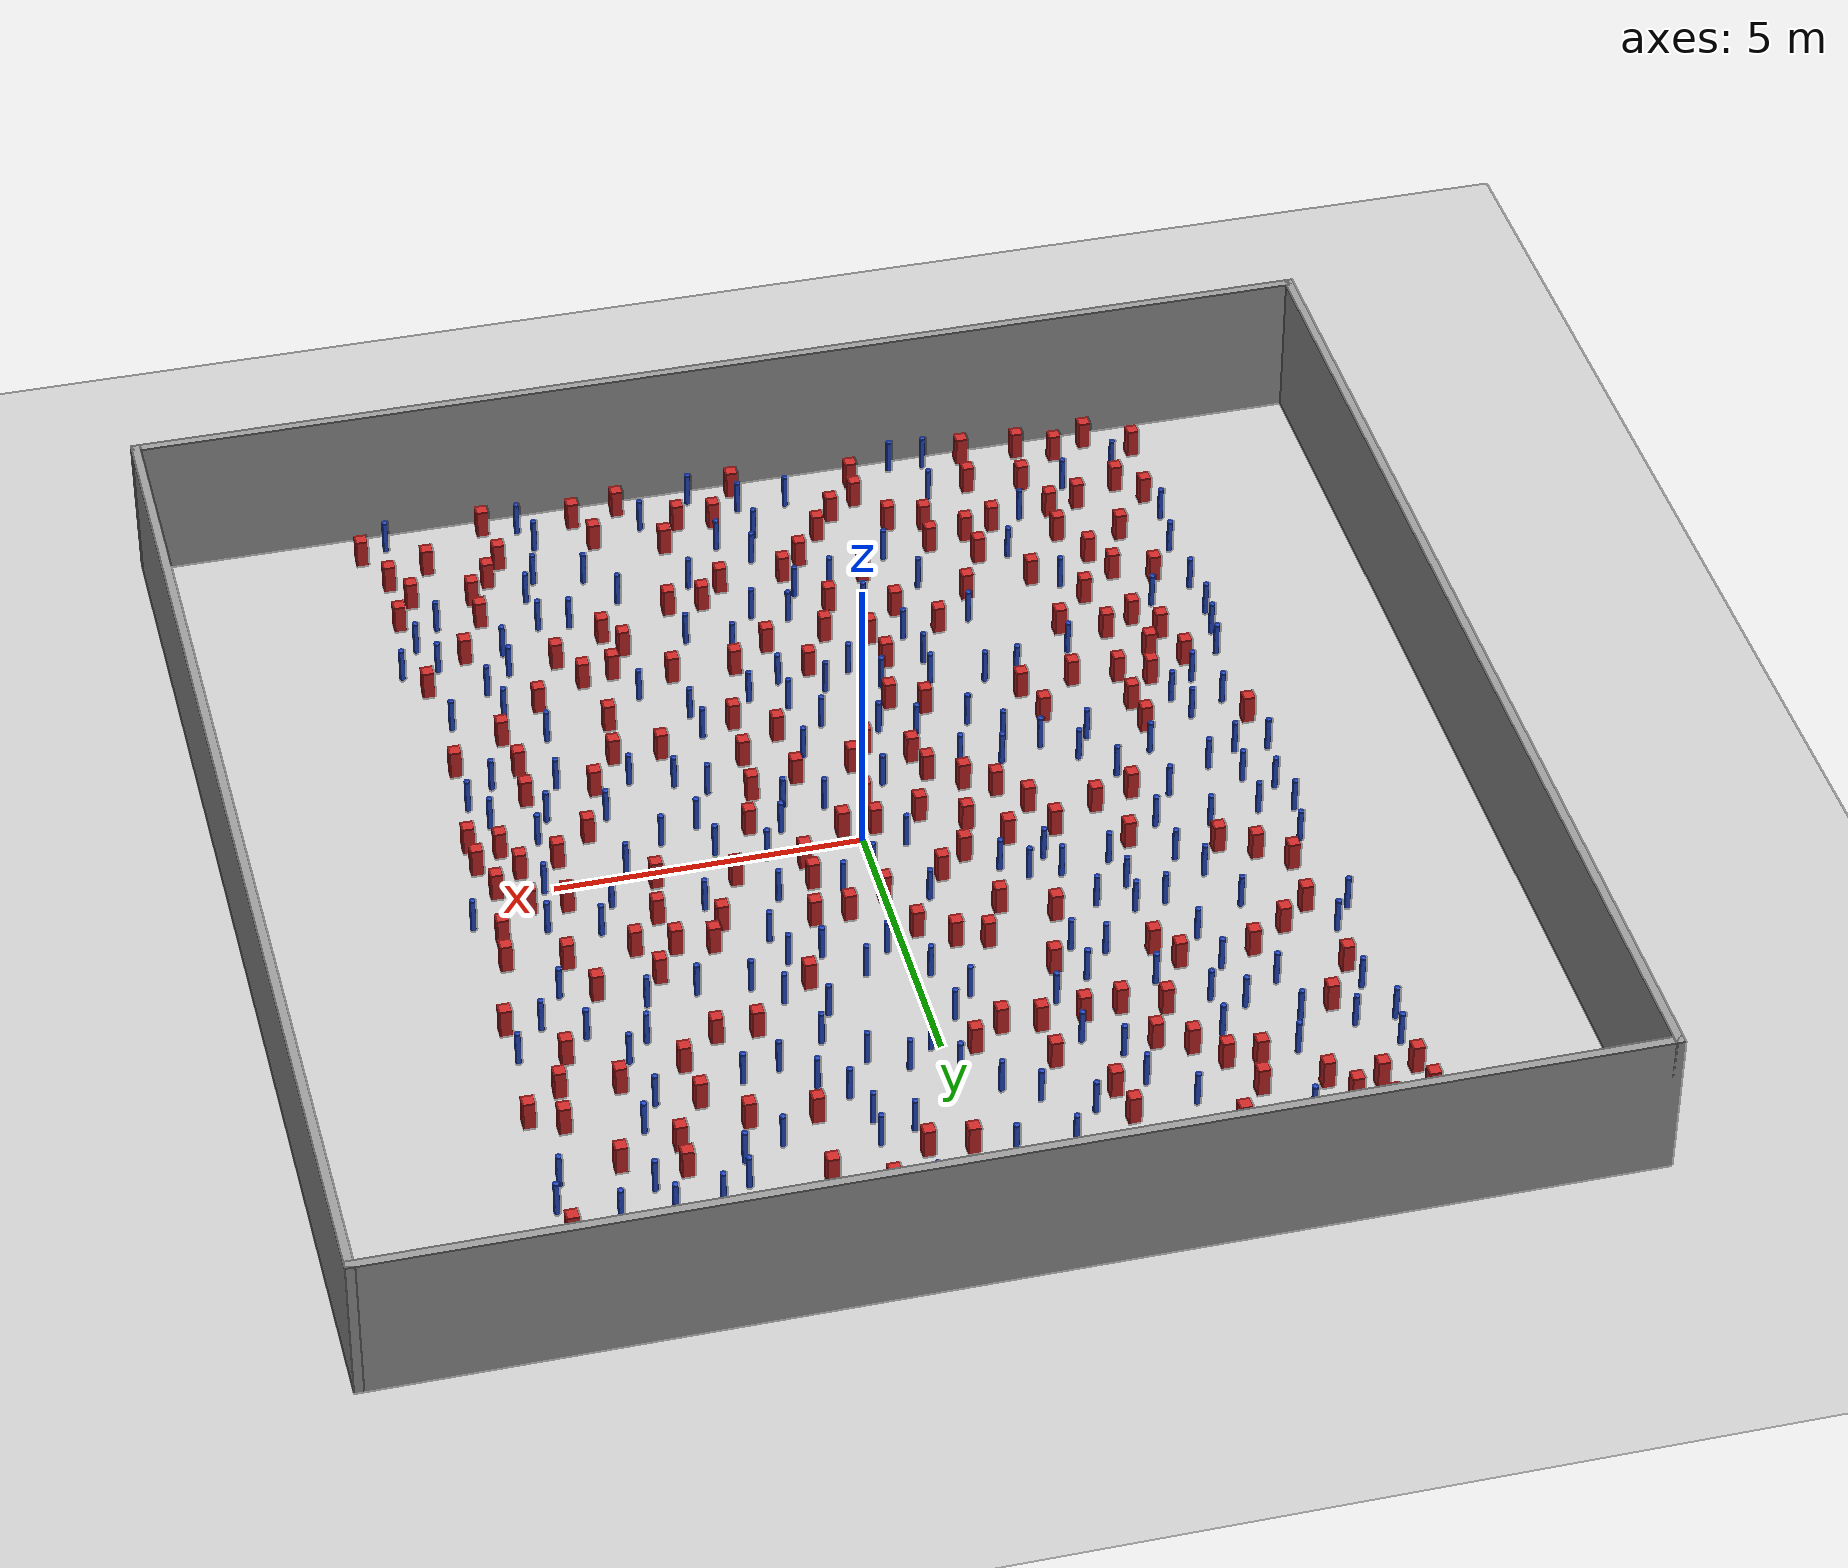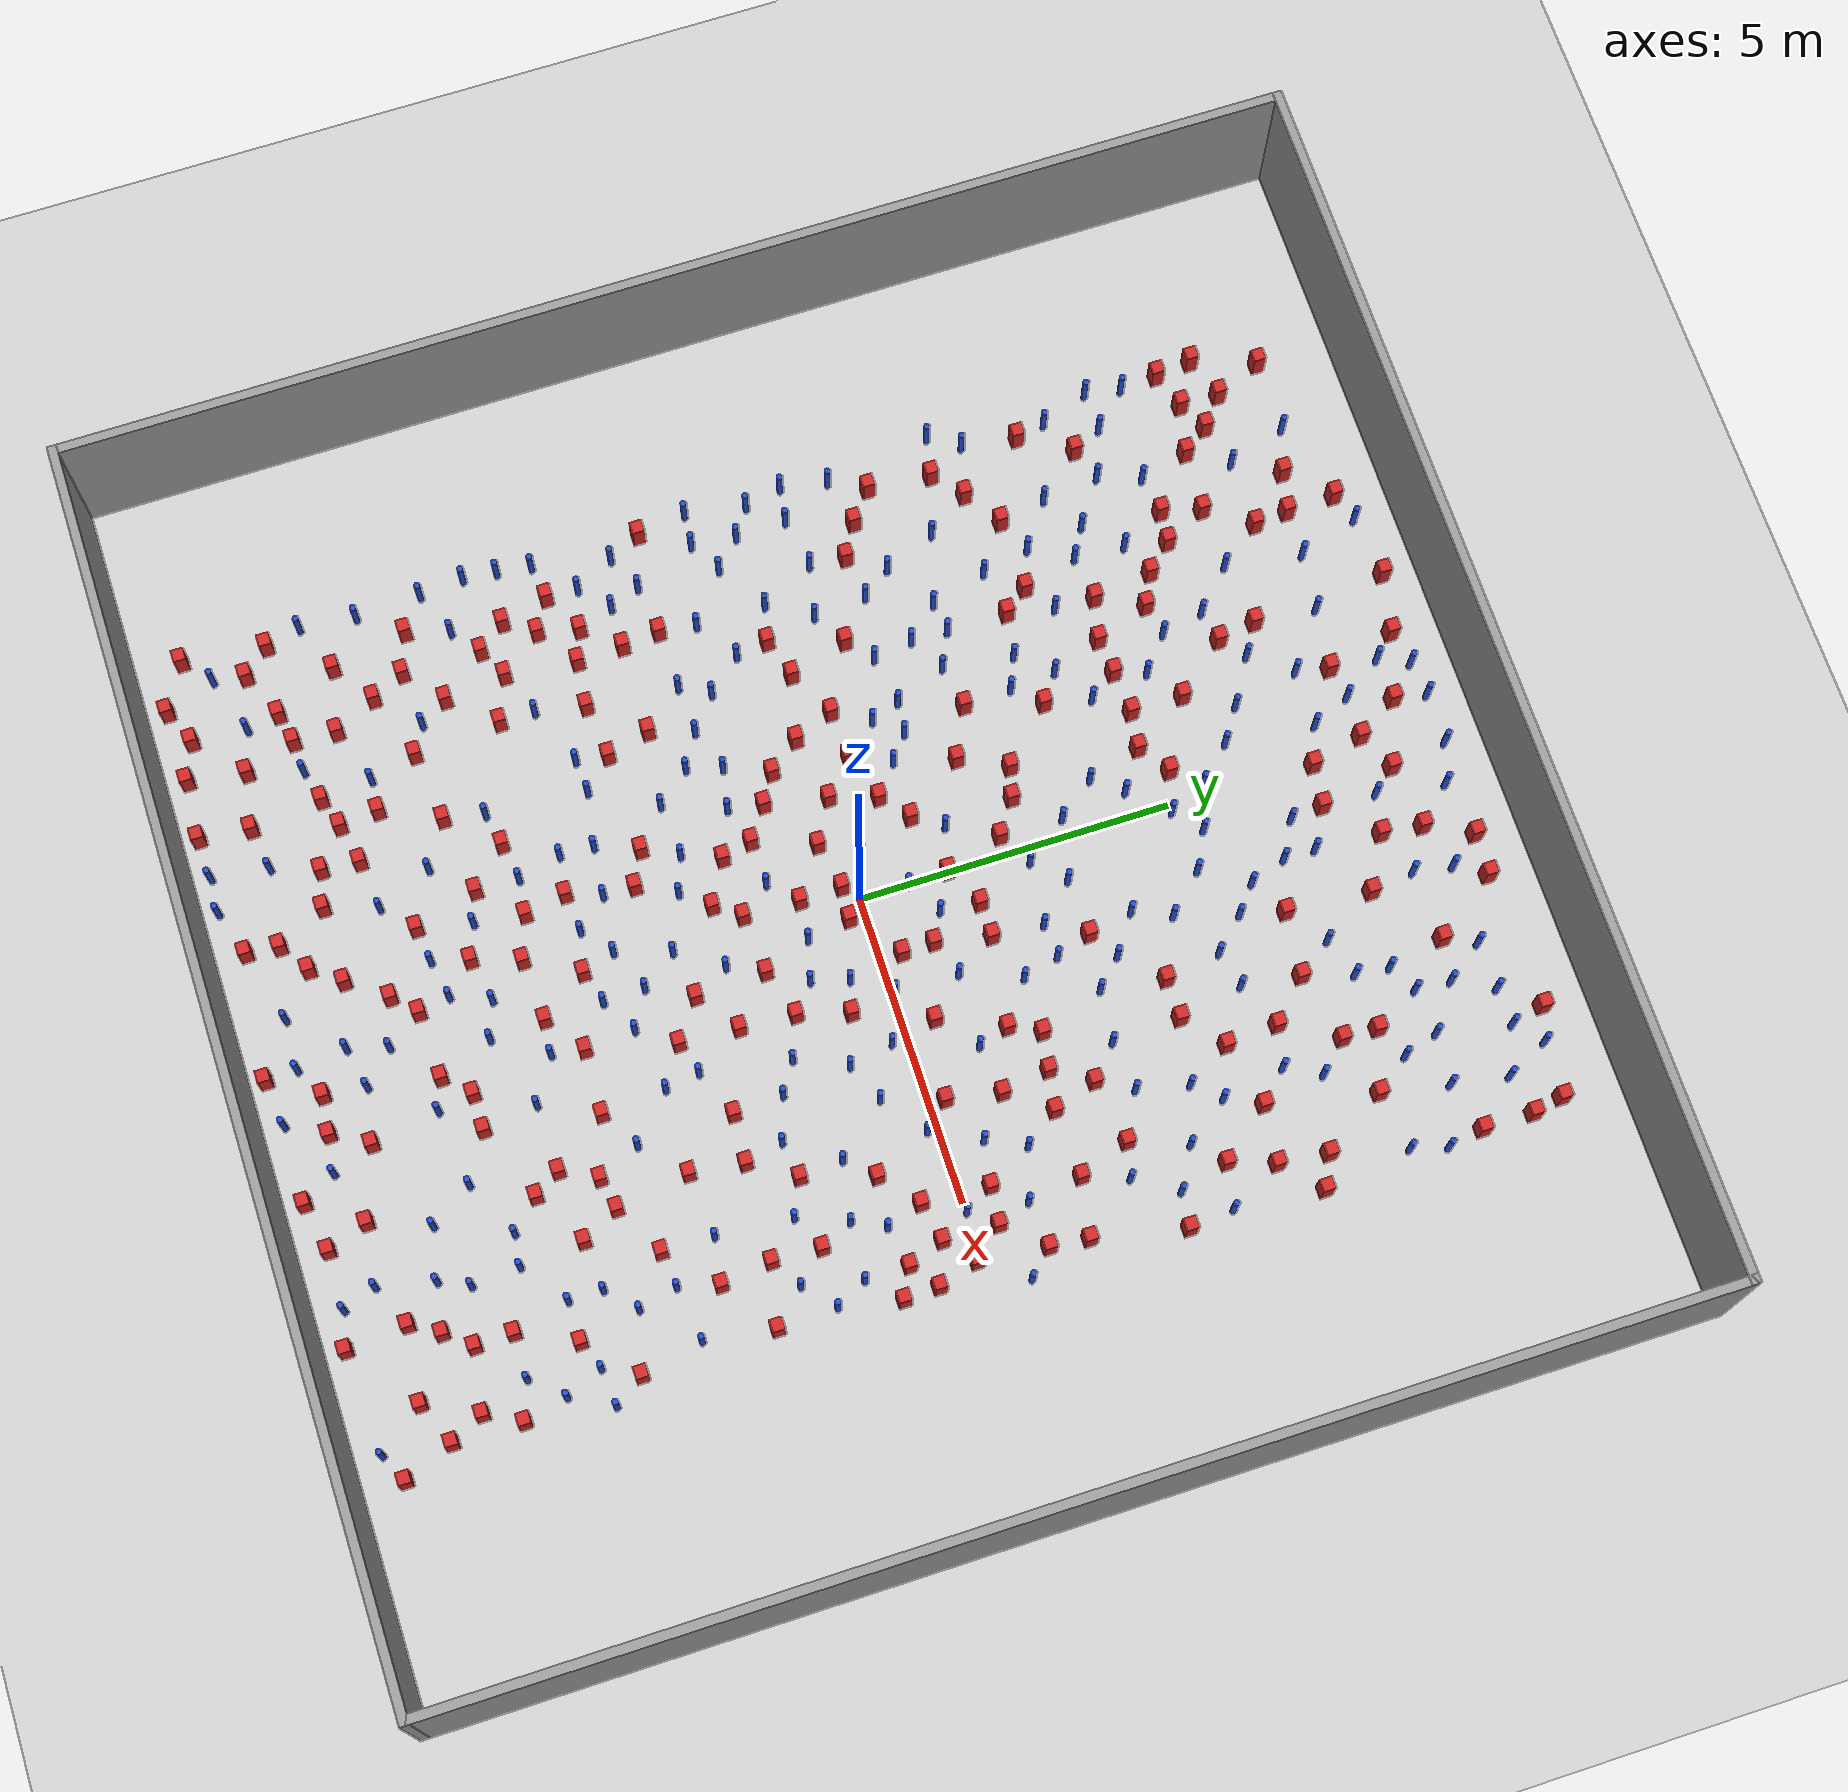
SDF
<sdf version="1.6">
 <world name="default">
  <light name="sun" type="directional">
   <pose>0 0 1000 0 -0 0</pose>
   <diffuse>0.8 0.8 0.8 1</diffuse>
   <specular>0.1 0.1 0.1 1</specular>
   <attenuation>
    <range>1000</range>
    <constant>0.9</constant>
    <linear>0.01</linear>
    <quadratic>0.001</quadratic>
   </attenuation>
   <direction>-0.5 0.5 -1</direction>
  </light>
  <model name="ground_plane">
   <static>1</static>
   <link name="link">
    <collision name="collision">
     <geometry><plane><normal>0 0 1</normal><size>100 100</size></plane></geometry>
     <surface><friction><ode><mu>100</mu><mu2>50</mu2></ode></friction></surface>
    </collision>
    <visual name="visual">
     <cast_shadows>0</cast_shadows>
     <geometry><plane><normal>0 0 1</normal><size>100 100</size></plane></geometry>
     <material>
      <ambient>1.0 1.0 1.0 1.0</ambient>
      <diffuse>0.8 0.8 0.8 1.0</diffuse>
      <specular>0.01 0.01 0.01 1.000000</specular>
     </material>
    </visual>
   </link>
  </model>
  <gravity>0 0 -9.8</gravity>
  <magnetic_field>6e-06 2.3e-05 -4.2e-05</magnetic_field>
  <atmosphere type="adiabatic"/>
  <physics name="default_physics" default="0" type="ode">
   <max_step_size>0.001</max_step_size>
   <real_time_factor>1</real_time_factor>
   <real_time_update_rate>1000</real_time_update_rate>
  </physics>
  <scene><ambient>0.4 0.4 0.4 1</ambient><background>0.7 0.7 0.7 1</background><shadows>1</shadows></scene>
  <spherical_coordinates>
   <surface_model>EARTH_WGS84</surface_model>
   <latitude_deg>0</latitude_deg>
   <longitude_deg>0</longitude_deg>
   <elevation>0</elevation>
   <heading_deg>0</heading_deg>
  </spherical_coordinates>
  <plugin name="gazebo_occupancy_map" filename="libgazebo_2Dmap_plugin.so">
   <map_resolution>0.05</map_resolution>
   <map_topic>generated_map</map_topic>
   <map_height>0.01</map_height>
   <map_size_x>50</map_size_x>
   <map_size_y>50</map_size_y>
  </plugin>
  <model name="NamedLocations">
   <static>true</static>
   <link name="DefaultStart"><pose>8.5 0 0 0 0 3.14</pose></link>
  </model>
  <model name="20x20_walls">
   <pose>0.044518 0.176112 0 0 -0 0</pose>
   <link name="Wall_1">
    <collision name="Wall_1_Collision">
     <geometry><box><size>20 0.15 2.5</size></box></geometry>
     <pose>0 0 1.25 0 -0 0</pose>
    </collision>
    <visual name="Wall_1_Visual">
     <pose>0 0 1.25 0 -0 0</pose>
     <geometry><box><size>20 0.15 2.5</size></box></geometry>
     <material>
      <script><uri>file://media/materials/scripts/gazebo.material</uri><name>Gazebo/Grey</name></script>
      <ambient>0.976471 0.992157 1 1</ambient>
     </material>
     <meta><layer>0</layer></meta>
    </visual>
    <pose>0 9.925 0 0 -0 0</pose>
   </link>
   <link name="Wall_3">
    <collision name="Wall_3_Collision">
     <geometry><box><size>20 0.15 2.5</size></box></geometry>
     <pose>0 0 1.25 0 -0 0</pose>
    </collision>
    <visual name="Wall_3_Visual">
     <pose>0 0 1.25 0 -0 0</pose>
     <geometry><box><size>20 0.15 2.5</size></box></geometry>
     <material>
      <script><uri>file://media/materials/scripts/gazebo.material</uri><name>Gazebo/Grey</name></script>
      <ambient>0.976471 0.992157 1 1</ambient>
     </material>
     <meta><layer>0</layer></meta>
    </visual>
    <pose>9.925 0 0 0 0 -1.5708</pose>
   </link>
   <link name="Wall_4">
    <collision name="Wall_4_Collision">
     <geometry><box><size>20 0.15 2.5</size></box></geometry>
     <pose>0 0 1.25 0 -0 0</pose>
    </collision>
    <visual name="Wall_4_Visual">
     <pose>0 0 1.25 0 -0 0</pose>
     <geometry><box><size>20 0.15 2.5</size></box></geometry>
     <material>
      <script><uri>file://media/materials/scripts/gazebo.material</uri><name>Gazebo/Grey</name></script>
      <ambient>0.976471 0.992157 1 1</ambient>
     </material>
     <meta><layer>0</layer></meta>
    </visual>
    <pose>0 -9.925 0 0 -0 3.14159</pose>
   </link>
   <link name="Wall_5">
    <collision name="Wall_5_Collision">
     <geometry><box><size>20 0.15 2.5</size></box></geometry>
     <pose>0 0 1.25 0 -0 0</pose>
    </collision>
    <visual name="Wall_5_Visual">
     <pose>0 0 1.25 0 -0 0</pose>
     <geometry><box><size>20 0.15 2.5</size></box></geometry>
     <material>
      <script><uri>file://media/materials/scripts/gazebo.material</uri><name>Gazebo/Grey</name></script>
      <ambient>0.976471 0.992157 1 1</ambient>
     </material>
     <meta><layer>0</layer></meta>
    </visual>
    <pose>-9.925 0 0 0 -0 1.5708</pose>
   </link>
   <static>1</static>
  </model>
  <model name="pole_obstacle0">
   <static>true</static>
   <pose>5.99241946751 -6.43416623449 -9.47619616065e-06 5.49618799737e-07 2.36310414037e-07 -1.55090534814e-07</pose>
   <link name="link">
    <pose>0 0 0.3 0 -0 0</pose>
    <inertial>
     <mass>1</mass>
     <inertia><ixx>0.145833</ixx><ixy>0</ixy><ixz>0</ixz><iyy>0.145833</iyy><iyz>0</iyz><izz>0.125</izz></inertia>
    </inertial>
    <collision name="collision">
     <geometry><cylinder><radius>0.05</radius><length>.6</length></cylinder></geometry>
    </collision>
    <visual name="visual">
     <geometry><cylinder><radius>0.05</radius><length>.6</length></cylinder></geometry>
     <material>
      <script><name>Gazebo/Blue</name><uri>file://media/materials/scripts/gazebo.material</uri></script>
     </material>
    </visual>
   </link>
  </model>
  <model name="pole_obstacle1">
   <static>true</static>
   <pose>4.46261429955 -2.45915719128 -9.47619616065e-06 5.49618799738e-07 2.36310414051e-07 -1.55090534805e-07</pose>
   <link name="link">
    <pose>0 0 0.3 0 -0 0</pose>
    <inertial>
     <mass>1</mass>
     <inertia><ixx>0.145833</ixx><ixy>0</ixy><ixz>0</ixz><iyy>0.145833</iyy><iyz>0</iyz><izz>0.125</izz></inertia>
    </inertial>
    <collision name="collision">
     <geometry><cylinder><radius>0.05</radius><length>.6</length></cylinder></geometry>
    </collision>
    <visual name="visual">
     <geometry><cylinder><radius>0.05</radius><length>.6</length></cylinder></geometry>
     <material>
      <script><name>Gazebo/Blue</name><uri>file://media/materials/scripts/gazebo.material</uri></script>
     </material>
    </visual>
   </link>
  </model>
  <model name="square_post_obstacle0">
   <static>true</static>
   <pose>-5.41311014788 -6.22488817365 -6.11067671241e-07 -5.50515727128e-06 -8.79689657224e-07 2.37013304536e-05</pose>
   <link name="link">
    <pose>0 0 0.25 0 -0 0</pose>
    <inertial>
     <mass>100</mass>
     <inertia>
      <ixx>0.166667</ixx>
      <ixy>0</ixy>
      <ixz>0</ixz>
      <iyy>0.166667</iyy>
      <iyz>0</iyz>
      <izz>0.166667</izz>
     </inertia>
    </inertial>
    <collision name="collision"><geometry><box><size>.2 .2 .5</size></box></geometry></collision>
    <visual name="visual">
     <geometry><box><size>.2 .2 .5</size></box></geometry>
     <material>
      <script><name>Gazebo/Red</name><uri>file://media/materials/scripts/gazebo.material</uri></script>
     </material>
    </visual>
   </link>
  </model>
  <model name="square_post_obstacle1">
   <static>true</static>
   <pose>-2.88385890678 4.84033319816 -6.11067671241e-07 -5.50515727128e-06 -8.79689657224e-07 2.37013304536e-05</pose>
   <link name="link">
    <pose>0 0 0.25 0 -0 0</pose>
    <inertial>
     <mass>100</mass>
     <inertia>
      <ixx>0.166667</ixx>
      <ixy>0</ixy>
      <ixz>0</ixz>
      <iyy>0.166667</iyy>
      <iyz>0</iyz>
      <izz>0.166667</izz>
     </inertia>
    </inertial>
    <collision name="collision"><geometry><box><size>.2 .2 .5</size></box></geometry></collision>
    <visual name="visual">
     <geometry><box><size>.2 .2 .5</size></box></geometry>
     <material>
      <script><name>Gazebo/Red</name><uri>file://media/materials/scripts/gazebo.material</uri></script>
     </material>
    </visual>
   </link>
  </model>
  <model name="pole_obstacle2">
   <static>true</static>
   <pose>2.31823397724 8.81499281397 -9.4761961606e-06 5.49618799729e-07 2.36310414e-07 -1.55090534824e-07</pose>
   <link name="link">
    <pose>0 0 0.3 0 -0 0</pose>
    <inertial>
     <mass>1</mass>
     <inertia><ixx>0.145833</ixx><ixy>0</ixy><ixz>0</ixz><iyy>0.145833</iyy><iyz>0</iyz><izz>0.125</izz></inertia>
    </inertial>
    <collision name="collision">
     <geometry><cylinder><radius>0.05</radius><length>.6</length></cylinder></geometry>
    </collision>
    <visual name="visual">
     <geometry><cylinder><radius>0.05</radius><length>.6</length></cylinder></geometry>
     <material>
      <script><name>Gazebo/Blue</name><uri>file://media/materials/scripts/gazebo.material</uri></script>
     </material>
    </visual>
   </link>
  </model>
  <model name="pole_obstacle3">
   <static>true</static>
   <pose>3.58770539733 8.74154161247 -9.4761961606e-06 5.49618799729e-07 2.36310414e-07 -1.55090534824e-07</pose>
   <link name="link">
    <pose>0 0 0.3 0 -0 0</pose>
    <inertial>
     <mass>1</mass>
     <inertia><ixx>0.145833</ixx><ixy>0</ixy><ixz>0</ixz><iyy>0.145833</iyy><iyz>0</iyz><izz>0.125</izz></inertia>
    </inertial>
    <collision name="collision">
     <geometry><cylinder><radius>0.05</radius><length>.6</length></cylinder></geometry>
    </collision>
    <visual name="visual">
     <geometry><cylinder><radius>0.05</radius><length>.6</length></cylinder></geometry>
     <material>
      <script><name>Gazebo/Blue</name><uri>file://media/materials/scripts/gazebo.material</uri></script>
     </material>
    </visual>
   </link>
  </model>
  <model name="pole_obstacle4">
   <static>true</static>
   <pose>-0.367994864278 4.42728970482 -9.47619616065e-06 5.49618799737e-07 2.36310414065e-07 -1.55090534796e-07</pose>
   <link name="link">
    <pose>0 0 0.3 0 -0 0</pose>
    <inertial>
     <mass>1</mass>
     <inertia><ixx>0.145833</ixx><ixy>0</ixy><ixz>0</ixz><iyy>0.145833</iyy><iyz>0</iyz><izz>0.125</izz></inertia>
    </inertial>
    <collision name="collision">
     <geometry><cylinder><radius>0.05</radius><length>.6</length></cylinder></geometry>
    </collision>
    <visual name="visual">
     <geometry><cylinder><radius>0.05</radius><length>.6</length></cylinder></geometry>
     <material>
      <script><name>Gazebo/Blue</name><uri>file://media/materials/scripts/gazebo.material</uri></script>
     </material>
    </visual>
   </link>
  </model>
  <model name="pole_obstacle5">
   <static>true</static>
   <pose>0.42777094523 -6.01034890864 -9.47619616065e-06 5.49618799737e-07 2.36310414065e-07 -1.55090534796e-07</pose>
   <link name="link">
    <pose>0 0 0.3 0 -0 0</pose>
    <inertial>
     <mass>1</mass>
     <inertia><ixx>0.145833</ixx><ixy>0</ixy><ixz>0</ixz><iyy>0.145833</iyy><iyz>0</iyz><izz>0.125</izz></inertia>
    </inertial>
    <collision name="collision">
     <geometry><cylinder><radius>0.05</radius><length>.6</length></cylinder></geometry>
    </collision>
    <visual name="visual">
     <geometry><cylinder><radius>0.05</radius><length>.6</length></cylinder></geometry>
     <material>
      <script><name>Gazebo/Blue</name><uri>file://media/materials/scripts/gazebo.material</uri></script>
     </material>
    </visual>
   </link>
  </model>
  <model name="pole_obstacle6">
   <static>true</static>
   <pose>-3.25830325045 8.38387927455 -9.4761961606e-06 5.49618799729e-07 2.36310414e-07 -1.55090534824e-07</pose>
   <link name="link">
    <pose>0 0 0.3 0 -0 0</pose>
    <inertial>
     <mass>1</mass>
     <inertia><ixx>0.145833</ixx><ixy>0</ixy><ixz>0</ixz><iyy>0.145833</iyy><iyz>0</iyz><izz>0.125</izz></inertia>
    </inertial>
    <collision name="collision">
     <geometry><cylinder><radius>0.05</radius><length>.6</length></cylinder></geometry>
    </collision>
    <visual name="visual">
     <geometry><cylinder><radius>0.05</radius><length>.6</length></cylinder></geometry>
     <material>
      <script><name>Gazebo/Blue</name><uri>file://media/materials/scripts/gazebo.material</uri></script>
     </material>
    </visual>
   </link>
  </model>
  <model name="square_post_obstacle2">
   <static>true</static>
   <pose>3.32583595475 -3.76178760653 -6.11067671241e-07 -5.50515727128e-06 -8.79689657224e-07 2.37013304536e-05</pose>
   <link name="link">
    <pose>0 0 0.25 0 -0 0</pose>
    <inertial>
     <mass>100</mass>
     <inertia>
      <ixx>0.166667</ixx>
      <ixy>0</ixy>
      <ixz>0</ixz>
      <iyy>0.166667</iyy>
      <iyz>0</iyz>
      <izz>0.166667</izz>
     </inertia>
    </inertial>
    <collision name="collision"><geometry><box><size>.2 .2 .5</size></box></geometry></collision>
    <visual name="visual">
     <geometry><box><size>.2 .2 .5</size></box></geometry>
     <material>
      <script><name>Gazebo/Red</name><uri>file://media/materials/scripts/gazebo.material</uri></script>
     </material>
    </visual>
   </link>
  </model>
  <model name="square_post_obstacle3">
   <static>true</static>
   <pose>6.1274919712 -1.29283202297 -6.11067671241e-07 -5.50515727128e-06 -8.79689657224e-07 2.37013304536e-05</pose>
   <link name="link">
    <pose>0 0 0.25 0 -0 0</pose>
    <inertial>
     <mass>100</mass>
     <inertia>
      <ixx>0.166667</ixx>
      <ixy>0</ixy>
      <ixz>0</ixz>
      <iyy>0.166667</iyy>
      <iyz>0</iyz>
      <izz>0.166667</izz>
     </inertia>
    </inertial>
    <collision name="collision"><geometry><box><size>.2 .2 .5</size></box></geometry></collision>
    <visual name="visual">
     <geometry><box><size>.2 .2 .5</size></box></geometry>
     <material>
      <script><name>Gazebo/Red</name><uri>file://media/materials/scripts/gazebo.material</uri></script>
     </material>
    </visual>
   </link>
  </model>
  <model name="square_post_obstacle4">
   <static>true</static>
   <pose>-0.558098675889 -2.19757044588 -6.11067671241e-07 -5.50515727128e-06 -8.79689657224e-07 2.37013304536e-05</pose>
   <link name="link">
    <pose>0 0 0.25 0 -0 0</pose>
    <inertial>
     <mass>100</mass>
     <inertia>
      <ixx>0.166667</ixx>
      <ixy>0</ixy>
      <ixz>0</ixz>
      <iyy>0.166667</iyy>
      <iyz>0</iyz>
      <izz>0.166667</izz>
     </inertia>
    </inertial>
    <collision name="collision"><geometry><box><size>.2 .2 .5</size></box></geometry></collision>
    <visual name="visual">
     <geometry><box><size>.2 .2 .5</size></box></geometry>
     <material>
      <script><name>Gazebo/Red</name><uri>file://media/materials/scripts/gazebo.material</uri></script>
     </material>
    </visual>
   </link>
  </model>
  <model name="pole_obstacle7">
   <static>true</static>
   <pose>1.28148390467 2.54067466043 -9.47619616065e-06 5.49618799737e-07 2.36310414062e-07 -1.55090534798e-07</pose>
   <link name="link">
    <pose>0 0 0.3 0 -0 0</pose>
    <inertial>
     <mass>1</mass>
     <inertia><ixx>0.145833</ixx><ixy>0</ixy><ixz>0</ixz><iyy>0.145833</iyy><iyz>0</iyz><izz>0.125</izz></inertia>
    </inertial>
    <collision name="collision">
     <geometry><cylinder><radius>0.05</radius><length>.6</length></cylinder></geometry>
    </collision>
    <visual name="visual">
     <geometry><cylinder><radius>0.05</radius><length>.6</length></cylinder></geometry>
     <material>
      <script><name>Gazebo/Blue</name><uri>file://media/materials/scripts/gazebo.material</uri></script>
     </material>
    </visual>
   </link>
  </model>
  <model name="pole_obstacle8">
   <static>true</static>
   <pose>4.49271938072 1.20656076858 -9.47619616065e-06 5.49618799738e-07 2.36310414071e-07 -1.55090534796e-07</pose>
   <link name="link">
    <pose>0 0 0.3 0 -0 0</pose>
    <inertial>
     <mass>1</mass>
     <inertia><ixx>0.145833</ixx><ixy>0</ixy><ixz>0</ixz><iyy>0.145833</iyy><iyz>0</iyz><izz>0.125</izz></inertia>
    </inertial>
    <collision name="collision">
     <geometry><cylinder><radius>0.05</radius><length>.6</length></cylinder></geometry>
    </collision>
    <visual name="visual">
     <geometry><cylinder><radius>0.05</radius><length>.6</length></cylinder></geometry>
     <material>
      <script><name>Gazebo/Blue</name><uri>file://media/materials/scripts/gazebo.material</uri></script>
     </material>
    </visual>
   </link>
  </model>
  <model name="square_post_obstacle5">
   <static>true</static>
   <pose>0.101492005268 7.33459022329 -6.11067671241e-07 -5.50515727128e-06 -8.79689657224e-07 2.37013304536e-05</pose>
   <link name="link">
    <pose>0 0 0.25 0 -0 0</pose>
    <inertial>
     <mass>100</mass>
     <inertia>
      <ixx>0.166667</ixx>
      <ixy>0</ixy>
      <ixz>0</ixz>
      <iyy>0.166667</iyy>
      <iyz>0</iyz>
      <izz>0.166667</izz>
     </inertia>
    </inertial>
    <collision name="collision"><geometry><box><size>.2 .2 .5</size></box></geometry></collision>
    <visual name="visual">
     <geometry><box><size>.2 .2 .5</size></box></geometry>
     <material>
      <script><name>Gazebo/Red</name><uri>file://media/materials/scripts/gazebo.material</uri></script>
     </material>
    </visual>
   </link>
  </model>
  <model name="square_post_obstacle6">
   <static>true</static>
   <pose>-1.96284381164 -8.66067256167 -6.11067671241e-07 -5.50515727128e-06 -8.79689657224e-07 2.37013304536e-05</pose>
   <link name="link">
    <pose>0 0 0.25 0 -0 0</pose>
    <inertial>
     <mass>100</mass>
     <inertia>
      <ixx>0.166667</ixx>
      <ixy>0</ixy>
      <ixz>0</ixz>
      <iyy>0.166667</iyy>
      <iyz>0</iyz>
      <izz>0.166667</izz>
     </inertia>
    </inertial>
    <collision name="collision"><geometry><box><size>.2 .2 .5</size></box></geometry></collision>
    <visual name="visual">
     <geometry><box><size>.2 .2 .5</size></box></geometry>
     <material>
      <script><name>Gazebo/Red</name><uri>file://media/materials/scripts/gazebo.material</uri></script>
     </material>
    </visual>
   </link>
  </model>
  <model name="square_post_obstacle7">
   <static>true</static>
   <pose>5.66309559991 -1.05410015677 -6.11067671241e-07 -5.50515727128e-06 -8.79689657224e-07 2.37013304536e-05</pose>
   <link name="link">
    <pose>0 0 0.25 0 -0 0</pose>
    <inertial>
     <mass>100</mass>
     <inertia>
      <ixx>0.166667</ixx>
      <ixy>0</ixy>
      <ixz>0</ixz>
      <iyy>0.166667</iyy>
      <iyz>0</iyz>
      <izz>0.166667</izz>
     </inertia>
    </inertial>
    <collision name="collision"><geometry><box><size>.2 .2 .5</size></box></geometry></collision>
    <visual name="visual">
     <geometry><box><size>.2 .2 .5</size></box></geometry>
     <material>
      <script><name>Gazebo/Red</name><uri>file://media/materials/scripts/gazebo.material</uri></script>
     </material>
    </visual>
   </link>
  </model>
  <model name="pole_obstacle9">
   <static>true</static>
   <pose>-0.49709709872 7.59157421841 -9.47619616065e-06 5.49618799737e-07 2.36310414063e-07 -1.55090534797e-07</pose>
   <link name="link">
    <pose>0 0 0.3 0 -0 0</pose>
    <inertial>
     <mass>1</mass>
     <inertia><ixx>0.145833</ixx><ixy>0</ixy><ixz>0</ixz><iyy>0.145833</iyy><iyz>0</iyz><izz>0.125</izz></inertia>
    </inertial>
    <collision name="collision">
     <geometry><cylinder><radius>0.05</radius><length>.6</length></cylinder></geometry>
    </collision>
    <visual name="visual">
     <geometry><cylinder><radius>0.05</radius><length>.6</length></cylinder></geometry>
     <material>
      <script><name>Gazebo/Blue</name><uri>file://media/materials/scripts/gazebo.material</uri></script>
     </material>
    </visual>
   </link>
  </model>
  <model name="pole_obstacle10">
   <static>true</static>
   <pose>-3.58671342312 4.36858105361 -9.47619616065e-06 5.49618799738e-07 2.3631041406e-07 -1.55090534801e-07</pose>
   <link name="link">
    <pose>0 0 0.3 0 -0 0</pose>
    <inertial>
     <mass>1</mass>
     <inertia><ixx>0.145833</ixx><ixy>0</ixy><ixz>0</ixz><iyy>0.145833</iyy><iyz>0</iyz><izz>0.125</izz></inertia>
    </inertial>
    <collision name="collision">
     <geometry><cylinder><radius>0.05</radius><length>.6</length></cylinder></geometry>
    </collision>
    <visual name="visual">
     <geometry><cylinder><radius>0.05</radius><length>.6</length></cylinder></geometry>
     <material>
      <script><name>Gazebo/Blue</name><uri>file://media/materials/scripts/gazebo.material</uri></script>
     </material>
    </visual>
   </link>
  </model>
  <model name="pole_obstacle11">
   <static>true</static>
   <pose>6.4430343955 7.1984281957 -9.47619616065e-06 5.49618799737e-07 2.36310414037e-07 -1.55090534814e-07</pose>
   <link name="link">
    <pose>0 0 0.3 0 -0 0</pose>
    <inertial>
     <mass>1</mass>
     <inertia><ixx>0.145833</ixx><ixy>0</ixy><ixz>0</ixz><iyy>0.145833</iyy><iyz>0</iyz><izz>0.125</izz></inertia>
    </inertial>
    <collision name="collision">
     <geometry><cylinder><radius>0.05</radius><length>.6</length></cylinder></geometry>
    </collision>
    <visual name="visual">
     <geometry><cylinder><radius>0.05</radius><length>.6</length></cylinder></geometry>
     <material>
      <script><name>Gazebo/Blue</name><uri>file://media/materials/scripts/gazebo.material</uri></script>
     </material>
    </visual>
   </link>
  </model>
  <model name="pole_obstacle12">
   <static>true</static>
   <pose>-2.85050988075 1.53689811707 -9.47619616065e-06 5.49618799737e-07 2.36310414072e-07 -1.55090534793e-07</pose>
   <link name="link">
    <pose>0 0 0.3 0 -0 0</pose>
    <inertial>
     <mass>1</mass>
     <inertia><ixx>0.145833</ixx><ixy>0</ixy><ixz>0</ixz><iyy>0.145833</iyy><iyz>0</iyz><izz>0.125</izz></inertia>
    </inertial>
    <collision name="collision">
     <geometry><cylinder><radius>0.05</radius><length>.6</length></cylinder></geometry>
    </collision>
    <visual name="visual">
     <geometry><cylinder><radius>0.05</radius><length>.6</length></cylinder></geometry>
     <material>
      <script><name>Gazebo/Blue</name><uri>file://media/materials/scripts/gazebo.material</uri></script>
     </material>
    </visual>
   </link>
  </model>
  <model name="square_post_obstacle8">
   <static>true</static>
   <pose>-0.286140557793 2.35264386809 -6.11067671241e-07 -5.50515727128e-06 -8.79689657224e-07 2.37013304536e-05</pose>
   <link name="link">
    <pose>0 0 0.25 0 -0 0</pose>
    <inertial>
     <mass>100</mass>
     <inertia>
      <ixx>0.166667</ixx>
      <ixy>0</ixy>
      <ixz>0</ixz>
      <iyy>0.166667</iyy>
      <iyz>0</iyz>
      <izz>0.166667</izz>
     </inertia>
    </inertial>
    <collision name="collision"><geometry><box><size>.2 .2 .5</size></box></geometry></collision>
    <visual name="visual">
     <geometry><box><size>.2 .2 .5</size></box></geometry>
     <material>
      <script><name>Gazebo/Red</name><uri>file://media/materials/scripts/gazebo.material</uri></script>
     </material>
    </visual>
   </link>
  </model>
  <model name="square_post_obstacle9">
   <static>true</static>
   <pose>3.46107579116 1.86878623679 -6.11067671241e-07 -5.50515727128e-06 -8.79689657224e-07 2.37013304536e-05</pose>
   <link name="link">
    <pose>0 0 0.25 0 -0 0</pose>
    <inertial>
     <mass>100</mass>
     <inertia>
      <ixx>0.166667</ixx>
      <ixy>0</ixy>
      <ixz>0</ixz>
      <iyy>0.166667</iyy>
      <iyz>0</iyz>
      <izz>0.166667</izz>
     </inertia>
    </inertial>
    <collision name="collision"><geometry><box><size>.2 .2 .5</size></box></geometry></collision>
    <visual name="visual">
     <geometry><box><size>.2 .2 .5</size></box></geometry>
     <material>
      <script><name>Gazebo/Red</name><uri>file://media/materials/scripts/gazebo.material</uri></script>
     </material>
    </visual>
   </link>
  </model>
  <model name="pole_obstacle13">
   <static>true</static>
   <pose>0.775873148041 -9.32553933954 -9.47619616065e-06 5.49618799737e-07 2.36310414038e-07 -1.55090534813e-07</pose>
   <link name="link">
    <pose>0 0 0.3 0 -0 0</pose>
    <inertial>
     <mass>1</mass>
     <inertia><ixx>0.145833</ixx><ixy>0</ixy><ixz>0</ixz><iyy>0.145833</iyy><iyz>0</iyz><izz>0.125</izz></inertia>
    </inertial>
    <collision name="collision">
     <geometry><cylinder><radius>0.05</radius><length>.6</length></cylinder></geometry>
    </collision>
    <visual name="visual">
     <geometry><cylinder><radius>0.05</radius><length>.6</length></cylinder></geometry>
     <material>
      <script><name>Gazebo/Blue</name><uri>file://media/materials/scripts/gazebo.material</uri></script>
     </material>
    </visual>
   </link>
  </model>
  <model name="square_post_obstacle10">
   <static>true</static>
   <pose>-3.97500162084 7.84303103397 -6.11067671241e-07 -5.50515727128e-06 -8.79689657224e-07 2.37013304536e-05</pose>
   <link name="link">
    <pose>0 0 0.25 0 -0 0</pose>
    <inertial>
     <mass>100</mass>
     <inertia>
      <ixx>0.166667</ixx>
      <ixy>0</ixy>
      <ixz>0</ixz>
      <iyy>0.166667</iyy>
      <iyz>0</iyz>
      <izz>0.166667</izz>
     </inertia>
    </inertial>
    <collision name="collision"><geometry><box><size>.2 .2 .5</size></box></geometry></collision>
    <visual name="visual">
     <geometry><box><size>.2 .2 .5</size></box></geometry>
     <material>
      <script><name>Gazebo/Red</name><uri>file://media/materials/scripts/gazebo.material</uri></script>
     </material>
    </visual>
   </link>
  </model>
  <model name="square_post_obstacle11">
   <static>true</static>
   <pose>4.32330241227 -9.34425784585 -6.11067671241e-07 -5.50515727128e-06 -8.79689657224e-07 2.37013304536e-05</pose>
   <link name="link">
    <pose>0 0 0.25 0 -0 0</pose>
    <inertial>
     <mass>100</mass>
     <inertia>
      <ixx>0.166667</ixx>
      <ixy>0</ixy>
      <ixz>0</ixz>
      <iyy>0.166667</iyy>
      <iyz>0</iyz>
      <izz>0.166667</izz>
     </inertia>
    </inertial>
    <collision name="collision"><geometry><box><size>.2 .2 .5</size></box></geometry></collision>
    <visual name="visual">
     <geometry><box><size>.2 .2 .5</size></box></geometry>
     <material>
      <script><name>Gazebo/Red</name><uri>file://media/materials/scripts/gazebo.material</uri></script>
     </material>
    </visual>
   </link>
  </model>
  <model name="pole_obstacle14">
   <static>true</static>
   <pose>0.0870210778384 -7.48965490971 -9.47619616065e-06 5.49618799737e-07 2.36310414063e-07 -1.55090534799e-07</pose>
   <link name="link">
    <pose>0 0 0.3 0 -0 0</pose>
    <inertial>
     <mass>1</mass>
     <inertia><ixx>0.145833</ixx><ixy>0</ixy><ixz>0</ixz><iyy>0.145833</iyy><iyz>0</iyz><izz>0.125</izz></inertia>
    </inertial>
    <collision name="collision">
     <geometry><cylinder><radius>0.05</radius><length>.6</length></cylinder></geometry>
    </collision>
    <visual name="visual">
     <geometry><cylinder><radius>0.05</radius><length>.6</length></cylinder></geometry>
     <material>
      <script><name>Gazebo/Blue</name><uri>file://media/materials/scripts/gazebo.material</uri></script>
     </material>
    </visual>
   </link>
  </model>
  <model name="pole_obstacle15">
   <static>true</static>
   <pose>1.02645550142 9.18468130639 -9.47619616065e-06 5.49618799738e-07 2.36310414043e-07 -1.5509053481e-07</pose>
   <link name="link">
    <pose>0 0 0.3 0 -0 0</pose>
    <inertial>
     <mass>1</mass>
     <inertia><ixx>0.145833</ixx><ixy>0</ixy><ixz>0</ixz><iyy>0.145833</iyy><iyz>0</iyz><izz>0.125</izz></inertia>
    </inertial>
    <collision name="collision">
     <geometry><cylinder><radius>0.05</radius><length>.6</length></cylinder></geometry>
    </collision>
    <visual name="visual">
     <geometry><cylinder><radius>0.05</radius><length>.6</length></cylinder></geometry>
     <material>
      <script><name>Gazebo/Blue</name><uri>file://media/materials/scripts/gazebo.material</uri></script>
     </material>
    </visual>
   </link>
  </model>
  <model name="square_post_obstacle12">
   <static>true</static>
   <pose>5.08211980681 -3.79533235804 -6.11067671241e-07 -5.50515727128e-06 -8.79689657224e-07 2.37013304536e-05</pose>
   <link name="link">
    <pose>0 0 0.25 0 -0 0</pose>
    <inertial>
     <mass>100</mass>
     <inertia>
      <ixx>0.166667</ixx>
      <ixy>0</ixy>
      <ixz>0</ixz>
      <iyy>0.166667</iyy>
      <iyz>0</iyz>
      <izz>0.166667</izz>
     </inertia>
    </inertial>
    <collision name="collision"><geometry><box><size>.2 .2 .5</size></box></geometry></collision>
    <visual name="visual">
     <geometry><box><size>.2 .2 .5</size></box></geometry>
     <material>
      <script><name>Gazebo/Red</name><uri>file://media/materials/scripts/gazebo.material</uri></script>
     </material>
    </visual>
   </link>
  </model>
  <model name="pole_obstacle16">
   <static>true</static>
   <pose>-3.02337573599 3.49883949913 -9.47619616065e-06 5.49618799737e-07 2.36310414051e-07 -1.55090534807e-07</pose>
   <link name="link">
    <pose>0 0 0.3 0 -0 0</pose>
    <inertial>
     <mass>1</mass>
     <inertia><ixx>0.145833</ixx><ixy>0</ixy><ixz>0</ixz><iyy>0.145833</iyy><iyz>0</iyz><izz>0.125</izz></inertia>
    </inertial>
    <collision name="collision">
     <geometry><cylinder><radius>0.05</radius><length>.6</length></cylinder></geometry>
    </collision>
    <visual name="visual">
     <geometry><cylinder><radius>0.05</radius><length>.6</length></cylinder></geometry>
     <material>
      <script><name>Gazebo/Blue</name><uri>file://media/materials/scripts/gazebo.material</uri></script>
     </material>
    </visual>
   </link>
  </model>
  <model name="pole_obstacle17">
   <static>true</static>
   <pose>-1.9095532421 6.96453747486 -9.47619616065e-06 5.49618799737e-07 2.36310414061e-07 -1.550905348e-07</pose>
   <link name="link">
    <pose>0 0 0.3 0 -0 0</pose>
    <inertial>
     <mass>1</mass>
     <inertia><ixx>0.145833</ixx><ixy>0</ixy><ixz>0</ixz><iyy>0.145833</iyy><iyz>0</iyz><izz>0.125</izz></inertia>
    </inertial>
    <collision name="collision">
     <geometry><cylinder><radius>0.05</radius><length>.6</length></cylinder></geometry>
    </collision>
    <visual name="visual">
     <geometry><cylinder><radius>0.05</radius><length>.6</length></cylinder></geometry>
     <material>
      <script><name>Gazebo/Blue</name><uri>file://media/materials/scripts/gazebo.material</uri></script>
     </material>
    </visual>
   </link>
  </model>
  <model name="square_post_obstacle13">
   <static>true</static>
   <pose>-3.61502706013 -6.64984049506 -6.11067671241e-07 -5.50515727128e-06 -8.79689657224e-07 2.37013304536e-05</pose>
   <link name="link">
    <pose>0 0 0.25 0 -0 0</pose>
    <inertial>
     <mass>100</mass>
     <inertia>
      <ixx>0.166667</ixx>
      <ixy>0</ixy>
      <ixz>0</ixz>
      <iyy>0.166667</iyy>
      <iyz>0</iyz>
      <izz>0.166667</izz>
     </inertia>
    </inertial>
    <collision name="collision"><geometry><box><size>.2 .2 .5</size></box></geometry></collision>
    <visual name="visual">
     <geometry><box><size>.2 .2 .5</size></box></geometry>
     <material>
      <script><name>Gazebo/Red</name><uri>file://media/materials/scripts/gazebo.material</uri></script>
     </material>
    </visual>
   </link>
  </model>
  <model name="pole_obstacle18">
   <static>true</static>
   <pose>4.73230912278 7.6285007044 -9.47619616065e-06 5.49618799737e-07 2.36310414037e-07 -1.55090534814e-07</pose>
   <link name="link">
    <pose>0 0 0.3 0 -0 0</pose>
    <inertial>
     <mass>1</mass>
     <inertia><ixx>0.145833</ixx><ixy>0</ixy><ixz>0</ixz><iyy>0.145833</iyy><iyz>0</iyz><izz>0.125</izz></inertia>
    </inertial>
    <collision name="collision">
     <geometry><cylinder><radius>0.05</radius><length>.6</length></cylinder></geometry>
    </collision>
    <visual name="visual">
     <geometry><cylinder><radius>0.05</radius><length>.6</length></cylinder></geometry>
     <material>
      <script><name>Gazebo/Blue</name><uri>file://media/materials/scripts/gazebo.material</uri></script>
     </material>
    </visual>
   </link>
  </model>
  <model name="square_post_obstacle14">
   <static>true</static>
   <pose>-5.1214121958 -1.67330431272 -6.11067671241e-07 -5.50515727128e-06 -8.79689657224e-07 2.37013304536e-05</pose>
   <link name="link">
    <pose>0 0 0.25 0 -0 0</pose>
    <inertial>
     <mass>100</mass>
     <inertia>
      <ixx>0.166667</ixx>
      <ixy>0</ixy>
      <ixz>0</ixz>
      <iyy>0.166667</iyy>
      <iyz>0</iyz>
      <izz>0.166667</izz>
     </inertia>
    </inertial>
    <collision name="collision"><geometry><box><size>.2 .2 .5</size></box></geometry></collision>
    <visual name="visual">
     <geometry><box><size>.2 .2 .5</size></box></geometry>
     <material>
      <script><name>Gazebo/Red</name><uri>file://media/materials/scripts/gazebo.material</uri></script>
     </material>
    </visual>
   </link>
  </model>
  <model name="pole_obstacle19">
   <static>true</static>
   <pose>-3.04301555067 -5.08760695318 -9.47619616065e-06 5.49618799738e-07 2.3631041406e-07 -1.55090534801e-07</pose>
   <link name="link">
    <pose>0 0 0.3 0 -0 0</pose>
    <inertial>
     <mass>1</mass>
     <inertia><ixx>0.145833</ixx><ixy>0</ixy><ixz>0</ixz><iyy>0.145833</iyy><iyz>0</iyz><izz>0.125</izz></inertia>
    </inertial>
    <collision name="collision">
     <geometry><cylinder><radius>0.05</radius><length>.6</length></cylinder></geometry>
    </collision>
    <visual name="visual">
     <geometry><cylinder><radius>0.05</radius><length>.6</length></cylinder></geometry>
     <material>
      <script><name>Gazebo/Blue</name><uri>file://media/materials/scripts/gazebo.material</uri></script>
     </material>
    </visual>
   </link>
  </model>
  <model name="square_post_obstacle15">
   <static>true</static>
   <pose>2.18290450991 0.485048576799 -6.11067671241e-07 -5.50515727128e-06 -8.79689657224e-07 2.37013304536e-05</pose>
   <link name="link">
    <pose>0 0 0.25 0 -0 0</pose>
    <inertial>
     <mass>100</mass>
     <inertia>
      <ixx>0.166667</ixx>
      <ixy>0</ixy>
      <ixz>0</ixz>
      <iyy>0.166667</iyy>
      <iyz>0</iyz>
      <izz>0.166667</izz>
     </inertia>
    </inertial>
    <collision name="collision"><geometry><box><size>.2 .2 .5</size></box></geometry></collision>
    <visual name="visual">
     <geometry><box><size>.2 .2 .5</size></box></geometry>
     <material>
      <script><name>Gazebo/Red</name><uri>file://media/materials/scripts/gazebo.material</uri></script>
     </material>
    </visual>
   </link>
  </model>
  <model name="square_post_obstacle16">
   <static>true</static>
   <pose>5.42275318975 -8.51460448586 -6.11067671241e-07 -5.50515727128e-06 -8.79689657224e-07 2.37013304536e-05</pose>
   <link name="link">
    <pose>0 0 0.25 0 -0 0</pose>
    <inertial>
     <mass>100</mass>
     <inertia>
      <ixx>0.166667</ixx>
      <ixy>0</ixy>
      <ixz>0</ixz>
      <iyy>0.166667</iyy>
      <iyz>0</iyz>
      <izz>0.166667</izz>
     </inertia>
    </inertial>
    <collision name="collision"><geometry><box><size>.2 .2 .5</size></box></geometry></collision>
    <visual name="visual">
     <geometry><box><size>.2 .2 .5</size></box></geometry>
     <material>
      <script><name>Gazebo/Red</name><uri>file://media/materials/scripts/gazebo.material</uri></script>
     </material>
    </visual>
   </link>
  </model>
  <model name="square_post_obstacle17">
   <static>true</static>
   <pose>1.92143471537 9.32170288386 -6.11067671241e-07 -5.50515727128e-06 -8.79689657224e-07 2.37013304536e-05</pose>
   <link name="link">
    <pose>0 0 0.25 0 -0 0</pose>
    <inertial>
     <mass>100</mass>
     <inertia>
      <ixx>0.166667</ixx>
      <ixy>0</ixy>
      <ixz>0</ixz>
      <iyy>0.166667</iyy>
      <iyz>0</iyz>
      <izz>0.166667</izz>
     </inertia>
    </inertial>
    <collision name="collision"><geometry><box><size>.2 .2 .5</size></box></geometry></collision>
    <visual name="visual">
     <geometry><box><size>.2 .2 .5</size></box></geometry>
     <material>
      <script><name>Gazebo/Red</name><uri>file://media/materials/scripts/gazebo.material</uri></script>
     </material>
    </visual>
   </link>
  </model>
  <model name="pole_obstacle20">
   <static>true</static>
   <pose>-1.97383670014 4.43609214041 -9.47619616065e-06 5.49618799737e-07 2.36310414064e-07 -1.55090534797e-07</pose>
   <link name="link">
    <pose>0 0 0.3 0 -0 0</pose>
    <inertial>
     <mass>1</mass>
     <inertia><ixx>0.145833</ixx><ixy>0</ixy><ixz>0</ixz><iyy>0.145833</iyy><iyz>0</iyz><izz>0.125</izz></inertia>
    </inertial>
    <collision name="collision">
     <geometry><cylinder><radius>0.05</radius><length>.6</length></cylinder></geometry>
    </collision>
    <visual name="visual">
     <geometry><cylinder><radius>0.05</radius><length>.6</length></cylinder></geometry>
     <material>
      <script><name>Gazebo/Blue</name><uri>file://media/materials/scripts/gazebo.material</uri></script>
     </material>
    </visual>
   </link>
  </model>
  <model name="pole_obstacle21">
   <static>true</static>
   <pose>-2.02783137818 -3.64568901549 -9.4761961606e-06 5.49618799729e-07 2.36310414004e-07 -1.55090534822e-07</pose>
   <link name="link">
    <pose>0 0 0.3 0 -0 0</pose>
    <inertial>
     <mass>1</mass>
     <inertia><ixx>0.145833</ixx><ixy>0</ixy><ixz>0</ixz><iyy>0.145833</iyy><iyz>0</iyz><izz>0.125</izz></inertia>
    </inertial>
    <collision name="collision">
     <geometry><cylinder><radius>0.05</radius><length>.6</length></cylinder></geometry>
    </collision>
    <visual name="visual">
     <geometry><cylinder><radius>0.05</radius><length>.6</length></cylinder></geometry>
     <material>
      <script><name>Gazebo/Blue</name><uri>file://media/materials/scripts/gazebo.material</uri></script>
     </material>
    </visual>
   </link>
  </model>
  <model name="pole_obstacle22">
   <static>true</static>
   <pose>-5.03577180284 -1.0737717976 -9.47619616065e-06 5.49618799738e-07 2.36310414071e-07 -1.55090534796e-07</pose>
   <link name="link">
    <pose>0 0 0.3 0 -0 0</pose>
    <inertial>
     <mass>1</mass>
     <inertia><ixx>0.145833</ixx><ixy>0</ixy><ixz>0</ixz><iyy>0.145833</iyy><iyz>0</iyz><izz>0.125</izz></inertia>
    </inertial>
    <collision name="collision">
     <geometry><cylinder><radius>0.05</radius><length>.6</length></cylinder></geometry>
    </collision>
    <visual name="visual">
     <geometry><cylinder><radius>0.05</radius><length>.6</length></cylinder></geometry>
     <material>
      <script><name>Gazebo/Blue</name><uri>file://media/materials/scripts/gazebo.material</uri></script>
     </material>
    </visual>
   </link>
  </model>
  <model name="pole_obstacle23">
   <static>true</static>
   <pose>-1.02687091711 -6.53148259421 -9.47619616065e-06 5.49618799737e-07 2.36310414062e-07 -1.55090534799e-07</pose>
   <link name="link">
    <pose>0 0 0.3 0 -0 0</pose>
    <inertial>
     <mass>1</mass>
     <inertia><ixx>0.145833</ixx><ixy>0</ixy><ixz>0</ixz><iyy>0.145833</iyy><iyz>0</iyz><izz>0.125</izz></inertia>
    </inertial>
    <collision name="collision">
     <geometry><cylinder><radius>0.05</radius><length>.6</length></cylinder></geometry>
    </collision>
    <visual name="visual">
     <geometry><cylinder><radius>0.05</radius><length>.6</length></cylinder></geometry>
     <material>
      <script><name>Gazebo/Blue</name><uri>file://media/materials/scripts/gazebo.material</uri></script>
     </material>
    </visual>
   </link>
  </model>
  <model name="square_post_obstacle18">
   <static>true</static>
   <pose>5.16448898681 1.8074265908 -6.11067671241e-07 -5.50515727128e-06 -8.79689657224e-07 2.37013304536e-05</pose>
   <link name="link">
    <pose>0 0 0.25 0 -0 0</pose>
    <inertial>
     <mass>100</mass>
     <inertia>
      <ixx>0.166667</ixx>
      <ixy>0</ixy>
      <ixz>0</ixz>
      <iyy>0.166667</iyy>
      <iyz>0</iyz>
      <izz>0.166667</izz>
     </inertia>
    </inertial>
    <collision name="collision"><geometry><box><size>.2 .2 .5</size></box></geometry></collision>
    <visual name="visual">
     <geometry><box><size>.2 .2 .5</size></box></geometry>
     <material>
      <script><name>Gazebo/Red</name><uri>file://media/materials/scripts/gazebo.material</uri></script>
     </material>
    </visual>
   </link>
  </model>
  <model name="pole_obstacle24">
   <static>true</static>
   <pose>6.34445732167 -5.78217876827 -9.47619616065e-06 5.49618799737e-07 2.36310414037e-07 -1.55090534814e-07</pose>
   <link name="link">
    <pose>0 0 0.3 0 -0 0</pose>
    <inertial>
     <mass>1</mass>
     <inertia><ixx>0.145833</ixx><ixy>0</ixy><ixz>0</ixz><iyy>0.145833</iyy><iyz>0</iyz><izz>0.125</izz></inertia>
    </inertial>
    <collision name="collision">
     <geometry><cylinder><radius>0.05</radius><length>.6</length></cylinder></geometry>
    </collision>
    <visual name="visual">
     <geometry><cylinder><radius>0.05</radius><length>.6</length></cylinder></geometry>
     <material>
      <script><name>Gazebo/Blue</name><uri>file://media/materials/scripts/gazebo.material</uri></script>
     </material>
    </visual>
   </link>
  </model>
  <model name="pole_obstacle25">
   <static>true</static>
   <pose>-3.44679426188 7.15130122723 -9.4761961606e-06 5.49618799729e-07 2.36310414006e-07 -1.55090534822e-07</pose>
   <link name="link">
    <pose>0 0 0.3 0 -0 0</pose>
    <inertial>
     <mass>1</mass>
     <inertia><ixx>0.145833</ixx><ixy>0</ixy><ixz>0</ixz><iyy>0.145833</iyy><iyz>0</iyz><izz>0.125</izz></inertia>
    </inertial>
    <collision name="collision">
     <geometry><cylinder><radius>0.05</radius><length>.6</length></cylinder></geometry>
    </collision>
    <visual name="visual">
     <geometry><cylinder><radius>0.05</radius><length>.6</length></cylinder></geometry>
     <material>
      <script><name>Gazebo/Blue</name><uri>file://media/materials/scripts/gazebo.material</uri></script>
     </material>
    </visual>
   </link>
  </model>
  <model name="pole_obstacle26">
   <static>true</static>
   <pose>6.34294631568 3.81378350283 -9.47619616065e-06 5.49618799738e-07 2.36310414051e-07 -1.55090534805e-07</pose>
   <link name="link">
    <pose>0 0 0.3 0 -0 0</pose>
    <inertial>
     <mass>1</mass>
     <inertia><ixx>0.145833</ixx><ixy>0</ixy><ixz>0</ixz><iyy>0.145833</iyy><iyz>0</iyz><izz>0.125</izz></inertia>
    </inertial>
    <collision name="collision">
     <geometry><cylinder><radius>0.05</radius><length>.6</length></cylinder></geometry>
    </collision>
    <visual name="visual">
     <geometry><cylinder><radius>0.05</radius><length>.6</length></cylinder></geometry>
     <material>
      <script><name>Gazebo/Blue</name><uri>file://media/materials/scripts/gazebo.material</uri></script>
     </material>
    </visual>
   </link>
  </model>
  <model name="pole_obstacle27">
   <static>true</static>
   <pose>5.804888347 -4.30856971568 -9.47619616065e-06 5.49618799737e-07 2.36310414037e-07 -1.55090534814e-07</pose>
   <link name="link">
    <pose>0 0 0.3 0 -0 0</pose>
    <inertial>
     <mass>1</mass>
     <inertia><ixx>0.145833</ixx><ixy>0</ixy><ixz>0</ixz><iyy>0.145833</iyy><iyz>0</iyz><izz>0.125</izz></inertia>
    </inertial>
    <collision name="collision">
     <geometry><cylinder><radius>0.05</radius><length>.6</length></cylinder></geometry>
    </collision>
    <visual name="visual">
     <geometry><cylinder><radius>0.05</radius><length>.6</length></cylinder></geometry>
     <material>
      <script><name>Gazebo/Blue</name><uri>file://media/materials/scripts/gazebo.material</uri></script>
     </material>
    </visual>
   </link>
  </model>
  <model name="pole_obstacle28">
   <static>true</static>
   <pose>-0.816552920662 -8.87406643641 -9.47619616065e-06 5.49618799737e-07 2.36310414038e-07 -1.55090534813e-07</pose>
   <link name="link">
    <pose>0 0 0.3 0 -0 0</pose>
    <inertial>
     <mass>1</mass>
     <inertia><ixx>0.145833</ixx><ixy>0</ixy><ixz>0</ixz><iyy>0.145833</iyy><iyz>0</iyz><izz>0.125</izz></inertia>
    </inertial>
    <collision name="collision">
     <geometry><cylinder><radius>0.05</radius><length>.6</length></cylinder></geometry>
    </collision>
    <visual name="visual">
     <geometry><cylinder><radius>0.05</radius><length>.6</length></cylinder></geometry>
     <material>
      <script><name>Gazebo/Blue</name><uri>file://media/materials/scripts/gazebo.material</uri></script>
     </material>
    </visual>
   </link>
  </model>
  <model name="square_post_obstacle19">
   <static>true</static>
   <pose>-5.03172364443 -3.02392803478 -6.11067671241e-07 -5.50515727128e-06 -8.79689657224e-07 2.37013304536e-05</pose>
   <link name="link">
    <pose>0 0 0.25 0 -0 0</pose>
    <inertial>
     <mass>100</mass>
     <inertia>
      <ixx>0.166667</ixx>
      <ixy>0</ixy>
      <ixz>0</ixz>
      <iyy>0.166667</iyy>
      <iyz>0</iyz>
      <izz>0.166667</izz>
     </inertia>
    </inertial>
    <collision name="collision"><geometry><box><size>.2 .2 .5</size></box></geometry></collision>
    <visual name="visual">
     <geometry><box><size>.2 .2 .5</size></box></geometry>
     <material>
      <script><name>Gazebo/Red</name><uri>file://media/materials/scripts/gazebo.material</uri></script>
     </material>
    </visual>
   </link>
  </model>
  <model name="square_post_obstacle20">
   <static>true</static>
   <pose>-1.68341403801 0.027712718093 -6.11067671241e-07 -5.50515727128e-06 -8.79689657224e-07 2.37013304536e-05</pose>
   <link name="link">
    <pose>0 0 0.25 0 -0 0</pose>
    <inertial>
     <mass>100</mass>
     <inertia>
      <ixx>0.166667</ixx>
      <ixy>0</ixy>
      <ixz>0</ixz>
      <iyy>0.166667</iyy>
      <iyz>0</iyz>
      <izz>0.166667</izz>
     </inertia>
    </inertial>
    <collision name="collision"><geometry><box><size>.2 .2 .5</size></box></geometry></collision>
    <visual name="visual">
     <geometry><box><size>.2 .2 .5</size></box></geometry>
     <material>
      <script><name>Gazebo/Red</name><uri>file://media/materials/scripts/gazebo.material</uri></script>
     </material>
    </visual>
   </link>
  </model>
  <model name="pole_obstacle29">
   <static>true</static>
   <pose>-5.40304116629 8.81195872073 -9.47619616065e-06 5.49618799737e-07 2.36310414065e-07 -1.55090534796e-07</pose>
   <link name="link">
    <pose>0 0 0.3 0 -0 0</pose>
    <inertial>
     <mass>1</mass>
     <inertia><ixx>0.145833</ixx><ixy>0</ixy><ixz>0</ixz><iyy>0.145833</iyy><iyz>0</iyz><izz>0.125</izz></inertia>
    </inertial>
    <collision name="collision">
     <geometry><cylinder><radius>0.05</radius><length>.6</length></cylinder></geometry>
    </collision>
    <visual name="visual">
     <geometry><cylinder><radius>0.05</radius><length>.6</length></cylinder></geometry>
     <material>
      <script><name>Gazebo/Blue</name><uri>file://media/materials/scripts/gazebo.material</uri></script>
     </material>
    </visual>
   </link>
  </model>
  <model name="square_post_obstacle21">
   <static>true</static>
   <pose>-1.68217082081 2.10644406995 -6.11067671241e-07 -5.50515727128e-06 -8.79689657224e-07 2.37013304536e-05</pose>
   <link name="link">
    <pose>0 0 0.25 0 -0 0</pose>
    <inertial>
     <mass>100</mass>
     <inertia>
      <ixx>0.166667</ixx>
      <ixy>0</ixy>
      <ixz>0</ixz>
      <iyy>0.166667</iyy>
      <iyz>0</iyz>
      <izz>0.166667</izz>
     </inertia>
    </inertial>
    <collision name="collision"><geometry><box><size>.2 .2 .5</size></box></geometry></collision>
    <visual name="visual">
     <geometry><box><size>.2 .2 .5</size></box></geometry>
     <material>
      <script><name>Gazebo/Red</name><uri>file://media/materials/scripts/gazebo.material</uri></script>
     </material>
    </visual>
   </link>
  </model>
  <model name="pole_obstacle30">
   <static>true</static>
   <pose>-0.254075386701 3.35910105093 -9.47619616065e-06 5.49618799738e-07 2.36310414071e-07 -1.55090534795e-07</pose>
   <link name="link">
    <pose>0 0 0.3 0 -0 0</pose>
    <inertial>
     <mass>1</mass>
     <inertia><ixx>0.145833</ixx><ixy>0</ixy><ixz>0</ixz><iyy>0.145833</iyy><iyz>0</iyz><izz>0.125</izz></inertia>
    </inertial>
    <collision name="collision">
     <geometry><cylinder><radius>0.05</radius><length>.6</length></cylinder></geometry>
    </collision>
    <visual name="visual">
     <geometry><cylinder><radius>0.05</radius><length>.6</length></cylinder></geometry>
     <material>
      <script><name>Gazebo/Blue</name><uri>file://media/materials/scripts/gazebo.material</uri></script>
     </material>
    </visual>
   </link>
  </model>
  <model name="square_post_obstacle22">
   <static>true</static>
   <pose>-4.32448612575 -5.86166421642 -6.11067671241e-07 -5.50515727128e-06 -8.79689657224e-07 2.37013304536e-05</pose>
   <link name="link">
    <pose>0 0 0.25 0 -0 0</pose>
    <inertial>
     <mass>100</mass>
     <inertia>
      <ixx>0.166667</ixx>
      <ixy>0</ixy>
      <ixz>0</ixz>
      <iyy>0.166667</iyy>
      <iyz>0</iyz>
      <izz>0.166667</izz>
     </inertia>
    </inertial>
    <collision name="collision"><geometry><box><size>.2 .2 .5</size></box></geometry></collision>
    <visual name="visual">
     <geometry><box><size>.2 .2 .5</size></box></geometry>
     <material>
      <script><name>Gazebo/Red</name><uri>file://media/materials/scripts/gazebo.material</uri></script>
     </material>
    </visual>
   </link>
  </model>
  <model name="square_post_obstacle23">
   <static>true</static>
   <pose>6.03022967754 1.00688846169 -6.11067671241e-07 -5.50515727128e-06 -8.79689657224e-07 2.37013304536e-05</pose>
   <link name="link">
    <pose>0 0 0.25 0 -0 0</pose>
    <inertial>
     <mass>100</mass>
     <inertia>
      <ixx>0.166667</ixx>
      <ixy>0</ixy>
      <ixz>0</ixz>
      <iyy>0.166667</iyy>
      <iyz>0</iyz>
      <izz>0.166667</izz>
     </inertia>
    </inertial>
    <collision name="collision"><geometry><box><size>.2 .2 .5</size></box></geometry></collision>
    <visual name="visual">
     <geometry><box><size>.2 .2 .5</size></box></geometry>
     <material>
      <script><name>Gazebo/Red</name><uri>file://media/materials/scripts/gazebo.material</uri></script>
     </material>
    </visual>
   </link>
  </model>
  <model name="pole_obstacle31">
   <static>true</static>
   <pose>5.47156193885 -2.67796141232 -9.47619616065e-06 5.49618799738e-07 2.36310414051e-07 -1.55090534805e-07</pose>
   <link name="link">
    <pose>0 0 0.3 0 -0 0</pose>
    <inertial>
     <mass>1</mass>
     <inertia><ixx>0.145833</ixx><ixy>0</ixy><ixz>0</ixz><iyy>0.145833</iyy><iyz>0</iyz><izz>0.125</izz></inertia>
    </inertial>
    <collision name="collision">
     <geometry><cylinder><radius>0.05</radius><length>.6</length></cylinder></geometry>
    </collision>
    <visual name="visual">
     <geometry><cylinder><radius>0.05</radius><length>.6</length></cylinder></geometry>
     <material>
      <script><name>Gazebo/Blue</name><uri>file://media/materials/scripts/gazebo.material</uri></script>
     </material>
    </visual>
   </link>
  </model>
  <model name="square_post_obstacle24">
   <static>true</static>
   <pose>3.91992662925 4.54840092076 -6.11067671241e-07 -5.50515727128e-06 -8.79689657224e-07 2.37013304536e-05</pose>
   <link name="link">
    <pose>0 0 0.25 0 -0 0</pose>
    <inertial>
     <mass>100</mass>
     <inertia>
      <ixx>0.166667</ixx>
      <ixy>0</ixy>
      <ixz>0</ixz>
      <iyy>0.166667</iyy>
      <iyz>0</iyz>
      <izz>0.166667</izz>
     </inertia>
    </inertial>
    <collision name="collision"><geometry><box><size>.2 .2 .5</size></box></geometry></collision>
    <visual name="visual">
     <geometry><box><size>.2 .2 .5</size></box></geometry>
     <material>
      <script><name>Gazebo/Red</name><uri>file://media/materials/scripts/gazebo.material</uri></script>
     </material>
    </visual>
   </link>
  </model>
  <model name="square_post_obstacle25">
   <static>true</static>
   <pose>5.96733448674 -3.19713306478 -6.11067671241e-07 -5.50515727128e-06 -8.79689657224e-07 2.37013304536e-05</pose>
   <link name="link">
    <pose>0 0 0.25 0 -0 0</pose>
    <inertial>
     <mass>100</mass>
     <inertia>
      <ixx>0.166667</ixx>
      <ixy>0</ixy>
      <ixz>0</ixz>
      <iyy>0.166667</iyy>
      <iyz>0</iyz>
      <izz>0.166667</izz>
     </inertia>
    </inertial>
    <collision name="collision"><geometry><box><size>.2 .2 .5</size></box></geometry></collision>
    <visual name="visual">
     <geometry><box><size>.2 .2 .5</size></box></geometry>
     <material>
      <script><name>Gazebo/Red</name><uri>file://media/materials/scripts/gazebo.material</uri></script>
     </material>
    </visual>
   </link>
  </model>
  <model name="square_post_obstacle26">
   <static>true</static>
   <pose>-3.01715931005 0.487944426179 -6.11067671241e-07 -5.50515727128e-06 -8.79689657224e-07 2.37013304536e-05</pose>
   <link name="link">
    <pose>0 0 0.25 0 -0 0</pose>
    <inertial>
     <mass>100</mass>
     <inertia>
      <ixx>0.166667</ixx>
      <ixy>0</ixy>
      <ixz>0</ixz>
      <iyy>0.166667</iyy>
      <iyz>0</iyz>
      <izz>0.166667</izz>
     </inertia>
    </inertial>
    <collision name="collision"><geometry><box><size>.2 .2 .5</size></box></geometry></collision>
    <visual name="visual">
     <geometry><box><size>.2 .2 .5</size></box></geometry>
     <material>
      <script><name>Gazebo/Red</name><uri>file://media/materials/scripts/gazebo.material</uri></script>
     </material>
    </visual>
   </link>
  </model>
  <model name="pole_obstacle32">
   <static>true</static>
   <pose>4.70250894712 4.22878262935 -9.47619616065e-06 5.49618799737e-07 2.36310414037e-07 -1.55090534814e-07</pose>
   <link name="link">
    <pose>0 0 0.3 0 -0 0</pose>
    <inertial>
     <mass>1</mass>
     <inertia><ixx>0.145833</ixx><ixy>0</ixy><ixz>0</ixz><iyy>0.145833</iyy><iyz>0</iyz><izz>0.125</izz></inertia>
    </inertial>
    <collision name="collision">
     <geometry><cylinder><radius>0.05</radius><length>.6</length></cylinder></geometry>
    </collision>
    <visual name="visual">
     <geometry><cylinder><radius>0.05</radius><length>.6</length></cylinder></geometry>
     <material>
      <script><name>Gazebo/Blue</name><uri>file://media/materials/scripts/gazebo.material</uri></script>
     </material>
    </visual>
   </link>
  </model>
  <model name="square_post_obstacle27">
   <static>true</static>
   <pose>2.21249340804 6.11944497605 -6.11067671241e-07 -5.50515727128e-06 -8.79689657224e-07 2.37013304536e-05</pose>
   <link name="link">
    <pose>0 0 0.25 0 -0 0</pose>
    <inertial>
     <mass>100</mass>
     <inertia>
      <ixx>0.166667</ixx>
      <ixy>0</ixy>
      <ixz>0</ixz>
      <iyy>0.166667</iyy>
      <iyz>0</iyz>
      <izz>0.166667</izz>
     </inertia>
    </inertial>
    <collision name="collision"><geometry><box><size>.2 .2 .5</size></box></geometry></collision>
    <visual name="visual">
     <geometry><box><size>.2 .2 .5</size></box></geometry>
     <material>
      <script><name>Gazebo/Red</name><uri>file://media/materials/scripts/gazebo.material</uri></script>
     </material>
    </visual>
   </link>
  </model>
  <model name="square_post_obstacle28">
   <static>true</static>
   <pose>4.35838197389 6.25225920828 -6.11067671241e-07 -5.50515727128e-06 -8.79689657224e-07 2.37013304536e-05</pose>
   <link name="link">
    <pose>0 0 0.25 0 -0 0</pose>
    <inertial>
     <mass>100</mass>
     <inertia>
      <ixx>0.166667</ixx>
      <ixy>0</ixy>
      <ixz>0</ixz>
      <iyy>0.166667</iyy>
      <iyz>0</iyz>
      <izz>0.166667</izz>
     </inertia>
    </inertial>
    <collision name="collision"><geometry><box><size>.2 .2 .5</size></box></geometry></collision>
    <visual name="visual">
     <geometry><box><size>.2 .2 .5</size></box></geometry>
     <material>
      <script><name>Gazebo/Red</name><uri>file://media/materials/scripts/gazebo.material</uri></script>
     </material>
    </visual>
   </link>
  </model>
  <model name="pole_obstacle33">
   <static>true</static>
   <pose>3.54365724866 7.3264070637 -9.47619616065e-06 5.49618799738e-07 2.3631041406e-07 -1.55090534801e-07</pose>
   <link name="link">
    <pose>0 0 0.3 0 -0 0</pose>
    <inertial>
     <mass>1</mass>
     <inertia><ixx>0.145833</ixx><ixy>0</ixy><ixz>0</ixz><iyy>0.145833</iyy><iyz>0</iyz><izz>0.125</izz></inertia>
    </inertial>
    <collision name="collision">
     <geometry><cylinder><radius>0.05</radius><length>.6</length></cylinder></geometry>
    </collision>
    <visual name="visual">
     <geometry><cylinder><radius>0.05</radius><length>.6</length></cylinder></geometry>
     <material>
      <script><name>Gazebo/Blue</name><uri>file://media/materials/scripts/gazebo.material</uri></script>
     </material>
    </visual>
   </link>
  </model>
  <model name="pole_obstacle34">
   <static>true</static>
   <pose>-6.3060143701 0.784638575493 -9.47619616065e-06 5.49618799737e-07 2.36310414061e-07 -1.550905348e-07</pose>
   <link name="link">
    <pose>0 0 0.3 0 -0 0</pose>
    <inertial>
     <mass>1</mass>
     <inertia><ixx>0.145833</ixx><ixy>0</ixy><ixz>0</ixz><iyy>0.145833</iyy><iyz>0</iyz><izz>0.125</izz></inertia>
    </inertial>
    <collision name="collision">
     <geometry><cylinder><radius>0.05</radius><length>.6</length></cylinder></geometry>
    </collision>
    <visual name="visual">
     <geometry><cylinder><radius>0.05</radius><length>.6</length></cylinder></geometry>
     <material>
      <script><name>Gazebo/Blue</name><uri>file://media/materials/scripts/gazebo.material</uri></script>
     </material>
    </visual>
   </link>
  </model>
  <model name="square_post_obstacle29">
   <static>true</static>
   <pose>-4.06071656159 9.19545771763 -6.11067671241e-07 -5.50515727128e-06 -8.79689657224e-07 2.37013304536e-05</pose>
   <link name="link">
    <pose>0 0 0.25 0 -0 0</pose>
    <inertial>
     <mass>100</mass>
     <inertia>
      <ixx>0.166667</ixx>
      <ixy>0</ixy>
      <ixz>0</ixz>
      <iyy>0.166667</iyy>
      <iyz>0</iyz>
      <izz>0.166667</izz>
     </inertia>
    </inertial>
    <collision name="collision"><geometry><box><size>.2 .2 .5</size></box></geometry></collision>
    <visual name="visual">
     <geometry><box><size>.2 .2 .5</size></box></geometry>
     <material>
      <script><name>Gazebo/Red</name><uri>file://media/materials/scripts/gazebo.material</uri></script>
     </material>
    </visual>
   </link>
  </model>
  <model name="pole_obstacle35">
   <static>true</static>
   <pose>-1.97851707046 -1.50995759939 -9.47619616065e-06 5.49618799737e-07 2.36310414056e-07 -1.55090534802e-07</pose>
   <link name="link">
    <pose>0 0 0.3 0 -0 0</pose>
    <inertial>
     <mass>1</mass>
     <inertia><ixx>0.145833</ixx><ixy>0</ixy><ixz>0</ixz><iyy>0.145833</iyy><iyz>0</iyz><izz>0.125</izz></inertia>
    </inertial>
    <collision name="collision">
     <geometry><cylinder><radius>0.05</radius><length>.6</length></cylinder></geometry>
    </collision>
    <visual name="visual">
     <geometry><cylinder><radius>0.05</radius><length>.6</length></cylinder></geometry>
     <material>
      <script><name>Gazebo/Blue</name><uri>file://media/materials/scripts/gazebo.material</uri></script>
     </material>
    </visual>
   </link>
  </model>
  <model name="square_post_obstacle30">
   <static>true</static>
   <pose>-5.05872628069 -6.9136298005 -6.11067671241e-07 -5.50515727128e-06 -8.79689657224e-07 2.37013304536e-05</pose>
   <link name="link">
    <pose>0 0 0.25 0 -0 0</pose>
    <inertial>
     <mass>100</mass>
     <inertia>
      <ixx>0.166667</ixx>
      <ixy>0</ixy>
      <ixz>0</ixz>
      <iyy>0.166667</iyy>
      <iyz>0</iyz>
      <izz>0.166667</izz>
     </inertia>
    </inertial>
    <collision name="collision"><geometry><box><size>.2 .2 .5</size></box></geometry></collision>
    <visual name="visual">
     <geometry><box><size>.2 .2 .5</size></box></geometry>
     <material>
      <script><name>Gazebo/Red</name><uri>file://media/materials/scripts/gazebo.material</uri></script>
     </material>
    </visual>
   </link>
  </model>
  <model name="pole_obstacle36">
   <static>true</static>
   <pose>-2.81731256129 6.54237693357 -9.47619616065e-06 5.49618799738e-07 2.3631041406e-07 -1.55090534801e-07</pose>
   <link name="link">
    <pose>0 0 0.3 0 -0 0</pose>
    <inertial>
     <mass>1</mass>
     <inertia><ixx>0.145833</ixx><ixy>0</ixy><ixz>0</ixz><iyy>0.145833</iyy><iyz>0</iyz><izz>0.125</izz></inertia>
    </inertial>
    <collision name="collision">
     <geometry><cylinder><radius>0.05</radius><length>.6</length></cylinder></geometry>
    </collision>
    <visual name="visual">
     <geometry><cylinder><radius>0.05</radius><length>.6</length></cylinder></geometry>
     <material>
      <script><name>Gazebo/Blue</name><uri>file://media/materials/scripts/gazebo.material</uri></script>
     </material>
    </visual>
   </link>
  </model>
  <model name="pole_obstacle37">
   <static>true</static>
   <pose>4.81095555187 5.79432260362 -9.47619616065e-06 5.49618799737e-07 2.36310414037e-07 -1.55090534814e-07</pose>
   <link name="link">
    <pose>0 0 0.3 0 -0 0</pose>
    <inertial>
     <mass>1</mass>
     <inertia><ixx>0.145833</ixx><ixy>0</ixy><ixz>0</ixz><iyy>0.145833</iyy><iyz>0</iyz><izz>0.125</izz></inertia>
    </inertial>
    <collision name="collision">
     <geometry><cylinder><radius>0.05</radius><length>.6</length></cylinder></geometry>
    </collision>
    <visual name="visual">
     <geometry><cylinder><radius>0.05</radius><length>.6</length></cylinder></geometry>
     <material>
      <script><name>Gazebo/Blue</name><uri>file://media/materials/scripts/gazebo.material</uri></script>
     </material>
    </visual>
   </link>
  </model>
  <model name="pole_obstacle38">
   <static>true</static>
   <pose>-0.652024136691 0.229698904923 -9.47619616065e-06 5.49618799737e-07 2.36310414064e-07 -1.55090534797e-07</pose>
   <link name="link">
    <pose>0 0 0.3 0 -0 0</pose>
    <inertial>
     <mass>1</mass>
     <inertia><ixx>0.145833</ixx><ixy>0</ixy><ixz>0</ixz><iyy>0.145833</iyy><iyz>0</iyz><izz>0.125</izz></inertia>
    </inertial>
    <collision name="collision">
     <geometry><cylinder><radius>0.05</radius><length>.6</length></cylinder></geometry>
    </collision>
    <visual name="visual">
     <geometry><cylinder><radius>0.05</radius><length>.6</length></cylinder></geometry>
     <material>
      <script><name>Gazebo/Blue</name><uri>file://media/materials/scripts/gazebo.material</uri></script>
     </material>
    </visual>
   </link>
  </model>
  <model name="pole_obstacle39">
   <static>true</static>
   <pose>6.28905982148 6.62887465822 -9.47619616065e-06 5.49618799737e-07 2.36310414037e-07 -1.55090534814e-07</pose>
   <link name="link">
    <pose>0 0 0.3 0 -0 0</pose>
    <inertial>
     <mass>1</mass>
     <inertia><ixx>0.145833</ixx><ixy>0</ixy><ixz>0</ixz><iyy>0.145833</iyy><iyz>0</iyz><izz>0.125</izz></inertia>
    </inertial>
    <collision name="collision">
     <geometry><cylinder><radius>0.05</radius><length>.6</length></cylinder></geometry>
    </collision>
    <visual name="visual">
     <geometry><cylinder><radius>0.05</radius><length>.6</length></cylinder></geometry>
     <material>
      <script><name>Gazebo/Blue</name><uri>file://media/materials/scripts/gazebo.material</uri></script>
     </material>
    </visual>
   </link>
  </model>
  <model name="pole_obstacle40">
   <static>true</static>
   <pose>0.397886031959 -0.955491700525 -9.47619616065e-06 5.49618799737e-07 2.36310414052e-07 -1.55090534805e-07</pose>
   <link name="link">
    <pose>0 0 0.3 0 -0 0</pose>
    <inertial>
     <mass>1</mass>
     <inertia><ixx>0.145833</ixx><ixy>0</ixy><ixz>0</ixz><iyy>0.145833</iyy><iyz>0</iyz><izz>0.125</izz></inertia>
    </inertial>
    <collision name="collision">
     <geometry><cylinder><radius>0.05</radius><length>.6</length></cylinder></geometry>
    </collision>
    <visual name="visual">
     <geometry><cylinder><radius>0.05</radius><length>.6</length></cylinder></geometry>
     <material>
      <script><name>Gazebo/Blue</name><uri>file://media/materials/scripts/gazebo.material</uri></script>
     </material>
    </visual>
   </link>
  </model>
  <model name="pole_obstacle41">
   <static>true</static>
   <pose>2.93319817149 -7.61096703492 -9.47619616065e-06 5.49618799738e-07 2.3631041406e-07 -1.55090534801e-07</pose>
   <link name="link">
    <pose>0 0 0.3 0 -0 0</pose>
    <inertial>
     <mass>1</mass>
     <inertia><ixx>0.145833</ixx><ixy>0</ixy><ixz>0</ixz><iyy>0.145833</iyy><iyz>0</iyz><izz>0.125</izz></inertia>
    </inertial>
    <collision name="collision">
     <geometry><cylinder><radius>0.05</radius><length>.6</length></cylinder></geometry>
    </collision>
    <visual name="visual">
     <geometry><cylinder><radius>0.05</radius><length>.6</length></cylinder></geometry>
     <material>
      <script><name>Gazebo/Blue</name><uri>file://media/materials/scripts/gazebo.material</uri></script>
     </material>
    </visual>
   </link>
  </model>
  <model name="pole_obstacle42">
   <static>true</static>
   <pose>-2.31686911551 8.26774945048 -9.4761961606e-06 5.49618799729e-07 2.36310414e-07 -1.55090534824e-07</pose>
   <link name="link">
    <pose>0 0 0.3 0 -0 0</pose>
    <inertial>
     <mass>1</mass>
     <inertia><ixx>0.145833</ixx><ixy>0</ixy><ixz>0</ixz><iyy>0.145833</iyy><iyz>0</iyz><izz>0.125</izz></inertia>
    </inertial>
    <collision name="collision">
     <geometry><cylinder><radius>0.05</radius><length>.6</length></cylinder></geometry>
    </collision>
    <visual name="visual">
     <geometry><cylinder><radius>0.05</radius><length>.6</length></cylinder></geometry>
     <material>
      <script><name>Gazebo/Blue</name><uri>file://media/materials/scripts/gazebo.material</uri></script>
     </material>
    </visual>
   </link>
  </model>
  <model name="square_post_obstacle31">
   <static>true</static>
   <pose>-5.6619315231 -4.41744637052 -6.11067671241e-07 -5.50515727128e-06 -8.79689657224e-07 2.37013304536e-05</pose>
   <link name="link">
    <pose>0 0 0.25 0 -0 0</pose>
    <inertial>
     <mass>100</mass>
     <inertia>
      <ixx>0.166667</ixx>
      <ixy>0</ixy>
      <ixz>0</ixz>
      <iyy>0.166667</iyy>
      <iyz>0</iyz>
      <izz>0.166667</izz>
     </inertia>
    </inertial>
    <collision name="collision"><geometry><box><size>.2 .2 .5</size></box></geometry></collision>
    <visual name="visual">
     <geometry><box><size>.2 .2 .5</size></box></geometry>
     <material>
      <script><name>Gazebo/Red</name><uri>file://media/materials/scripts/gazebo.material</uri></script>
     </material>
    </visual>
   </link>
  </model>
  <model name="square_post_obstacle32">
   <static>true</static>
   <pose>6.14314810217 -7.12964278489 -6.11067671241e-07 -5.50515727128e-06 -8.79689657224e-07 2.37013304536e-05</pose>
   <link name="link">
    <pose>0 0 0.25 0 -0 0</pose>
    <inertial>
     <mass>100</mass>
     <inertia>
      <ixx>0.166667</ixx>
      <ixy>0</ixy>
      <ixz>0</ixz>
      <iyy>0.166667</iyy>
      <iyz>0</iyz>
      <izz>0.166667</izz>
     </inertia>
    </inertial>
    <collision name="collision"><geometry><box><size>.2 .2 .5</size></box></geometry></collision>
    <visual name="visual">
     <geometry><box><size>.2 .2 .5</size></box></geometry>
     <material>
      <script><name>Gazebo/Red</name><uri>file://media/materials/scripts/gazebo.material</uri></script>
     </material>
    </visual>
   </link>
  </model>
  <model name="square_post_obstacle33">
   <static>true</static>
   <pose>3.50740594776 -4.93892149736 -6.11067671241e-07 -5.50515727128e-06 -8.79689657224e-07 2.37013304536e-05</pose>
   <link name="link">
    <pose>0 0 0.25 0 -0 0</pose>
    <inertial>
     <mass>100</mass>
     <inertia>
      <ixx>0.166667</ixx>
      <ixy>0</ixy>
      <ixz>0</ixz>
      <iyy>0.166667</iyy>
      <iyz>0</iyz>
      <izz>0.166667</izz>
     </inertia>
    </inertial>
    <collision name="collision"><geometry><box><size>.2 .2 .5</size></box></geometry></collision>
    <visual name="visual">
     <geometry><box><size>.2 .2 .5</size></box></geometry>
     <material>
      <script><name>Gazebo/Red</name><uri>file://media/materials/scripts/gazebo.material</uri></script>
     </material>
    </visual>
   </link>
  </model>
  <model name="square_post_obstacle34">
   <static>true</static>
   <pose>5.45453740797 -0.474392544749 -6.11067671241e-07 -5.50515727128e-06 -8.79689657224e-07 2.37013304536e-05</pose>
   <link name="link">
    <pose>0 0 0.25 0 -0 0</pose>
    <inertial>
     <mass>100</mass>
     <inertia>
      <ixx>0.166667</ixx>
      <ixy>0</ixy>
      <ixz>0</ixz>
      <iyy>0.166667</iyy>
      <iyz>0</iyz>
      <izz>0.166667</izz>
     </inertia>
    </inertial>
    <collision name="collision"><geometry><box><size>.2 .2 .5</size></box></geometry></collision>
    <visual name="visual">
     <geometry><box><size>.2 .2 .5</size></box></geometry>
     <material>
      <script><name>Gazebo/Red</name><uri>file://media/materials/scripts/gazebo.material</uri></script>
     </material>
    </visual>
   </link>
  </model>
  <model name="pole_obstacle43">
   <static>true</static>
   <pose>1.62779263539 -5.62388809391 -9.47619616065e-06 5.49618799737e-07 2.36310414061e-07 -1.550905348e-07</pose>
   <link name="link">
    <pose>0 0 0.3 0 -0 0</pose>
    <inertial>
     <mass>1</mass>
     <inertia><ixx>0.145833</ixx><ixy>0</ixy><ixz>0</ixz><iyy>0.145833</iyy><iyz>0</iyz><izz>0.125</izz></inertia>
    </inertial>
    <collision name="collision">
     <geometry><cylinder><radius>0.05</radius><length>.6</length></cylinder></geometry>
    </collision>
    <visual name="visual">
     <geometry><cylinder><radius>0.05</radius><length>.6</length></cylinder></geometry>
     <material>
      <script><name>Gazebo/Blue</name><uri>file://media/materials/scripts/gazebo.material</uri></script>
     </material>
    </visual>
   </link>
  </model>
  <model name="pole_obstacle44">
   <static>true</static>
   <pose>3.55397534535 -8.67864506908 -9.4761961606e-06 5.49618799729e-07 2.36310414e-07 -1.55090534824e-07</pose>
   <link name="link">
    <pose>0 0 0.3 0 -0 0</pose>
    <inertial>
     <mass>1</mass>
     <inertia><ixx>0.145833</ixx><ixy>0</ixy><ixz>0</ixz><iyy>0.145833</iyy><iyz>0</iyz><izz>0.125</izz></inertia>
    </inertial>
    <collision name="collision">
     <geometry><cylinder><radius>0.05</radius><length>.6</length></cylinder></geometry>
    </collision>
    <visual name="visual">
     <geometry><cylinder><radius>0.05</radius><length>.6</length></cylinder></geometry>
     <material>
      <script><name>Gazebo/Blue</name><uri>file://media/materials/scripts/gazebo.material</uri></script>
     </material>
    </visual>
   </link>
  </model>
  <model name="pole_obstacle45">
   <static>true</static>
   <pose>4.52136445699 5.24408014803 -9.47619616065e-06 5.49618799737e-07 2.36310414037e-07 -1.55090534814e-07</pose>
   <link name="link">
    <pose>0 0 0.3 0 -0 0</pose>
    <inertial>
     <mass>1</mass>
     <inertia><ixx>0.145833</ixx><ixy>0</ixy><ixz>0</ixz><iyy>0.145833</iyy><iyz>0</iyz><izz>0.125</izz></inertia>
    </inertial>
    <collision name="collision">
     <geometry><cylinder><radius>0.05</radius><length>.6</length></cylinder></geometry>
    </collision>
    <visual name="visual">
     <geometry><cylinder><radius>0.05</radius><length>.6</length></cylinder></geometry>
     <material>
      <script><name>Gazebo/Blue</name><uri>file://media/materials/scripts/gazebo.material</uri></script>
     </material>
    </visual>
   </link>
  </model>
  <model name="square_post_obstacle35">
   <static>true</static>
   <pose>-3.38780124334 -3.0154551728 -6.11067671241e-07 -5.50515727128e-06 -8.79689657224e-07 2.37013304536e-05</pose>
   <link name="link">
    <pose>0 0 0.25 0 -0 0</pose>
    <inertial>
     <mass>100</mass>
     <inertia>
      <ixx>0.166667</ixx>
      <ixy>0</ixy>
      <ixz>0</ixz>
      <iyy>0.166667</iyy>
      <iyz>0</iyz>
      <izz>0.166667</izz>
     </inertia>
    </inertial>
    <collision name="collision"><geometry><box><size>.2 .2 .5</size></box></geometry></collision>
    <visual name="visual">
     <geometry><box><size>.2 .2 .5</size></box></geometry>
     <material>
      <script><name>Gazebo/Red</name><uri>file://media/materials/scripts/gazebo.material</uri></script>
     </material>
    </visual>
   </link>
  </model>
  <model name="pole_obstacle46">
   <static>true</static>
   <pose>-6.52909514919 -2.03492789765 -9.47619616065e-06 5.49618799737e-07 2.36310414063e-07 -1.55090534798e-07</pose>
   <link name="link">
    <pose>0 0 0.3 0 -0 0</pose>
    <inertial>
     <mass>1</mass>
     <inertia><ixx>0.145833</ixx><ixy>0</ixy><ixz>0</ixz><iyy>0.145833</iyy><iyz>0</iyz><izz>0.125</izz></inertia>
    </inertial>
    <collision name="collision">
     <geometry><cylinder><radius>0.05</radius><length>.6</length></cylinder></geometry>
    </collision>
    <visual name="visual">
     <geometry><cylinder><radius>0.05</radius><length>.6</length></cylinder></geometry>
     <material>
      <script><name>Gazebo/Blue</name><uri>file://media/materials/scripts/gazebo.material</uri></script>
     </material>
    </visual>
   </link>
  </model>
  <model name="pole_obstacle47">
   <static>true</static>
   <pose>-4.6908072655 1.59676404725 -9.47619616065e-06 5.49618799738e-07 2.36310414071e-07 -1.55090534796e-07</pose>
   <link name="link">
    <pose>0 0 0.3 0 -0 0</pose>
    <inertial>
     <mass>1</mass>
     <inertia><ixx>0.145833</ixx><ixy>0</ixy><ixz>0</ixz><iyy>0.145833</iyy><iyz>0</iyz><izz>0.125</izz></inertia>
    </inertial>
    <collision name="collision">
     <geometry><cylinder><radius>0.05</radius><length>.6</length></cylinder></geometry>
    </collision>
    <visual name="visual">
     <geometry><cylinder><radius>0.05</radius><length>.6</length></cylinder></geometry>
     <material>
      <script><name>Gazebo/Blue</name><uri>file://media/materials/scripts/gazebo.material</uri></script>
     </material>
    </visual>
   </link>
  </model>
  <model name="square_post_obstacle36">
   <static>true</static>
   <pose>1.70370038667 -0.683230007107 -6.11067671241e-07 -5.50515727128e-06 -8.79689657224e-07 2.37013304536e-05</pose>
   <link name="link">
    <pose>0 0 0.25 0 -0 0</pose>
    <inertial>
     <mass>100</mass>
     <inertia>
      <ixx>0.166667</ixx>
      <ixy>0</ixy>
      <ixz>0</ixz>
      <iyy>0.166667</iyy>
      <iyz>0</iyz>
      <izz>0.166667</izz>
     </inertia>
    </inertial>
    <collision name="collision"><geometry><box><size>.2 .2 .5</size></box></geometry></collision>
    <visual name="visual">
     <geometry><box><size>.2 .2 .5</size></box></geometry>
     <material>
      <script><name>Gazebo/Red</name><uri>file://media/materials/scripts/gazebo.material</uri></script>
     </material>
    </visual>
   </link>
  </model>
  <model name="square_post_obstacle37">
   <static>true</static>
   <pose>0.769073441208 -6.88267445382 -6.11067671241e-07 -5.50515727128e-06 -8.79689657224e-07 2.37013304536e-05</pose>
   <link name="link">
    <pose>0 0 0.25 0 -0 0</pose>
    <inertial>
     <mass>100</mass>
     <inertia>
      <ixx>0.166667</ixx>
      <ixy>0</ixy>
      <ixz>0</ixz>
      <iyy>0.166667</iyy>
      <iyz>0</iyz>
      <izz>0.166667</izz>
     </inertia>
    </inertial>
    <collision name="collision"><geometry><box><size>.2 .2 .5</size></box></geometry></collision>
    <visual name="visual">
     <geometry><box><size>.2 .2 .5</size></box></geometry>
     <material>
      <script><name>Gazebo/Red</name><uri>file://media/materials/scripts/gazebo.material</uri></script>
     </material>
    </visual>
   </link>
  </model>
  <model name="pole_obstacle48">
   <static>true</static>
   <pose>5.98614644102 -9.24511098506 -9.47619616065e-06 5.49618799737e-07 2.36310414065e-07 -1.55090534796e-07</pose>
   <link name="link">
    <pose>0 0 0.3 0 -0 0</pose>
    <inertial>
     <mass>1</mass>
     <inertia><ixx>0.145833</ixx><ixy>0</ixy><ixz>0</ixz><iyy>0.145833</iyy><iyz>0</iyz><izz>0.125</izz></inertia>
    </inertial>
    <collision name="collision">
     <geometry><cylinder><radius>0.05</radius><length>.6</length></cylinder></geometry>
    </collision>
    <visual name="visual">
     <geometry><cylinder><radius>0.05</radius><length>.6</length></cylinder></geometry>
     <material>
      <script><name>Gazebo/Blue</name><uri>file://media/materials/scripts/gazebo.material</uri></script>
     </material>
    </visual>
   </link>
  </model>
  <model name="square_post_obstacle38">
   <static>true</static>
   <pose>0.379442224547 -5.14035684653 -6.11067671241e-07 -5.50515727128e-06 -8.79689657224e-07 2.37013304536e-05</pose>
   <link name="link">
    <pose>0 0 0.25 0 -0 0</pose>
    <inertial>
     <mass>100</mass>
     <inertia>
      <ixx>0.166667</ixx>
      <ixy>0</ixy>
      <ixz>0</ixz>
      <iyy>0.166667</iyy>
      <iyz>0</iyz>
      <izz>0.166667</izz>
     </inertia>
    </inertial>
    <collision name="collision"><geometry><box><size>.2 .2 .5</size></box></geometry></collision>
    <visual name="visual">
     <geometry><box><size>.2 .2 .5</size></box></geometry>
     <material>
      <script><name>Gazebo/Red</name><uri>file://media/materials/scripts/gazebo.material</uri></script>
     </material>
    </visual>
   </link>
  </model>
  <model name="square_post_obstacle39">
   <static>true</static>
   <pose>-1.59281042872 4.93860088127 -6.11067671241e-07 -5.50515727128e-06 -8.79689657224e-07 2.37013304536e-05</pose>
   <link name="link">
    <pose>0 0 0.25 0 -0 0</pose>
    <inertial>
     <mass>100</mass>
     <inertia>
      <ixx>0.166667</ixx>
      <ixy>0</ixy>
      <ixz>0</ixz>
      <iyy>0.166667</iyy>
      <iyz>0</iyz>
      <izz>0.166667</izz>
     </inertia>
    </inertial>
    <collision name="collision"><geometry><box><size>.2 .2 .5</size></box></geometry></collision>
    <visual name="visual">
     <geometry><box><size>.2 .2 .5</size></box></geometry>
     <material>
      <script><name>Gazebo/Red</name><uri>file://media/materials/scripts/gazebo.material</uri></script>
     </material>
    </visual>
   </link>
  </model>
  <model name="pole_obstacle49">
   <static>true</static>
   <pose>0.397590269033 -4.21798118655 -9.47619616065e-06 5.49618799737e-07 2.36310414065e-07 -1.55090534796e-07</pose>
   <link name="link">
    <pose>0 0 0.3 0 -0 0</pose>
    <inertial>
     <mass>1</mass>
     <inertia><ixx>0.145833</ixx><ixy>0</ixy><ixz>0</ixz><iyy>0.145833</iyy><iyz>0</iyz><izz>0.125</izz></inertia>
    </inertial>
    <collision name="collision">
     <geometry><cylinder><radius>0.05</radius><length>.6</length></cylinder></geometry>
    </collision>
    <visual name="visual">
     <geometry><cylinder><radius>0.05</radius><length>.6</length></cylinder></geometry>
     <material>
      <script><name>Gazebo/Blue</name><uri>file://media/materials/scripts/gazebo.material</uri></script>
     </material>
    </visual>
   </link>
  </model>
  <model name="pole_obstacle50">
   <static>true</static>
   <pose>2.04878018071 5.43894461675 -9.47619616065e-06 5.49618799737e-07 2.36310414059e-07 -1.55090534802e-07</pose>
   <link name="link">
    <pose>0 0 0.3 0 -0 0</pose>
    <inertial>
     <mass>1</mass>
     <inertia><ixx>0.145833</ixx><ixy>0</ixy><ixz>0</ixz><iyy>0.145833</iyy><iyz>0</iyz><izz>0.125</izz></inertia>
    </inertial>
    <collision name="collision">
     <geometry><cylinder><radius>0.05</radius><length>.6</length></cylinder></geometry>
    </collision>
    <visual name="visual">
     <geometry><cylinder><radius>0.05</radius><length>.6</length></cylinder></geometry>
     <material>
      <script><name>Gazebo/Blue</name><uri>file://media/materials/scripts/gazebo.material</uri></script>
     </material>
    </visual>
   </link>
  </model>
  <model name="pole_obstacle51">
   <static>true</static>
   <pose>3.35716697785 2.93258683462 -9.47619616065e-06 5.49618799737e-07 2.36310414051e-07 -1.55090534807e-07</pose>
   <link name="link">
    <pose>0 0 0.3 0 -0 0</pose>
    <inertial>
     <mass>1</mass>
     <inertia><ixx>0.145833</ixx><ixy>0</ixy><ixz>0</ixz><iyy>0.145833</iyy><iyz>0</iyz><izz>0.125</izz></inertia>
    </inertial>
    <collision name="collision">
     <geometry><cylinder><radius>0.05</radius><length>.6</length></cylinder></geometry>
    </collision>
    <visual name="visual">
     <geometry><cylinder><radius>0.05</radius><length>.6</length></cylinder></geometry>
     <material>
      <script><name>Gazebo/Blue</name><uri>file://media/materials/scripts/gazebo.material</uri></script>
     </material>
    </visual>
   </link>
  </model>
  <model name="pole_obstacle52">
   <static>true</static>
   <pose>-1.01107958871 9.36770922222 -9.47619616065e-06 5.49618799737e-07 2.3631041405e-07 -1.55090534806e-07</pose>
   <link name="link">
    <pose>0 0 0.3 0 -0 0</pose>
    <inertial>
     <mass>1</mass>
     <inertia><ixx>0.145833</ixx><ixy>0</ixy><ixz>0</ixz><iyy>0.145833</iyy><iyz>0</iyz><izz>0.125</izz></inertia>
    </inertial>
    <collision name="collision">
     <geometry><cylinder><radius>0.05</radius><length>.6</length></cylinder></geometry>
    </collision>
    <visual name="visual">
     <geometry><cylinder><radius>0.05</radius><length>.6</length></cylinder></geometry>
     <material>
      <script><name>Gazebo/Blue</name><uri>file://media/materials/scripts/gazebo.material</uri></script>
     </material>
    </visual>
   </link>
  </model>
  <model name="pole_obstacle53">
   <static>true</static>
   <pose>-2.64111507055 -1.3773461991 -9.47619616065e-06 5.49618799737e-07 2.36310414072e-07 -1.55090534793e-07</pose>
   <link name="link">
    <pose>0 0 0.3 0 -0 0</pose>
    <inertial>
     <mass>1</mass>
     <inertia><ixx>0.145833</ixx><ixy>0</ixy><ixz>0</ixz><iyy>0.145833</iyy><iyz>0</iyz><izz>0.125</izz></inertia>
    </inertial>
    <collision name="collision">
     <geometry><cylinder><radius>0.05</radius><length>.6</length></cylinder></geometry>
    </collision>
    <visual name="visual">
     <geometry><cylinder><radius>0.05</radius><length>.6</length></cylinder></geometry>
     <material>
      <script><name>Gazebo/Blue</name><uri>file://media/materials/scripts/gazebo.material</uri></script>
     </material>
    </visual>
   </link>
  </model>
  <model name="square_post_obstacle40">
   <static>true</static>
   <pose>2.95809175233 -6.03029839213 -6.11067671241e-07 -5.50515727128e-06 -8.79689657224e-07 2.37013304536e-05</pose>
   <link name="link">
    <pose>0 0 0.25 0 -0 0</pose>
    <inertial>
     <mass>100</mass>
     <inertia>
      <ixx>0.166667</ixx>
      <ixy>0</ixy>
      <ixz>0</ixz>
      <iyy>0.166667</iyy>
      <iyz>0</iyz>
      <izz>0.166667</izz>
     </inertia>
    </inertial>
    <collision name="collision"><geometry><box><size>.2 .2 .5</size></box></geometry></collision>
    <visual name="visual">
     <geometry><box><size>.2 .2 .5</size></box></geometry>
     <material>
      <script><name>Gazebo/Red</name><uri>file://media/materials/scripts/gazebo.material</uri></script>
     </material>
    </visual>
   </link>
  </model>
  <model name="pole_obstacle54">
   <static>true</static>
   <pose>-1.17179158137 6.51812546536 -9.47619616065e-06 5.49618799737e-07 2.36310414061e-07 -1.550905348e-07</pose>
   <link name="link">
    <pose>0 0 0.3 0 -0 0</pose>
    <inertial>
     <mass>1</mass>
     <inertia><ixx>0.145833</ixx><ixy>0</ixy><ixz>0</ixz><iyy>0.145833</iyy><iyz>0</iyz><izz>0.125</izz></inertia>
    </inertial>
    <collision name="collision">
     <geometry><cylinder><radius>0.05</radius><length>.6</length></cylinder></geometry>
    </collision>
    <visual name="visual">
     <geometry><cylinder><radius>0.05</radius><length>.6</length></cylinder></geometry>
     <material>
      <script><name>Gazebo/Blue</name><uri>file://media/materials/scripts/gazebo.material</uri></script>
     </material>
    </visual>
   </link>
  </model>
  <model name="square_post_obstacle41">
   <static>true</static>
   <pose>1.55183178224 8.60277947148 -6.11067671241e-07 -5.50515727128e-06 -8.79689657224e-07 2.37013304536e-05</pose>
   <link name="link">
    <pose>0 0 0.25 0 -0 0</pose>
    <inertial>
     <mass>100</mass>
     <inertia>
      <ixx>0.166667</ixx>
      <ixy>0</ixy>
      <ixz>0</ixz>
      <iyy>0.166667</iyy>
      <iyz>0</iyz>
      <izz>0.166667</izz>
     </inertia>
    </inertial>
    <collision name="collision"><geometry><box><size>.2 .2 .5</size></box></geometry></collision>
    <visual name="visual">
     <geometry><box><size>.2 .2 .5</size></box></geometry>
     <material>
      <script><name>Gazebo/Red</name><uri>file://media/materials/scripts/gazebo.material</uri></script>
     </material>
    </visual>
   </link>
  </model>
  <model name="pole_obstacle55">
   <static>true</static>
   <pose>-3.21791712507 -8.48004951929 -9.4761961606e-06 5.49618799729e-07 2.36310414e-07 -1.55090534824e-07</pose>
   <link name="link">
    <pose>0 0 0.3 0 -0 0</pose>
    <inertial>
     <mass>1</mass>
     <inertia><ixx>0.145833</ixx><ixy>0</ixy><ixz>0</ixz><iyy>0.145833</iyy><iyz>0</iyz><izz>0.125</izz></inertia>
    </inertial>
    <collision name="collision">
     <geometry><cylinder><radius>0.05</radius><length>.6</length></cylinder></geometry>
    </collision>
    <visual name="visual">
     <geometry><cylinder><radius>0.05</radius><length>.6</length></cylinder></geometry>
     <material>
      <script><name>Gazebo/Blue</name><uri>file://media/materials/scripts/gazebo.material</uri></script>
     </material>
    </visual>
   </link>
  </model>
  <model name="square_post_obstacle42">
   <static>true</static>
   <pose>-4.11747421276 6.42130846629 -6.11067671241e-07 -5.50515727128e-06 -8.79689657224e-07 2.37013304536e-05</pose>
   <link name="link">
    <pose>0 0 0.25 0 -0 0</pose>
    <inertial>
     <mass>100</mass>
     <inertia>
      <ixx>0.166667</ixx>
      <ixy>0</ixy>
      <ixz>0</ixz>
      <iyy>0.166667</iyy>
      <iyz>0</iyz>
      <izz>0.166667</izz>
     </inertia>
    </inertial>
    <collision name="collision"><geometry><box><size>.2 .2 .5</size></box></geometry></collision>
    <visual name="visual">
     <geometry><box><size>.2 .2 .5</size></box></geometry>
     <material>
      <script><name>Gazebo/Red</name><uri>file://media/materials/scripts/gazebo.material</uri></script>
     </material>
    </visual>
   </link>
  </model>
  <model name="square_post_obstacle43">
   <static>true</static>
   <pose>3.304013573 4.02637712108 -6.11067671241e-07 -5.50515727128e-06 -8.79689657224e-07 2.37013304536e-05</pose>
   <link name="link">
    <pose>0 0 0.25 0 -0 0</pose>
    <inertial>
     <mass>100</mass>
     <inertia>
      <ixx>0.166667</ixx>
      <ixy>0</ixy>
      <ixz>0</ixz>
      <iyy>0.166667</iyy>
      <iyz>0</iyz>
      <izz>0.166667</izz>
     </inertia>
    </inertial>
    <collision name="collision"><geometry><box><size>.2 .2 .5</size></box></geometry></collision>
    <visual name="visual">
     <geometry><box><size>.2 .2 .5</size></box></geometry>
     <material>
      <script><name>Gazebo/Red</name><uri>file://media/materials/scripts/gazebo.material</uri></script>
     </material>
    </visual>
   </link>
  </model>
  <model name="pole_obstacle56">
   <static>true</static>
   <pose>2.68932648927 -4.36354143313 -9.47619616065e-06 5.49618799738e-07 2.3631041406e-07 -1.55090534801e-07</pose>
   <link name="link">
    <pose>0 0 0.3 0 -0 0</pose>
    <inertial>
     <mass>1</mass>
     <inertia><ixx>0.145833</ixx><ixy>0</ixy><ixz>0</ixz><iyy>0.145833</iyy><iyz>0</iyz><izz>0.125</izz></inertia>
    </inertial>
    <collision name="collision">
     <geometry><cylinder><radius>0.05</radius><length>.6</length></cylinder></geometry>
    </collision>
    <visual name="visual">
     <geometry><cylinder><radius>0.05</radius><length>.6</length></cylinder></geometry>
     <material>
      <script><name>Gazebo/Blue</name><uri>file://media/materials/scripts/gazebo.material</uri></script>
     </material>
    </visual>
   </link>
  </model>
  <model name="pole_obstacle57">
   <static>true</static>
   <pose>-5.03291004681 2.06629025646 -9.47619616065e-06 5.49618799738e-07 2.36310414051e-07 -1.55090534805e-07</pose>
   <link name="link">
    <pose>0 0 0.3 0 -0 0</pose>
    <inertial>
     <mass>1</mass>
     <inertia><ixx>0.145833</ixx><ixy>0</ixy><ixz>0</ixz><iyy>0.145833</iyy><iyz>0</iyz><izz>0.125</izz></inertia>
    </inertial>
    <collision name="collision">
     <geometry><cylinder><radius>0.05</radius><length>.6</length></cylinder></geometry>
    </collision>
    <visual name="visual">
     <geometry><cylinder><radius>0.05</radius><length>.6</length></cylinder></geometry>
     <material>
      <script><name>Gazebo/Blue</name><uri>file://media/materials/scripts/gazebo.material</uri></script>
     </material>
    </visual>
   </link>
  </model>
  <model name="pole_obstacle58">
   <static>true</static>
   <pose>-4.50590614079 3.49682011623 -9.47619616065e-06 5.49618799738e-07 2.36310414051e-07 -1.55090534805e-07</pose>
   <link name="link">
    <pose>0 0 0.3 0 -0 0</pose>
    <inertial>
     <mass>1</mass>
     <inertia><ixx>0.145833</ixx><ixy>0</ixy><ixz>0</ixz><iyy>0.145833</iyy><iyz>0</iyz><izz>0.125</izz></inertia>
    </inertial>
    <collision name="collision">
     <geometry><cylinder><radius>0.05</radius><length>.6</length></cylinder></geometry>
    </collision>
    <visual name="visual">
     <geometry><cylinder><radius>0.05</radius><length>.6</length></cylinder></geometry>
     <material>
      <script><name>Gazebo/Blue</name><uri>file://media/materials/scripts/gazebo.material</uri></script>
     </material>
    </visual>
   </link>
  </model>
  <model name="square_post_obstacle44">
   <static>true</static>
   <pose>3.24245766779 5.99650526591 -6.11067671241e-07 -5.50515727128e-06 -8.79689657224e-07 2.37013304536e-05</pose>
   <link name="link">
    <pose>0 0 0.25 0 -0 0</pose>
    <inertial>
     <mass>100</mass>
     <inertia>
      <ixx>0.166667</ixx>
      <ixy>0</ixy>
      <ixz>0</ixz>
      <iyy>0.166667</iyy>
      <iyz>0</iyz>
      <izz>0.166667</izz>
     </inertia>
    </inertial>
    <collision name="collision"><geometry><box><size>.2 .2 .5</size></box></geometry></collision>
    <visual name="visual">
     <geometry><box><size>.2 .2 .5</size></box></geometry>
     <material>
      <script><name>Gazebo/Red</name><uri>file://media/materials/scripts/gazebo.material</uri></script>
     </material>
    </visual>
   </link>
  </model>
  <model name="pole_obstacle59">
   <static>true</static>
   <pose>1.04227949544 -1.12605405315 -9.47619616065e-06 5.49618799738e-07 2.36310414068e-07 -1.55090534794e-07</pose>
   <link name="link">
    <pose>0 0 0.3 0 -0 0</pose>
    <inertial>
     <mass>1</mass>
     <inertia><ixx>0.145833</ixx><ixy>0</ixy><ixz>0</ixz><iyy>0.145833</iyy><iyz>0</iyz><izz>0.125</izz></inertia>
    </inertial>
    <collision name="collision">
     <geometry><cylinder><radius>0.05</radius><length>.6</length></cylinder></geometry>
    </collision>
    <visual name="visual">
     <geometry><cylinder><radius>0.05</radius><length>.6</length></cylinder></geometry>
     <material>
      <script><name>Gazebo/Blue</name><uri>file://media/materials/scripts/gazebo.material</uri></script>
     </material>
    </visual>
   </link>
  </model>
  <model name="square_post_obstacle45">
   <static>true</static>
   <pose>0.504174941619 8.48388602035 -6.11067671241e-07 -5.50515727128e-06 -8.79689657224e-07 2.37013304536e-05</pose>
   <link name="link">
    <pose>0 0 0.25 0 -0 0</pose>
    <inertial>
     <mass>100</mass>
     <inertia>
      <ixx>0.166667</ixx>
      <ixy>0</ixy>
      <ixz>0</ixz>
      <iyy>0.166667</iyy>
      <iyz>0</iyz>
      <izz>0.166667</izz>
     </inertia>
    </inertial>
    <collision name="collision"><geometry><box><size>.2 .2 .5</size></box></geometry></collision>
    <visual name="visual">
     <geometry><box><size>.2 .2 .5</size></box></geometry>
     <material>
      <script><name>Gazebo/Red</name><uri>file://media/materials/scripts/gazebo.material</uri></script>
     </material>
    </visual>
   </link>
  </model>
  <model name="pole_obstacle60">
   <static>true</static>
   <pose>3.41486497941 -6.48596723546 -9.47619616065e-06 5.49618799738e-07 2.3631041406e-07 -1.55090534801e-07</pose>
   <link name="link">
    <pose>0 0 0.3 0 -0 0</pose>
    <inertial>
     <mass>1</mass>
     <inertia><ixx>0.145833</ixx><ixy>0</ixy><ixz>0</ixz><iyy>0.145833</iyy><iyz>0</iyz><izz>0.125</izz></inertia>
    </inertial>
    <collision name="collision">
     <geometry><cylinder><radius>0.05</radius><length>.6</length></cylinder></geometry>
    </collision>
    <visual name="visual">
     <geometry><cylinder><radius>0.05</radius><length>.6</length></cylinder></geometry>
     <material>
      <script><name>Gazebo/Blue</name><uri>file://media/materials/scripts/gazebo.material</uri></script>
     </material>
    </visual>
   </link>
  </model>
  <model name="square_post_obstacle46">
   <static>true</static>
   <pose>6.11223898464 -8.22738665968 -6.11067671241e-07 -5.50515727128e-06 -8.79689657224e-07 2.37013304536e-05</pose>
   <link name="link">
    <pose>0 0 0.25 0 -0 0</pose>
    <inertial>
     <mass>100</mass>
     <inertia>
      <ixx>0.166667</ixx>
      <ixy>0</ixy>
      <ixz>0</ixz>
      <iyy>0.166667</iyy>
      <iyz>0</iyz>
      <izz>0.166667</izz>
     </inertia>
    </inertial>
    <collision name="collision"><geometry><box><size>.2 .2 .5</size></box></geometry></collision>
    <visual name="visual">
     <geometry><box><size>.2 .2 .5</size></box></geometry>
     <material>
      <script><name>Gazebo/Red</name><uri>file://media/materials/scripts/gazebo.material</uri></script>
     </material>
    </visual>
   </link>
  </model>
  <model name="pole_obstacle61">
   <static>true</static>
   <pose>-4.579242506 -7.5702696461 -9.47619616065e-06 5.49618799737e-07 2.36310414037e-07 -1.55090534814e-07</pose>
   <link name="link">
    <pose>0 0 0.3 0 -0 0</pose>
    <inertial>
     <mass>1</mass>
     <inertia><ixx>0.145833</ixx><ixy>0</ixy><ixz>0</ixz><iyy>0.145833</iyy><iyz>0</iyz><izz>0.125</izz></inertia>
    </inertial>
    <collision name="collision">
     <geometry><cylinder><radius>0.05</radius><length>.6</length></cylinder></geometry>
    </collision>
    <visual name="visual">
     <geometry><cylinder><radius>0.05</radius><length>.6</length></cylinder></geometry>
     <material>
      <script><name>Gazebo/Blue</name><uri>file://media/materials/scripts/gazebo.material</uri></script>
     </material>
    </visual>
   </link>
  </model>
  <model name="square_post_obstacle47">
   <static>true</static>
   <pose>-5.80177294039 7.64460678256 -6.11067671241e-07 -5.50515727128e-06 -8.79689657224e-07 2.37013304536e-05</pose>
   <link name="link">
    <pose>0 0 0.25 0 -0 0</pose>
    <inertial>
     <mass>100</mass>
     <inertia>
      <ixx>0.166667</ixx>
      <ixy>0</ixy>
      <ixz>0</ixz>
      <iyy>0.166667</iyy>
      <iyz>0</iyz>
      <izz>0.166667</izz>
     </inertia>
    </inertial>
    <collision name="collision"><geometry><box><size>.2 .2 .5</size></box></geometry></collision>
    <visual name="visual">
     <geometry><box><size>.2 .2 .5</size></box></geometry>
     <material>
      <script><name>Gazebo/Red</name><uri>file://media/materials/scripts/gazebo.material</uri></script>
     </material>
    </visual>
   </link>
  </model>
  <model name="pole_obstacle62">
   <static>true</static>
   <pose>-3.74406409634 2.6400258524 -9.47619616065e-06 5.49618799737e-07 2.36310414051e-07 -1.55090534807e-07</pose>
   <link name="link">
    <pose>0 0 0.3 0 -0 0</pose>
    <inertial>
     <mass>1</mass>
     <inertia><ixx>0.145833</ixx><ixy>0</ixy><ixz>0</ixz><iyy>0.145833</iyy><iyz>0</iyz><izz>0.125</izz></inertia>
    </inertial>
    <collision name="collision">
     <geometry><cylinder><radius>0.05</radius><length>.6</length></cylinder></geometry>
    </collision>
    <visual name="visual">
     <geometry><cylinder><radius>0.05</radius><length>.6</length></cylinder></geometry>
     <material>
      <script><name>Gazebo/Blue</name><uri>file://media/materials/scripts/gazebo.material</uri></script>
     </material>
    </visual>
   </link>
  </model>
  <model name="square_post_obstacle48">
   <static>true</static>
   <pose>-4.83346753444 -8.41810958307 -6.11067671241e-07 -5.50515727128e-06 -8.79689657224e-07 2.37013304536e-05</pose>
   <link name="link">
    <pose>0 0 0.25 0 -0 0</pose>
    <inertial>
     <mass>100</mass>
     <inertia>
      <ixx>0.166667</ixx>
      <ixy>0</ixy>
      <ixz>0</ixz>
      <iyy>0.166667</iyy>
      <iyz>0</iyz>
      <izz>0.166667</izz>
     </inertia>
    </inertial>
    <collision name="collision"><geometry><box><size>.2 .2 .5</size></box></geometry></collision>
    <visual name="visual">
     <geometry><box><size>.2 .2 .5</size></box></geometry>
     <material>
      <script><name>Gazebo/Red</name><uri>file://media/materials/scripts/gazebo.material</uri></script>
     </material>
    </visual>
   </link>
  </model>
  <model name="square_post_obstacle49">
   <static>true</static>
   <pose>-6.34716784516 3.21399703537 -6.11067671241e-07 -5.50515727128e-06 -8.79689657224e-07 2.37013304536e-05</pose>
   <link name="link">
    <pose>0 0 0.25 0 -0 0</pose>
    <inertial>
     <mass>100</mass>
     <inertia>
      <ixx>0.166667</ixx>
      <ixy>0</ixy>
      <ixz>0</ixz>
      <iyy>0.166667</iyy>
      <iyz>0</iyz>
      <izz>0.166667</izz>
     </inertia>
    </inertial>
    <collision name="collision"><geometry><box><size>.2 .2 .5</size></box></geometry></collision>
    <visual name="visual">
     <geometry><box><size>.2 .2 .5</size></box></geometry>
     <material>
      <script><name>Gazebo/Red</name><uri>file://media/materials/scripts/gazebo.material</uri></script>
     </material>
    </visual>
   </link>
  </model>
  <model name="pole_obstacle63">
   <static>true</static>
   <pose>-6.74240581567 1.62577142792 -9.47619616065e-06 5.49618799738e-07 2.36310414071e-07 -1.55090534796e-07</pose>
   <link name="link">
    <pose>0 0 0.3 0 -0 0</pose>
    <inertial>
     <mass>1</mass>
     <inertia><ixx>0.145833</ixx><ixy>0</ixy><ixz>0</ixz><iyy>0.145833</iyy><iyz>0</iyz><izz>0.125</izz></inertia>
    </inertial>
    <collision name="collision">
     <geometry><cylinder><radius>0.05</radius><length>.6</length></cylinder></geometry>
    </collision>
    <visual name="visual">
     <geometry><cylinder><radius>0.05</radius><length>.6</length></cylinder></geometry>
     <material>
      <script><name>Gazebo/Blue</name><uri>file://media/materials/scripts/gazebo.material</uri></script>
     </material>
    </visual>
   </link>
  </model>
  <model name="pole_obstacle64">
   <static>true</static>
   <pose>-2.52203149085 3.28133930335 -9.47619616065e-06 5.49618799737e-07 2.36310414051e-07 -1.55090534807e-07</pose>
   <link name="link">
    <pose>0 0 0.3 0 -0 0</pose>
    <inertial>
     <mass>1</mass>
     <inertia><ixx>0.145833</ixx><ixy>0</ixy><ixz>0</ixz><iyy>0.145833</iyy><iyz>0</iyz><izz>0.125</izz></inertia>
    </inertial>
    <collision name="collision">
     <geometry><cylinder><radius>0.05</radius><length>.6</length></cylinder></geometry>
    </collision>
    <visual name="visual">
     <geometry><cylinder><radius>0.05</radius><length>.6</length></cylinder></geometry>
     <material>
      <script><name>Gazebo/Blue</name><uri>file://media/materials/scripts/gazebo.material</uri></script>
     </material>
    </visual>
   </link>
  </model>
  <model name="pole_obstacle65">
   <static>true</static>
   <pose>1.62377398613 1.05744448079 -9.47619616065e-06 5.49618799737e-07 2.36310414065e-07 -1.55090534798e-07</pose>
   <link name="link">
    <pose>0 0 0.3 0 -0 0</pose>
    <inertial>
     <mass>1</mass>
     <inertia><ixx>0.145833</ixx><ixy>0</ixy><ixz>0</ixz><iyy>0.145833</iyy><iyz>0</iyz><izz>0.125</izz></inertia>
    </inertial>
    <collision name="collision">
     <geometry><cylinder><radius>0.05</radius><length>.6</length></cylinder></geometry>
    </collision>
    <visual name="visual">
     <geometry><cylinder><radius>0.05</radius><length>.6</length></cylinder></geometry>
     <material>
      <script><name>Gazebo/Blue</name><uri>file://media/materials/scripts/gazebo.material</uri></script>
     </material>
    </visual>
   </link>
  </model>
  <model name="pole_obstacle66">
   <static>true</static>
   <pose>1.26290681179 -7.06058610948 -9.47619616065e-06 5.49618799737e-07 2.36310414061e-07 -1.550905348e-07</pose>
   <link name="link">
    <pose>0 0 0.3 0 -0 0</pose>
    <inertial>
     <mass>1</mass>
     <inertia><ixx>0.145833</ixx><ixy>0</ixy><ixz>0</ixz><iyy>0.145833</iyy><iyz>0</iyz><izz>0.125</izz></inertia>
    </inertial>
    <collision name="collision">
     <geometry><cylinder><radius>0.05</radius><length>.6</length></cylinder></geometry>
    </collision>
    <visual name="visual">
     <geometry><cylinder><radius>0.05</radius><length>.6</length></cylinder></geometry>
     <material>
      <script><name>Gazebo/Blue</name><uri>file://media/materials/scripts/gazebo.material</uri></script>
     </material>
    </visual>
   </link>
  </model>
  <model name="square_post_obstacle50">
   <static>true</static>
   <pose>-4.03055081668 8.39545419929 -6.11067671241e-07 -5.50515727128e-06 -8.79689657224e-07 2.37013304536e-05</pose>
   <link name="link">
    <pose>0 0 0.25 0 -0 0</pose>
    <inertial>
     <mass>100</mass>
     <inertia>
      <ixx>0.166667</ixx>
      <ixy>0</ixy>
      <ixz>0</ixz>
      <iyy>0.166667</iyy>
      <iyz>0</iyz>
      <izz>0.166667</izz>
     </inertia>
    </inertial>
    <collision name="collision"><geometry><box><size>.2 .2 .5</size></box></geometry></collision>
    <visual name="visual">
     <geometry><box><size>.2 .2 .5</size></box></geometry>
     <material>
      <script><name>Gazebo/Red</name><uri>file://media/materials/scripts/gazebo.material</uri></script>
     </material>
    </visual>
   </link>
  </model>
  <model name="pole_obstacle67">
   <static>true</static>
   <pose>-1.24091768483 8.89082462209 -9.47619616065e-06 5.49618799737e-07 2.36310414046e-07 -1.55090534809e-07</pose>
   <link name="link">
    <pose>0 0 0.3 0 -0 0</pose>
    <inertial>
     <mass>1</mass>
     <inertia><ixx>0.145833</ixx><ixy>0</ixy><ixz>0</ixz><iyy>0.145833</iyy><iyz>0</iyz><izz>0.125</izz></inertia>
    </inertial>
    <collision name="collision">
     <geometry><cylinder><radius>0.05</radius><length>.6</length></cylinder></geometry>
    </collision>
    <visual name="visual">
     <geometry><cylinder><radius>0.05</radius><length>.6</length></cylinder></geometry>
     <material>
      <script><name>Gazebo/Blue</name><uri>file://media/materials/scripts/gazebo.material</uri></script>
     </material>
    </visual>
   </link>
  </model>
  <model name="pole_obstacle68">
   <static>true</static>
   <pose>-2.80591923487 -1.93077775715 -9.47619616065e-06 5.49618799737e-07 2.36310414072e-07 -1.55090534793e-07</pose>
   <link name="link">
    <pose>0 0 0.3 0 -0 0</pose>
    <inertial>
     <mass>1</mass>
     <inertia><ixx>0.145833</ixx><ixy>0</ixy><ixz>0</ixz><iyy>0.145833</iyy><iyz>0</iyz><izz>0.125</izz></inertia>
    </inertial>
    <collision name="collision">
     <geometry><cylinder><radius>0.05</radius><length>.6</length></cylinder></geometry>
    </collision>
    <visual name="visual">
     <geometry><cylinder><radius>0.05</radius><length>.6</length></cylinder></geometry>
     <material>
      <script><name>Gazebo/Blue</name><uri>file://media/materials/scripts/gazebo.material</uri></script>
     </material>
    </visual>
   </link>
  </model>
  <model name="square_post_obstacle51">
   <static>true</static>
   <pose>4.87174644147 2.63009799008 -6.11067671241e-07 -5.50515727128e-06 -8.79689657224e-07 2.37013304536e-05</pose>
   <link name="link">
    <pose>0 0 0.25 0 -0 0</pose>
    <inertial>
     <mass>100</mass>
     <inertia>
      <ixx>0.166667</ixx>
      <ixy>0</ixy>
      <ixz>0</ixz>
      <iyy>0.166667</iyy>
      <iyz>0</iyz>
      <izz>0.166667</izz>
     </inertia>
    </inertial>
    <collision name="collision"><geometry><box><size>.2 .2 .5</size></box></geometry></collision>
    <visual name="visual">
     <geometry><box><size>.2 .2 .5</size></box></geometry>
     <material>
      <script><name>Gazebo/Red</name><uri>file://media/materials/scripts/gazebo.material</uri></script>
     </material>
    </visual>
   </link>
  </model>
  <model name="square_post_obstacle52">
   <static>true</static>
   <pose>-6.60421655894 8.81158105123 -6.11067671241e-07 -5.50515727128e-06 -8.79689657224e-07 2.37013304536e-05</pose>
   <link name="link">
    <pose>0 0 0.25 0 -0 0</pose>
    <inertial>
     <mass>100</mass>
     <inertia>
      <ixx>0.166667</ixx>
      <ixy>0</ixy>
      <ixz>0</ixz>
      <iyy>0.166667</iyy>
      <iyz>0</iyz>
      <izz>0.166667</izz>
     </inertia>
    </inertial>
    <collision name="collision"><geometry><box><size>.2 .2 .5</size></box></geometry></collision>
    <visual name="visual">
     <geometry><box><size>.2 .2 .5</size></box></geometry>
     <material>
      <script><name>Gazebo/Red</name><uri>file://media/materials/scripts/gazebo.material</uri></script>
     </material>
    </visual>
   </link>
  </model>
  <model name="square_post_obstacle53">
   <static>true</static>
   <pose>0.492399578169 -8.64545292982 -6.11067671241e-07 -5.50515727128e-06 -8.79689657224e-07 2.37013304536e-05</pose>
   <link name="link">
    <pose>0 0 0.25 0 -0 0</pose>
    <inertial>
     <mass>100</mass>
     <inertia>
      <ixx>0.166667</ixx>
      <ixy>0</ixy>
      <ixz>0</ixz>
      <iyy>0.166667</iyy>
      <iyz>0</iyz>
      <izz>0.166667</izz>
     </inertia>
    </inertial>
    <collision name="collision"><geometry><box><size>.2 .2 .5</size></box></geometry></collision>
    <visual name="visual">
     <geometry><box><size>.2 .2 .5</size></box></geometry>
     <material>
      <script><name>Gazebo/Red</name><uri>file://media/materials/scripts/gazebo.material</uri></script>
     </material>
    </visual>
   </link>
  </model>
  <model name="square_post_obstacle54">
   <static>true</static>
   <pose>1.16315857543 -6.49085855717 -6.11067671241e-07 -5.50515727128e-06 -8.79689657224e-07 2.37013304536e-05</pose>
   <link name="link">
    <pose>0 0 0.25 0 -0 0</pose>
    <inertial>
     <mass>100</mass>
     <inertia>
      <ixx>0.166667</ixx>
      <ixy>0</ixy>
      <ixz>0</ixz>
      <iyy>0.166667</iyy>
      <iyz>0</iyz>
      <izz>0.166667</izz>
     </inertia>
    </inertial>
    <collision name="collision"><geometry><box><size>.2 .2 .5</size></box></geometry></collision>
    <visual name="visual">
     <geometry><box><size>.2 .2 .5</size></box></geometry>
     <material>
      <script><name>Gazebo/Red</name><uri>file://media/materials/scripts/gazebo.material</uri></script>
     </material>
    </visual>
   </link>
  </model>
  <model name="square_post_obstacle55">
   <static>true</static>
   <pose>-5.682097409 -5.68438011685 -6.11067671241e-07 -5.50515727128e-06 -8.79689657224e-07 2.37013304536e-05</pose>
   <link name="link">
    <pose>0 0 0.25 0 -0 0</pose>
    <inertial>
     <mass>100</mass>
     <inertia>
      <ixx>0.166667</ixx>
      <ixy>0</ixy>
      <ixz>0</ixz>
      <iyy>0.166667</iyy>
      <iyz>0</iyz>
      <izz>0.166667</izz>
     </inertia>
    </inertial>
    <collision name="collision"><geometry><box><size>.2 .2 .5</size></box></geometry></collision>
    <visual name="visual">
     <geometry><box><size>.2 .2 .5</size></box></geometry>
     <material>
      <script><name>Gazebo/Red</name><uri>file://media/materials/scripts/gazebo.material</uri></script>
     </material>
    </visual>
   </link>
  </model>
  <model name="square_post_obstacle56">
   <static>true</static>
   <pose>-5.70026569055 -3.48838123317 -6.11067671241e-07 -5.50515727128e-06 -8.79689657224e-07 2.37013304536e-05</pose>
   <link name="link">
    <pose>0 0 0.25 0 -0 0</pose>
    <inertial>
     <mass>100</mass>
     <inertia>
      <ixx>0.166667</ixx>
      <ixy>0</ixy>
      <ixz>0</ixz>
      <iyy>0.166667</iyy>
      <iyz>0</iyz>
      <izz>0.166667</izz>
     </inertia>
    </inertial>
    <collision name="collision"><geometry><box><size>.2 .2 .5</size></box></geometry></collision>
    <visual name="visual">
     <geometry><box><size>.2 .2 .5</size></box></geometry>
     <material>
      <script><name>Gazebo/Red</name><uri>file://media/materials/scripts/gazebo.material</uri></script>
     </material>
    </visual>
   </link>
  </model>
  <model name="square_post_obstacle57">
   <static>true</static>
   <pose>-6.02139388308 -3.96171412349 -6.11067671241e-07 -5.50515727128e-06 -8.79689657224e-07 2.37013304536e-05</pose>
   <link name="link">
    <pose>0 0 0.25 0 -0 0</pose>
    <inertial>
     <mass>100</mass>
     <inertia>
      <ixx>0.166667</ixx>
      <ixy>0</ixy>
      <ixz>0</ixz>
      <iyy>0.166667</iyy>
      <iyz>0</iyz>
      <izz>0.166667</izz>
     </inertia>
    </inertial>
    <collision name="collision"><geometry><box><size>.2 .2 .5</size></box></geometry></collision>
    <visual name="visual">
     <geometry><box><size>.2 .2 .5</size></box></geometry>
     <material>
      <script><name>Gazebo/Red</name><uri>file://media/materials/scripts/gazebo.material</uri></script>
     </material>
    </visual>
   </link>
  </model>
  <model name="square_post_obstacle58">
   <static>true</static>
   <pose>2.05451719014 -4.73804565977 -6.11067671241e-07 -5.50515727128e-06 -8.79689657224e-07 2.37013304536e-05</pose>
   <link name="link">
    <pose>0 0 0.25 0 -0 0</pose>
    <inertial>
     <mass>100</mass>
     <inertia>
      <ixx>0.166667</ixx>
      <ixy>0</ixy>
      <ixz>0</ixz>
      <iyy>0.166667</iyy>
      <iyz>0</iyz>
      <izz>0.166667</izz>
     </inertia>
    </inertial>
    <collision name="collision"><geometry><box><size>.2 .2 .5</size></box></geometry></collision>
    <visual name="visual">
     <geometry><box><size>.2 .2 .5</size></box></geometry>
     <material>
      <script><name>Gazebo/Red</name><uri>file://media/materials/scripts/gazebo.material</uri></script>
     </material>
    </visual>
   </link>
  </model>
  <model name="pole_obstacle69">
   <static>true</static>
   <pose>-0.783457412147 8.22577086679 -9.47619616065e-06 5.49618799737e-07 2.36310414038e-07 -1.55090534813e-07</pose>
   <link name="link">
    <pose>0 0 0.3 0 -0 0</pose>
    <inertial>
     <mass>1</mass>
     <inertia><ixx>0.145833</ixx><ixy>0</ixy><ixz>0</ixz><iyy>0.145833</iyy><iyz>0</iyz><izz>0.125</izz></inertia>
    </inertial>
    <collision name="collision">
     <geometry><cylinder><radius>0.05</radius><length>.6</length></cylinder></geometry>
    </collision>
    <visual name="visual">
     <geometry><cylinder><radius>0.05</radius><length>.6</length></cylinder></geometry>
     <material>
      <script><name>Gazebo/Blue</name><uri>file://media/materials/scripts/gazebo.material</uri></script>
     </material>
    </visual>
   </link>
  </model>
  <model name="pole_obstacle70">
   <static>true</static>
   <pose>-5.26468846101 6.40386994304 -9.47619616065e-06 5.49618799737e-07 2.36310414037e-07 -1.55090534814e-07</pose>
   <link name="link">
    <pose>0 0 0.3 0 -0 0</pose>
    <inertial>
     <mass>1</mass>
     <inertia><ixx>0.145833</ixx><ixy>0</ixy><ixz>0</ixz><iyy>0.145833</iyy><iyz>0</iyz><izz>0.125</izz></inertia>
    </inertial>
    <collision name="collision">
     <geometry><cylinder><radius>0.05</radius><length>.6</length></cylinder></geometry>
    </collision>
    <visual name="visual">
     <geometry><cylinder><radius>0.05</radius><length>.6</length></cylinder></geometry>
     <material>
      <script><name>Gazebo/Blue</name><uri>file://media/materials/scripts/gazebo.material</uri></script>
     </material>
    </visual>
   </link>
  </model>
  <model name="square_post_obstacle59">
   <static>true</static>
   <pose>-5.2536640917 4.02046762901 -6.11067671241e-07 -5.50515727128e-06 -8.79689657224e-07 2.37013304536e-05</pose>
   <link name="link">
    <pose>0 0 0.25 0 -0 0</pose>
    <inertial>
     <mass>100</mass>
     <inertia>
      <ixx>0.166667</ixx>
      <ixy>0</ixy>
      <ixz>0</ixz>
      <iyy>0.166667</iyy>
      <iyz>0</iyz>
      <izz>0.166667</izz>
     </inertia>
    </inertial>
    <collision name="collision"><geometry><box><size>.2 .2 .5</size></box></geometry></collision>
    <visual name="visual">
     <geometry><box><size>.2 .2 .5</size></box></geometry>
     <material>
      <script><name>Gazebo/Red</name><uri>file://media/materials/scripts/gazebo.material</uri></script>
     </material>
    </visual>
   </link>
  </model>
  <model name="square_post_obstacle60">
   <static>true</static>
   <pose>4.23607168523 -8.37457816268 -6.11067671241e-07 -5.50515727128e-06 -8.79689657224e-07 2.37013304536e-05</pose>
   <link name="link">
    <pose>0 0 0.25 0 -0 0</pose>
    <inertial>
     <mass>100</mass>
     <inertia>
      <ixx>0.166667</ixx>
      <ixy>0</ixy>
      <ixz>0</ixz>
      <iyy>0.166667</iyy>
      <iyz>0</iyz>
      <izz>0.166667</izz>
     </inertia>
    </inertial>
    <collision name="collision"><geometry><box><size>.2 .2 .5</size></box></geometry></collision>
    <visual name="visual">
     <geometry><box><size>.2 .2 .5</size></box></geometry>
     <material>
      <script><name>Gazebo/Red</name><uri>file://media/materials/scripts/gazebo.material</uri></script>
     </material>
    </visual>
   </link>
  </model>
  <model name="square_post_obstacle61">
   <static>true</static>
   <pose>-5.54104219781 -2.83937394282 -6.11067671241e-07 -5.50515727128e-06 -8.79689657224e-07 2.37013304536e-05</pose>
   <link name="link">
    <pose>0 0 0.25 0 -0 0</pose>
    <inertial>
     <mass>100</mass>
     <inertia>
      <ixx>0.166667</ixx>
      <ixy>0</ixy>
      <ixz>0</ixz>
      <iyy>0.166667</iyy>
      <iyz>0</iyz>
      <izz>0.166667</izz>
     </inertia>
    </inertial>
    <collision name="collision"><geometry><box><size>.2 .2 .5</size></box></geometry></collision>
    <visual name="visual">
     <geometry><box><size>.2 .2 .5</size></box></geometry>
     <material>
      <script><name>Gazebo/Red</name><uri>file://media/materials/scripts/gazebo.material</uri></script>
     </material>
    </visual>
   </link>
  </model>
  <model name="pole_obstacle71">
   <static>true</static>
   <pose>-6.85620045184 -5.06821276954 -9.47619616065e-06 5.49618799737e-07 2.36310414037e-07 -1.55090534814e-07</pose>
   <link name="link">
    <pose>0 0 0.3 0 -0 0</pose>
    <inertial>
     <mass>1</mass>
     <inertia><ixx>0.145833</ixx><ixy>0</ixy><ixz>0</ixz><iyy>0.145833</iyy><iyz>0</iyz><izz>0.125</izz></inertia>
    </inertial>
    <collision name="collision">
     <geometry><cylinder><radius>0.05</radius><length>.6</length></cylinder></geometry>
    </collision>
    <visual name="visual">
     <geometry><cylinder><radius>0.05</radius><length>.6</length></cylinder></geometry>
     <material>
      <script><name>Gazebo/Blue</name><uri>file://media/materials/scripts/gazebo.material</uri></script>
     </material>
    </visual>
   </link>
  </model>
  <model name="pole_obstacle72">
   <static>true</static>
   <pose>4.36626279711 -3.67115280697 -9.47619616065e-06 5.49618799738e-07 2.36310414051e-07 -1.55090534805e-07</pose>
   <link name="link">
    <pose>0 0 0.3 0 -0 0</pose>
    <inertial>
     <mass>1</mass>
     <inertia><ixx>0.145833</ixx><ixy>0</ixy><ixz>0</ixz><iyy>0.145833</iyy><iyz>0</iyz><izz>0.125</izz></inertia>
    </inertial>
    <collision name="collision">
     <geometry><cylinder><radius>0.05</radius><length>.6</length></cylinder></geometry>
    </collision>
    <visual name="visual">
     <geometry><cylinder><radius>0.05</radius><length>.6</length></cylinder></geometry>
     <material>
      <script><name>Gazebo/Blue</name><uri>file://media/materials/scripts/gazebo.material</uri></script>
     </material>
    </visual>
   </link>
  </model>
  <model name="square_post_obstacle62">
   <static>true</static>
   <pose>5.32531674042 6.48904305586 -6.11067671241e-07 -5.50515727128e-06 -8.79689657224e-07 2.37013304536e-05</pose>
   <link name="link">
    <pose>0 0 0.25 0 -0 0</pose>
    <inertial>
     <mass>100</mass>
     <inertia>
      <ixx>0.166667</ixx>
      <ixy>0</ixy>
      <ixz>0</ixz>
      <iyy>0.166667</iyy>
      <iyz>0</iyz>
      <izz>0.166667</izz>
     </inertia>
    </inertial>
    <collision name="collision"><geometry><box><size>.2 .2 .5</size></box></geometry></collision>
    <visual name="visual">
     <geometry><box><size>.2 .2 .5</size></box></geometry>
     <material>
      <script><name>Gazebo/Red</name><uri>file://media/materials/scripts/gazebo.material</uri></script>
     </material>
    </visual>
   </link>
  </model>
  <model name="square_post_obstacle63">
   <static>true</static>
   <pose>-6.4423201926 2.18782174136 -6.11067671241e-07 -5.50515727128e-06 -8.79689657224e-07 2.37013304536e-05</pose>
   <link name="link">
    <pose>0 0 0.25 0 -0 0</pose>
    <inertial>
     <mass>100</mass>
     <inertia>
      <ixx>0.166667</ixx>
      <ixy>0</ixy>
      <ixz>0</ixz>
      <iyy>0.166667</iyy>
      <iyz>0</iyz>
      <izz>0.166667</izz>
     </inertia>
    </inertial>
    <collision name="collision"><geometry><box><size>.2 .2 .5</size></box></geometry></collision>
    <visual name="visual">
     <geometry><box><size>.2 .2 .5</size></box></geometry>
     <material>
      <script><name>Gazebo/Red</name><uri>file://media/materials/scripts/gazebo.material</uri></script>
     </material>
    </visual>
   </link>
  </model>
  <model name="pole_obstacle73">
   <static>true</static>
   <pose>5.69661740009 8.45595300383 -9.47619616065e-06 5.49618799737e-07 2.36310414065e-07 -1.55090534796e-07</pose>
   <link name="link">
    <pose>0 0 0.3 0 -0 0</pose>
    <inertial>
     <mass>1</mass>
     <inertia><ixx>0.145833</ixx><ixy>0</ixy><ixz>0</ixz><iyy>0.145833</iyy><iyz>0</iyz><izz>0.125</izz></inertia>
    </inertial>
    <collision name="collision">
     <geometry><cylinder><radius>0.05</radius><length>.6</length></cylinder></geometry>
    </collision>
    <visual name="visual">
     <geometry><cylinder><radius>0.05</radius><length>.6</length></cylinder></geometry>
     <material>
      <script><name>Gazebo/Blue</name><uri>file://media/materials/scripts/gazebo.material</uri></script>
     </material>
    </visual>
   </link>
  </model>
  <model name="pole_obstacle74">
   <static>true</static>
   <pose>-0.647689042003 6.16428741942 -9.47619616065e-06 5.49618799737e-07 2.36310414065e-07 -1.55090534796e-07</pose>
   <link name="link">
    <pose>0 0 0.3 0 -0 0</pose>
    <inertial>
     <mass>1</mass>
     <inertia><ixx>0.145833</ixx><ixy>0</ixy><ixz>0</ixz><iyy>0.145833</iyy><iyz>0</iyz><izz>0.125</izz></inertia>
    </inertial>
    <collision name="collision">
     <geometry><cylinder><radius>0.05</radius><length>.6</length></cylinder></geometry>
    </collision>
    <visual name="visual">
     <geometry><cylinder><radius>0.05</radius><length>.6</length></cylinder></geometry>
     <material>
      <script><name>Gazebo/Blue</name><uri>file://media/materials/scripts/gazebo.material</uri></script>
     </material>
    </visual>
   </link>
  </model>
  <model name="square_post_obstacle64">
   <static>true</static>
   <pose>5.01370096688 -2.20534150453 -6.11067671241e-07 -5.50515727128e-06 -8.79689657224e-07 2.37013304536e-05</pose>
   <link name="link">
    <pose>0 0 0.25 0 -0 0</pose>
    <inertial>
     <mass>100</mass>
     <inertia>
      <ixx>0.166667</ixx>
      <ixy>0</ixy>
      <ixz>0</ixz>
      <iyy>0.166667</iyy>
      <iyz>0</iyz>
      <izz>0.166667</izz>
     </inertia>
    </inertial>
    <collision name="collision"><geometry><box><size>.2 .2 .5</size></box></geometry></collision>
    <visual name="visual">
     <geometry><box><size>.2 .2 .5</size></box></geometry>
     <material>
      <script><name>Gazebo/Red</name><uri>file://media/materials/scripts/gazebo.material</uri></script>
     </material>
    </visual>
   </link>
  </model>
  <model name="pole_obstacle75">
   <static>true</static>
   <pose>2.79825569041 1.00365107748 -9.4761961606e-06 5.49618799729e-07 2.36310413997e-07 -1.55090534826e-07</pose>
   <link name="link">
    <pose>0 0 0.3 0 -0 0</pose>
    <inertial>
     <mass>1</mass>
     <inertia><ixx>0.145833</ixx><ixy>0</ixy><ixz>0</ixz><iyy>0.145833</iyy><iyz>0</iyz><izz>0.125</izz></inertia>
    </inertial>
    <collision name="collision">
     <geometry><cylinder><radius>0.05</radius><length>.6</length></cylinder></geometry>
    </collision>
    <visual name="visual">
     <geometry><cylinder><radius>0.05</radius><length>.6</length></cylinder></geometry>
     <material>
      <script><name>Gazebo/Blue</name><uri>file://media/materials/scripts/gazebo.material</uri></script>
     </material>
    </visual>
   </link>
  </model>
  <model name="pole_obstacle76">
   <static>true</static>
   <pose>-6.94592170926 6.01281097027 -9.47619616065e-06 5.49618799737e-07 2.36310414037e-07 -1.55090534814e-07</pose>
   <link name="link">
    <pose>0 0 0.3 0 -0 0</pose>
    <inertial>
     <mass>1</mass>
     <inertia><ixx>0.145833</ixx><ixy>0</ixy><ixz>0</ixz><iyy>0.145833</iyy><iyz>0</iyz><izz>0.125</izz></inertia>
    </inertial>
    <collision name="collision">
     <geometry><cylinder><radius>0.05</radius><length>.6</length></cylinder></geometry>
    </collision>
    <visual name="visual">
     <geometry><cylinder><radius>0.05</radius><length>.6</length></cylinder></geometry>
     <material>
      <script><name>Gazebo/Blue</name><uri>file://media/materials/scripts/gazebo.material</uri></script>
     </material>
    </visual>
   </link>
  </model>
  <model name="square_post_obstacle65">
   <static>true</static>
   <pose>3.84141606136 2.47230687507 -6.11067671241e-07 -5.50515727128e-06 -8.79689657224e-07 2.37013304536e-05</pose>
   <link name="link">
    <pose>0 0 0.25 0 -0 0</pose>
    <inertial>
     <mass>100</mass>
     <inertia>
      <ixx>0.166667</ixx>
      <ixy>0</ixy>
      <ixz>0</ixz>
      <iyy>0.166667</iyy>
      <iyz>0</iyz>
      <izz>0.166667</izz>
     </inertia>
    </inertial>
    <collision name="collision"><geometry><box><size>.2 .2 .5</size></box></geometry></collision>
    <visual name="visual">
     <geometry><box><size>.2 .2 .5</size></box></geometry>
     <material>
      <script><name>Gazebo/Red</name><uri>file://media/materials/scripts/gazebo.material</uri></script>
     </material>
    </visual>
   </link>
  </model>
  <model name="pole_obstacle77">
   <static>true</static>
   <pose>-6.80586628586 -6.1249826385 -9.47619616065e-06 5.49618799737e-07 2.36310414037e-07 -1.55090534814e-07</pose>
   <link name="link">
    <pose>0 0 0.3 0 -0 0</pose>
    <inertial>
     <mass>1</mass>
     <inertia><ixx>0.145833</ixx><ixy>0</ixy><ixz>0</ixz><iyy>0.145833</iyy><iyz>0</iyz><izz>0.125</izz></inertia>
    </inertial>
    <collision name="collision">
     <geometry><cylinder><radius>0.05</radius><length>.6</length></cylinder></geometry>
    </collision>
    <visual name="visual">
     <geometry><cylinder><radius>0.05</radius><length>.6</length></cylinder></geometry>
     <material>
      <script><name>Gazebo/Blue</name><uri>file://media/materials/scripts/gazebo.material</uri></script>
     </material>
    </visual>
   </link>
  </model>
  <model name="square_post_obstacle66">
   <static>true</static>
   <pose>-0.617969596172 -5.19717893296 -6.11067671241e-07 -5.50515727128e-06 -8.79689657224e-07 2.37013304536e-05</pose>
   <link name="link">
    <pose>0 0 0.25 0 -0 0</pose>
    <inertial>
     <mass>100</mass>
     <inertia>
      <ixx>0.166667</ixx>
      <ixy>0</ixy>
      <ixz>0</ixz>
      <iyy>0.166667</iyy>
      <iyz>0</iyz>
      <izz>0.166667</izz>
     </inertia>
    </inertial>
    <collision name="collision"><geometry><box><size>.2 .2 .5</size></box></geometry></collision>
    <visual name="visual">
     <geometry><box><size>.2 .2 .5</size></box></geometry>
     <material>
      <script><name>Gazebo/Red</name><uri>file://media/materials/scripts/gazebo.material</uri></script>
     </material>
    </visual>
   </link>
  </model>
  <model name="pole_obstacle78">
   <static>true</static>
   <pose>2.61732531736 -2.05316407283 -9.47619616065e-06 5.49618799737e-07 2.36310414051e-07 -1.55090534807e-07</pose>
   <link name="link">
    <pose>0 0 0.3 0 -0 0</pose>
    <inertial>
     <mass>1</mass>
     <inertia><ixx>0.145833</ixx><ixy>0</ixy><ixz>0</ixz><iyy>0.145833</iyy><iyz>0</iyz><izz>0.125</izz></inertia>
    </inertial>
    <collision name="collision">
     <geometry><cylinder><radius>0.05</radius><length>.6</length></cylinder></geometry>
    </collision>
    <visual name="visual">
     <geometry><cylinder><radius>0.05</radius><length>.6</length></cylinder></geometry>
     <material>
      <script><name>Gazebo/Blue</name><uri>file://media/materials/scripts/gazebo.material</uri></script>
     </material>
    </visual>
   </link>
  </model>
  <model name="pole_obstacle79">
   <static>true</static>
   <pose>0.961079584514 -3.88609216402 -9.47619616065e-06 5.49618799737e-07 2.36310414062e-07 -1.550905348e-07</pose>
   <link name="link">
    <pose>0 0 0.3 0 -0 0</pose>
    <inertial>
     <mass>1</mass>
     <inertia><ixx>0.145833</ixx><ixy>0</ixy><ixz>0</ixz><iyy>0.145833</iyy><iyz>0</iyz><izz>0.125</izz></inertia>
    </inertial>
    <collision name="collision">
     <geometry><cylinder><radius>0.05</radius><length>.6</length></cylinder></geometry>
    </collision>
    <visual name="visual">
     <geometry><cylinder><radius>0.05</radius><length>.6</length></cylinder></geometry>
     <material>
      <script><name>Gazebo/Blue</name><uri>file://media/materials/scripts/gazebo.material</uri></script>
     </material>
    </visual>
   </link>
  </model>
  <model name="square_post_obstacle67">
   <static>true</static>
   <pose>-4.44363134216 -0.104525454415 -6.11067671241e-07 -5.50515727128e-06 -8.79689657224e-07 2.37013304536e-05</pose>
   <link name="link">
    <pose>0 0 0.25 0 -0 0</pose>
    <inertial>
     <mass>100</mass>
     <inertia>
      <ixx>0.166667</ixx>
      <ixy>0</ixy>
      <ixz>0</ixz>
      <iyy>0.166667</iyy>
      <iyz>0</iyz>
      <izz>0.166667</izz>
     </inertia>
    </inertial>
    <collision name="collision"><geometry><box><size>.2 .2 .5</size></box></geometry></collision>
    <visual name="visual">
     <geometry><box><size>.2 .2 .5</size></box></geometry>
     <material>
      <script><name>Gazebo/Red</name><uri>file://media/materials/scripts/gazebo.material</uri></script>
     </material>
    </visual>
   </link>
  </model>
  <model name="square_post_obstacle68">
   <static>true</static>
   <pose>-1.43339559168 -4.28396997775 -6.11067671241e-07 -5.50515727128e-06 -8.79689657224e-07 2.37013304536e-05</pose>
   <link name="link">
    <pose>0 0 0.25 0 -0 0</pose>
    <inertial>
     <mass>100</mass>
     <inertia>
      <ixx>0.166667</ixx>
      <ixy>0</ixy>
      <ixz>0</ixz>
      <iyy>0.166667</iyy>
      <iyz>0</iyz>
      <izz>0.166667</izz>
     </inertia>
    </inertial>
    <collision name="collision"><geometry><box><size>.2 .2 .5</size></box></geometry></collision>
    <visual name="visual">
     <geometry><box><size>.2 .2 .5</size></box></geometry>
     <material>
      <script><name>Gazebo/Red</name><uri>file://media/materials/scripts/gazebo.material</uri></script>
     </material>
    </visual>
   </link>
  </model>
  <model name="pole_obstacle80">
   <static>true</static>
   <pose>5.54525565755 7.55977139606 -9.47619616065e-06 5.49618799737e-07 2.36310414037e-07 -1.55090534814e-07</pose>
   <link name="link">
    <pose>0 0 0.3 0 -0 0</pose>
    <inertial>
     <mass>1</mass>
     <inertia><ixx>0.145833</ixx><ixy>0</ixy><ixz>0</ixz><iyy>0.145833</iyy><iyz>0</iyz><izz>0.125</izz></inertia>
    </inertial>
    <collision name="collision">
     <geometry><cylinder><radius>0.05</radius><length>.6</length></cylinder></geometry>
    </collision>
    <visual name="visual">
     <geometry><cylinder><radius>0.05</radius><length>.6</length></cylinder></geometry>
     <material>
      <script><name>Gazebo/Blue</name><uri>file://media/materials/scripts/gazebo.material</uri></script>
     </material>
    </visual>
   </link>
  </model>
  <model name="square_post_obstacle69">
   <static>true</static>
   <pose>1.02494783455 0.850285304926 -6.11067671241e-07 -5.50515727128e-06 -8.79689657224e-07 2.37013304536e-05</pose>
   <link name="link">
    <pose>0 0 0.25 0 -0 0</pose>
    <inertial>
     <mass>100</mass>
     <inertia>
      <ixx>0.166667</ixx>
      <ixy>0</ixy>
      <ixz>0</ixz>
      <iyy>0.166667</iyy>
      <iyz>0</iyz>
      <izz>0.166667</izz>
     </inertia>
    </inertial>
    <collision name="collision"><geometry><box><size>.2 .2 .5</size></box></geometry></collision>
    <visual name="visual">
     <geometry><box><size>.2 .2 .5</size></box></geometry>
     <material>
      <script><name>Gazebo/Red</name><uri>file://media/materials/scripts/gazebo.material</uri></script>
     </material>
    </visual>
   </link>
  </model>
  <model name="pole_obstacle81">
   <static>true</static>
   <pose>-6.67856678362 3.84104070284 -9.47619616065e-06 5.49618799738e-07 2.36310414051e-07 -1.55090534805e-07</pose>
   <link name="link">
    <pose>0 0 0.3 0 -0 0</pose>
    <inertial>
     <mass>1</mass>
     <inertia><ixx>0.145833</ixx><ixy>0</ixy><ixz>0</ixz><iyy>0.145833</iyy><iyz>0</iyz><izz>0.125</izz></inertia>
    </inertial>
    <collision name="collision">
     <geometry><cylinder><radius>0.05</radius><length>.6</length></cylinder></geometry>
    </collision>
    <visual name="visual">
     <geometry><cylinder><radius>0.05</radius><length>.6</length></cylinder></geometry>
     <material>
      <script><name>Gazebo/Blue</name><uri>file://media/materials/scripts/gazebo.material</uri></script>
     </material>
    </visual>
   </link>
  </model>
  <model name="square_post_obstacle70">
   <static>true</static>
   <pose>1.43855483052 -8.14565920532 -6.11067671241e-07 -5.50515727128e-06 -8.79689657224e-07 2.37013304536e-05</pose>
   <link name="link">
    <pose>0 0 0.25 0 -0 0</pose>
    <inertial>
     <mass>100</mass>
     <inertia>
      <ixx>0.166667</ixx>
      <ixy>0</ixy>
      <ixz>0</ixz>
      <iyy>0.166667</iyy>
      <iyz>0</iyz>
      <izz>0.166667</izz>
     </inertia>
    </inertial>
    <collision name="collision"><geometry><box><size>.2 .2 .5</size></box></geometry></collision>
    <visual name="visual">
     <geometry><box><size>.2 .2 .5</size></box></geometry>
     <material>
      <script><name>Gazebo/Red</name><uri>file://media/materials/scripts/gazebo.material</uri></script>
     </material>
    </visual>
   </link>
  </model>
  <model name="pole_obstacle82">
   <static>true</static>
   <pose>0.588367943741 1.09892093072 -9.47619616065e-06 5.49618799738e-07 2.36310414061e-07 -1.55090534801e-07</pose>
   <link name="link">
    <pose>0 0 0.3 0 -0 0</pose>
    <inertial>
     <mass>1</mass>
     <inertia><ixx>0.145833</ixx><ixy>0</ixy><ixz>0</ixz><iyy>0.145833</iyy><iyz>0</iyz><izz>0.125</izz></inertia>
    </inertial>
    <collision name="collision">
     <geometry><cylinder><radius>0.05</radius><length>.6</length></cylinder></geometry>
    </collision>
    <visual name="visual">
     <geometry><cylinder><radius>0.05</radius><length>.6</length></cylinder></geometry>
     <material>
      <script><name>Gazebo/Blue</name><uri>file://media/materials/scripts/gazebo.material</uri></script>
     </material>
    </visual>
   </link>
  </model>
  <model name="square_post_obstacle71">
   <static>true</static>
   <pose>-3.55550508577 -7.27607686553 -6.11067671241e-07 -5.50515727128e-06 -8.79689657224e-07 2.37013304536e-05</pose>
   <link name="link">
    <pose>0 0 0.25 0 -0 0</pose>
    <inertial>
     <mass>100</mass>
     <inertia>
      <ixx>0.166667</ixx>
      <ixy>0</ixy>
      <ixz>0</ixz>
      <iyy>0.166667</iyy>
      <iyz>0</iyz>
      <izz>0.166667</izz>
     </inertia>
    </inertial>
    <collision name="collision"><geometry><box><size>.2 .2 .5</size></box></geometry></collision>
    <visual name="visual">
     <geometry><box><size>.2 .2 .5</size></box></geometry>
     <material>
      <script><name>Gazebo/Red</name><uri>file://media/materials/scripts/gazebo.material</uri></script>
     </material>
    </visual>
   </link>
  </model>
  <model name="square_post_obstacle72">
   <static>true</static>
   <pose>3.82966361186 -5.54182311907 -6.11067671241e-07 -5.50515727128e-06 -8.79689657224e-07 2.37013304536e-05</pose>
   <link name="link">
    <pose>0 0 0.25 0 -0 0</pose>
    <inertial>
     <mass>100</mass>
     <inertia>
      <ixx>0.166667</ixx>
      <ixy>0</ixy>
      <ixz>0</ixz>
      <iyy>0.166667</iyy>
      <iyz>0</iyz>
      <izz>0.166667</izz>
     </inertia>
    </inertial>
    <collision name="collision"><geometry><box><size>.2 .2 .5</size></box></geometry></collision>
    <visual name="visual">
     <geometry><box><size>.2 .2 .5</size></box></geometry>
     <material>
      <script><name>Gazebo/Red</name><uri>file://media/materials/scripts/gazebo.material</uri></script>
     </material>
    </visual>
   </link>
  </model>
  <model name="pole_obstacle83">
   <static>true</static>
   <pose>-0.135444631581 5.6310759036 -9.47619616065e-06 5.49618799737e-07 2.36310414062e-07 -1.550905348e-07</pose>
   <link name="link">
    <pose>0 0 0.3 0 -0 0</pose>
    <inertial>
     <mass>1</mass>
     <inertia><ixx>0.145833</ixx><ixy>0</ixy><ixz>0</ixz><iyy>0.145833</iyy><iyz>0</iyz><izz>0.125</izz></inertia>
    </inertial>
    <collision name="collision">
     <geometry><cylinder><radius>0.05</radius><length>.6</length></cylinder></geometry>
    </collision>
    <visual name="visual">
     <geometry><cylinder><radius>0.05</radius><length>.6</length></cylinder></geometry>
     <material>
      <script><name>Gazebo/Blue</name><uri>file://media/materials/scripts/gazebo.material</uri></script>
     </material>
    </visual>
   </link>
  </model>
  <model name="pole_obstacle84">
   <static>true</static>
   <pose>-6.28256423643 -0.0386260859605 -9.47619616065e-06 5.49618799737e-07 2.36310414061e-07 -1.55090534802e-07</pose>
   <link name="link">
    <pose>0 0 0.3 0 -0 0</pose>
    <inertial>
     <mass>1</mass>
     <inertia><ixx>0.145833</ixx><ixy>0</ixy><ixz>0</ixz><iyy>0.145833</iyy><iyz>0</iyz><izz>0.125</izz></inertia>
    </inertial>
    <collision name="collision">
     <geometry><cylinder><radius>0.05</radius><length>.6</length></cylinder></geometry>
    </collision>
    <visual name="visual">
     <geometry><cylinder><radius>0.05</radius><length>.6</length></cylinder></geometry>
     <material>
      <script><name>Gazebo/Blue</name><uri>file://media/materials/scripts/gazebo.material</uri></script>
     </material>
    </visual>
   </link>
  </model>
  <model name="pole_obstacle85">
   <static>true</static>
   <pose>1.18201367866 5.0606683819 -9.47619616065e-06 5.49618799737e-07 2.36310414061e-07 -1.550905348e-07</pose>
   <link name="link">
    <pose>0 0 0.3 0 -0 0</pose>
    <inertial>
     <mass>1</mass>
     <inertia><ixx>0.145833</ixx><ixy>0</ixy><ixz>0</ixz><iyy>0.145833</iyy><iyz>0</iyz><izz>0.125</izz></inertia>
    </inertial>
    <collision name="collision">
     <geometry><cylinder><radius>0.05</radius><length>.6</length></cylinder></geometry>
    </collision>
    <visual name="visual">
     <geometry><cylinder><radius>0.05</radius><length>.6</length></cylinder></geometry>
     <material>
      <script><name>Gazebo/Blue</name><uri>file://media/materials/scripts/gazebo.material</uri></script>
     </material>
    </visual>
   </link>
  </model>
  <model name="square_post_obstacle73">
   <static>true</static>
   <pose>0.00804372510997 1.41056328622 -6.11067671241e-07 -5.50515727128e-06 -8.79689657224e-07 2.37013304536e-05</pose>
   <link name="link">
    <pose>0 0 0.25 0 -0 0</pose>
    <inertial>
     <mass>100</mass>
     <inertia>
      <ixx>0.166667</ixx>
      <ixy>0</ixy>
      <ixz>0</ixz>
      <iyy>0.166667</iyy>
      <iyz>0</iyz>
      <izz>0.166667</izz>
     </inertia>
    </inertial>
    <collision name="collision"><geometry><box><size>.2 .2 .5</size></box></geometry></collision>
    <visual name="visual">
     <geometry><box><size>.2 .2 .5</size></box></geometry>
     <material>
      <script><name>Gazebo/Red</name><uri>file://media/materials/scripts/gazebo.material</uri></script>
     </material>
    </visual>
   </link>
  </model>
  <model name="pole_obstacle86">
   <static>true</static>
   <pose>2.84904597749 6.57234356457 -9.47619616065e-06 5.49618799738e-07 2.3631041406e-07 -1.55090534801e-07</pose>
   <link name="link">
    <pose>0 0 0.3 0 -0 0</pose>
    <inertial>
     <mass>1</mass>
     <inertia><ixx>0.145833</ixx><ixy>0</ixy><ixz>0</ixz><iyy>0.145833</iyy><iyz>0</iyz><izz>0.125</izz></inertia>
    </inertial>
    <collision name="collision">
     <geometry><cylinder><radius>0.05</radius><length>.6</length></cylinder></geometry>
    </collision>
    <visual name="visual">
     <geometry><cylinder><radius>0.05</radius><length>.6</length></cylinder></geometry>
     <material>
      <script><name>Gazebo/Blue</name><uri>file://media/materials/scripts/gazebo.material</uri></script>
     </material>
    </visual>
   </link>
  </model>
  <model name="square_post_obstacle74">
   <static>true</static>
   <pose>1.41190469269 -2.37467474319 -6.11067671241e-07 -5.50515727128e-06 -8.79689657224e-07 2.37013304536e-05</pose>
   <link name="link">
    <pose>0 0 0.25 0 -0 0</pose>
    <inertial>
     <mass>100</mass>
     <inertia>
      <ixx>0.166667</ixx>
      <ixy>0</ixy>
      <ixz>0</ixz>
      <iyy>0.166667</iyy>
      <iyz>0</iyz>
      <izz>0.166667</izz>
     </inertia>
    </inertial>
    <collision name="collision"><geometry><box><size>.2 .2 .5</size></box></geometry></collision>
    <visual name="visual">
     <geometry><box><size>.2 .2 .5</size></box></geometry>
     <material>
      <script><name>Gazebo/Red</name><uri>file://media/materials/scripts/gazebo.material</uri></script>
     </material>
    </visual>
   </link>
  </model>
  <model name="pole_obstacle87">
   <static>true</static>
   <pose>5.4332525018 2.49948121387 -9.47619616065e-06 5.49618799738e-07 2.36310414051e-07 -1.55090534805e-07</pose>
   <link name="link">
    <pose>0 0 0.3 0 -0 0</pose>
    <inertial>
     <mass>1</mass>
     <inertia><ixx>0.145833</ixx><ixy>0</ixy><ixz>0</ixz><iyy>0.145833</iyy><iyz>0</iyz><izz>0.125</izz></inertia>
    </inertial>
    <collision name="collision">
     <geometry><cylinder><radius>0.05</radius><length>.6</length></cylinder></geometry>
    </collision>
    <visual name="visual">
     <geometry><cylinder><radius>0.05</radius><length>.6</length></cylinder></geometry>
     <material>
      <script><name>Gazebo/Blue</name><uri>file://media/materials/scripts/gazebo.material</uri></script>
     </material>
    </visual>
   </link>
  </model>
  <model name="pole_obstacle88">
   <static>true</static>
   <pose>5.56009223011 -6.91832359856 -9.47619616065e-06 5.49618799737e-07 2.36310414037e-07 -1.55090534814e-07</pose>
   <link name="link">
    <pose>0 0 0.3 0 -0 0</pose>
    <inertial>
     <mass>1</mass>
     <inertia><ixx>0.145833</ixx><ixy>0</ixy><ixz>0</ixz><iyy>0.145833</iyy><iyz>0</iyz><izz>0.125</izz></inertia>
    </inertial>
    <collision name="collision">
     <geometry><cylinder><radius>0.05</radius><length>.6</length></cylinder></geometry>
    </collision>
    <visual name="visual">
     <geometry><cylinder><radius>0.05</radius><length>.6</length></cylinder></geometry>
     <material>
      <script><name>Gazebo/Blue</name><uri>file://media/materials/scripts/gazebo.material</uri></script>
     </material>
    </visual>
   </link>
  </model>
  <model name="square_post_obstacle75">
   <static>true</static>
   <pose>0.776513317851 7.23870008282 -6.11067671241e-07 -5.50515727128e-06 -8.79689657224e-07 2.37013304536e-05</pose>
   <link name="link">
    <pose>0 0 0.25 0 -0 0</pose>
    <inertial>
     <mass>100</mass>
     <inertia>
      <ixx>0.166667</ixx>
      <ixy>0</ixy>
      <ixz>0</ixz>
      <iyy>0.166667</iyy>
      <iyz>0</iyz>
      <izz>0.166667</izz>
     </inertia>
    </inertial>
    <collision name="collision"><geometry><box><size>.2 .2 .5</size></box></geometry></collision>
    <visual name="visual">
     <geometry><box><size>.2 .2 .5</size></box></geometry>
     <material>
      <script><name>Gazebo/Red</name><uri>file://media/materials/scripts/gazebo.material</uri></script>
     </material>
    </visual>
   </link>
  </model>
  <model name="square_post_obstacle76">
   <static>true</static>
   <pose>5.84180132804 -7.68657872543 -6.11067671241e-07 -5.50515727128e-06 -8.79689657224e-07 2.37013304536e-05</pose>
   <link name="link">
    <pose>0 0 0.25 0 -0 0</pose>
    <inertial>
     <mass>100</mass>
     <inertia>
      <ixx>0.166667</ixx>
      <ixy>0</ixy>
      <ixz>0</ixz>
      <iyy>0.166667</iyy>
      <iyz>0</iyz>
      <izz>0.166667</izz>
     </inertia>
    </inertial>
    <collision name="collision"><geometry><box><size>.2 .2 .5</size></box></geometry></collision>
    <visual name="visual">
     <geometry><box><size>.2 .2 .5</size></box></geometry>
     <material>
      <script><name>Gazebo/Red</name><uri>file://media/materials/scripts/gazebo.material</uri></script>
     </material>
    </visual>
   </link>
  </model>
  <model name="square_post_obstacle77">
   <static>true</static>
   <pose>-2.01722943241 -9.1814327794 -6.11067671241e-07 -5.50515727128e-06 -8.79689657224e-07 2.37013304536e-05</pose>
   <link name="link">
    <pose>0 0 0.25 0 -0 0</pose>
    <inertial>
     <mass>100</mass>
     <inertia>
      <ixx>0.166667</ixx>
      <ixy>0</ixy>
      <ixz>0</ixz>
      <iyy>0.166667</iyy>
      <iyz>0</iyz>
      <izz>0.166667</izz>
     </inertia>
    </inertial>
    <collision name="collision"><geometry><box><size>.2 .2 .5</size></box></geometry></collision>
    <visual name="visual">
     <geometry><box><size>.2 .2 .5</size></box></geometry>
     <material>
      <script><name>Gazebo/Red</name><uri>file://media/materials/scripts/gazebo.material</uri></script>
     </material>
    </visual>
   </link>
  </model>
  <model name="square_post_obstacle78">
   <static>true</static>
   <pose>2.69048139267 -5.60689109878 -6.11067671241e-07 -5.50515727128e-06 -8.79689657224e-07 2.37013304536e-05</pose>
   <link name="link">
    <pose>0 0 0.25 0 -0 0</pose>
    <inertial>
     <mass>100</mass>
     <inertia>
      <ixx>0.166667</ixx>
      <ixy>0</ixy>
      <ixz>0</ixz>
      <iyy>0.166667</iyy>
      <iyz>0</iyz>
      <izz>0.166667</izz>
     </inertia>
    </inertial>
    <collision name="collision"><geometry><box><size>.2 .2 .5</size></box></geometry></collision>
    <visual name="visual">
     <geometry><box><size>.2 .2 .5</size></box></geometry>
     <material>
      <script><name>Gazebo/Red</name><uri>file://media/materials/scripts/gazebo.material</uri></script>
     </material>
    </visual>
   </link>
  </model>
  <model name="pole_obstacle89">
   <static>true</static>
   <pose>0.71544250455 3.12018920715 -9.47619616065e-06 5.49618799737e-07 2.36310414066e-07 -1.55090534797e-07</pose>
   <link name="link">
    <pose>0 0 0.3 0 -0 0</pose>
    <inertial>
     <mass>1</mass>
     <inertia><ixx>0.145833</ixx><ixy>0</ixy><ixz>0</ixz><iyy>0.145833</iyy><iyz>0</iyz><izz>0.125</izz></inertia>
    </inertial>
    <collision name="collision">
     <geometry><cylinder><radius>0.05</radius><length>.6</length></cylinder></geometry>
    </collision>
    <visual name="visual">
     <geometry><cylinder><radius>0.05</radius><length>.6</length></cylinder></geometry>
     <material>
      <script><name>Gazebo/Blue</name><uri>file://media/materials/scripts/gazebo.material</uri></script>
     </material>
    </visual>
   </link>
  </model>
  <model name="square_post_obstacle79">
   <static>true</static>
   <pose>4.82236053378 -0.603527897927 -6.11067671241e-07 -5.50515727128e-06 -8.79689657224e-07 2.37013304536e-05</pose>
   <link name="link">
    <pose>0 0 0.25 0 -0 0</pose>
    <inertial>
     <mass>100</mass>
     <inertia>
      <ixx>0.166667</ixx>
      <ixy>0</ixy>
      <ixz>0</ixz>
      <iyy>0.166667</iyy>
      <iyz>0</iyz>
      <izz>0.166667</izz>
     </inertia>
    </inertial>
    <collision name="collision"><geometry><box><size>.2 .2 .5</size></box></geometry></collision>
    <visual name="visual">
     <geometry><box><size>.2 .2 .5</size></box></geometry>
     <material>
      <script><name>Gazebo/Red</name><uri>file://media/materials/scripts/gazebo.material</uri></script>
     </material>
    </visual>
   </link>
  </model>
  <model name="square_post_obstacle80">
   <static>true</static>
   <pose>-6.28294025229 7.39694359732 -6.11067671241e-07 -5.50515727128e-06 -8.79689657224e-07 2.37013304536e-05</pose>
   <link name="link">
    <pose>0 0 0.25 0 -0 0</pose>
    <inertial>
     <mass>100</mass>
     <inertia>
      <ixx>0.166667</ixx>
      <ixy>0</ixy>
      <ixz>0</ixz>
      <iyy>0.166667</iyy>
      <iyz>0</iyz>
      <izz>0.166667</izz>
     </inertia>
    </inertial>
    <collision name="collision"><geometry><box><size>.2 .2 .5</size></box></geometry></collision>
    <visual name="visual">
     <geometry><box><size>.2 .2 .5</size></box></geometry>
     <material>
      <script><name>Gazebo/Red</name><uri>file://media/materials/scripts/gazebo.material</uri></script>
     </material>
    </visual>
   </link>
  </model>
  <model name="square_post_obstacle81">
   <static>true</static>
   <pose>4.96401362507 4.77714658205 -6.11067671241e-07 -5.50515727128e-06 -8.79689657224e-07 2.37013304536e-05</pose>
   <link name="link">
    <pose>0 0 0.25 0 -0 0</pose>
    <inertial>
     <mass>100</mass>
     <inertia>
      <ixx>0.166667</ixx>
      <ixy>0</ixy>
      <ixz>0</ixz>
      <iyy>0.166667</iyy>
      <iyz>0</iyz>
      <izz>0.166667</izz>
     </inertia>
    </inertial>
    <collision name="collision"><geometry><box><size>.2 .2 .5</size></box></geometry></collision>
    <visual name="visual">
     <geometry><box><size>.2 .2 .5</size></box></geometry>
     <material>
      <script><name>Gazebo/Red</name><uri>file://media/materials/scripts/gazebo.material</uri></script>
     </material>
    </visual>
   </link>
  </model>
  <model name="pole_obstacle90">
   <static>true</static>
   <pose>0.85033303895 8.09862474248 -9.47619616065e-06 5.49618799737e-07 2.36310414038e-07 -1.55090534813e-07</pose>
   <link name="link">
    <pose>0 0 0.3 0 -0 0</pose>
    <inertial>
     <mass>1</mass>
     <inertia><ixx>0.145833</ixx><ixy>0</ixy><ixz>0</ixz><iyy>0.145833</iyy><iyz>0</iyz><izz>0.125</izz></inertia>
    </inertial>
    <collision name="collision">
     <geometry><cylinder><radius>0.05</radius><length>.6</length></cylinder></geometry>
    </collision>
    <visual name="visual">
     <geometry><cylinder><radius>0.05</radius><length>.6</length></cylinder></geometry>
     <material>
      <script><name>Gazebo/Blue</name><uri>file://media/materials/scripts/gazebo.material</uri></script>
     </material>
    </visual>
   </link>
  </model>
  <model name="square_post_obstacle82">
   <static>true</static>
   <pose>-5.95767635334 1.80014717634 -6.11067671241e-07 -5.50515727128e-06 -8.79689657224e-07 2.37013304536e-05</pose>
   <link name="link">
    <pose>0 0 0.25 0 -0 0</pose>
    <inertial>
     <mass>100</mass>
     <inertia>
      <ixx>0.166667</ixx>
      <ixy>0</ixy>
      <ixz>0</ixz>
      <iyy>0.166667</iyy>
      <iyz>0</iyz>
      <izz>0.166667</izz>
     </inertia>
    </inertial>
    <collision name="collision"><geometry><box><size>.2 .2 .5</size></box></geometry></collision>
    <visual name="visual">
     <geometry><box><size>.2 .2 .5</size></box></geometry>
     <material>
      <script><name>Gazebo/Red</name><uri>file://media/materials/scripts/gazebo.material</uri></script>
     </material>
    </visual>
   </link>
  </model>
  <model name="square_post_obstacle83">
   <static>true</static>
   <pose>6.01312358564 -5.30156532975 -6.11067671241e-07 -5.50515727128e-06 -8.79689657224e-07 2.37013304536e-05</pose>
   <link name="link">
    <pose>0 0 0.25 0 -0 0</pose>
    <inertial>
     <mass>100</mass>
     <inertia>
      <ixx>0.166667</ixx>
      <ixy>0</ixy>
      <ixz>0</ixz>
      <iyy>0.166667</iyy>
      <iyz>0</iyz>
      <izz>0.166667</izz>
     </inertia>
    </inertial>
    <collision name="collision"><geometry><box><size>.2 .2 .5</size></box></geometry></collision>
    <visual name="visual">
     <geometry><box><size>.2 .2 .5</size></box></geometry>
     <material>
      <script><name>Gazebo/Red</name><uri>file://media/materials/scripts/gazebo.material</uri></script>
     </material>
    </visual>
   </link>
  </model>
  <model name="square_post_obstacle84">
   <static>true</static>
   <pose>5.479542751 0.405188221135 -6.11067671241e-07 -5.50515727128e-06 -8.79689657224e-07 2.37013304536e-05</pose>
   <link name="link">
    <pose>0 0 0.25 0 -0 0</pose>
    <inertial>
     <mass>100</mass>
     <inertia>
      <ixx>0.166667</ixx>
      <ixy>0</ixy>
      <ixz>0</ixz>
      <iyy>0.166667</iyy>
      <iyz>0</iyz>
      <izz>0.166667</izz>
     </inertia>
    </inertial>
    <collision name="collision"><geometry><box><size>.2 .2 .5</size></box></geometry></collision>
    <visual name="visual">
     <geometry><box><size>.2 .2 .5</size></box></geometry>
     <material>
      <script><name>Gazebo/Red</name><uri>file://media/materials/scripts/gazebo.material</uri></script>
     </material>
    </visual>
   </link>
  </model>
  <model name="pole_obstacle91">
   <static>true</static>
   <pose>-0.316343230881 -3.84431072749 -9.47619616065e-06 5.49618799738e-07 2.36310414065e-07 -1.55090534798e-07</pose>
   <link name="link">
    <pose>0 0 0.3 0 -0 0</pose>
    <inertial>
     <mass>1</mass>
     <inertia><ixx>0.145833</ixx><ixy>0</ixy><ixz>0</ixz><iyy>0.145833</iyy><iyz>0</iyz><izz>0.125</izz></inertia>
    </inertial>
    <collision name="collision">
     <geometry><cylinder><radius>0.05</radius><length>.6</length></cylinder></geometry>
    </collision>
    <visual name="visual">
     <geometry><cylinder><radius>0.05</radius><length>.6</length></cylinder></geometry>
     <material>
      <script><name>Gazebo/Blue</name><uri>file://media/materials/scripts/gazebo.material</uri></script>
     </material>
    </visual>
   </link>
  </model>
  <model name="square_post_obstacle85">
   <static>true</static>
   <pose>2.87400250664 1.97037312836 -6.11067671241e-07 -5.50515727128e-06 -8.79689657224e-07 2.37013304536e-05</pose>
   <link name="link">
    <pose>0 0 0.25 0 -0 0</pose>
    <inertial>
     <mass>100</mass>
     <inertia>
      <ixx>0.166667</ixx>
      <ixy>0</ixy>
      <ixz>0</ixz>
      <iyy>0.166667</iyy>
      <iyz>0</iyz>
      <izz>0.166667</izz>
     </inertia>
    </inertial>
    <collision name="collision"><geometry><box><size>.2 .2 .5</size></box></geometry></collision>
    <visual name="visual">
     <geometry><box><size>.2 .2 .5</size></box></geometry>
     <material>
      <script><name>Gazebo/Red</name><uri>file://media/materials/scripts/gazebo.material</uri></script>
     </material>
    </visual>
   </link>
  </model>
  <model name="pole_obstacle92">
   <static>true</static>
   <pose>-5.73408871756 -2.26085295425 -9.47619616065e-06 5.49618799738e-07 2.36310414051e-07 -1.55090534805e-07</pose>
   <link name="link">
    <pose>0 0 0.3 0 -0 0</pose>
    <inertial>
     <mass>1</mass>
     <inertia><ixx>0.145833</ixx><ixy>0</ixy><ixz>0</ixz><iyy>0.145833</iyy><iyz>0</iyz><izz>0.125</izz></inertia>
    </inertial>
    <collision name="collision">
     <geometry><cylinder><radius>0.05</radius><length>.6</length></cylinder></geometry>
    </collision>
    <visual name="visual">
     <geometry><cylinder><radius>0.05</radius><length>.6</length></cylinder></geometry>
     <material>
      <script><name>Gazebo/Blue</name><uri>file://media/materials/scripts/gazebo.material</uri></script>
     </material>
    </visual>
   </link>
  </model>
  <model name="pole_obstacle93">
   <static>true</static>
   <pose>-0.147644071426 -5.80743205294 -9.47619616065e-06 5.49618799737e-07 2.36310414062e-07 -1.550905348e-07</pose>
   <link name="link">
    <pose>0 0 0.3 0 -0 0</pose>
    <inertial>
     <mass>1</mass>
     <inertia><ixx>0.145833</ixx><ixy>0</ixy><ixz>0</ixz><iyy>0.145833</iyy><iyz>0</iyz><izz>0.125</izz></inertia>
    </inertial>
    <collision name="collision">
     <geometry><cylinder><radius>0.05</radius><length>.6</length></cylinder></geometry>
    </collision>
    <visual name="visual">
     <geometry><cylinder><radius>0.05</radius><length>.6</length></cylinder></geometry>
     <material>
      <script><name>Gazebo/Blue</name><uri>file://media/materials/scripts/gazebo.material</uri></script>
     </material>
    </visual>
   </link>
  </model>
  <model name="square_post_obstacle86">
   <static>true</static>
   <pose>5.97077794663 5.45362004491 -6.11067671241e-07 -5.50515727128e-06 -8.79689657224e-07 2.37013304536e-05</pose>
   <link name="link">
    <pose>0 0 0.25 0 -0 0</pose>
    <inertial>
     <mass>100</mass>
     <inertia>
      <ixx>0.166667</ixx>
      <ixy>0</ixy>
      <ixz>0</ixz>
      <iyy>0.166667</iyy>
      <iyz>0</iyz>
      <izz>0.166667</izz>
     </inertia>
    </inertial>
    <collision name="collision"><geometry><box><size>.2 .2 .5</size></box></geometry></collision>
    <visual name="visual">
     <geometry><box><size>.2 .2 .5</size></box></geometry>
     <material>
      <script><name>Gazebo/Red</name><uri>file://media/materials/scripts/gazebo.material</uri></script>
     </material>
    </visual>
   </link>
  </model>
  <model name="pole_obstacle94">
   <static>true</static>
   <pose>2.52814120317 4.9348656919 -9.47619616065e-06 5.49618799738e-07 2.3631041406e-07 -1.55090534801e-07</pose>
   <link name="link">
    <pose>0 0 0.3 0 -0 0</pose>
    <inertial>
     <mass>1</mass>
     <inertia><ixx>0.145833</ixx><ixy>0</ixy><ixz>0</ixz><iyy>0.145833</iyy><iyz>0</iyz><izz>0.125</izz></inertia>
    </inertial>
    <collision name="collision">
     <geometry><cylinder><radius>0.05</radius><length>.6</length></cylinder></geometry>
    </collision>
    <visual name="visual">
     <geometry><cylinder><radius>0.05</radius><length>.6</length></cylinder></geometry>
     <material>
      <script><name>Gazebo/Blue</name><uri>file://media/materials/scripts/gazebo.material</uri></script>
     </material>
    </visual>
   </link>
  </model>
  <model name="square_post_obstacle87">
   <static>true</static>
   <pose>-4.46987664177 7.12644300444 -6.11067671241e-07 -5.50515727128e-06 -8.79689657224e-07 2.37013304536e-05</pose>
   <link name="link">
    <pose>0 0 0.25 0 -0 0</pose>
    <inertial>
     <mass>100</mass>
     <inertia>
      <ixx>0.166667</ixx>
      <ixy>0</ixy>
      <ixz>0</ixz>
      <iyy>0.166667</iyy>
      <iyz>0</iyz>
      <izz>0.166667</izz>
     </inertia>
    </inertial>
    <collision name="collision"><geometry><box><size>.2 .2 .5</size></box></geometry></collision>
    <visual name="visual">
     <geometry><box><size>.2 .2 .5</size></box></geometry>
     <material>
      <script><name>Gazebo/Red</name><uri>file://media/materials/scripts/gazebo.material</uri></script>
     </material>
    </visual>
   </link>
  </model>
  <model name="pole_obstacle95">
   <static>true</static>
   <pose>3.84602743714 -1.50425713344 -9.47619616065e-06 5.49618799737e-07 2.36310414072e-07 -1.55090534793e-07</pose>
   <link name="link">
    <pose>0 0 0.3 0 -0 0</pose>
    <inertial>
     <mass>1</mass>
     <inertia><ixx>0.145833</ixx><ixy>0</ixy><ixz>0</ixz><iyy>0.145833</iyy><iyz>0</iyz><izz>0.125</izz></inertia>
    </inertial>
    <collision name="collision">
     <geometry><cylinder><radius>0.05</radius><length>.6</length></cylinder></geometry>
    </collision>
    <visual name="visual">
     <geometry><cylinder><radius>0.05</radius><length>.6</length></cylinder></geometry>
     <material>
      <script><name>Gazebo/Blue</name><uri>file://media/materials/scripts/gazebo.material</uri></script>
     </material>
    </visual>
   </link>
  </model>
  <model name="square_post_obstacle88">
   <static>true</static>
   <pose>-6.21681248669 -3.19283623204 -6.11067671241e-07 -5.50515727128e-06 -8.79689657224e-07 2.37013304536e-05</pose>
   <link name="link">
    <pose>0 0 0.25 0 -0 0</pose>
    <inertial>
     <mass>100</mass>
     <inertia>
      <ixx>0.166667</ixx>
      <ixy>0</ixy>
      <ixz>0</ixz>
      <iyy>0.166667</iyy>
      <iyz>0</iyz>
      <izz>0.166667</izz>
     </inertia>
    </inertial>
    <collision name="collision"><geometry><box><size>.2 .2 .5</size></box></geometry></collision>
    <visual name="visual">
     <geometry><box><size>.2 .2 .5</size></box></geometry>
     <material>
      <script><name>Gazebo/Red</name><uri>file://media/materials/scripts/gazebo.material</uri></script>
     </material>
    </visual>
   </link>
  </model>
  <model name="pole_obstacle96">
   <static>true</static>
   <pose>3.97596157425 -7.31529230225 -9.47619616065e-06 5.49618799737e-07 2.36310414049e-07 -1.55090534808e-07</pose>
   <link name="link">
    <pose>0 0 0.3 0 -0 0</pose>
    <inertial>
     <mass>1</mass>
     <inertia><ixx>0.145833</ixx><ixy>0</ixy><ixz>0</ixz><iyy>0.145833</iyy><iyz>0</iyz><izz>0.125</izz></inertia>
    </inertial>
    <collision name="collision">
     <geometry><cylinder><radius>0.05</radius><length>.6</length></cylinder></geometry>
    </collision>
    <visual name="visual">
     <geometry><cylinder><radius>0.05</radius><length>.6</length></cylinder></geometry>
     <material>
      <script><name>Gazebo/Blue</name><uri>file://media/materials/scripts/gazebo.material</uri></script>
     </material>
    </visual>
   </link>
  </model>
  <model name="pole_obstacle97">
   <static>true</static>
   <pose>-3.76232455672 2.05161000808 -9.47619616065e-06 5.49618799737e-07 2.36310414051e-07 -1.55090534807e-07</pose>
   <link name="link">
    <pose>0 0 0.3 0 -0 0</pose>
    <inertial>
     <mass>1</mass>
     <inertia><ixx>0.145833</ixx><ixy>0</ixy><ixz>0</ixz><iyy>0.145833</iyy><iyz>0</iyz><izz>0.125</izz></inertia>
    </inertial>
    <collision name="collision">
     <geometry><cylinder><radius>0.05</radius><length>.6</length></cylinder></geometry>
    </collision>
    <visual name="visual">
     <geometry><cylinder><radius>0.05</radius><length>.6</length></cylinder></geometry>
     <material>
      <script><name>Gazebo/Blue</name><uri>file://media/materials/scripts/gazebo.material</uri></script>
     </material>
    </visual>
   </link>
  </model>
  <model name="square_post_obstacle89">
   <static>true</static>
   <pose>-5.42043671603 1.50072297355 -6.11067671241e-07 -5.50515727128e-06 -8.79689657224e-07 2.37013304536e-05</pose>
   <link name="link">
    <pose>0 0 0.25 0 -0 0</pose>
    <inertial>
     <mass>100</mass>
     <inertia>
      <ixx>0.166667</ixx>
      <ixy>0</ixy>
      <ixz>0</ixz>
      <iyy>0.166667</iyy>
      <iyz>0</iyz>
      <izz>0.166667</izz>
     </inertia>
    </inertial>
    <collision name="collision"><geometry><box><size>.2 .2 .5</size></box></geometry></collision>
    <visual name="visual">
     <geometry><box><size>.2 .2 .5</size></box></geometry>
     <material>
      <script><name>Gazebo/Red</name><uri>file://media/materials/scripts/gazebo.material</uri></script>
     </material>
    </visual>
   </link>
  </model>
  <model name="pole_obstacle98">
   <static>true</static>
   <pose>-5.50973989557 5.72454743434 -9.47619616065e-06 5.49618799737e-07 2.36310414037e-07 -1.55090534814e-07</pose>
   <link name="link">
    <pose>0 0 0.3 0 -0 0</pose>
    <inertial>
     <mass>1</mass>
     <inertia><ixx>0.145833</ixx><ixy>0</ixy><ixz>0</ixz><iyy>0.145833</iyy><iyz>0</iyz><izz>0.125</izz></inertia>
    </inertial>
    <collision name="collision">
     <geometry><cylinder><radius>0.05</radius><length>.6</length></cylinder></geometry>
    </collision>
    <visual name="visual">
     <geometry><cylinder><radius>0.05</radius><length>.6</length></cylinder></geometry>
     <material>
      <script><name>Gazebo/Blue</name><uri>file://media/materials/scripts/gazebo.material</uri></script>
     </material>
    </visual>
   </link>
  </model>
  <model name="pole_obstacle99">
   <static>true</static>
   <pose>0.0323872886668 0.772303756373 -9.47619616065e-06 5.49618799737e-07 2.36310414057e-07 -1.55090534801e-07</pose>
   <link name="link">
    <pose>0 0 0.3 0 -0 0</pose>
    <inertial>
     <mass>1</mass>
     <inertia><ixx>0.145833</ixx><ixy>0</ixy><ixz>0</ixz><iyy>0.145833</iyy><iyz>0</iyz><izz>0.125</izz></inertia>
    </inertial>
    <collision name="collision">
     <geometry><cylinder><radius>0.05</radius><length>.6</length></cylinder></geometry>
    </collision>
    <visual name="visual">
     <geometry><cylinder><radius>0.05</radius><length>.6</length></cylinder></geometry>
     <material>
      <script><name>Gazebo/Blue</name><uri>file://media/materials/scripts/gazebo.material</uri></script>
     </material>
    </visual>
   </link>
  </model>
  <model name="square_post_obstacle90">
   <static>true</static>
   <pose>-5.060618485 -2.28056395213 -6.11067671241e-07 -5.50515727128e-06 -8.79689657224e-07 2.37013304536e-05</pose>
   <link name="link">
    <pose>0 0 0.25 0 -0 0</pose>
    <inertial>
     <mass>100</mass>
     <inertia>
      <ixx>0.166667</ixx>
      <ixy>0</ixy>
      <ixz>0</ixz>
      <iyy>0.166667</iyy>
      <iyz>0</iyz>
      <izz>0.166667</izz>
     </inertia>
    </inertial>
    <collision name="collision"><geometry><box><size>.2 .2 .5</size></box></geometry></collision>
    <visual name="visual">
     <geometry><box><size>.2 .2 .5</size></box></geometry>
     <material>
      <script><name>Gazebo/Red</name><uri>file://media/materials/scripts/gazebo.material</uri></script>
     </material>
    </visual>
   </link>
  </model>
  <model name="square_post_obstacle91">
   <static>true</static>
   <pose>-6.17463970401 -9.34130717842 -6.11067671241e-07 -5.50515727128e-06 -8.79689657224e-07 2.37013304536e-05</pose>
   <link name="link">
    <pose>0 0 0.25 0 -0 0</pose>
    <inertial>
     <mass>100</mass>
     <inertia>
      <ixx>0.166667</ixx>
      <ixy>0</ixy>
      <ixz>0</ixz>
      <iyy>0.166667</iyy>
      <iyz>0</iyz>
      <izz>0.166667</izz>
     </inertia>
    </inertial>
    <collision name="collision"><geometry><box><size>.2 .2 .5</size></box></geometry></collision>
    <visual name="visual">
     <geometry><box><size>.2 .2 .5</size></box></geometry>
     <material>
      <script><name>Gazebo/Red</name><uri>file://media/materials/scripts/gazebo.material</uri></script>
     </material>
    </visual>
   </link>
  </model>
  <model name="pole_obstacle100">
   <static>true</static>
   <pose>0.58080758319 -7.97608189412 -9.47619616065e-06 5.49618799737e-07 2.36310414051e-07 -1.55090534805e-07</pose>
   <link name="link">
    <pose>0 0 0.3 0 -0 0</pose>
    <inertial>
     <mass>1</mass>
     <inertia><ixx>0.145833</ixx><ixy>0</ixy><ixz>0</ixz><iyy>0.145833</iyy><iyz>0</iyz><izz>0.125</izz></inertia>
    </inertial>
    <collision name="collision">
     <geometry><cylinder><radius>0.05</radius><length>.6</length></cylinder></geometry>
    </collision>
    <visual name="visual">
     <geometry><cylinder><radius>0.05</radius><length>.6</length></cylinder></geometry>
     <material>
      <script><name>Gazebo/Blue</name><uri>file://media/materials/scripts/gazebo.material</uri></script>
     </material>
    </visual>
   </link>
  </model>
  <model name="square_post_obstacle92">
   <static>true</static>
   <pose>0.689483337582 -1.73162402149 -6.11067671241e-07 -5.50515727128e-06 -8.79689657224e-07 2.37013304536e-05</pose>
   <link name="link">
    <pose>0 0 0.25 0 -0 0</pose>
    <inertial>
     <mass>100</mass>
     <inertia>
      <ixx>0.166667</ixx>
      <ixy>0</ixy>
      <ixz>0</ixz>
      <iyy>0.166667</iyy>
      <iyz>0</iyz>
      <izz>0.166667</izz>
     </inertia>
    </inertial>
    <collision name="collision"><geometry><box><size>.2 .2 .5</size></box></geometry></collision>
    <visual name="visual">
     <geometry><box><size>.2 .2 .5</size></box></geometry>
     <material>
      <script><name>Gazebo/Red</name><uri>file://media/materials/scripts/gazebo.material</uri></script>
     </material>
    </visual>
   </link>
  </model>
  <model name="pole_obstacle101">
   <static>true</static>
   <pose>4.92042134101 -4.42936719796 -9.47619616065e-06 5.49618799737e-07 2.36310414037e-07 -1.55090534814e-07</pose>
   <link name="link">
    <pose>0 0 0.3 0 -0 0</pose>
    <inertial>
     <mass>1</mass>
     <inertia><ixx>0.145833</ixx><ixy>0</ixy><ixz>0</ixz><iyy>0.145833</iyy><iyz>0</iyz><izz>0.125</izz></inertia>
    </inertial>
    <collision name="collision">
     <geometry><cylinder><radius>0.05</radius><length>.6</length></cylinder></geometry>
    </collision>
    <visual name="visual">
     <geometry><cylinder><radius>0.05</radius><length>.6</length></cylinder></geometry>
     <material>
      <script><name>Gazebo/Blue</name><uri>file://media/materials/scripts/gazebo.material</uri></script>
     </material>
    </visual>
   </link>
  </model>
  <model name="square_post_obstacle93">
   <static>true</static>
   <pose>-0.816833278691 2.71796113942 -6.11067671241e-07 -5.50515727128e-06 -8.79689657224e-07 2.37013304536e-05</pose>
   <link name="link">
    <pose>0 0 0.25 0 -0 0</pose>
    <inertial>
     <mass>100</mass>
     <inertia>
      <ixx>0.166667</ixx>
      <ixy>0</ixy>
      <ixz>0</ixz>
      <iyy>0.166667</iyy>
      <iyz>0</iyz>
      <izz>0.166667</izz>
     </inertia>
    </inertial>
    <collision name="collision"><geometry><box><size>.2 .2 .5</size></box></geometry></collision>
    <visual name="visual">
     <geometry><box><size>.2 .2 .5</size></box></geometry>
     <material>
      <script><name>Gazebo/Red</name><uri>file://media/materials/scripts/gazebo.material</uri></script>
     </material>
    </visual>
   </link>
  </model>
  <model name="square_post_obstacle94">
   <static>true</static>
   <pose>3.41950850616 0.244072524824 -6.11067671241e-07 -5.50515727128e-06 -8.79689657224e-07 2.37013304536e-05</pose>
   <link name="link">
    <pose>0 0 0.25 0 -0 0</pose>
    <inertial>
     <mass>100</mass>
     <inertia>
      <ixx>0.166667</ixx>
      <ixy>0</ixy>
      <ixz>0</ixz>
      <iyy>0.166667</iyy>
      <iyz>0</iyz>
      <izz>0.166667</izz>
     </inertia>
    </inertial>
    <collision name="collision"><geometry><box><size>.2 .2 .5</size></box></geometry></collision>
    <visual name="visual">
     <geometry><box><size>.2 .2 .5</size></box></geometry>
     <material>
      <script><name>Gazebo/Red</name><uri>file://media/materials/scripts/gazebo.material</uri></script>
     </material>
    </visual>
   </link>
  </model>
  <model name="square_post_obstacle95">
   <static>true</static>
   <pose>4.83171853792 -6.91309922916 -6.11067671241e-07 -5.50515727128e-06 -8.79689657224e-07 2.37013304536e-05</pose>
   <link name="link">
    <pose>0 0 0.25 0 -0 0</pose>
    <inertial>
     <mass>100</mass>
     <inertia>
      <ixx>0.166667</ixx>
      <ixy>0</ixy>
      <ixz>0</ixz>
      <iyy>0.166667</iyy>
      <iyz>0</iyz>
      <izz>0.166667</izz>
     </inertia>
    </inertial>
    <collision name="collision"><geometry><box><size>.2 .2 .5</size></box></geometry></collision>
    <visual name="visual">
     <geometry><box><size>.2 .2 .5</size></box></geometry>
     <material>
      <script><name>Gazebo/Red</name><uri>file://media/materials/scripts/gazebo.material</uri></script>
     </material>
    </visual>
   </link>
  </model>
  <model name="square_post_obstacle96">
   <static>true</static>
   <pose>-4.06165393853 4.02758912572 -6.11067671241e-07 -5.50515727128e-06 -8.79689657224e-07 2.37013304536e-05</pose>
   <link name="link">
    <pose>0 0 0.25 0 -0 0</pose>
    <inertial>
     <mass>100</mass>
     <inertia>
      <ixx>0.166667</ixx>
      <ixy>0</ixy>
      <ixz>0</ixz>
      <iyy>0.166667</iyy>
      <iyz>0</iyz>
      <izz>0.166667</izz>
     </inertia>
    </inertial>
    <collision name="collision"><geometry><box><size>.2 .2 .5</size></box></geometry></collision>
    <visual name="visual">
     <geometry><box><size>.2 .2 .5</size></box></geometry>
     <material>
      <script><name>Gazebo/Red</name><uri>file://media/materials/scripts/gazebo.material</uri></script>
     </material>
    </visual>
   </link>
  </model>
  <model name="square_post_obstacle97">
   <static>true</static>
   <pose>4.84715045723 -7.51955522371 -6.11067671241e-07 -5.50515727128e-06 -8.79689657224e-07 2.37013304536e-05</pose>
   <link name="link">
    <pose>0 0 0.25 0 -0 0</pose>
    <inertial>
     <mass>100</mass>
     <inertia>
      <ixx>0.166667</ixx>
      <ixy>0</ixy>
      <ixz>0</ixz>
      <iyy>0.166667</iyy>
      <iyz>0</iyz>
      <izz>0.166667</izz>
     </inertia>
    </inertial>
    <collision name="collision"><geometry><box><size>.2 .2 .5</size></box></geometry></collision>
    <visual name="visual">
     <geometry><box><size>.2 .2 .5</size></box></geometry>
     <material>
      <script><name>Gazebo/Red</name><uri>file://media/materials/scripts/gazebo.material</uri></script>
     </material>
    </visual>
   </link>
  </model>
  <model name="pole_obstacle102">
   <static>true</static>
   <pose>5.35897111851 9.14164563142 -9.47619616065e-06 5.49618799737e-07 2.36310414065e-07 -1.55090534796e-07</pose>
   <link name="link">
    <pose>0 0 0.3 0 -0 0</pose>
    <inertial>
     <mass>1</mass>
     <inertia><ixx>0.145833</ixx><ixy>0</ixy><ixz>0</ixz><iyy>0.145833</iyy><iyz>0</iyz><izz>0.125</izz></inertia>
    </inertial>
    <collision name="collision">
     <geometry><cylinder><radius>0.05</radius><length>.6</length></cylinder></geometry>
    </collision>
    <visual name="visual">
     <geometry><cylinder><radius>0.05</radius><length>.6</length></cylinder></geometry>
     <material>
      <script><name>Gazebo/Blue</name><uri>file://media/materials/scripts/gazebo.material</uri></script>
     </material>
    </visual>
   </link>
  </model>
  <model name="pole_obstacle103">
   <static>true</static>
   <pose>5.02381283802 -1.17788703611 -9.47619616065e-06 5.49618799738e-07 2.36310414071e-07 -1.55090534796e-07</pose>
   <link name="link">
    <pose>0 0 0.3 0 -0 0</pose>
    <inertial>
     <mass>1</mass>
     <inertia><ixx>0.145833</ixx><ixy>0</ixy><ixz>0</ixz><iyy>0.145833</iyy><iyz>0</iyz><izz>0.125</izz></inertia>
    </inertial>
    <collision name="collision">
     <geometry><cylinder><radius>0.05</radius><length>.6</length></cylinder></geometry>
    </collision>
    <visual name="visual">
     <geometry><cylinder><radius>0.05</radius><length>.6</length></cylinder></geometry>
     <material>
      <script><name>Gazebo/Blue</name><uri>file://media/materials/scripts/gazebo.material</uri></script>
     </material>
    </visual>
   </link>
  </model>
  <model name="square_post_obstacle98">
   <static>true</static>
   <pose>-1.22370831473 -3.23292168933 -6.11067671241e-07 -5.50515727128e-06 -8.79689657224e-07 2.37013304536e-05</pose>
   <link name="link">
    <pose>0 0 0.25 0 -0 0</pose>
    <inertial>
     <mass>100</mass>
     <inertia>
      <ixx>0.166667</ixx>
      <ixy>0</ixy>
      <ixz>0</ixz>
      <iyy>0.166667</iyy>
      <iyz>0</iyz>
      <izz>0.166667</izz>
     </inertia>
    </inertial>
    <collision name="collision"><geometry><box><size>.2 .2 .5</size></box></geometry></collision>
    <visual name="visual">
     <geometry><box><size>.2 .2 .5</size></box></geometry>
     <material>
      <script><name>Gazebo/Red</name><uri>file://media/materials/scripts/gazebo.material</uri></script>
     </material>
    </visual>
   </link>
  </model>
  <model name="square_post_obstacle99">
   <static>true</static>
   <pose>6.09818760231 1.62147928227 -6.11067671241e-07 -5.50515727128e-06 -8.79689657224e-07 2.37013304536e-05</pose>
   <link name="link">
    <pose>0 0 0.25 0 -0 0</pose>
    <inertial>
     <mass>100</mass>
     <inertia>
      <ixx>0.166667</ixx>
      <ixy>0</ixy>
      <ixz>0</ixz>
      <iyy>0.166667</iyy>
      <iyz>0</iyz>
      <izz>0.166667</izz>
     </inertia>
    </inertial>
    <collision name="collision"><geometry><box><size>.2 .2 .5</size></box></geometry></collision>
    <visual name="visual">
     <geometry><box><size>.2 .2 .5</size></box></geometry>
     <material>
      <script><name>Gazebo/Red</name><uri>file://media/materials/scripts/gazebo.material</uri></script>
     </material>
    </visual>
   </link>
  </model>
  <model name="pole_obstacle104">
   <static>true</static>
   <pose>-2.11776898118 5.38876311872 -9.47619616065e-06 5.49618799738e-07 2.3631041406e-07 -1.55090534801e-07</pose>
   <link name="link">
    <pose>0 0 0.3 0 -0 0</pose>
    <inertial>
     <mass>1</mass>
     <inertia><ixx>0.145833</ixx><ixy>0</ixy><ixz>0</ixz><iyy>0.145833</iyy><iyz>0</iyz><izz>0.125</izz></inertia>
    </inertial>
    <collision name="collision">
     <geometry><cylinder><radius>0.05</radius><length>.6</length></cylinder></geometry>
    </collision>
    <visual name="visual">
     <geometry><cylinder><radius>0.05</radius><length>.6</length></cylinder></geometry>
     <material>
      <script><name>Gazebo/Blue</name><uri>file://media/materials/scripts/gazebo.material</uri></script>
     </material>
    </visual>
   </link>
  </model>
  <model name="pole_obstacle105">
   <static>true</static>
   <pose>-0.644581130733 -1.30055935071 -9.47619616065e-06 5.49618799738e-07 2.36310414061e-07 -1.55090534801e-07</pose>
   <link name="link">
    <pose>0 0 0.3 0 -0 0</pose>
    <inertial>
     <mass>1</mass>
     <inertia><ixx>0.145833</ixx><ixy>0</ixy><ixz>0</ixz><iyy>0.145833</iyy><iyz>0</iyz><izz>0.125</izz></inertia>
    </inertial>
    <collision name="collision">
     <geometry><cylinder><radius>0.05</radius><length>.6</length></cylinder></geometry>
    </collision>
    <visual name="visual">
     <geometry><cylinder><radius>0.05</radius><length>.6</length></cylinder></geometry>
     <material>
      <script><name>Gazebo/Blue</name><uri>file://media/materials/scripts/gazebo.material</uri></script>
     </material>
    </visual>
   </link>
  </model>
  <model name="square_post_obstacle100">
   <static>true</static>
   <pose>1.03532893338 0.333807394611 -6.11067671241e-07 -5.50515727128e-06 -8.79689657224e-07 2.37013304536e-05</pose>
   <link name="link">
    <pose>0 0 0.25 0 -0 0</pose>
    <inertial>
     <mass>100</mass>
     <inertia>
      <ixx>0.166667</ixx>
      <ixy>0</ixy>
      <ixz>0</ixz>
      <iyy>0.166667</iyy>
      <iyz>0</iyz>
      <izz>0.166667</izz>
     </inertia>
    </inertial>
    <collision name="collision"><geometry><box><size>.2 .2 .5</size></box></geometry></collision>
    <visual name="visual">
     <geometry><box><size>.2 .2 .5</size></box></geometry>
     <material>
      <script><name>Gazebo/Red</name><uri>file://media/materials/scripts/gazebo.material</uri></script>
     </material>
    </visual>
   </link>
  </model>
  <model name="pole_obstacle106">
   <static>true</static>
   <pose>-5.83723921099 -0.462687000791 -9.47619616065e-06 5.49618799737e-07 2.36310414073e-07 -1.55090534793e-07</pose>
   <link name="link">
    <pose>0 0 0.3 0 -0 0</pose>
    <inertial>
     <mass>1</mass>
     <inertia><ixx>0.145833</ixx><ixy>0</ixy><ixz>0</ixz><iyy>0.145833</iyy><iyz>0</iyz><izz>0.125</izz></inertia>
    </inertial>
    <collision name="collision">
     <geometry><cylinder><radius>0.05</radius><length>.6</length></cylinder></geometry>
    </collision>
    <visual name="visual">
     <geometry><cylinder><radius>0.05</radius><length>.6</length></cylinder></geometry>
     <material>
      <script><name>Gazebo/Blue</name><uri>file://media/materials/scripts/gazebo.material</uri></script>
     </material>
    </visual>
   </link>
  </model>
  <model name="square_post_obstacle101">
   <static>true</static>
   <pose>6.40490344487 3.08724426789 -6.11067671241e-07 -5.50515727128e-06 -8.79689657224e-07 2.37013304536e-05</pose>
   <link name="link">
    <pose>0 0 0.25 0 -0 0</pose>
    <inertial>
     <mass>100</mass>
     <inertia>
      <ixx>0.166667</ixx>
      <ixy>0</ixy>
      <ixz>0</ixz>
      <iyy>0.166667</iyy>
      <iyz>0</iyz>
      <izz>0.166667</izz>
     </inertia>
    </inertial>
    <collision name="collision"><geometry><box><size>.2 .2 .5</size></box></geometry></collision>
    <visual name="visual">
     <geometry><box><size>.2 .2 .5</size></box></geometry>
     <material>
      <script><name>Gazebo/Red</name><uri>file://media/materials/scripts/gazebo.material</uri></script>
     </material>
    </visual>
   </link>
  </model>
  <model name="square_post_obstacle102">
   <static>true</static>
   <pose>-0.258247819766 -1.79718944667 -6.11067671241e-07 -5.50515727128e-06 -8.79689657224e-07 2.37013304536e-05</pose>
   <link name="link">
    <pose>0 0 0.25 0 -0 0</pose>
    <inertial>
     <mass>100</mass>
     <inertia>
      <ixx>0.166667</ixx>
      <ixy>0</ixy>
      <ixz>0</ixz>
      <iyy>0.166667</iyy>
      <iyz>0</iyz>
      <izz>0.166667</izz>
     </inertia>
    </inertial>
    <collision name="collision"><geometry><box><size>.2 .2 .5</size></box></geometry></collision>
    <visual name="visual">
     <geometry><box><size>.2 .2 .5</size></box></geometry>
     <material>
      <script><name>Gazebo/Red</name><uri>file://media/materials/scripts/gazebo.material</uri></script>
     </material>
    </visual>
   </link>
  </model>
  <model name="pole_obstacle107">
   <static>true</static>
   <pose>-6.46424772799 -8.53479852992 -9.47619616065e-06 5.49618799737e-07 2.36310414065e-07 -1.55090534796e-07</pose>
   <link name="link">
    <pose>0 0 0.3 0 -0 0</pose>
    <inertial>
     <mass>1</mass>
     <inertia><ixx>0.145833</ixx><ixy>0</ixy><ixz>0</ixz><iyy>0.145833</iyy><iyz>0</iyz><izz>0.125</izz></inertia>
    </inertial>
    <collision name="collision">
     <geometry><cylinder><radius>0.05</radius><length>.6</length></cylinder></geometry>
    </collision>
    <visual name="visual">
     <geometry><cylinder><radius>0.05</radius><length>.6</length></cylinder></geometry>
     <material>
      <script><name>Gazebo/Blue</name><uri>file://media/materials/scripts/gazebo.material</uri></script>
     </material>
    </visual>
   </link>
  </model>
  <model name="pole_obstacle108">
   <static>true</static>
   <pose>-4.67070167482 4.27544593047 -9.47619616065e-06 5.49618799737e-07 2.36310414037e-07 -1.55090534814e-07</pose>
   <link name="link">
    <pose>0 0 0.3 0 -0 0</pose>
    <inertial>
     <mass>1</mass>
     <inertia><ixx>0.145833</ixx><ixy>0</ixy><ixz>0</ixz><iyy>0.145833</iyy><iyz>0</iyz><izz>0.125</izz></inertia>
    </inertial>
    <collision name="collision">
     <geometry><cylinder><radius>0.05</radius><length>.6</length></cylinder></geometry>
    </collision>
    <visual name="visual">
     <geometry><cylinder><radius>0.05</radius><length>.6</length></cylinder></geometry>
     <material>
      <script><name>Gazebo/Blue</name><uri>file://media/materials/scripts/gazebo.material</uri></script>
     </material>
    </visual>
   </link>
  </model>
  <model name="pole_obstacle109">
   <static>true</static>
   <pose>-5.51121036597 -8.22721236023 -9.47619616065e-06 5.49618799737e-07 2.36310414065e-07 -1.55090534796e-07</pose>
   <link name="link">
    <pose>0 0 0.3 0 -0 0</pose>
    <inertial>
     <mass>1</mass>
     <inertia><ixx>0.145833</ixx><ixy>0</ixy><ixz>0</ixz><iyy>0.145833</iyy><iyz>0</iyz><izz>0.125</izz></inertia>
    </inertial>
    <collision name="collision">
     <geometry><cylinder><radius>0.05</radius><length>.6</length></cylinder></geometry>
    </collision>
    <visual name="visual">
     <geometry><cylinder><radius>0.05</radius><length>.6</length></cylinder></geometry>
     <material>
      <script><name>Gazebo/Blue</name><uri>file://media/materials/scripts/gazebo.material</uri></script>
     </material>
    </visual>
   </link>
  </model>
  <model name="pole_obstacle110">
   <static>true</static>
   <pose>3.12587356389 -0.684348614605 -9.47619616065e-06 5.49618799738e-07 2.36310414075e-07 -1.55090534793e-07</pose>
   <link name="link">
    <pose>0 0 0.3 0 -0 0</pose>
    <inertial>
     <mass>1</mass>
     <inertia><ixx>0.145833</ixx><ixy>0</ixy><ixz>0</ixz><iyy>0.145833</iyy><iyz>0</iyz><izz>0.125</izz></inertia>
    </inertial>
    <collision name="collision">
     <geometry><cylinder><radius>0.05</radius><length>.6</length></cylinder></geometry>
    </collision>
    <visual name="visual">
     <geometry><cylinder><radius>0.05</radius><length>.6</length></cylinder></geometry>
     <material>
      <script><name>Gazebo/Blue</name><uri>file://media/materials/scripts/gazebo.material</uri></script>
     </material>
    </visual>
   </link>
  </model>
  <model name="square_post_obstacle103">
   <static>true</static>
   <pose>4.33535832028 -4.49820486926 -6.11067671241e-07 -5.50515727128e-06 -8.79689657224e-07 2.37013304536e-05</pose>
   <link name="link">
    <pose>0 0 0.25 0 -0 0</pose>
    <inertial>
     <mass>100</mass>
     <inertia>
      <ixx>0.166667</ixx>
      <ixy>0</ixy>
      <ixz>0</ixz>
      <iyy>0.166667</iyy>
      <iyz>0</iyz>
      <izz>0.166667</izz>
     </inertia>
    </inertial>
    <collision name="collision"><geometry><box><size>.2 .2 .5</size></box></geometry></collision>
    <visual name="visual">
     <geometry><box><size>.2 .2 .5</size></box></geometry>
     <material>
      <script><name>Gazebo/Red</name><uri>file://media/materials/scripts/gazebo.material</uri></script>
     </material>
    </visual>
   </link>
  </model>
  <model name="square_post_obstacle104">
   <static>true</static>
   <pose>-1.88839204269 -0.961411122425 -6.11067671241e-07 -5.50515727128e-06 -8.79689657224e-07 2.37013304536e-05</pose>
   <link name="link">
    <pose>0 0 0.25 0 -0 0</pose>
    <inertial>
     <mass>100</mass>
     <inertia>
      <ixx>0.166667</ixx>
      <ixy>0</ixy>
      <ixz>0</ixz>
      <iyy>0.166667</iyy>
      <iyz>0</iyz>
      <izz>0.166667</izz>
     </inertia>
    </inertial>
    <collision name="collision"><geometry><box><size>.2 .2 .5</size></box></geometry></collision>
    <visual name="visual">
     <geometry><box><size>.2 .2 .5</size></box></geometry>
     <material>
      <script><name>Gazebo/Red</name><uri>file://media/materials/scripts/gazebo.material</uri></script>
     </material>
    </visual>
   </link>
  </model>
  <model name="square_post_obstacle105">
   <static>true</static>
   <pose>-1.30841913835 2.85923927427 -6.11067671241e-07 -5.50515727128e-06 -8.79689657224e-07 2.37013304536e-05</pose>
   <link name="link">
    <pose>0 0 0.25 0 -0 0</pose>
    <inertial>
     <mass>100</mass>
     <inertia>
      <ixx>0.166667</ixx>
      <ixy>0</ixy>
      <ixz>0</ixz>
      <iyy>0.166667</iyy>
      <iyz>0</iyz>
      <izz>0.166667</izz>
     </inertia>
    </inertial>
    <collision name="collision"><geometry><box><size>.2 .2 .5</size></box></geometry></collision>
    <visual name="visual">
     <geometry><box><size>.2 .2 .5</size></box></geometry>
     <material>
      <script><name>Gazebo/Red</name><uri>file://media/materials/scripts/gazebo.material</uri></script>
     </material>
    </visual>
   </link>
  </model>
  <model name="pole_obstacle111">
   <static>true</static>
   <pose>-6.84581680418 6.5916318161 -9.47619616065e-06 5.49618799737e-07 2.36310414037e-07 -1.55090534814e-07</pose>
   <link name="link">
    <pose>0 0 0.3 0 -0 0</pose>
    <inertial>
     <mass>1</mass>
     <inertia><ixx>0.145833</ixx><ixy>0</ixy><ixz>0</ixz><iyy>0.145833</iyy><iyz>0</iyz><izz>0.125</izz></inertia>
    </inertial>
    <collision name="collision">
     <geometry><cylinder><radius>0.05</radius><length>.6</length></cylinder></geometry>
    </collision>
    <visual name="visual">
     <geometry><cylinder><radius>0.05</radius><length>.6</length></cylinder></geometry>
     <material>
      <script><name>Gazebo/Blue</name><uri>file://media/materials/scripts/gazebo.material</uri></script>
     </material>
    </visual>
   </link>
  </model>
  <model name="square_post_obstacle106">
   <static>true</static>
   <pose>-3.17893663639 -5.73304695819 -6.11067671241e-07 -5.50515727128e-06 -8.79689657224e-07 2.37013304536e-05</pose>
   <link name="link">
    <pose>0 0 0.25 0 -0 0</pose>
    <inertial>
     <mass>100</mass>
     <inertia>
      <ixx>0.166667</ixx>
      <ixy>0</ixy>
      <ixz>0</ixz>
      <iyy>0.166667</iyy>
      <iyz>0</iyz>
      <izz>0.166667</izz>
     </inertia>
    </inertial>
    <collision name="collision"><geometry><box><size>.2 .2 .5</size></box></geometry></collision>
    <visual name="visual">
     <geometry><box><size>.2 .2 .5</size></box></geometry>
     <material>
      <script><name>Gazebo/Red</name><uri>file://media/materials/scripts/gazebo.material</uri></script>
     </material>
    </visual>
   </link>
  </model>
  <model name="square_post_obstacle107">
   <static>true</static>
   <pose>2.63573066897 1.49112370913 -6.11067671241e-07 -5.50515727128e-06 -8.79689657224e-07 2.37013304536e-05</pose>
   <link name="link">
    <pose>0 0 0.25 0 -0 0</pose>
    <inertial>
     <mass>100</mass>
     <inertia>
      <ixx>0.166667</ixx>
      <ixy>0</ixy>
      <ixz>0</ixz>
      <iyy>0.166667</iyy>
      <iyz>0</iyz>
      <izz>0.166667</izz>
     </inertia>
    </inertial>
    <collision name="collision"><geometry><box><size>.2 .2 .5</size></box></geometry></collision>
    <visual name="visual">
     <geometry><box><size>.2 .2 .5</size></box></geometry>
     <material>
      <script><name>Gazebo/Red</name><uri>file://media/materials/scripts/gazebo.material</uri></script>
     </material>
    </visual>
   </link>
  </model>
  <model name="square_post_obstacle108">
   <static>true</static>
   <pose>1.35773399485 -3.31538655183 -6.11067671241e-07 -5.50515727128e-06 -8.79689657224e-07 2.37013304536e-05</pose>
   <link name="link">
    <pose>0 0 0.25 0 -0 0</pose>
    <inertial>
     <mass>100</mass>
     <inertia>
      <ixx>0.166667</ixx>
      <ixy>0</ixy>
      <ixz>0</ixz>
      <iyy>0.166667</iyy>
      <iyz>0</iyz>
      <izz>0.166667</izz>
     </inertia>
    </inertial>
    <collision name="collision"><geometry><box><size>.2 .2 .5</size></box></geometry></collision>
    <visual name="visual">
     <geometry><box><size>.2 .2 .5</size></box></geometry>
     <material>
      <script><name>Gazebo/Red</name><uri>file://media/materials/scripts/gazebo.material</uri></script>
     </material>
    </visual>
   </link>
  </model>
  <model name="pole_obstacle112">
   <static>true</static>
   <pose>-0.686637428402 1.59870085789 -9.47619616065e-06 5.49618799738e-07 2.36310414061e-07 -1.55090534801e-07</pose>
   <link name="link">
    <pose>0 0 0.3 0 -0 0</pose>
    <inertial>
     <mass>1</mass>
     <inertia><ixx>0.145833</ixx><ixy>0</ixy><ixz>0</ixz><iyy>0.145833</iyy><iyz>0</iyz><izz>0.125</izz></inertia>
    </inertial>
    <collision name="collision">
     <geometry><cylinder><radius>0.05</radius><length>.6</length></cylinder></geometry>
    </collision>
    <visual name="visual">
     <geometry><cylinder><radius>0.05</radius><length>.6</length></cylinder></geometry>
     <material>
      <script><name>Gazebo/Blue</name><uri>file://media/materials/scripts/gazebo.material</uri></script>
     </material>
    </visual>
   </link>
  </model>
  <model name="square_post_obstacle109">
   <static>true</static>
   <pose>2.5705029415 -8.53972938645 -6.11067671241e-07 -5.50515727128e-06 -8.79689657224e-07 2.37013304536e-05</pose>
   <link name="link">
    <pose>0 0 0.25 0 -0 0</pose>
    <inertial>
     <mass>100</mass>
     <inertia>
      <ixx>0.166667</ixx>
      <ixy>0</ixy>
      <ixz>0</ixz>
      <iyy>0.166667</iyy>
      <iyz>0</iyz>
      <izz>0.166667</izz>
     </inertia>
    </inertial>
    <collision name="collision"><geometry><box><size>.2 .2 .5</size></box></geometry></collision>
    <visual name="visual">
     <geometry><box><size>.2 .2 .5</size></box></geometry>
     <material>
      <script><name>Gazebo/Red</name><uri>file://media/materials/scripts/gazebo.material</uri></script>
     </material>
    </visual>
   </link>
  </model>
  <model name="square_post_obstacle110">
   <static>true</static>
   <pose>-3.79338010489 0.090498949989 -6.11067671241e-07 -5.50515727128e-06 -8.79689657224e-07 2.37013304536e-05</pose>
   <link name="link">
    <pose>0 0 0.25 0 -0 0</pose>
    <inertial>
     <mass>100</mass>
     <inertia>
      <ixx>0.166667</ixx>
      <ixy>0</ixy>
      <ixz>0</ixz>
      <iyy>0.166667</iyy>
      <iyz>0</iyz>
      <izz>0.166667</izz>
     </inertia>
    </inertial>
    <collision name="collision"><geometry><box><size>.2 .2 .5</size></box></geometry></collision>
    <visual name="visual">
     <geometry><box><size>.2 .2 .5</size></box></geometry>
     <material>
      <script><name>Gazebo/Red</name><uri>file://media/materials/scripts/gazebo.material</uri></script>
     </material>
    </visual>
   </link>
  </model>
  <model name="pole_obstacle113">
   <static>true</static>
   <pose>-2.3345319469 1.47122484439 -9.47619616065e-06 5.49618799737e-07 2.36310414072e-07 -1.55090534793e-07</pose>
   <link name="link">
    <pose>0 0 0.3 0 -0 0</pose>
    <inertial>
     <mass>1</mass>
     <inertia><ixx>0.145833</ixx><ixy>0</ixy><ixz>0</ixz><iyy>0.145833</iyy><iyz>0</iyz><izz>0.125</izz></inertia>
    </inertial>
    <collision name="collision">
     <geometry><cylinder><radius>0.05</radius><length>.6</length></cylinder></geometry>
    </collision>
    <visual name="visual">
     <geometry><cylinder><radius>0.05</radius><length>.6</length></cylinder></geometry>
     <material>
      <script><name>Gazebo/Blue</name><uri>file://media/materials/scripts/gazebo.material</uri></script>
     </material>
    </visual>
   </link>
  </model>
  <model name="pole_obstacle114">
   <static>true</static>
   <pose>-0.0388327094771 -2.9800105891 -9.4761961606e-06 5.49618799729e-07 2.36310413995e-07 -1.55090534826e-07</pose>
   <link name="link">
    <pose>0 0 0.3 0 -0 0</pose>
    <inertial>
     <mass>1</mass>
     <inertia><ixx>0.145833</ixx><ixy>0</ixy><ixz>0</ixz><iyy>0.145833</iyy><iyz>0</iyz><izz>0.125</izz></inertia>
    </inertial>
    <collision name="collision">
     <geometry><cylinder><radius>0.05</radius><length>.6</length></cylinder></geometry>
    </collision>
    <visual name="visual">
     <geometry><cylinder><radius>0.05</radius><length>.6</length></cylinder></geometry>
     <material>
      <script><name>Gazebo/Blue</name><uri>file://media/materials/scripts/gazebo.material</uri></script>
     </material>
    </visual>
   </link>
  </model>
  <model name="square_post_obstacle111">
   <static>true</static>
   <pose>-1.24711318806 -1.81913500594 -6.11067671241e-07 -5.50515727128e-06 -8.79689657224e-07 2.37013304536e-05</pose>
   <link name="link">
    <pose>0 0 0.25 0 -0 0</pose>
    <inertial>
     <mass>100</mass>
     <inertia>
      <ixx>0.166667</ixx>
      <ixy>0</ixy>
      <ixz>0</ixz>
      <iyy>0.166667</iyy>
      <iyz>0</iyz>
      <izz>0.166667</izz>
     </inertia>
    </inertial>
    <collision name="collision"><geometry><box><size>.2 .2 .5</size></box></geometry></collision>
    <visual name="visual">
     <geometry><box><size>.2 .2 .5</size></box></geometry>
     <material>
      <script><name>Gazebo/Red</name><uri>file://media/materials/scripts/gazebo.material</uri></script>
     </material>
    </visual>
   </link>
  </model>
  <model name="pole_obstacle115">
   <static>true</static>
   <pose>1.41251977698 6.38753930483 -9.47619616065e-06 5.49618799737e-07 2.36310414061e-07 -1.550905348e-07</pose>
   <link name="link">
    <pose>0 0 0.3 0 -0 0</pose>
    <inertial>
     <mass>1</mass>
     <inertia><ixx>0.145833</ixx><ixy>0</ixy><ixz>0</ixz><iyy>0.145833</iyy><iyz>0</iyz><izz>0.125</izz></inertia>
    </inertial>
    <collision name="collision">
     <geometry><cylinder><radius>0.05</radius><length>.6</length></cylinder></geometry>
    </collision>
    <visual name="visual">
     <geometry><cylinder><radius>0.05</radius><length>.6</length></cylinder></geometry>
     <material>
      <script><name>Gazebo/Blue</name><uri>file://media/materials/scripts/gazebo.material</uri></script>
     </material>
    </visual>
   </link>
  </model>
  <model name="square_post_obstacle112">
   <static>true</static>
   <pose>3.58019920946 1.09554158535 -6.11067671241e-07 -5.50515727128e-06 -8.79689657224e-07 2.37013304536e-05</pose>
   <link name="link">
    <pose>0 0 0.25 0 -0 0</pose>
    <inertial>
     <mass>100</mass>
     <inertia>
      <ixx>0.166667</ixx>
      <ixy>0</ixy>
      <ixz>0</ixz>
      <iyy>0.166667</iyy>
      <iyz>0</iyz>
      <izz>0.166667</izz>
     </inertia>
    </inertial>
    <collision name="collision"><geometry><box><size>.2 .2 .5</size></box></geometry></collision>
    <visual name="visual">
     <geometry><box><size>.2 .2 .5</size></box></geometry>
     <material>
      <script><name>Gazebo/Red</name><uri>file://media/materials/scripts/gazebo.material</uri></script>
     </material>
    </visual>
   </link>
  </model>
  <model name="square_post_obstacle113">
   <static>true</static>
   <pose>2.3090207567 7.48044327386 -6.11067671241e-07 -5.50515727128e-06 -8.79689657224e-07 2.37013304536e-05</pose>
   <link name="link">
    <pose>0 0 0.25 0 -0 0</pose>
    <inertial>
     <mass>100</mass>
     <inertia>
      <ixx>0.166667</ixx>
      <ixy>0</ixy>
      <ixz>0</ixz>
      <iyy>0.166667</iyy>
      <iyz>0</iyz>
      <izz>0.166667</izz>
     </inertia>
    </inertial>
    <collision name="collision"><geometry><box><size>.2 .2 .5</size></box></geometry></collision>
    <visual name="visual">
     <geometry><box><size>.2 .2 .5</size></box></geometry>
     <material>
      <script><name>Gazebo/Red</name><uri>file://media/materials/scripts/gazebo.material</uri></script>
     </material>
    </visual>
   </link>
  </model>
  <model name="square_post_obstacle114">
   <static>true</static>
   <pose>0.00595835529791 -9.41388338378 -6.11067671241e-07 -5.50515727128e-06 -8.79689657224e-07 2.37013304536e-05</pose>
   <link name="link">
    <pose>0 0 0.25 0 -0 0</pose>
    <inertial>
     <mass>100</mass>
     <inertia>
      <ixx>0.166667</ixx>
      <ixy>0</ixy>
      <ixz>0</ixz>
      <iyy>0.166667</iyy>
      <iyz>0</iyz>
      <izz>0.166667</izz>
     </inertia>
    </inertial>
    <collision name="collision"><geometry><box><size>.2 .2 .5</size></box></geometry></collision>
    <visual name="visual">
     <geometry><box><size>.2 .2 .5</size></box></geometry>
     <material>
      <script><name>Gazebo/Red</name><uri>file://media/materials/scripts/gazebo.material</uri></script>
     </material>
    </visual>
   </link>
  </model>
  <model name="square_post_obstacle115">
   <static>true</static>
   <pose>-1.45688916484 0.769004276994 -6.11067671241e-07 -5.50515727128e-06 -8.79689657224e-07 2.37013304536e-05</pose>
   <link name="link">
    <pose>0 0 0.25 0 -0 0</pose>
    <inertial>
     <mass>100</mass>
     <inertia>
      <ixx>0.166667</ixx>
      <ixy>0</ixy>
      <ixz>0</ixz>
      <iyy>0.166667</iyy>
      <iyz>0</iyz>
      <izz>0.166667</izz>
     </inertia>
    </inertial>
    <collision name="collision"><geometry><box><size>.2 .2 .5</size></box></geometry></collision>
    <visual name="visual">
     <geometry><box><size>.2 .2 .5</size></box></geometry>
     <material>
      <script><name>Gazebo/Red</name><uri>file://media/materials/scripts/gazebo.material</uri></script>
     </material>
    </visual>
   </link>
  </model>
  <model name="pole_obstacle116">
   <static>true</static>
   <pose>2.21621833158 8.19807609563 -9.4761961606e-06 5.49618799729e-07 2.36310414e-07 -1.55090534824e-07</pose>
   <link name="link">
    <pose>0 0 0.3 0 -0 0</pose>
    <inertial>
     <mass>1</mass>
     <inertia><ixx>0.145833</ixx><ixy>0</ixy><ixz>0</ixz><iyy>0.145833</iyy><iyz>0</iyz><izz>0.125</izz></inertia>
    </inertial>
    <collision name="collision">
     <geometry><cylinder><radius>0.05</radius><length>.6</length></cylinder></geometry>
    </collision>
    <visual name="visual">
     <geometry><cylinder><radius>0.05</radius><length>.6</length></cylinder></geometry>
     <material>
      <script><name>Gazebo/Blue</name><uri>file://media/materials/scripts/gazebo.material</uri></script>
     </material>
    </visual>
   </link>
  </model>
  <model name="pole_obstacle117">
   <static>true</static>
   <pose>-4.7794355428 5.21912465658 -9.47619616065e-06 5.49618799737e-07 2.36310414037e-07 -1.55090534814e-07</pose>
   <link name="link">
    <pose>0 0 0.3 0 -0 0</pose>
    <inertial>
     <mass>1</mass>
     <inertia><ixx>0.145833</ixx><ixy>0</ixy><ixz>0</ixz><iyy>0.145833</iyy><iyz>0</iyz><izz>0.125</izz></inertia>
    </inertial>
    <collision name="collision">
     <geometry><cylinder><radius>0.05</radius><length>.6</length></cylinder></geometry>
    </collision>
    <visual name="visual">
     <geometry><cylinder><radius>0.05</radius><length>.6</length></cylinder></geometry>
     <material>
      <script><name>Gazebo/Blue</name><uri>file://media/materials/scripts/gazebo.material</uri></script>
     </material>
    </visual>
   </link>
  </model>
  <model name="square_post_obstacle116">
   <static>true</static>
   <pose>-2.50485919307 -4.98213655029 -6.11067671241e-07 -5.50515727128e-06 -8.79689657224e-07 2.37013304536e-05</pose>
   <link name="link">
    <pose>0 0 0.25 0 -0 0</pose>
    <inertial>
     <mass>100</mass>
     <inertia>
      <ixx>0.166667</ixx>
      <ixy>0</ixy>
      <ixz>0</ixz>
      <iyy>0.166667</iyy>
      <iyz>0</iyz>
      <izz>0.166667</izz>
     </inertia>
    </inertial>
    <collision name="collision"><geometry><box><size>.2 .2 .5</size></box></geometry></collision>
    <visual name="visual">
     <geometry><box><size>.2 .2 .5</size></box></geometry>
     <material>
      <script><name>Gazebo/Red</name><uri>file://media/materials/scripts/gazebo.material</uri></script>
     </material>
    </visual>
   </link>
  </model>
  <model name="square_post_obstacle117">
   <static>true</static>
   <pose>-1.60845743251 -6.60109290122 -6.11067671241e-07 -5.50515727128e-06 -8.79689657224e-07 2.37013304536e-05</pose>
   <link name="link">
    <pose>0 0 0.25 0 -0 0</pose>
    <inertial>
     <mass>100</mass>
     <inertia>
      <ixx>0.166667</ixx>
      <ixy>0</ixy>
      <ixz>0</ixz>
      <iyy>0.166667</iyy>
      <iyz>0</iyz>
      <izz>0.166667</izz>
     </inertia>
    </inertial>
    <collision name="collision"><geometry><box><size>.2 .2 .5</size></box></geometry></collision>
    <visual name="visual">
     <geometry><box><size>.2 .2 .5</size></box></geometry>
     <material>
      <script><name>Gazebo/Red</name><uri>file://media/materials/scripts/gazebo.material</uri></script>
     </material>
    </visual>
   </link>
  </model>
  <model name="square_post_obstacle118">
   <static>true</static>
   <pose>-3.56652314185 5.01302135244 -6.11067671241e-07 -5.50515727128e-06 -8.79689657224e-07 2.37013304536e-05</pose>
   <link name="link">
    <pose>0 0 0.25 0 -0 0</pose>
    <inertial>
     <mass>100</mass>
     <inertia>
      <ixx>0.166667</ixx>
      <ixy>0</ixy>
      <ixz>0</ixz>
      <iyy>0.166667</iyy>
      <iyz>0</iyz>
      <izz>0.166667</izz>
     </inertia>
    </inertial>
    <collision name="collision"><geometry><box><size>.2 .2 .5</size></box></geometry></collision>
    <visual name="visual">
     <geometry><box><size>.2 .2 .5</size></box></geometry>
     <material>
      <script><name>Gazebo/Red</name><uri>file://media/materials/scripts/gazebo.material</uri></script>
     </material>
    </visual>
   </link>
  </model>
  <model name="pole_obstacle118">
   <static>true</static>
   <pose>-0.906315288916 -2.62268921185 -9.47619616065e-06 5.49618799737e-07 2.36310414066e-07 -1.55090534797e-07</pose>
   <link name="link">
    <pose>0 0 0.3 0 -0 0</pose>
    <inertial>
     <mass>1</mass>
     <inertia><ixx>0.145833</ixx><ixy>0</ixy><ixz>0</ixz><iyy>0.145833</iyy><iyz>0</iyz><izz>0.125</izz></inertia>
    </inertial>
    <collision name="collision">
     <geometry><cylinder><radius>0.05</radius><length>.6</length></cylinder></geometry>
    </collision>
    <visual name="visual">
     <geometry><cylinder><radius>0.05</radius><length>.6</length></cylinder></geometry>
     <material>
      <script><name>Gazebo/Blue</name><uri>file://media/materials/scripts/gazebo.material</uri></script>
     </material>
    </visual>
   </link>
  </model>
  <model name="square_post_obstacle119">
   <static>true</static>
   <pose>-6.92350910276 -8.9214122252 -6.11067671241e-07 -5.50515727128e-06 -8.79689657224e-07 2.37013304536e-05</pose>
   <link name="link">
    <pose>0 0 0.25 0 -0 0</pose>
    <inertial>
     <mass>100</mass>
     <inertia>
      <ixx>0.166667</ixx>
      <ixy>0</ixy>
      <ixz>0</ixz>
      <iyy>0.166667</iyy>
      <iyz>0</iyz>
      <izz>0.166667</izz>
     </inertia>
    </inertial>
    <collision name="collision"><geometry><box><size>.2 .2 .5</size></box></geometry></collision>
    <visual name="visual">
     <geometry><box><size>.2 .2 .5</size></box></geometry>
     <material>
      <script><name>Gazebo/Red</name><uri>file://media/materials/scripts/gazebo.material</uri></script>
     </material>
    </visual>
   </link>
  </model>
  <model name="square_post_obstacle120">
   <static>true</static>
   <pose>-2.75110505425 -0.165582266209 -6.11067671241e-07 -5.50515727128e-06 -8.79689657224e-07 2.37013304536e-05</pose>
   <link name="link">
    <pose>0 0 0.25 0 -0 0</pose>
    <inertial>
     <mass>100</mass>
     <inertia>
      <ixx>0.166667</ixx>
      <ixy>0</ixy>
      <ixz>0</ixz>
      <iyy>0.166667</iyy>
      <iyz>0</iyz>
      <izz>0.166667</izz>
     </inertia>
    </inertial>
    <collision name="collision"><geometry><box><size>.2 .2 .5</size></box></geometry></collision>
    <visual name="visual">
     <geometry><box><size>.2 .2 .5</size></box></geometry>
     <material>
      <script><name>Gazebo/Red</name><uri>file://media/materials/scripts/gazebo.material</uri></script>
     </material>
    </visual>
   </link>
  </model>
  <model name="pole_obstacle119">
   <static>true</static>
   <pose>0.937249858687 -5.20120209892 -9.47619616065e-06 5.49618799737e-07 2.36310414065e-07 -1.55090534796e-07</pose>
   <link name="link">
    <pose>0 0 0.3 0 -0 0</pose>
    <inertial>
     <mass>1</mass>
     <inertia><ixx>0.145833</ixx><ixy>0</ixy><ixz>0</ixz><iyy>0.145833</iyy><iyz>0</iyz><izz>0.125</izz></inertia>
    </inertial>
    <collision name="collision">
     <geometry><cylinder><radius>0.05</radius><length>.6</length></cylinder></geometry>
    </collision>
    <visual name="visual">
     <geometry><cylinder><radius>0.05</radius><length>.6</length></cylinder></geometry>
     <material>
      <script><name>Gazebo/Blue</name><uri>file://media/materials/scripts/gazebo.material</uri></script>
     </material>
    </visual>
   </link>
  </model>
  <model name="pole_obstacle120">
   <static>true</static>
   <pose>-4.35592057772 -0.625461330432 -9.47619616065e-06 5.49618799737e-07 2.36310414061e-07 -1.550905348e-07</pose>
   <link name="link">
    <pose>0 0 0.3 0 -0 0</pose>
    <inertial>
     <mass>1</mass>
     <inertia><ixx>0.145833</ixx><ixy>0</ixy><ixz>0</ixz><iyy>0.145833</iyy><iyz>0</iyz><izz>0.125</izz></inertia>
    </inertial>
    <collision name="collision">
     <geometry><cylinder><radius>0.05</radius><length>.6</length></cylinder></geometry>
    </collision>
    <visual name="visual">
     <geometry><cylinder><radius>0.05</radius><length>.6</length></cylinder></geometry>
     <material>
      <script><name>Gazebo/Blue</name><uri>file://media/materials/scripts/gazebo.material</uri></script>
     </material>
    </visual>
   </link>
  </model>
  <model name="pole_obstacle121">
   <static>true</static>
   <pose>5.21948381396 3.52625773737 -9.47619616065e-06 5.49618799738e-07 2.36310414051e-07 -1.55090534805e-07</pose>
   <link name="link">
    <pose>0 0 0.3 0 -0 0</pose>
    <inertial>
     <mass>1</mass>
     <inertia><ixx>0.145833</ixx><ixy>0</ixy><ixz>0</ixz><iyy>0.145833</iyy><iyz>0</iyz><izz>0.125</izz></inertia>
    </inertial>
    <collision name="collision">
     <geometry><cylinder><radius>0.05</radius><length>.6</length></cylinder></geometry>
    </collision>
    <visual name="visual">
     <geometry><cylinder><radius>0.05</radius><length>.6</length></cylinder></geometry>
     <material>
      <script><name>Gazebo/Blue</name><uri>file://media/materials/scripts/gazebo.material</uri></script>
     </material>
    </visual>
   </link>
  </model>
  <model name="square_post_obstacle121">
   <static>true</static>
   <pose>-6.55290964246 4.72502300175 -6.11067671241e-07 -5.50515727128e-06 -8.79689657224e-07 2.37013304536e-05</pose>
   <link name="link">
    <pose>0 0 0.25 0 -0 0</pose>
    <inertial>
     <mass>100</mass>
     <inertia>
      <ixx>0.166667</ixx>
      <ixy>0</ixy>
      <ixz>0</ixz>
      <iyy>0.166667</iyy>
      <iyz>0</iyz>
      <izz>0.166667</izz>
     </inertia>
    </inertial>
    <collision name="collision"><geometry><box><size>.2 .2 .5</size></box></geometry></collision>
    <visual name="visual">
     <geometry><box><size>.2 .2 .5</size></box></geometry>
     <material>
      <script><name>Gazebo/Red</name><uri>file://media/materials/scripts/gazebo.material</uri></script>
     </material>
    </visual>
   </link>
  </model>
  <model name="pole_obstacle122">
   <static>true</static>
   <pose>-4.42557529834 -3.8945657967 -9.47619616065e-06 5.49618799738e-07 2.36310414051e-07 -1.55090534805e-07</pose>
   <link name="link">
    <pose>0 0 0.3 0 -0 0</pose>
    <inertial>
     <mass>1</mass>
     <inertia><ixx>0.145833</ixx><ixy>0</ixy><ixz>0</ixz><iyy>0.145833</iyy><iyz>0</iyz><izz>0.125</izz></inertia>
    </inertial>
    <collision name="collision">
     <geometry><cylinder><radius>0.05</radius><length>.6</length></cylinder></geometry>
    </collision>
    <visual name="visual">
     <geometry><cylinder><radius>0.05</radius><length>.6</length></cylinder></geometry>
     <material>
      <script><name>Gazebo/Blue</name><uri>file://media/materials/scripts/gazebo.material</uri></script>
     </material>
    </visual>
   </link>
  </model>
  <model name="pole_obstacle123">
   <static>true</static>
   <pose>-0.724805556212 3.96947285813 -9.47619616065e-06 5.49618799737e-07 2.36310414065e-07 -1.55090534797e-07</pose>
   <link name="link">
    <pose>0 0 0.3 0 -0 0</pose>
    <inertial>
     <mass>1</mass>
     <inertia><ixx>0.145833</ixx><ixy>0</ixy><ixz>0</ixz><iyy>0.145833</iyy><iyz>0</iyz><izz>0.125</izz></inertia>
    </inertial>
    <collision name="collision">
     <geometry><cylinder><radius>0.05</radius><length>.6</length></cylinder></geometry>
    </collision>
    <visual name="visual">
     <geometry><cylinder><radius>0.05</radius><length>.6</length></cylinder></geometry>
     <material>
      <script><name>Gazebo/Blue</name><uri>file://media/materials/scripts/gazebo.material</uri></script>
     </material>
    </visual>
   </link>
  </model>
  <model name="pole_obstacle124">
   <static>true</static>
   <pose>-5.93572781531 -1.76683759413 -9.47619616065e-06 5.49618799738e-07 2.36310414071e-07 -1.55090534796e-07</pose>
   <link name="link">
    <pose>0 0 0.3 0 -0 0</pose>
    <inertial>
     <mass>1</mass>
     <inertia><ixx>0.145833</ixx><ixy>0</ixy><ixz>0</ixz><iyy>0.145833</iyy><iyz>0</iyz><izz>0.125</izz></inertia>
    </inertial>
    <collision name="collision">
     <geometry><cylinder><radius>0.05</radius><length>.6</length></cylinder></geometry>
    </collision>
    <visual name="visual">
     <geometry><cylinder><radius>0.05</radius><length>.6</length></cylinder></geometry>
     <material>
      <script><name>Gazebo/Blue</name><uri>file://media/materials/scripts/gazebo.material</uri></script>
     </material>
    </visual>
   </link>
  </model>
  <model name="pole_obstacle125">
   <static>true</static>
   <pose>4.62891903487 -5.47524710677 -9.47619616065e-06 5.49618799737e-07 2.36310414037e-07 -1.55090534814e-07</pose>
   <link name="link">
    <pose>0 0 0.3 0 -0 0</pose>
    <inertial>
     <mass>1</mass>
     <inertia><ixx>0.145833</ixx><ixy>0</ixy><ixz>0</ixz><iyy>0.145833</iyy><iyz>0</iyz><izz>0.125</izz></inertia>
    </inertial>
    <collision name="collision">
     <geometry><cylinder><radius>0.05</radius><length>.6</length></cylinder></geometry>
    </collision>
    <visual name="visual">
     <geometry><cylinder><radius>0.05</radius><length>.6</length></cylinder></geometry>
     <material>
      <script><name>Gazebo/Blue</name><uri>file://media/materials/scripts/gazebo.material</uri></script>
     </material>
    </visual>
   </link>
  </model>
  <model name="pole_obstacle126">
   <static>true</static>
   <pose>-0.401956936372 -6.41734114119 -9.47619616065e-06 5.49618799737e-07 2.36310414065e-07 -1.55090534796e-07</pose>
   <link name="link">
    <pose>0 0 0.3 0 -0 0</pose>
    <inertial>
     <mass>1</mass>
     <inertia><ixx>0.145833</ixx><ixy>0</ixy><ixz>0</ixz><iyy>0.145833</iyy><iyz>0</iyz><izz>0.125</izz></inertia>
    </inertial>
    <collision name="collision">
     <geometry><cylinder><radius>0.05</radius><length>.6</length></cylinder></geometry>
    </collision>
    <visual name="visual">
     <geometry><cylinder><radius>0.05</radius><length>.6</length></cylinder></geometry>
     <material>
      <script><name>Gazebo/Blue</name><uri>file://media/materials/scripts/gazebo.material</uri></script>
     </material>
    </visual>
   </link>
  </model>
  <model name="square_post_obstacle122">
   <static>true</static>
   <pose>5.879608209 4.66003324864 -6.11067671241e-07 -5.50515727128e-06 -8.79689657224e-07 2.37013304536e-05</pose>
   <link name="link">
    <pose>0 0 0.25 0 -0 0</pose>
    <inertial>
     <mass>100</mass>
     <inertia>
      <ixx>0.166667</ixx>
      <ixy>0</ixy>
      <ixz>0</ixz>
      <iyy>0.166667</iyy>
      <iyz>0</iyz>
      <izz>0.166667</izz>
     </inertia>
    </inertial>
    <collision name="collision"><geometry><box><size>.2 .2 .5</size></box></geometry></collision>
    <visual name="visual">
     <geometry><box><size>.2 .2 .5</size></box></geometry>
     <material>
      <script><name>Gazebo/Red</name><uri>file://media/materials/scripts/gazebo.material</uri></script>
     </material>
    </visual>
   </link>
  </model>
  <model name="pole_obstacle127">
   <static>true</static>
   <pose>5.67949767151 -1.74758893099 -9.47619616065e-06 5.49618799738e-07 2.36310414071e-07 -1.55090534796e-07</pose>
   <link name="link">
    <pose>0 0 0.3 0 -0 0</pose>
    <inertial>
     <mass>1</mass>
     <inertia><ixx>0.145833</ixx><ixy>0</ixy><ixz>0</ixz><iyy>0.145833</iyy><iyz>0</iyz><izz>0.125</izz></inertia>
    </inertial>
    <collision name="collision">
     <geometry><cylinder><radius>0.05</radius><length>.6</length></cylinder></geometry>
    </collision>
    <visual name="visual">
     <geometry><cylinder><radius>0.05</radius><length>.6</length></cylinder></geometry>
     <material>
      <script><name>Gazebo/Blue</name><uri>file://media/materials/scripts/gazebo.material</uri></script>
     </material>
    </visual>
   </link>
  </model>
  <model name="square_post_obstacle123">
   <static>true</static>
   <pose>-2.35750667162 -7.87090037879 -6.11067671241e-07 -5.50515727128e-06 -8.79689657224e-07 2.37013304536e-05</pose>
   <link name="link">
    <pose>0 0 0.25 0 -0 0</pose>
    <inertial>
     <mass>100</mass>
     <inertia>
      <ixx>0.166667</ixx>
      <ixy>0</ixy>
      <ixz>0</ixz>
      <iyy>0.166667</iyy>
      <iyz>0</iyz>
      <izz>0.166667</izz>
     </inertia>
    </inertial>
    <collision name="collision"><geometry><box><size>.2 .2 .5</size></box></geometry></collision>
    <visual name="visual">
     <geometry><box><size>.2 .2 .5</size></box></geometry>
     <material>
      <script><name>Gazebo/Red</name><uri>file://media/materials/scripts/gazebo.material</uri></script>
     </material>
    </visual>
   </link>
  </model>
  <model name="pole_obstacle128">
   <static>true</static>
   <pose>-4.61771667288 0.734901825183 -9.47619616065e-06 5.49618799737e-07 2.36310414061e-07 -1.550905348e-07</pose>
   <link name="link">
    <pose>0 0 0.3 0 -0 0</pose>
    <inertial>
     <mass>1</mass>
     <inertia><ixx>0.145833</ixx><ixy>0</ixy><ixz>0</ixz><iyy>0.145833</iyy><iyz>0</iyz><izz>0.125</izz></inertia>
    </inertial>
    <collision name="collision">
     <geometry><cylinder><radius>0.05</radius><length>.6</length></cylinder></geometry>
    </collision>
    <visual name="visual">
     <geometry><cylinder><radius>0.05</radius><length>.6</length></cylinder></geometry>
     <material>
      <script><name>Gazebo/Blue</name><uri>file://media/materials/scripts/gazebo.material</uri></script>
     </material>
    </visual>
   </link>
  </model>
  <model name="square_post_obstacle124">
   <static>true</static>
   <pose>-1.13069740549 -7.87439655646 -6.11067671241e-07 -5.50515727128e-06 -8.79689657224e-07 2.37013304536e-05</pose>
   <link name="link">
    <pose>0 0 0.25 0 -0 0</pose>
    <inertial>
     <mass>100</mass>
     <inertia>
      <ixx>0.166667</ixx>
      <ixy>0</ixy>
      <ixz>0</ixz>
      <iyy>0.166667</iyy>
      <iyz>0</iyz>
      <izz>0.166667</izz>
     </inertia>
    </inertial>
    <collision name="collision"><geometry><box><size>.2 .2 .5</size></box></geometry></collision>
    <visual name="visual">
     <geometry><box><size>.2 .2 .5</size></box></geometry>
     <material>
      <script><name>Gazebo/Red</name><uri>file://media/materials/scripts/gazebo.material</uri></script>
     </material>
    </visual>
   </link>
  </model>
  <model name="pole_obstacle129">
   <static>true</static>
   <pose>-2.08143887382 -7.04397313999 -9.47619616065e-06 5.49618799738e-07 2.3631041406e-07 -1.55090534801e-07</pose>
   <link name="link">
    <pose>0 0 0.3 0 -0 0</pose>
    <inertial>
     <mass>1</mass>
     <inertia><ixx>0.145833</ixx><ixy>0</ixy><ixz>0</ixz><iyy>0.145833</iyy><iyz>0</iyz><izz>0.125</izz></inertia>
    </inertial>
    <collision name="collision">
     <geometry><cylinder><radius>0.05</radius><length>.6</length></cylinder></geometry>
    </collision>
    <visual name="visual">
     <geometry><cylinder><radius>0.05</radius><length>.6</length></cylinder></geometry>
     <material>
      <script><name>Gazebo/Blue</name><uri>file://media/materials/scripts/gazebo.material</uri></script>
     </material>
    </visual>
   </link>
  </model>
  <model name="square_post_obstacle125">
   <static>true</static>
   <pose>-0.987395548009 4.84221423584 -6.11067671241e-07 -5.50515727128e-06 -8.79689657224e-07 2.37013304536e-05</pose>
   <link name="link">
    <pose>0 0 0.25 0 -0 0</pose>
    <inertial>
     <mass>100</mass>
     <inertia>
      <ixx>0.166667</ixx>
      <ixy>0</ixy>
      <ixz>0</ixz>
      <iyy>0.166667</iyy>
      <iyz>0</iyz>
      <izz>0.166667</izz>
     </inertia>
    </inertial>
    <collision name="collision"><geometry><box><size>.2 .2 .5</size></box></geometry></collision>
    <visual name="visual">
     <geometry><box><size>.2 .2 .5</size></box></geometry>
     <material>
      <script><name>Gazebo/Red</name><uri>file://media/materials/scripts/gazebo.material</uri></script>
     </material>
    </visual>
   </link>
  </model>
  <model name="pole_obstacle130">
   <static>true</static>
   <pose>4.95055989375 8.78207847434 -9.47619616065e-06 5.49618799737e-07 2.36310414065e-07 -1.55090534796e-07</pose>
   <link name="link">
    <pose>0 0 0.3 0 -0 0</pose>
    <inertial>
     <mass>1</mass>
     <inertia><ixx>0.145833</ixx><ixy>0</ixy><ixz>0</ixz><iyy>0.145833</iyy><iyz>0</iyz><izz>0.125</izz></inertia>
    </inertial>
    <collision name="collision">
     <geometry><cylinder><radius>0.05</radius><length>.6</length></cylinder></geometry>
    </collision>
    <visual name="visual">
     <geometry><cylinder><radius>0.05</radius><length>.6</length></cylinder></geometry>
     <material>
      <script><name>Gazebo/Blue</name><uri>file://media/materials/scripts/gazebo.material</uri></script>
     </material>
    </visual>
   </link>
  </model>
  <model name="pole_obstacle131">
   <static>true</static>
   <pose>-2.66247023903 5.8443387187 -9.47619616065e-06 5.49618799738e-07 2.3631041406e-07 -1.55090534801e-07</pose>
   <link name="link">
    <pose>0 0 0.3 0 -0 0</pose>
    <inertial>
     <mass>1</mass>
     <inertia><ixx>0.145833</ixx><ixy>0</ixy><ixz>0</ixz><iyy>0.145833</iyy><iyz>0</iyz><izz>0.125</izz></inertia>
    </inertial>
    <collision name="collision">
     <geometry><cylinder><radius>0.05</radius><length>.6</length></cylinder></geometry>
    </collision>
    <visual name="visual">
     <geometry><cylinder><radius>0.05</radius><length>.6</length></cylinder></geometry>
     <material>
      <script><name>Gazebo/Blue</name><uri>file://media/materials/scripts/gazebo.material</uri></script>
     </material>
    </visual>
   </link>
  </model>
  <model name="square_post_obstacle126">
   <static>true</static>
   <pose>-0.231530715062 -0.893980032002 -6.11067671241e-07 -5.50515727128e-06 -8.79689657224e-07 2.37013304536e-05</pose>
   <link name="link">
    <pose>0 0 0.25 0 -0 0</pose>
    <inertial>
     <mass>100</mass>
     <inertia>
      <ixx>0.166667</ixx>
      <ixy>0</ixy>
      <ixz>0</ixz>
      <iyy>0.166667</iyy>
      <iyz>0</iyz>
      <izz>0.166667</izz>
     </inertia>
    </inertial>
    <collision name="collision"><geometry><box><size>.2 .2 .5</size></box></geometry></collision>
    <visual name="visual">
     <geometry><box><size>.2 .2 .5</size></box></geometry>
     <material>
      <script><name>Gazebo/Red</name><uri>file://media/materials/scripts/gazebo.material</uri></script>
     </material>
    </visual>
   </link>
  </model>
  <model name="square_post_obstacle127">
   <static>true</static>
   <pose>-4.6400599125 6.49024074128 -6.11067671241e-07 -5.50515727128e-06 -8.79689657224e-07 2.37013304536e-05</pose>
   <link name="link">
    <pose>0 0 0.25 0 -0 0</pose>
    <inertial>
     <mass>100</mass>
     <inertia>
      <ixx>0.166667</ixx>
      <ixy>0</ixy>
      <ixz>0</ixz>
      <iyy>0.166667</iyy>
      <iyz>0</iyz>
      <izz>0.166667</izz>
     </inertia>
    </inertial>
    <collision name="collision"><geometry><box><size>.2 .2 .5</size></box></geometry></collision>
    <visual name="visual">
     <geometry><box><size>.2 .2 .5</size></box></geometry>
     <material>
      <script><name>Gazebo/Red</name><uri>file://media/materials/scripts/gazebo.material</uri></script>
     </material>
    </visual>
   </link>
  </model>
  <model name="square_post_obstacle128">
   <static>true</static>
   <pose>-1.32110432635 8.12573163038 -6.11067671241e-07 -5.50515727128e-06 -8.79689657224e-07 2.37013304536e-05</pose>
   <link name="link">
    <pose>0 0 0.25 0 -0 0</pose>
    <inertial>
     <mass>100</mass>
     <inertia>
      <ixx>0.166667</ixx>
      <ixy>0</ixy>
      <ixz>0</ixz>
      <iyy>0.166667</iyy>
      <iyz>0</iyz>
      <izz>0.166667</izz>
     </inertia>
    </inertial>
    <collision name="collision"><geometry><box><size>.2 .2 .5</size></box></geometry></collision>
    <visual name="visual">
     <geometry><box><size>.2 .2 .5</size></box></geometry>
     <material>
      <script><name>Gazebo/Red</name><uri>file://media/materials/scripts/gazebo.material</uri></script>
     </material>
    </visual>
   </link>
  </model>
  <model name="pole_obstacle132">
   <static>true</static>
   <pose>2.3514817575 -0.245495715279 -9.4761961606e-06 5.49618799729e-07 2.36310414002e-07 -1.55090534824e-07</pose>
   <link name="link">
    <pose>0 0 0.3 0 -0 0</pose>
    <inertial>
     <mass>1</mass>
     <inertia><ixx>0.145833</ixx><ixy>0</ixy><ixz>0</ixz><iyy>0.145833</iyy><iyz>0</iyz><izz>0.125</izz></inertia>
    </inertial>
    <collision name="collision">
     <geometry><cylinder><radius>0.05</radius><length>.6</length></cylinder></geometry>
    </collision>
    <visual name="visual">
     <geometry><cylinder><radius>0.05</radius><length>.6</length></cylinder></geometry>
     <material>
      <script><name>Gazebo/Blue</name><uri>file://media/materials/scripts/gazebo.material</uri></script>
     </material>
    </visual>
   </link>
  </model>
  <model name="square_post_obstacle129">
   <static>true</static>
   <pose>2.66013791886 4.02760204925 -6.11067671241e-07 -5.50515727128e-06 -8.79689657224e-07 2.37013304536e-05</pose>
   <link name="link">
    <pose>0 0 0.25 0 -0 0</pose>
    <inertial>
     <mass>100</mass>
     <inertia>
      <ixx>0.166667</ixx>
      <ixy>0</ixy>
      <ixz>0</ixz>
      <iyy>0.166667</iyy>
      <iyz>0</iyz>
      <izz>0.166667</izz>
     </inertia>
    </inertial>
    <collision name="collision"><geometry><box><size>.2 .2 .5</size></box></geometry></collision>
    <visual name="visual">
     <geometry><box><size>.2 .2 .5</size></box></geometry>
     <material>
      <script><name>Gazebo/Red</name><uri>file://media/materials/scripts/gazebo.material</uri></script>
     </material>
    </visual>
   </link>
  </model>
  <model name="square_post_obstacle130">
   <static>true</static>
   <pose>2.65591770952 -2.85078131272 -6.11067671241e-07 -5.50515727128e-06 -8.79689657224e-07 2.37013304536e-05</pose>
   <link name="link">
    <pose>0 0 0.25 0 -0 0</pose>
    <inertial>
     <mass>100</mass>
     <inertia>
      <ixx>0.166667</ixx>
      <ixy>0</ixy>
      <ixz>0</ixz>
      <iyy>0.166667</iyy>
      <iyz>0</iyz>
      <izz>0.166667</izz>
     </inertia>
    </inertial>
    <collision name="collision"><geometry><box><size>.2 .2 .5</size></box></geometry></collision>
    <visual name="visual">
     <geometry><box><size>.2 .2 .5</size></box></geometry>
     <material>
      <script><name>Gazebo/Red</name><uri>file://media/materials/scripts/gazebo.material</uri></script>
     </material>
    </visual>
   </link>
  </model>
  <model name="square_post_obstacle131">
   <static>true</static>
   <pose>1.73867536407 -6.49273728326 -6.11067671241e-07 -5.50515727128e-06 -8.79689657224e-07 2.37013304536e-05</pose>
   <link name="link">
    <pose>0 0 0.25 0 -0 0</pose>
    <inertial>
     <mass>100</mass>
     <inertia>
      <ixx>0.166667</ixx>
      <ixy>0</ixy>
      <ixz>0</ixz>
      <iyy>0.166667</iyy>
      <iyz>0</iyz>
      <izz>0.166667</izz>
     </inertia>
    </inertial>
    <collision name="collision"><geometry><box><size>.2 .2 .5</size></box></geometry></collision>
    <visual name="visual">
     <geometry><box><size>.2 .2 .5</size></box></geometry>
     <material>
      <script><name>Gazebo/Red</name><uri>file://media/materials/scripts/gazebo.material</uri></script>
     </material>
    </visual>
   </link>
  </model>
  <model name="square_post_obstacle132">
   <static>true</static>
   <pose>5.26081800911 -6.0176449394 -6.11067671241e-07 -5.50515727128e-06 -8.79689657224e-07 2.37013304536e-05</pose>
   <link name="link">
    <pose>0 0 0.25 0 -0 0</pose>
    <inertial>
     <mass>100</mass>
     <inertia>
      <ixx>0.166667</ixx>
      <ixy>0</ixy>
      <ixz>0</ixz>
      <iyy>0.166667</iyy>
      <iyz>0</iyz>
      <izz>0.166667</izz>
     </inertia>
    </inertial>
    <collision name="collision"><geometry><box><size>.2 .2 .5</size></box></geometry></collision>
    <visual name="visual">
     <geometry><box><size>.2 .2 .5</size></box></geometry>
     <material>
      <script><name>Gazebo/Red</name><uri>file://media/materials/scripts/gazebo.material</uri></script>
     </material>
    </visual>
   </link>
  </model>
  <model name="pole_obstacle133">
   <static>true</static>
   <pose>-2.76223953604 -9.418098749 -9.4761961606e-06 5.49618799729e-07 2.36310414e-07 -1.55090534824e-07</pose>
   <link name="link">
    <pose>0 0 0.3 0 -0 0</pose>
    <inertial>
     <mass>1</mass>
     <inertia><ixx>0.145833</ixx><ixy>0</ixy><ixz>0</ixz><iyy>0.145833</iyy><iyz>0</iyz><izz>0.125</izz></inertia>
    </inertial>
    <collision name="collision">
     <geometry><cylinder><radius>0.05</radius><length>.6</length></cylinder></geometry>
    </collision>
    <visual name="visual">
     <geometry><cylinder><radius>0.05</radius><length>.6</length></cylinder></geometry>
     <material>
      <script><name>Gazebo/Blue</name><uri>file://media/materials/scripts/gazebo.material</uri></script>
     </material>
    </visual>
   </link>
  </model>
  <model name="pole_obstacle134">
   <static>true</static>
   <pose>5.0737028729 -5.05507693935 -9.47619616065e-06 5.49618799737e-07 2.36310414037e-07 -1.55090534814e-07</pose>
   <link name="link">
    <pose>0 0 0.3 0 -0 0</pose>
    <inertial>
     <mass>1</mass>
     <inertia><ixx>0.145833</ixx><ixy>0</ixy><ixz>0</ixz><iyy>0.145833</iyy><iyz>0</iyz><izz>0.125</izz></inertia>
    </inertial>
    <collision name="collision">
     <geometry><cylinder><radius>0.05</radius><length>.6</length></cylinder></geometry>
    </collision>
    <visual name="visual">
     <geometry><cylinder><radius>0.05</radius><length>.6</length></cylinder></geometry>
     <material>
      <script><name>Gazebo/Blue</name><uri>file://media/materials/scripts/gazebo.material</uri></script>
     </material>
    </visual>
   </link>
  </model>
  <model name="pole_obstacle135">
   <static>true</static>
   <pose>0.160006539037 5.0050735073 -9.47619616065e-06 5.49618799737e-07 2.36310414061e-07 -1.55090534801e-07</pose>
   <link name="link">
    <pose>0 0 0.3 0 -0 0</pose>
    <inertial>
     <mass>1</mass>
     <inertia><ixx>0.145833</ixx><ixy>0</ixy><ixz>0</ixz><iyy>0.145833</iyy><iyz>0</iyz><izz>0.125</izz></inertia>
    </inertial>
    <collision name="collision">
     <geometry><cylinder><radius>0.05</radius><length>.6</length></cylinder></geometry>
    </collision>
    <visual name="visual">
     <geometry><cylinder><radius>0.05</radius><length>.6</length></cylinder></geometry>
     <material>
      <script><name>Gazebo/Blue</name><uri>file://media/materials/scripts/gazebo.material</uri></script>
     </material>
    </visual>
   </link>
  </model>
  <model name="pole_obstacle136">
   <static>true</static>
   <pose>4.02742416736 8.13758092078 -9.47619616065e-06 5.49618799737e-07 2.36310414062e-07 -1.55090534799e-07</pose>
   <link name="link">
    <pose>0 0 0.3 0 -0 0</pose>
    <inertial>
     <mass>1</mass>
     <inertia><ixx>0.145833</ixx><ixy>0</ixy><ixz>0</ixz><iyy>0.145833</iyy><iyz>0</iyz><izz>0.125</izz></inertia>
    </inertial>
    <collision name="collision">
     <geometry><cylinder><radius>0.05</radius><length>.6</length></cylinder></geometry>
    </collision>
    <visual name="visual">
     <geometry><cylinder><radius>0.05</radius><length>.6</length></cylinder></geometry>
     <material>
      <script><name>Gazebo/Blue</name><uri>file://media/materials/scripts/gazebo.material</uri></script>
     </material>
    </visual>
   </link>
  </model>
  <model name="square_post_obstacle133">
   <static>true</static>
   <pose>-3.92583869752 -8.58807866959 -6.11067671241e-07 -5.50515727128e-06 -8.79689657224e-07 2.37013304536e-05</pose>
   <link name="link">
    <pose>0 0 0.25 0 -0 0</pose>
    <inertial>
     <mass>100</mass>
     <inertia>
      <ixx>0.166667</ixx>
      <ixy>0</ixy>
      <ixz>0</ixz>
      <iyy>0.166667</iyy>
      <iyz>0</iyz>
      <izz>0.166667</izz>
     </inertia>
    </inertial>
    <collision name="collision"><geometry><box><size>.2 .2 .5</size></box></geometry></collision>
    <visual name="visual">
     <geometry><box><size>.2 .2 .5</size></box></geometry>
     <material>
      <script><name>Gazebo/Red</name><uri>file://media/materials/scripts/gazebo.material</uri></script>
     </material>
    </visual>
   </link>
  </model>
  <model name="pole_obstacle137">
   <static>true</static>
   <pose>2.52163070391 3.02712835651 -9.47619616065e-06 5.49618799737e-07 2.36310414051e-07 -1.55090534807e-07</pose>
   <link name="link">
    <pose>0 0 0.3 0 -0 0</pose>
    <inertial>
     <mass>1</mass>
     <inertia><ixx>0.145833</ixx><ixy>0</ixy><ixz>0</ixz><iyy>0.145833</iyy><iyz>0</iyz><izz>0.125</izz></inertia>
    </inertial>
    <collision name="collision">
     <geometry><cylinder><radius>0.05</radius><length>.6</length></cylinder></geometry>
    </collision>
    <visual name="visual">
     <geometry><cylinder><radius>0.05</radius><length>.6</length></cylinder></geometry>
     <material>
      <script><name>Gazebo/Blue</name><uri>file://media/materials/scripts/gazebo.material</uri></script>
     </material>
    </visual>
   </link>
  </model>
  <model name="pole_obstacle138">
   <static>true</static>
   <pose>-5.03437319114 0.0474424205242 -9.47619616065e-06 5.49618799738e-07 2.36310414073e-07 -1.55090534795e-07</pose>
   <link name="link">
    <pose>0 0 0.3 0 -0 0</pose>
    <inertial>
     <mass>1</mass>
     <inertia><ixx>0.145833</ixx><ixy>0</ixy><ixz>0</ixz><iyy>0.145833</iyy><iyz>0</iyz><izz>0.125</izz></inertia>
    </inertial>
    <collision name="collision">
     <geometry><cylinder><radius>0.05</radius><length>.6</length></cylinder></geometry>
    </collision>
    <visual name="visual">
     <geometry><cylinder><radius>0.05</radius><length>.6</length></cylinder></geometry>
     <material>
      <script><name>Gazebo/Blue</name><uri>file://media/materials/scripts/gazebo.material</uri></script>
     </material>
    </visual>
   </link>
  </model>
  <model name="square_post_obstacle134">
   <static>true</static>
   <pose>-6.27609361069 8.03335928922 -6.11067671241e-07 -5.50515727128e-06 -8.79689657224e-07 2.37013304536e-05</pose>
   <link name="link">
    <pose>0 0 0.25 0 -0 0</pose>
    <inertial>
     <mass>100</mass>
     <inertia>
      <ixx>0.166667</ixx>
      <ixy>0</ixy>
      <ixz>0</ixz>
      <iyy>0.166667</iyy>
      <iyz>0</iyz>
      <izz>0.166667</izz>
     </inertia>
    </inertial>
    <collision name="collision"><geometry><box><size>.2 .2 .5</size></box></geometry></collision>
    <visual name="visual">
     <geometry><box><size>.2 .2 .5</size></box></geometry>
     <material>
      <script><name>Gazebo/Red</name><uri>file://media/materials/scripts/gazebo.material</uri></script>
     </material>
    </visual>
   </link>
  </model>
  <model name="pole_obstacle139">
   <static>true</static>
   <pose>-4.13327321547 -1.64920274931 -9.47619616065e-06 5.49618799738e-07 2.36310414071e-07 -1.55090534796e-07</pose>
   <link name="link">
    <pose>0 0 0.3 0 -0 0</pose>
    <inertial>
     <mass>1</mass>
     <inertia><ixx>0.145833</ixx><ixy>0</ixy><ixz>0</ixz><iyy>0.145833</iyy><iyz>0</iyz><izz>0.125</izz></inertia>
    </inertial>
    <collision name="collision">
     <geometry><cylinder><radius>0.05</radius><length>.6</length></cylinder></geometry>
    </collision>
    <visual name="visual">
     <geometry><cylinder><radius>0.05</radius><length>.6</length></cylinder></geometry>
     <material>
      <script><name>Gazebo/Blue</name><uri>file://media/materials/scripts/gazebo.material</uri></script>
     </material>
    </visual>
   </link>
  </model>
  <model name="pole_obstacle140">
   <static>true</static>
   <pose>-1.48411141896 -2.41743795469 -9.47619616065e-06 5.49618799737e-07 2.36310414062e-07 -1.55090534798e-07</pose>
   <link name="link">
    <pose>0 0 0.3 0 -0 0</pose>
    <inertial>
     <mass>1</mass>
     <inertia><ixx>0.145833</ixx><ixy>0</ixy><ixz>0</ixz><iyy>0.145833</iyy><iyz>0</iyz><izz>0.125</izz></inertia>
    </inertial>
    <collision name="collision">
     <geometry><cylinder><radius>0.05</radius><length>.6</length></cylinder></geometry>
    </collision>
    <visual name="visual">
     <geometry><cylinder><radius>0.05</radius><length>.6</length></cylinder></geometry>
     <material>
      <script><name>Gazebo/Blue</name><uri>file://media/materials/scripts/gazebo.material</uri></script>
     </material>
    </visual>
   </link>
  </model>
  <model name="square_post_obstacle135">
   <static>true</static>
   <pose>-0.313893572052 -6.92312467733 -6.11067671241e-07 -5.50515727128e-06 -8.79689657224e-07 2.37013304536e-05</pose>
   <link name="link">
    <pose>0 0 0.25 0 -0 0</pose>
    <inertial>
     <mass>100</mass>
     <inertia>
      <ixx>0.166667</ixx>
      <ixy>0</ixy>
      <ixz>0</ixz>
      <iyy>0.166667</iyy>
      <iyz>0</iyz>
      <izz>0.166667</izz>
     </inertia>
    </inertial>
    <collision name="collision"><geometry><box><size>.2 .2 .5</size></box></geometry></collision>
    <visual name="visual">
     <geometry><box><size>.2 .2 .5</size></box></geometry>
     <material>
      <script><name>Gazebo/Red</name><uri>file://media/materials/scripts/gazebo.material</uri></script>
     </material>
    </visual>
   </link>
  </model>
  <model name="square_post_obstacle136">
   <static>true</static>
   <pose>-2.30157444127 6.63739075286 -6.11067671241e-07 -5.50515727128e-06 -8.79689657224e-07 2.37013304536e-05</pose>
   <link name="link">
    <pose>0 0 0.25 0 -0 0</pose>
    <inertial>
     <mass>100</mass>
     <inertia>
      <ixx>0.166667</ixx>
      <ixy>0</ixy>
      <ixz>0</ixz>
      <iyy>0.166667</iyy>
      <iyz>0</iyz>
      <izz>0.166667</izz>
     </inertia>
    </inertial>
    <collision name="collision"><geometry><box><size>.2 .2 .5</size></box></geometry></collision>
    <visual name="visual">
     <geometry><box><size>.2 .2 .5</size></box></geometry>
     <material>
      <script><name>Gazebo/Red</name><uri>file://media/materials/scripts/gazebo.material</uri></script>
     </material>
    </visual>
   </link>
  </model>
  <model name="square_post_obstacle137">
   <static>true</static>
   <pose>-5.1069942452 -7.59860497143 -6.11067671241e-07 -5.50515727128e-06 -8.79689657224e-07 2.37013304536e-05</pose>
   <link name="link">
    <pose>0 0 0.25 0 -0 0</pose>
    <inertial>
     <mass>100</mass>
     <inertia>
      <ixx>0.166667</ixx>
      <ixy>0</ixy>
      <ixz>0</ixz>
      <iyy>0.166667</iyy>
      <iyz>0</iyz>
      <izz>0.166667</izz>
     </inertia>
    </inertial>
    <collision name="collision"><geometry><box><size>.2 .2 .5</size></box></geometry></collision>
    <visual name="visual">
     <geometry><box><size>.2 .2 .5</size></box></geometry>
     <material>
      <script><name>Gazebo/Red</name><uri>file://media/materials/scripts/gazebo.material</uri></script>
     </material>
    </visual>
   </link>
  </model>
  <model name="pole_obstacle141">
   <static>true</static>
   <pose>2.09531432436 3.4475018337 -9.47619616065e-06 5.49618799737e-07 2.36310414051e-07 -1.55090534807e-07</pose>
   <link name="link">
    <pose>0 0 0.3 0 -0 0</pose>
    <inertial>
     <mass>1</mass>
     <inertia><ixx>0.145833</ixx><ixy>0</ixy><ixz>0</ixz><iyy>0.145833</iyy><iyz>0</iyz><izz>0.125</izz></inertia>
    </inertial>
    <collision name="collision">
     <geometry><cylinder><radius>0.05</radius><length>.6</length></cylinder></geometry>
    </collision>
    <visual name="visual">
     <geometry><cylinder><radius>0.05</radius><length>.6</length></cylinder></geometry>
     <material>
      <script><name>Gazebo/Blue</name><uri>file://media/materials/scripts/gazebo.material</uri></script>
     </material>
    </visual>
   </link>
  </model>
  <model name="square_post_obstacle138">
   <static>true</static>
   <pose>-0.249797077955 -0.219796077133 -6.11067671241e-07 -5.50515727128e-06 -8.79689657224e-07 2.37013304536e-05</pose>
   <link name="link">
    <pose>0 0 0.25 0 -0 0</pose>
    <inertial>
     <mass>100</mass>
     <inertia>
      <ixx>0.166667</ixx>
      <ixy>0</ixy>
      <ixz>0</ixz>
      <iyy>0.166667</iyy>
      <iyz>0</iyz>
      <izz>0.166667</izz>
     </inertia>
    </inertial>
    <collision name="collision"><geometry><box><size>.2 .2 .5</size></box></geometry></collision>
    <visual name="visual">
     <geometry><box><size>.2 .2 .5</size></box></geometry>
     <material>
      <script><name>Gazebo/Red</name><uri>file://media/materials/scripts/gazebo.material</uri></script>
     </material>
    </visual>
   </link>
  </model>
  <model name="pole_obstacle142">
   <static>true</static>
   <pose>1.75295875146 4.47146683091 -9.47619616065e-06 5.49618799737e-07 2.36310414061e-07 -1.550905348e-07</pose>
   <link name="link">
    <pose>0 0 0.3 0 -0 0</pose>
    <inertial>
     <mass>1</mass>
     <inertia><ixx>0.145833</ixx><ixy>0</ixy><ixz>0</ixz><iyy>0.145833</iyy><iyz>0</iyz><izz>0.125</izz></inertia>
    </inertial>
    <collision name="collision">
     <geometry><cylinder><radius>0.05</radius><length>.6</length></cylinder></geometry>
    </collision>
    <visual name="visual">
     <geometry><cylinder><radius>0.05</radius><length>.6</length></cylinder></geometry>
     <material>
      <script><name>Gazebo/Blue</name><uri>file://media/materials/scripts/gazebo.material</uri></script>
     </material>
    </visual>
   </link>
  </model>
  <model name="square_post_obstacle139">
   <static>true</static>
   <pose>0.273951395997 -0.263592387525 -6.11067671241e-07 -5.50515727128e-06 -8.79689657224e-07 2.37013304536e-05</pose>
   <link name="link">
    <pose>0 0 0.25 0 -0 0</pose>
    <inertial>
     <mass>100</mass>
     <inertia>
      <ixx>0.166667</ixx>
      <ixy>0</ixy>
      <ixz>0</ixz>
      <iyy>0.166667</iyy>
      <iyz>0</iyz>
      <izz>0.166667</izz>
     </inertia>
    </inertial>
    <collision name="collision"><geometry><box><size>.2 .2 .5</size></box></geometry></collision>
    <visual name="visual">
     <geometry><box><size>.2 .2 .5</size></box></geometry>
     <material>
      <script><name>Gazebo/Red</name><uri>file://media/materials/scripts/gazebo.material</uri></script>
     </material>
    </visual>
   </link>
  </model>
  <model name="pole_obstacle143">
   <static>true</static>
   <pose>2.1338436355 -1.75308837999 -9.47619616065e-06 5.49618799737e-07 2.36310414072e-07 -1.55090534793e-07</pose>
   <link name="link">
    <pose>0 0 0.3 0 -0 0</pose>
    <inertial>
     <mass>1</mass>
     <inertia><ixx>0.145833</ixx><ixy>0</ixy><ixz>0</ixz><iyy>0.145833</iyy><iyz>0</iyz><izz>0.125</izz></inertia>
    </inertial>
    <collision name="collision">
     <geometry><cylinder><radius>0.05</radius><length>.6</length></cylinder></geometry>
    </collision>
    <visual name="visual">
     <geometry><cylinder><radius>0.05</radius><length>.6</length></cylinder></geometry>
     <material>
      <script><name>Gazebo/Blue</name><uri>file://media/materials/scripts/gazebo.material</uri></script>
     </material>
    </visual>
   </link>
  </model>
  <model name="pole_obstacle144">
   <static>true</static>
   <pose>1.98820349261 1.98571593071 -9.47619616065e-06 5.49618799737e-07 2.36310414065e-07 -1.55090534798e-07</pose>
   <link name="link">
    <pose>0 0 0.3 0 -0 0</pose>
    <inertial>
     <mass>1</mass>
     <inertia><ixx>0.145833</ixx><ixy>0</ixy><ixz>0</ixz><iyy>0.145833</iyy><iyz>0</iyz><izz>0.125</izz></inertia>
    </inertial>
    <collision name="collision">
     <geometry><cylinder><radius>0.05</radius><length>.6</length></cylinder></geometry>
    </collision>
    <visual name="visual">
     <geometry><cylinder><radius>0.05</radius><length>.6</length></cylinder></geometry>
     <material>
      <script><name>Gazebo/Blue</name><uri>file://media/materials/scripts/gazebo.material</uri></script>
     </material>
    </visual>
   </link>
  </model>
  <model name="pole_obstacle145">
   <static>true</static>
   <pose>-2.67924937792 1.06562294298 -9.47619616065e-06 5.49618799737e-07 2.36310414072e-07 -1.55090534793e-07</pose>
   <link name="link">
    <pose>0 0 0.3 0 -0 0</pose>
    <inertial>
     <mass>1</mass>
     <inertia><ixx>0.145833</ixx><ixy>0</ixy><ixz>0</ixz><iyy>0.145833</iyy><iyz>0</iyz><izz>0.125</izz></inertia>
    </inertial>
    <collision name="collision">
     <geometry><cylinder><radius>0.05</radius><length>.6</length></cylinder></geometry>
    </collision>
    <visual name="visual">
     <geometry><cylinder><radius>0.05</radius><length>.6</length></cylinder></geometry>
     <material>
      <script><name>Gazebo/Blue</name><uri>file://media/materials/scripts/gazebo.material</uri></script>
     </material>
    </visual>
   </link>
  </model>
  <model name="square_post_obstacle140">
   <static>true</static>
   <pose>-4.27634395152 -3.10544368817 -6.11067671241e-07 -5.50515727128e-06 -8.79689657224e-07 2.37013304536e-05</pose>
   <link name="link">
    <pose>0 0 0.25 0 -0 0</pose>
    <inertial>
     <mass>100</mass>
     <inertia>
      <ixx>0.166667</ixx>
      <ixy>0</ixy>
      <ixz>0</ixz>
      <iyy>0.166667</iyy>
      <iyz>0</iyz>
      <izz>0.166667</izz>
     </inertia>
    </inertial>
    <collision name="collision"><geometry><box><size>.2 .2 .5</size></box></geometry></collision>
    <visual name="visual">
     <geometry><box><size>.2 .2 .5</size></box></geometry>
     <material>
      <script><name>Gazebo/Red</name><uri>file://media/materials/scripts/gazebo.material</uri></script>
     </material>
    </visual>
   </link>
  </model>
  <model name="pole_obstacle146">
   <static>true</static>
   <pose>4.35079882958 8.76116304814 -9.47619616065e-06 5.49618799737e-07 2.36310414065e-07 -1.55090534796e-07</pose>
   <link name="link">
    <pose>0 0 0.3 0 -0 0</pose>
    <inertial>
     <mass>1</mass>
     <inertia><ixx>0.145833</ixx><ixy>0</ixy><ixz>0</ixz><iyy>0.145833</iyy><iyz>0</iyz><izz>0.125</izz></inertia>
    </inertial>
    <collision name="collision">
     <geometry><cylinder><radius>0.05</radius><length>.6</length></cylinder></geometry>
    </collision>
    <visual name="visual">
     <geometry><cylinder><radius>0.05</radius><length>.6</length></cylinder></geometry>
     <material>
      <script><name>Gazebo/Blue</name><uri>file://media/materials/scripts/gazebo.material</uri></script>
     </material>
    </visual>
   </link>
  </model>
  <model name="pole_obstacle147">
   <static>true</static>
   <pose>-0.000760247916841 -8.91045351846 -9.47619616065e-06 5.49618799737e-07 2.3631041404e-07 -1.55090534813e-07</pose>
   <link name="link">
    <pose>0 0 0.3 0 -0 0</pose>
    <inertial>
     <mass>1</mass>
     <inertia><ixx>0.145833</ixx><ixy>0</ixy><ixz>0</ixz><iyy>0.145833</iyy><iyz>0</iyz><izz>0.125</izz></inertia>
    </inertial>
    <collision name="collision">
     <geometry><cylinder><radius>0.05</radius><length>.6</length></cylinder></geometry>
    </collision>
    <visual name="visual">
     <geometry><cylinder><radius>0.05</radius><length>.6</length></cylinder></geometry>
     <material>
      <script><name>Gazebo/Blue</name><uri>file://media/materials/scripts/gazebo.material</uri></script>
     </material>
    </visual>
   </link>
  </model>
  <model name="square_post_obstacle141">
   <static>true</static>
   <pose>2.01211696933 -9.34844187267 -6.11067671241e-07 -5.50515727128e-06 -8.79689657224e-07 2.37013304536e-05</pose>
   <link name="link">
    <pose>0 0 0.25 0 -0 0</pose>
    <inertial>
     <mass>100</mass>
     <inertia>
      <ixx>0.166667</ixx>
      <ixy>0</ixy>
      <ixz>0</ixz>
      <iyy>0.166667</iyy>
      <iyz>0</iyz>
      <izz>0.166667</izz>
     </inertia>
    </inertial>
    <collision name="collision"><geometry><box><size>.2 .2 .5</size></box></geometry></collision>
    <visual name="visual">
     <geometry><box><size>.2 .2 .5</size></box></geometry>
     <material>
      <script><name>Gazebo/Red</name><uri>file://media/materials/scripts/gazebo.material</uri></script>
     </material>
    </visual>
   </link>
  </model>
  <model name="pole_obstacle148">
   <static>true</static>
   <pose>1.71236268502 -8.80751371277 -9.47619616065e-06 5.49618799737e-07 2.36310414046e-07 -1.55090534809e-07</pose>
   <link name="link">
    <pose>0 0 0.3 0 -0 0</pose>
    <inertial>
     <mass>1</mass>
     <inertia><ixx>0.145833</ixx><ixy>0</ixy><ixz>0</ixz><iyy>0.145833</iyy><iyz>0</iyz><izz>0.125</izz></inertia>
    </inertial>
    <collision name="collision">
     <geometry><cylinder><radius>0.05</radius><length>.6</length></cylinder></geometry>
    </collision>
    <visual name="visual">
     <geometry><cylinder><radius>0.05</radius><length>.6</length></cylinder></geometry>
     <material>
      <script><name>Gazebo/Blue</name><uri>file://media/materials/scripts/gazebo.material</uri></script>
     </material>
    </visual>
   </link>
  </model>
  <model name="pole_obstacle149">
   <static>true</static>
   <pose>2.49926438011 -6.9262462271 -9.47619616065e-06 5.49618799738e-07 2.3631041406e-07 -1.55090534801e-07</pose>
   <link name="link">
    <pose>0 0 0.3 0 -0 0</pose>
    <inertial>
     <mass>1</mass>
     <inertia><ixx>0.145833</ixx><ixy>0</ixy><ixz>0</ixz><iyy>0.145833</iyy><iyz>0</iyz><izz>0.125</izz></inertia>
    </inertial>
    <collision name="collision">
     <geometry><cylinder><radius>0.05</radius><length>.6</length></cylinder></geometry>
    </collision>
    <visual name="visual">
     <geometry><cylinder><radius>0.05</radius><length>.6</length></cylinder></geometry>
     <material>
      <script><name>Gazebo/Blue</name><uri>file://media/materials/scripts/gazebo.material</uri></script>
     </material>
    </visual>
   </link>
  </model>
  <model name="square_post_obstacle142">
   <static>true</static>
   <pose>-3.19522561766 5.73772266816 -6.11067671241e-07 -5.50515727128e-06 -8.79689657224e-07 2.37013304536e-05</pose>
   <link name="link">
    <pose>0 0 0.25 0 -0 0</pose>
    <inertial>
     <mass>100</mass>
     <inertia>
      <ixx>0.166667</ixx>
      <ixy>0</ixy>
      <ixz>0</ixz>
      <iyy>0.166667</iyy>
      <iyz>0</iyz>
      <izz>0.166667</izz>
     </inertia>
    </inertial>
    <collision name="collision"><geometry><box><size>.2 .2 .5</size></box></geometry></collision>
    <visual name="visual">
     <geometry><box><size>.2 .2 .5</size></box></geometry>
     <material>
      <script><name>Gazebo/Red</name><uri>file://media/materials/scripts/gazebo.material</uri></script>
     </material>
    </visual>
   </link>
  </model>
  <model name="square_post_obstacle143">
   <static>true</static>
   <pose>2.80528834129 -9.19529671113 -6.11067671241e-07 -5.50515727128e-06 -8.79689657224e-07 2.37013304536e-05</pose>
   <link name="link">
    <pose>0 0 0.25 0 -0 0</pose>
    <inertial>
     <mass>100</mass>
     <inertia>
      <ixx>0.166667</ixx>
      <ixy>0</ixy>
      <ixz>0</ixz>
      <iyy>0.166667</iyy>
      <iyz>0</iyz>
      <izz>0.166667</izz>
     </inertia>
    </inertial>
    <collision name="collision"><geometry><box><size>.2 .2 .5</size></box></geometry></collision>
    <visual name="visual">
     <geometry><box><size>.2 .2 .5</size></box></geometry>
     <material>
      <script><name>Gazebo/Red</name><uri>file://media/materials/scripts/gazebo.material</uri></script>
     </material>
    </visual>
   </link>
  </model>
  <model name="square_post_obstacle144">
   <static>true</static>
   <pose>3.34435246679 8.24400354434 -6.11067671241e-07 -5.50515727128e-06 -8.79689657224e-07 2.37013304536e-05</pose>
   <link name="link">
    <pose>0 0 0.25 0 -0 0</pose>
    <inertial>
     <mass>100</mass>
     <inertia>
      <ixx>0.166667</ixx>
      <ixy>0</ixy>
      <ixz>0</ixz>
      <iyy>0.166667</iyy>
      <iyz>0</iyz>
      <izz>0.166667</izz>
     </inertia>
    </inertial>
    <collision name="collision"><geometry><box><size>.2 .2 .5</size></box></geometry></collision>
    <visual name="visual">
     <geometry><box><size>.2 .2 .5</size></box></geometry>
     <material>
      <script><name>Gazebo/Red</name><uri>file://media/materials/scripts/gazebo.material</uri></script>
     </material>
    </visual>
   </link>
  </model>
  <model name="pole_obstacle150">
   <static>true</static>
   <pose>5.16165120928 0.0162818071046 -9.47619616065e-06 5.49618799737e-07 2.36310414074e-07 -1.55090534793e-07</pose>
   <link name="link">
    <pose>0 0 0.3 0 -0 0</pose>
    <inertial>
     <mass>1</mass>
     <inertia><ixx>0.145833</ixx><ixy>0</ixy><ixz>0</ixz><iyy>0.145833</iyy><iyz>0</iyz><izz>0.125</izz></inertia>
    </inertial>
    <collision name="collision">
     <geometry><cylinder><radius>0.05</radius><length>.6</length></cylinder></geometry>
    </collision>
    <visual name="visual">
     <geometry><cylinder><radius>0.05</radius><length>.6</length></cylinder></geometry>
     <material>
      <script><name>Gazebo/Blue</name><uri>file://media/materials/scripts/gazebo.material</uri></script>
     </material>
    </visual>
   </link>
  </model>
  <model name="pole_obstacle151">
   <static>true</static>
   <pose>-6.78782077774 -3.26657360142 -9.47619616065e-06 5.49618799738e-07 2.36310414051e-07 -1.55090534805e-07</pose>
   <link name="link">
    <pose>0 0 0.3 0 -0 0</pose>
    <inertial>
     <mass>1</mass>
     <inertia><ixx>0.145833</ixx><ixy>0</ixy><ixz>0</ixz><iyy>0.145833</iyy><iyz>0</iyz><izz>0.125</izz></inertia>
    </inertial>
    <collision name="collision">
     <geometry><cylinder><radius>0.05</radius><length>.6</length></cylinder></geometry>
    </collision>
    <visual name="visual">
     <geometry><cylinder><radius>0.05</radius><length>.6</length></cylinder></geometry>
     <material>
      <script><name>Gazebo/Blue</name><uri>file://media/materials/scripts/gazebo.material</uri></script>
     </material>
    </visual>
   </link>
  </model>
  <model name="pole_obstacle152">
   <static>true</static>
   <pose>-1.4096976209 -5.74707005191 -9.47619616065e-06 5.49618799737e-07 2.36310414061e-07 -1.550905348e-07</pose>
   <link name="link">
    <pose>0 0 0.3 0 -0 0</pose>
    <inertial>
     <mass>1</mass>
     <inertia><ixx>0.145833</ixx><ixy>0</ixy><ixz>0</ixz><iyy>0.145833</iyy><iyz>0</iyz><izz>0.125</izz></inertia>
    </inertial>
    <collision name="collision">
     <geometry><cylinder><radius>0.05</radius><length>.6</length></cylinder></geometry>
    </collision>
    <visual name="visual">
     <geometry><cylinder><radius>0.05</radius><length>.6</length></cylinder></geometry>
     <material>
      <script><name>Gazebo/Blue</name><uri>file://media/materials/scripts/gazebo.material</uri></script>
     </material>
    </visual>
   </link>
  </model>
  <model name="square_post_obstacle145">
   <static>true</static>
   <pose>-5.5877905059 -9.10197902618 -6.11067671241e-07 -5.50515727128e-06 -8.79689657224e-07 2.37013304536e-05</pose>
   <link name="link">
    <pose>0 0 0.25 0 -0 0</pose>
    <inertial>
     <mass>100</mass>
     <inertia>
      <ixx>0.166667</ixx>
      <ixy>0</ixy>
      <ixz>0</ixz>
      <iyy>0.166667</iyy>
      <iyz>0</iyz>
      <izz>0.166667</izz>
     </inertia>
    </inertial>
    <collision name="collision"><geometry><box><size>.2 .2 .5</size></box></geometry></collision>
    <visual name="visual">
     <geometry><box><size>.2 .2 .5</size></box></geometry>
     <material>
      <script><name>Gazebo/Red</name><uri>file://media/materials/scripts/gazebo.material</uri></script>
     </material>
    </visual>
   </link>
  </model>
  <model name="square_post_obstacle146">
   <static>true</static>
   <pose>-2.29176363203 4.88833840707 -6.11067671241e-07 -5.50515727128e-06 -8.79689657224e-07 2.37013304536e-05</pose>
   <link name="link">
    <pose>0 0 0.25 0 -0 0</pose>
    <inertial>
     <mass>100</mass>
     <inertia>
      <ixx>0.166667</ixx>
      <ixy>0</ixy>
      <ixz>0</ixz>
      <iyy>0.166667</iyy>
      <iyz>0</iyz>
      <izz>0.166667</izz>
     </inertia>
    </inertial>
    <collision name="collision"><geometry><box><size>.2 .2 .5</size></box></geometry></collision>
    <visual name="visual">
     <geometry><box><size>.2 .2 .5</size></box></geometry>
     <material>
      <script><name>Gazebo/Red</name><uri>file://media/materials/scripts/gazebo.material</uri></script>
     </material>
    </visual>
   </link>
  </model>
  <model name="square_post_obstacle147">
   <static>true</static>
   <pose>1.47436704404 7.94624151372 -6.11067671241e-07 -5.50515727128e-06 -8.79689657224e-07 2.37013304536e-05</pose>
   <link name="link">
    <pose>0 0 0.25 0 -0 0</pose>
    <inertial>
     <mass>100</mass>
     <inertia>
      <ixx>0.166667</ixx>
      <ixy>0</ixy>
      <ixz>0</ixz>
      <iyy>0.166667</iyy>
      <iyz>0</iyz>
      <izz>0.166667</izz>
     </inertia>
    </inertial>
    <collision name="collision"><geometry><box><size>.2 .2 .5</size></box></geometry></collision>
    <visual name="visual">
     <geometry><box><size>.2 .2 .5</size></box></geometry>
     <material>
      <script><name>Gazebo/Red</name><uri>file://media/materials/scripts/gazebo.material</uri></script>
     </material>
    </visual>
   </link>
  </model>
  <model name="square_post_obstacle148">
   <static>true</static>
   <pose>6.22734106831 9.08325373393 -6.11067671241e-07 -5.50515727128e-06 -8.79689657224e-07 2.37013304536e-05</pose>
   <link name="link">
    <pose>0 0 0.25 0 -0 0</pose>
    <inertial>
     <mass>100</mass>
     <inertia>
      <ixx>0.166667</ixx>
      <ixy>0</ixy>
      <ixz>0</ixz>
      <iyy>0.166667</iyy>
      <iyz>0</iyz>
      <izz>0.166667</izz>
     </inertia>
    </inertial>
    <collision name="collision"><geometry><box><size>.2 .2 .5</size></box></geometry></collision>
    <visual name="visual">
     <geometry><box><size>.2 .2 .5</size></box></geometry>
     <material>
      <script><name>Gazebo/Red</name><uri>file://media/materials/scripts/gazebo.material</uri></script>
     </material>
    </visual>
   </link>
  </model>
  <model name="square_post_obstacle149">
   <static>true</static>
   <pose>-5.61533172119 -7.70278485231 -6.11067671241e-07 -5.50515727128e-06 -8.79689657224e-07 2.37013304536e-05</pose>
   <link name="link">
    <pose>0 0 0.25 0 -0 0</pose>
    <inertial>
     <mass>100</mass>
     <inertia>
      <ixx>0.166667</ixx>
      <ixy>0</ixy>
      <ixz>0</ixz>
      <iyy>0.166667</iyy>
      <iyz>0</iyz>
      <izz>0.166667</izz>
     </inertia>
    </inertial>
    <collision name="collision"><geometry><box><size>.2 .2 .5</size></box></geometry></collision>
    <visual name="visual">
     <geometry><box><size>.2 .2 .5</size></box></geometry>
     <material>
      <script><name>Gazebo/Red</name><uri>file://media/materials/scripts/gazebo.material</uri></script>
     </material>
    </visual>
   </link>
  </model>
  <model name="square_post_obstacle150">
   <static>true</static>
   <pose>-5.47842693679 7.20422218579 -6.11067671241e-07 -5.50515727128e-06 -8.79689657224e-07 2.37013304536e-05</pose>
   <link name="link">
    <pose>0 0 0.25 0 -0 0</pose>
    <inertial>
     <mass>100</mass>
     <inertia>
      <ixx>0.166667</ixx>
      <ixy>0</ixy>
      <ixz>0</ixz>
      <iyy>0.166667</iyy>
      <iyz>0</iyz>
      <izz>0.166667</izz>
     </inertia>
    </inertial>
    <collision name="collision"><geometry><box><size>.2 .2 .5</size></box></geometry></collision>
    <visual name="visual">
     <geometry><box><size>.2 .2 .5</size></box></geometry>
     <material>
      <script><name>Gazebo/Red</name><uri>file://media/materials/scripts/gazebo.material</uri></script>
     </material>
    </visual>
   </link>
  </model>
  <model name="pole_obstacle153">
   <static>true</static>
   <pose>4.1645755932 3.01764296805 -9.47619616065e-06 5.49618799738e-07 2.36310414051e-07 -1.55090534805e-07</pose>
   <link name="link">
    <pose>0 0 0.3 0 -0 0</pose>
    <inertial>
     <mass>1</mass>
     <inertia><ixx>0.145833</ixx><ixy>0</ixy><ixz>0</ixz><iyy>0.145833</iyy><iyz>0</iyz><izz>0.125</izz></inertia>
    </inertial>
    <collision name="collision">
     <geometry><cylinder><radius>0.05</radius><length>.6</length></cylinder></geometry>
    </collision>
    <visual name="visual">
     <geometry><cylinder><radius>0.05</radius><length>.6</length></cylinder></geometry>
     <material>
      <script><name>Gazebo/Blue</name><uri>file://media/materials/scripts/gazebo.material</uri></script>
     </material>
    </visual>
   </link>
  </model>
  <model name="pole_obstacle154">
   <static>true</static>
   <pose>-4.12451403573 -6.61291230156 -9.47619616065e-06 5.49618799737e-07 2.36310414037e-07 -1.55090534814e-07</pose>
   <link name="link">
    <pose>0 0 0.3 0 -0 0</pose>
    <inertial>
     <mass>1</mass>
     <inertia><ixx>0.145833</ixx><ixy>0</ixy><ixz>0</ixz><iyy>0.145833</iyy><iyz>0</iyz><izz>0.125</izz></inertia>
    </inertial>
    <collision name="collision">
     <geometry><cylinder><radius>0.05</radius><length>.6</length></cylinder></geometry>
    </collision>
    <visual name="visual">
     <geometry><cylinder><radius>0.05</radius><length>.6</length></cylinder></geometry>
     <material>
      <script><name>Gazebo/Blue</name><uri>file://media/materials/scripts/gazebo.material</uri></script>
     </material>
    </visual>
   </link>
  </model>
  <model name="square_post_obstacle151">
   <static>true</static>
   <pose>-1.59021945089 5.78485467435 -6.11067671241e-07 -5.50515727128e-06 -8.79689657224e-07 2.37013304536e-05</pose>
   <link name="link">
    <pose>0 0 0.25 0 -0 0</pose>
    <inertial>
     <mass>100</mass>
     <inertia>
      <ixx>0.166667</ixx>
      <ixy>0</ixy>
      <ixz>0</ixz>
      <iyy>0.166667</iyy>
      <iyz>0</iyz>
      <izz>0.166667</izz>
     </inertia>
    </inertial>
    <collision name="collision"><geometry><box><size>.2 .2 .5</size></box></geometry></collision>
    <visual name="visual">
     <geometry><box><size>.2 .2 .5</size></box></geometry>
     <material>
      <script><name>Gazebo/Red</name><uri>file://media/materials/scripts/gazebo.material</uri></script>
     </material>
    </visual>
   </link>
  </model>
  <model name="pole_obstacle155">
   <static>true</static>
   <pose>-2.0527264302 -4.18795268908 -9.47619616065e-06 5.49618799738e-07 2.3631041406e-07 -1.55090534801e-07</pose>
   <link name="link">
    <pose>0 0 0.3 0 -0 0</pose>
    <inertial>
     <mass>1</mass>
     <inertia><ixx>0.145833</ixx><ixy>0</ixy><ixz>0</ixz><iyy>0.145833</iyy><iyz>0</iyz><izz>0.125</izz></inertia>
    </inertial>
    <collision name="collision">
     <geometry><cylinder><radius>0.05</radius><length>.6</length></cylinder></geometry>
    </collision>
    <visual name="visual">
     <geometry><cylinder><radius>0.05</radius><length>.6</length></cylinder></geometry>
     <material>
      <script><name>Gazebo/Blue</name><uri>file://media/materials/scripts/gazebo.material</uri></script>
     </material>
    </visual>
   </link>
  </model>
  <model name="pole_obstacle156">
   <static>true</static>
   <pose>0.264594221144 2.6609066596 -9.47619616065e-06 5.49618799737e-07 2.36310414065e-07 -1.55090534798e-07</pose>
   <link name="link">
    <pose>0 0 0.3 0 -0 0</pose>
    <inertial>
     <mass>1</mass>
     <inertia><ixx>0.145833</ixx><ixy>0</ixy><ixz>0</ixz><iyy>0.145833</iyy><iyz>0</iyz><izz>0.125</izz></inertia>
    </inertial>
    <collision name="collision">
     <geometry><cylinder><radius>0.05</radius><length>.6</length></cylinder></geometry>
    </collision>
    <visual name="visual">
     <geometry><cylinder><radius>0.05</radius><length>.6</length></cylinder></geometry>
     <material>
      <script><name>Gazebo/Blue</name><uri>file://media/materials/scripts/gazebo.material</uri></script>
     </material>
    </visual>
   </link>
  </model>
  <model name="square_post_obstacle152">
   <static>true</static>
   <pose>-0.490047419051 5.18340568821 -6.11067671241e-07 -5.50515727128e-06 -8.79689657224e-07 2.37013304536e-05</pose>
   <link name="link">
    <pose>0 0 0.25 0 -0 0</pose>
    <inertial>
     <mass>100</mass>
     <inertia>
      <ixx>0.166667</ixx>
      <ixy>0</ixy>
      <ixz>0</ixz>
      <iyy>0.166667</iyy>
      <iyz>0</iyz>
      <izz>0.166667</izz>
     </inertia>
    </inertial>
    <collision name="collision"><geometry><box><size>.2 .2 .5</size></box></geometry></collision>
    <visual name="visual">
     <geometry><box><size>.2 .2 .5</size></box></geometry>
     <material>
      <script><name>Gazebo/Red</name><uri>file://media/materials/scripts/gazebo.material</uri></script>
     </material>
    </visual>
   </link>
  </model>
  <model name="pole_obstacle157">
   <static>true</static>
   <pose>-4.24743596319 2.57576871604 -9.47619616065e-06 5.49618799738e-07 2.36310414051e-07 -1.55090534805e-07</pose>
   <link name="link">
    <pose>0 0 0.3 0 -0 0</pose>
    <inertial>
     <mass>1</mass>
     <inertia><ixx>0.145833</ixx><ixy>0</ixy><ixz>0</ixz><iyy>0.145833</iyy><iyz>0</iyz><izz>0.125</izz></inertia>
    </inertial>
    <collision name="collision">
     <geometry><cylinder><radius>0.05</radius><length>.6</length></cylinder></geometry>
    </collision>
    <visual name="visual">
     <geometry><cylinder><radius>0.05</radius><length>.6</length></cylinder></geometry>
     <material>
      <script><name>Gazebo/Blue</name><uri>file://media/materials/scripts/gazebo.material</uri></script>
     </material>
    </visual>
   </link>
  </model>
  <model name="pole_obstacle158">
   <static>true</static>
   <pose>0.433438067935 -2.28092410504 -9.47619616065e-06 5.49618799738e-07 2.36310414065e-07 -1.55090534798e-07</pose>
   <link name="link">
    <pose>0 0 0.3 0 -0 0</pose>
    <inertial>
     <mass>1</mass>
     <inertia><ixx>0.145833</ixx><ixy>0</ixy><ixz>0</ixz><iyy>0.145833</iyy><iyz>0</iyz><izz>0.125</izz></inertia>
    </inertial>
    <collision name="collision">
     <geometry><cylinder><radius>0.05</radius><length>.6</length></cylinder></geometry>
    </collision>
    <visual name="visual">
     <geometry><cylinder><radius>0.05</radius><length>.6</length></cylinder></geometry>
     <material>
      <script><name>Gazebo/Blue</name><uri>file://media/materials/scripts/gazebo.material</uri></script>
     </material>
    </visual>
   </link>
  </model>
  <model name="square_post_obstacle153">
   <static>true</static>
   <pose>-5.15889823007 -4.17500327851 -6.11067671241e-07 -5.50515727128e-06 -8.79689657224e-07 2.37013304536e-05</pose>
   <link name="link">
    <pose>0 0 0.25 0 -0 0</pose>
    <inertial>
     <mass>100</mass>
     <inertia>
      <ixx>0.166667</ixx>
      <ixy>0</ixy>
      <ixz>0</ixz>
      <iyy>0.166667</iyy>
      <iyz>0</iyz>
      <izz>0.166667</izz>
     </inertia>
    </inertial>
    <collision name="collision"><geometry><box><size>.2 .2 .5</size></box></geometry></collision>
    <visual name="visual">
     <geometry><box><size>.2 .2 .5</size></box></geometry>
     <material>
      <script><name>Gazebo/Red</name><uri>file://media/materials/scripts/gazebo.material</uri></script>
     </material>
    </visual>
   </link>
  </model>
  <model name="pole_obstacle159">
   <static>true</static>
   <pose>-3.34332686057 -9.38565405298 -9.4761961606e-06 5.49618799729e-07 2.36310414e-07 -1.55090534824e-07</pose>
   <link name="link">
    <pose>0 0 0.3 0 -0 0</pose>
    <inertial>
     <mass>1</mass>
     <inertia><ixx>0.145833</ixx><ixy>0</ixy><ixz>0</ixz><iyy>0.145833</iyy><iyz>0</iyz><izz>0.125</izz></inertia>
    </inertial>
    <collision name="collision">
     <geometry><cylinder><radius>0.05</radius><length>.6</length></cylinder></geometry>
    </collision>
    <visual name="visual">
     <geometry><cylinder><radius>0.05</radius><length>.6</length></cylinder></geometry>
     <material>
      <script><name>Gazebo/Blue</name><uri>file://media/materials/scripts/gazebo.material</uri></script>
     </material>
    </visual>
   </link>
  </model>
  <model name="pole_obstacle160">
   <static>true</static>
   <pose>3.75856557716 -7.78326670486 -9.47619616065e-06 5.49618799738e-07 2.3631041406e-07 -1.55090534801e-07</pose>
   <link name="link">
    <pose>0 0 0.3 0 -0 0</pose>
    <inertial>
     <mass>1</mass>
     <inertia><ixx>0.145833</ixx><ixy>0</ixy><ixz>0</ixz><iyy>0.145833</iyy><iyz>0</iyz><izz>0.125</izz></inertia>
    </inertial>
    <collision name="collision">
     <geometry><cylinder><radius>0.05</radius><length>.6</length></cylinder></geometry>
    </collision>
    <visual name="visual">
     <geometry><cylinder><radius>0.05</radius><length>.6</length></cylinder></geometry>
     <material>
      <script><name>Gazebo/Blue</name><uri>file://media/materials/scripts/gazebo.material</uri></script>
     </material>
    </visual>
   </link>
  </model>
  <model name="pole_obstacle161">
   <static>true</static>
   <pose>2.49548282415 -0.955729177439 -9.47619616065e-06 5.49618799737e-07 2.36310414076e-07 -1.55090534793e-07</pose>
   <link name="link">
    <pose>0 0 0.3 0 -0 0</pose>
    <inertial>
     <mass>1</mass>
     <inertia><ixx>0.145833</ixx><ixy>0</ixy><ixz>0</ixz><iyy>0.145833</iyy><iyz>0</iyz><izz>0.125</izz></inertia>
    </inertial>
    <collision name="collision">
     <geometry><cylinder><radius>0.05</radius><length>.6</length></cylinder></geometry>
    </collision>
    <visual name="visual">
     <geometry><cylinder><radius>0.05</radius><length>.6</length></cylinder></geometry>
     <material>
      <script><name>Gazebo/Blue</name><uri>file://media/materials/scripts/gazebo.material</uri></script>
     </material>
    </visual>
   </link>
  </model>
  <model name="pole_obstacle162">
   <static>true</static>
   <pose>4.62638917879 -6.01567184599 -9.47619616065e-06 5.49618799737e-07 2.36310414037e-07 -1.55090534814e-07</pose>
   <link name="link">
    <pose>0 0 0.3 0 -0 0</pose>
    <inertial>
     <mass>1</mass>
     <inertia><ixx>0.145833</ixx><ixy>0</ixy><ixz>0</ixz><iyy>0.145833</iyy><iyz>0</iyz><izz>0.125</izz></inertia>
    </inertial>
    <collision name="collision">
     <geometry><cylinder><radius>0.05</radius><length>.6</length></cylinder></geometry>
    </collision>
    <visual name="visual">
     <geometry><cylinder><radius>0.05</radius><length>.6</length></cylinder></geometry>
     <material>
      <script><name>Gazebo/Blue</name><uri>file://media/materials/scripts/gazebo.material</uri></script>
     </material>
    </visual>
   </link>
  </model>
  <model name="pole_obstacle163">
   <static>true</static>
   <pose>4.20235618574 0.60353743324 -9.47619616065e-06 5.49618799737e-07 2.36310414061e-07 -1.550905348e-07</pose>
   <link name="link">
    <pose>0 0 0.3 0 -0 0</pose>
    <inertial>
     <mass>1</mass>
     <inertia><ixx>0.145833</ixx><ixy>0</ixy><ixz>0</ixz><iyy>0.145833</iyy><iyz>0</iyz><izz>0.125</izz></inertia>
    </inertial>
    <collision name="collision">
     <geometry><cylinder><radius>0.05</radius><length>.6</length></cylinder></geometry>
    </collision>
    <visual name="visual">
     <geometry><cylinder><radius>0.05</radius><length>.6</length></cylinder></geometry>
     <material>
      <script><name>Gazebo/Blue</name><uri>file://media/materials/scripts/gazebo.material</uri></script>
     </material>
    </visual>
   </link>
  </model>
  <model name="square_post_obstacle154">
   <static>true</static>
   <pose>-1.47496679297 -8.33797658231 -6.11067671241e-07 -5.50515727128e-06 -8.79689657224e-07 2.37013304536e-05</pose>
   <link name="link">
    <pose>0 0 0.25 0 -0 0</pose>
    <inertial>
     <mass>100</mass>
     <inertia>
      <ixx>0.166667</ixx>
      <ixy>0</ixy>
      <ixz>0</ixz>
      <iyy>0.166667</iyy>
      <iyz>0</iyz>
      <izz>0.166667</izz>
     </inertia>
    </inertial>
    <collision name="collision"><geometry><box><size>.2 .2 .5</size></box></geometry></collision>
    <visual name="visual">
     <geometry><box><size>.2 .2 .5</size></box></geometry>
     <material>
      <script><name>Gazebo/Red</name><uri>file://media/materials/scripts/gazebo.material</uri></script>
     </material>
    </visual>
   </link>
  </model>
  <model name="pole_obstacle164">
   <static>true</static>
   <pose>-6.92119468607 -4.35294224259 -9.47619616065e-06 5.49618799737e-07 2.36310414037e-07 -1.55090534814e-07</pose>
   <link name="link">
    <pose>0 0 0.3 0 -0 0</pose>
    <inertial>
     <mass>1</mass>
     <inertia><ixx>0.145833</ixx><ixy>0</ixy><ixz>0</ixz><iyy>0.145833</iyy><iyz>0</iyz><izz>0.125</izz></inertia>
    </inertial>
    <collision name="collision">
     <geometry><cylinder><radius>0.05</radius><length>.6</length></cylinder></geometry>
    </collision>
    <visual name="visual">
     <geometry><cylinder><radius>0.05</radius><length>.6</length></cylinder></geometry>
     <material>
      <script><name>Gazebo/Blue</name><uri>file://media/materials/scripts/gazebo.material</uri></script>
     </material>
    </visual>
   </link>
  </model>
  <model name="square_post_obstacle155">
   <static>true</static>
   <pose>4.8074697013 9.32005329118 -6.11067671241e-07 -5.50515727128e-06 -8.79689657224e-07 2.37013304536e-05</pose>
   <link name="link">
    <pose>0 0 0.25 0 -0 0</pose>
    <inertial>
     <mass>100</mass>
     <inertia>
      <ixx>0.166667</ixx>
      <ixy>0</ixy>
      <ixz>0</ixz>
      <iyy>0.166667</iyy>
      <iyz>0</iyz>
      <izz>0.166667</izz>
     </inertia>
    </inertial>
    <collision name="collision"><geometry><box><size>.2 .2 .5</size></box></geometry></collision>
    <visual name="visual">
     <geometry><box><size>.2 .2 .5</size></box></geometry>
     <material>
      <script><name>Gazebo/Red</name><uri>file://media/materials/scripts/gazebo.material</uri></script>
     </material>
    </visual>
   </link>
  </model>
  <model name="square_post_obstacle156">
   <static>true</static>
   <pose>4.88539357469 0.473647851376 -6.11067671241e-07 -5.50515727128e-06 -8.79689657224e-07 2.37013304536e-05</pose>
   <link name="link">
    <pose>0 0 0.25 0 -0 0</pose>
    <inertial>
     <mass>100</mass>
     <inertia>
      <ixx>0.166667</ixx>
      <ixy>0</ixy>
      <ixz>0</ixz>
      <iyy>0.166667</iyy>
      <iyz>0</iyz>
      <izz>0.166667</izz>
     </inertia>
    </inertial>
    <collision name="collision"><geometry><box><size>.2 .2 .5</size></box></geometry></collision>
    <visual name="visual">
     <geometry><box><size>.2 .2 .5</size></box></geometry>
     <material>
      <script><name>Gazebo/Red</name><uri>file://media/materials/scripts/gazebo.material</uri></script>
     </material>
    </visual>
   </link>
  </model>
  <model name="square_post_obstacle157">
   <static>true</static>
   <pose>3.85643351118 5.39072637255 -6.11067671241e-07 -5.50515727128e-06 -8.79689657224e-07 2.37013304536e-05</pose>
   <link name="link">
    <pose>0 0 0.25 0 -0 0</pose>
    <inertial>
     <mass>100</mass>
     <inertia>
      <ixx>0.166667</ixx>
      <ixy>0</ixy>
      <ixz>0</ixz>
      <iyy>0.166667</iyy>
      <iyz>0</iyz>
      <izz>0.166667</izz>
     </inertia>
    </inertial>
    <collision name="collision"><geometry><box><size>.2 .2 .5</size></box></geometry></collision>
    <visual name="visual">
     <geometry><box><size>.2 .2 .5</size></box></geometry>
     <material>
      <script><name>Gazebo/Red</name><uri>file://media/materials/scripts/gazebo.material</uri></script>
     </material>
    </visual>
   </link>
  </model>
  <model name="square_post_obstacle158">
   <static>true</static>
   <pose>3.88903372133 -2.20085603692 -6.11067671241e-07 -5.50515727128e-06 -8.79689657224e-07 2.37013304536e-05</pose>
   <link name="link">
    <pose>0 0 0.25 0 -0 0</pose>
    <inertial>
     <mass>100</mass>
     <inertia>
      <ixx>0.166667</ixx>
      <ixy>0</ixy>
      <ixz>0</ixz>
      <iyy>0.166667</iyy>
      <iyz>0</iyz>
      <izz>0.166667</izz>
     </inertia>
    </inertial>
    <collision name="collision"><geometry><box><size>.2 .2 .5</size></box></geometry></collision>
    <visual name="visual">
     <geometry><box><size>.2 .2 .5</size></box></geometry>
     <material>
      <script><name>Gazebo/Red</name><uri>file://media/materials/scripts/gazebo.material</uri></script>
     </material>
    </visual>
   </link>
  </model>
  <model name="pole_obstacle165">
   <static>true</static>
   <pose>1.49548700177 3.87255924342 -9.47619616065e-06 5.49618799737e-07 2.36310414062e-07 -1.55090534798e-07</pose>
   <link name="link">
    <pose>0 0 0.3 0 -0 0</pose>
    <inertial>
     <mass>1</mass>
     <inertia><ixx>0.145833</ixx><ixy>0</ixy><ixz>0</ixz><iyy>0.145833</iyy><iyz>0</iyz><izz>0.125</izz></inertia>
    </inertial>
    <collision name="collision">
     <geometry><cylinder><radius>0.05</radius><length>.6</length></cylinder></geometry>
    </collision>
    <visual name="visual">
     <geometry><cylinder><radius>0.05</radius><length>.6</length></cylinder></geometry>
     <material>
      <script><name>Gazebo/Blue</name><uri>file://media/materials/scripts/gazebo.material</uri></script>
     </material>
    </visual>
   </link>
  </model>
  <model name="square_post_obstacle159">
   <static>true</static>
   <pose>1.62621843156 3.14608144077 -6.11067671241e-07 -5.50515727128e-06 -8.79689657224e-07 2.37013304536e-05</pose>
   <link name="link">
    <pose>0 0 0.25 0 -0 0</pose>
    <inertial>
     <mass>100</mass>
     <inertia>
      <ixx>0.166667</ixx>
      <ixy>0</ixy>
      <ixz>0</ixz>
      <iyy>0.166667</iyy>
      <iyz>0</iyz>
      <izz>0.166667</izz>
     </inertia>
    </inertial>
    <collision name="collision"><geometry><box><size>.2 .2 .5</size></box></geometry></collision>
    <visual name="visual">
     <geometry><box><size>.2 .2 .5</size></box></geometry>
     <material>
      <script><name>Gazebo/Red</name><uri>file://media/materials/scripts/gazebo.material</uri></script>
     </material>
    </visual>
   </link>
  </model>
  <model name="square_post_obstacle160">
   <static>true</static>
   <pose>-1.5967400876 9.24751790214 -6.11067671241e-07 -5.50515727128e-06 -8.79689657224e-07 2.37013304536e-05</pose>
   <link name="link">
    <pose>0 0 0.25 0 -0 0</pose>
    <inertial>
     <mass>100</mass>
     <inertia>
      <ixx>0.166667</ixx>
      <ixy>0</ixy>
      <ixz>0</ixz>
      <iyy>0.166667</iyy>
      <iyz>0</iyz>
      <izz>0.166667</izz>
     </inertia>
    </inertial>
    <collision name="collision"><geometry><box><size>.2 .2 .5</size></box></geometry></collision>
    <visual name="visual">
     <geometry><box><size>.2 .2 .5</size></box></geometry>
     <material>
      <script><name>Gazebo/Red</name><uri>file://media/materials/scripts/gazebo.material</uri></script>
     </material>
    </visual>
   </link>
  </model>
  <model name="square_post_obstacle161">
   <static>true</static>
   <pose>4.51108909822 -7.92110083998 -6.11067671241e-07 -5.50515727128e-06 -8.79689657224e-07 2.37013304536e-05</pose>
   <link name="link">
    <pose>0 0 0.25 0 -0 0</pose>
    <inertial>
     <mass>100</mass>
     <inertia>
      <ixx>0.166667</ixx>
      <ixy>0</ixy>
      <ixz>0</ixz>
      <iyy>0.166667</iyy>
      <iyz>0</iyz>
      <izz>0.166667</izz>
     </inertia>
    </inertial>
    <collision name="collision"><geometry><box><size>.2 .2 .5</size></box></geometry></collision>
    <visual name="visual">
     <geometry><box><size>.2 .2 .5</size></box></geometry>
     <material>
      <script><name>Gazebo/Red</name><uri>file://media/materials/scripts/gazebo.material</uri></script>
     </material>
    </visual>
   </link>
  </model>
  <model name="square_post_obstacle162">
   <static>true</static>
   <pose>6.33110581053 8.58864519917 -6.11067671241e-07 -5.50515727128e-06 -8.79689657224e-07 2.37013304536e-05</pose>
   <link name="link">
    <pose>0 0 0.25 0 -0 0</pose>
    <inertial>
     <mass>100</mass>
     <inertia>
      <ixx>0.166667</ixx>
      <ixy>0</ixy>
      <ixz>0</ixz>
      <iyy>0.166667</iyy>
      <iyz>0</iyz>
      <izz>0.166667</izz>
     </inertia>
    </inertial>
    <collision name="collision"><geometry><box><size>.2 .2 .5</size></box></geometry></collision>
    <visual name="visual">
     <geometry><box><size>.2 .2 .5</size></box></geometry>
     <material>
      <script><name>Gazebo/Red</name><uri>file://media/materials/scripts/gazebo.material</uri></script>
     </material>
    </visual>
   </link>
  </model>
  <model name="square_post_obstacle163">
   <static>true</static>
   <pose>-6.33547477781 -5.46333368425 -6.11067671241e-07 -5.50515727128e-06 -8.79689657224e-07 2.37013304536e-05</pose>
   <link name="link">
    <pose>0 0 0.25 0 -0 0</pose>
    <inertial>
     <mass>100</mass>
     <inertia>
      <ixx>0.166667</ixx>
      <ixy>0</ixy>
      <ixz>0</ixz>
      <iyy>0.166667</iyy>
      <iyz>0</iyz>
      <izz>0.166667</izz>
     </inertia>
    </inertial>
    <collision name="collision"><geometry><box><size>.2 .2 .5</size></box></geometry></collision>
    <visual name="visual">
     <geometry><box><size>.2 .2 .5</size></box></geometry>
     <material>
      <script><name>Gazebo/Red</name><uri>file://media/materials/scripts/gazebo.material</uri></script>
     </material>
    </visual>
   </link>
  </model>
  <model name="pole_obstacle166">
   <static>true</static>
   <pose>1.57433191489 0.0516126716703 -9.47619616065e-06 5.49618799737e-07 2.36310414061e-07 -1.55090534801e-07</pose>
   <link name="link">
    <pose>0 0 0.3 0 -0 0</pose>
    <inertial>
     <mass>1</mass>
     <inertia><ixx>0.145833</ixx><ixy>0</ixy><ixz>0</ixz><iyy>0.145833</iyy><iyz>0</iyz><izz>0.125</izz></inertia>
    </inertial>
    <collision name="collision">
     <geometry><cylinder><radius>0.05</radius><length>.6</length></cylinder></geometry>
    </collision>
    <visual name="visual">
     <geometry><cylinder><radius>0.05</radius><length>.6</length></cylinder></geometry>
     <material>
      <script><name>Gazebo/Blue</name><uri>file://media/materials/scripts/gazebo.material</uri></script>
     </material>
    </visual>
   </link>
  </model>
  <model name="square_post_obstacle164">
   <static>true</static>
   <pose>-4.43692720538 -4.46014937994 -6.11067671241e-07 -5.50515727128e-06 -8.79689657224e-07 2.37013304536e-05</pose>
   <link name="link">
    <pose>0 0 0.25 0 -0 0</pose>
    <inertial>
     <mass>100</mass>
     <inertia>
      <ixx>0.166667</ixx>
      <ixy>0</ixy>
      <ixz>0</ixz>
      <iyy>0.166667</iyy>
      <iyz>0</iyz>
      <izz>0.166667</izz>
     </inertia>
    </inertial>
    <collision name="collision"><geometry><box><size>.2 .2 .5</size></box></geometry></collision>
    <visual name="visual">
     <geometry><box><size>.2 .2 .5</size></box></geometry>
     <material>
      <script><name>Gazebo/Red</name><uri>file://media/materials/scripts/gazebo.material</uri></script>
     </material>
    </visual>
   </link>
  </model>
  <model name="pole_obstacle167">
   <static>true</static>
   <pose>5.94039386041 -2.25028092597 -9.47619616065e-06 5.49618799738e-07 2.36310414051e-07 -1.55090534805e-07</pose>
   <link name="link">
    <pose>0 0 0.3 0 -0 0</pose>
    <inertial>
     <mass>1</mass>
     <inertia><ixx>0.145833</ixx><ixy>0</ixy><ixz>0</ixz><iyy>0.145833</iyy><iyz>0</iyz><izz>0.125</izz></inertia>
    </inertial>
    <collision name="collision">
     <geometry><cylinder><radius>0.05</radius><length>.6</length></cylinder></geometry>
    </collision>
    <visual name="visual">
     <geometry><cylinder><radius>0.05</radius><length>.6</length></cylinder></geometry>
     <material>
      <script><name>Gazebo/Blue</name><uri>file://media/materials/scripts/gazebo.material</uri></script>
     </material>
    </visual>
   </link>
  </model>
  <model name="pole_obstacle168">
   <static>true</static>
   <pose>1.21042214382 -0.543325930477 -9.47619616065e-06 5.49618799737e-07 2.3631041406e-07 -1.55090534801e-07</pose>
   <link name="link">
    <pose>0 0 0.3 0 -0 0</pose>
    <inertial>
     <mass>1</mass>
     <inertia><ixx>0.145833</ixx><ixy>0</ixy><ixz>0</ixz><iyy>0.145833</iyy><iyz>0</iyz><izz>0.125</izz></inertia>
    </inertial>
    <collision name="collision">
     <geometry><cylinder><radius>0.05</radius><length>.6</length></cylinder></geometry>
    </collision>
    <visual name="visual">
     <geometry><cylinder><radius>0.05</radius><length>.6</length></cylinder></geometry>
     <material>
      <script><name>Gazebo/Blue</name><uri>file://media/materials/scripts/gazebo.material</uri></script>
     </material>
    </visual>
   </link>
  </model>
  <model name="square_post_obstacle165">
   <static>true</static>
   <pose>-3.58350204991 -2.31248058472 -6.11067671241e-07 -5.50515727128e-06 -8.79689657224e-07 2.37013304536e-05</pose>
   <link name="link">
    <pose>0 0 0.25 0 -0 0</pose>
    <inertial>
     <mass>100</mass>
     <inertia>
      <ixx>0.166667</ixx>
      <ixy>0</ixy>
      <ixz>0</ixz>
      <iyy>0.166667</iyy>
      <iyz>0</iyz>
      <izz>0.166667</izz>
     </inertia>
    </inertial>
    <collision name="collision"><geometry><box><size>.2 .2 .5</size></box></geometry></collision>
    <visual name="visual">
     <geometry><box><size>.2 .2 .5</size></box></geometry>
     <material>
      <script><name>Gazebo/Red</name><uri>file://media/materials/scripts/gazebo.material</uri></script>
     </material>
    </visual>
   </link>
  </model>
  <model name="square_post_obstacle166">
   <static>true</static>
   <pose>4.07859456565 1.75791759399 -6.11067671241e-07 -5.50515727128e-06 -8.79689657224e-07 2.37013304536e-05</pose>
   <link name="link">
    <pose>0 0 0.25 0 -0 0</pose>
    <inertial>
     <mass>100</mass>
     <inertia>
      <ixx>0.166667</ixx>
      <ixy>0</ixy>
      <ixz>0</ixz>
      <iyy>0.166667</iyy>
      <iyz>0</iyz>
      <izz>0.166667</izz>
     </inertia>
    </inertial>
    <collision name="collision"><geometry><box><size>.2 .2 .5</size></box></geometry></collision>
    <visual name="visual">
     <geometry><box><size>.2 .2 .5</size></box></geometry>
     <material>
      <script><name>Gazebo/Red</name><uri>file://media/materials/scripts/gazebo.material</uri></script>
     </material>
    </visual>
   </link>
  </model>
  <model name="square_post_obstacle167">
   <static>true</static>
   <pose>-1.76474088062 -2.97639651666 -6.11067671241e-07 -5.50515727128e-06 -8.79689657224e-07 2.37013304536e-05</pose>
   <link name="link">
    <pose>0 0 0.25 0 -0 0</pose>
    <inertial>
     <mass>100</mass>
     <inertia>
      <ixx>0.166667</ixx>
      <ixy>0</ixy>
      <ixz>0</ixz>
      <iyy>0.166667</iyy>
      <iyz>0</iyz>
      <izz>0.166667</izz>
     </inertia>
    </inertial>
    <collision name="collision"><geometry><box><size>.2 .2 .5</size></box></geometry></collision>
    <visual name="visual">
     <geometry><box><size>.2 .2 .5</size></box></geometry>
     <material>
      <script><name>Gazebo/Red</name><uri>file://media/materials/scripts/gazebo.material</uri></script>
     </material>
    </visual>
   </link>
  </model>
  <model name="pole_obstacle169">
   <static>true</static>
   <pose>3.99383167608 7.56814670092 -9.47619616065e-06 5.49618799737e-07 2.36310414049e-07 -1.55090534808e-07</pose>
   <link name="link">
    <pose>0 0 0.3 0 -0 0</pose>
    <inertial>
     <mass>1</mass>
     <inertia><ixx>0.145833</ixx><ixy>0</ixy><ixz>0</ixz><iyy>0.145833</iyy><iyz>0</iyz><izz>0.125</izz></inertia>
    </inertial>
    <collision name="collision">
     <geometry><cylinder><radius>0.05</radius><length>.6</length></cylinder></geometry>
    </collision>
    <visual name="visual">
     <geometry><cylinder><radius>0.05</radius><length>.6</length></cylinder></geometry>
     <material>
      <script><name>Gazebo/Blue</name><uri>file://media/materials/scripts/gazebo.material</uri></script>
     </material>
    </visual>
   </link>
  </model>
  <model name="square_post_obstacle168">
   <static>true</static>
   <pose>-4.68443798257 8.56042302645 -6.11067671241e-07 -5.50515727128e-06 -8.79689657224e-07 2.37013304536e-05</pose>
   <link name="link">
    <pose>0 0 0.25 0 -0 0</pose>
    <inertial>
     <mass>100</mass>
     <inertia>
      <ixx>0.166667</ixx>
      <ixy>0</ixy>
      <ixz>0</ixz>
      <iyy>0.166667</iyy>
      <iyz>0</iyz>
      <izz>0.166667</izz>
     </inertia>
    </inertial>
    <collision name="collision"><geometry><box><size>.2 .2 .5</size></box></geometry></collision>
    <visual name="visual">
     <geometry><box><size>.2 .2 .5</size></box></geometry>
     <material>
      <script><name>Gazebo/Red</name><uri>file://media/materials/scripts/gazebo.material</uri></script>
     </material>
    </visual>
   </link>
  </model>
  <model name="square_post_obstacle169">
   <static>true</static>
   <pose>-4.07608495262 1.05862910519 -6.11067671241e-07 -5.50515727128e-06 -8.79689657224e-07 2.37013304536e-05</pose>
   <link name="link">
    <pose>0 0 0.25 0 -0 0</pose>
    <inertial>
     <mass>100</mass>
     <inertia>
      <ixx>0.166667</ixx>
      <ixy>0</ixy>
      <ixz>0</ixz>
      <iyy>0.166667</iyy>
      <iyz>0</iyz>
      <izz>0.166667</izz>
     </inertia>
    </inertial>
    <collision name="collision"><geometry><box><size>.2 .2 .5</size></box></geometry></collision>
    <visual name="visual">
     <geometry><box><size>.2 .2 .5</size></box></geometry>
     <material>
      <script><name>Gazebo/Red</name><uri>file://media/materials/scripts/gazebo.material</uri></script>
     </material>
    </visual>
   </link>
  </model>
  <model name="square_post_obstacle170">
   <static>true</static>
   <pose>-2.90366939354 -7.13644680141 -6.11067671241e-07 -5.50515727128e-06 -8.79689657224e-07 2.37013304536e-05</pose>
   <link name="link">
    <pose>0 0 0.25 0 -0 0</pose>
    <inertial>
     <mass>100</mass>
     <inertia>
      <ixx>0.166667</ixx>
      <ixy>0</ixy>
      <ixz>0</ixz>
      <iyy>0.166667</iyy>
      <iyz>0</iyz>
      <izz>0.166667</izz>
     </inertia>
    </inertial>
    <collision name="collision"><geometry><box><size>.2 .2 .5</size></box></geometry></collision>
    <visual name="visual">
     <geometry><box><size>.2 .2 .5</size></box></geometry>
     <material>
      <script><name>Gazebo/Red</name><uri>file://media/materials/scripts/gazebo.material</uri></script>
     </material>
    </visual>
   </link>
  </model>
  <model name="square_post_obstacle171">
   <static>true</static>
   <pose>-2.95129999399 -7.73874344753 -6.11067671241e-07 -5.50515727128e-06 -8.79689657224e-07 2.37013304536e-05</pose>
   <link name="link">
    <pose>0 0 0.25 0 -0 0</pose>
    <inertial>
     <mass>100</mass>
     <inertia>
      <ixx>0.166667</ixx>
      <ixy>0</ixy>
      <ixz>0</ixz>
      <iyy>0.166667</iyy>
      <iyz>0</iyz>
      <izz>0.166667</izz>
     </inertia>
    </inertial>
    <collision name="collision"><geometry><box><size>.2 .2 .5</size></box></geometry></collision>
    <visual name="visual">
     <geometry><box><size>.2 .2 .5</size></box></geometry>
     <material>
      <script><name>Gazebo/Red</name><uri>file://media/materials/scripts/gazebo.material</uri></script>
     </material>
    </visual>
   </link>
  </model>
  <model name="pole_obstacle170">
   <static>true</static>
   <pose>3.11992156822 5.07257022177 -9.47619616065e-06 5.49618799738e-07 2.3631041406e-07 -1.55090534801e-07</pose>
   <link name="link">
    <pose>0 0 0.3 0 -0 0</pose>
    <inertial>
     <mass>1</mass>
     <inertia><ixx>0.145833</ixx><ixy>0</ixy><ixz>0</ixz><iyy>0.145833</iyy><iyz>0</iyz><izz>0.125</izz></inertia>
    </inertial>
    <collision name="collision">
     <geometry><cylinder><radius>0.05</radius><length>.6</length></cylinder></geometry>
    </collision>
    <visual name="visual">
     <geometry><cylinder><radius>0.05</radius><length>.6</length></cylinder></geometry>
     <material>
      <script><name>Gazebo/Blue</name><uri>file://media/materials/scripts/gazebo.material</uri></script>
     </material>
    </visual>
   </link>
  </model>
  <model name="pole_obstacle171">
   <static>true</static>
   <pose>-3.34501614182 -1.61452055363 -9.47619616065e-06 5.49618799737e-07 2.3631041403e-07 -1.5509053482e-07</pose>
   <link name="link">
    <pose>0 0 0.3 0 -0 0</pose>
    <inertial>
     <mass>1</mass>
     <inertia><ixx>0.145833</ixx><ixy>0</ixy><ixz>0</ixz><iyy>0.145833</iyy><iyz>0</iyz><izz>0.125</izz></inertia>
    </inertial>
    <collision name="collision">
     <geometry><cylinder><radius>0.05</radius><length>.6</length></cylinder></geometry>
    </collision>
    <visual name="visual">
     <geometry><cylinder><radius>0.05</radius><length>.6</length></cylinder></geometry>
     <material>
      <script><name>Gazebo/Blue</name><uri>file://media/materials/scripts/gazebo.material</uri></script>
     </material>
    </visual>
   </link>
  </model>
  <model name="pole_obstacle172">
   <static>true</static>
   <pose>-6.90232590119 -7.02150492126 -9.47619616065e-06 5.49618799737e-07 2.36310414037e-07 -1.55090534814e-07</pose>
   <link name="link">
    <pose>0 0 0.3 0 -0 0</pose>
    <inertial>
     <mass>1</mass>
     <inertia><ixx>0.145833</ixx><ixy>0</ixy><ixz>0</ixz><iyy>0.145833</iyy><iyz>0</iyz><izz>0.125</izz></inertia>
    </inertial>
    <collision name="collision">
     <geometry><cylinder><radius>0.05</radius><length>.6</length></cylinder></geometry>
    </collision>
    <visual name="visual">
     <geometry><cylinder><radius>0.05</radius><length>.6</length></cylinder></geometry>
     <material>
      <script><name>Gazebo/Blue</name><uri>file://media/materials/scripts/gazebo.material</uri></script>
     </material>
    </visual>
   </link>
  </model>
  <model name="pole_obstacle173">
   <static>true</static>
   <pose>-3.65512611951 1.40897555652 -9.47619616065e-06 5.49618799737e-07 2.36310414072e-07 -1.55090534793e-07</pose>
   <link name="link">
    <pose>0 0 0.3 0 -0 0</pose>
    <inertial>
     <mass>1</mass>
     <inertia><ixx>0.145833</ixx><ixy>0</ixy><ixz>0</ixz><iyy>0.145833</iyy><iyz>0</iyz><izz>0.125</izz></inertia>
    </inertial>
    <collision name="collision">
     <geometry><cylinder><radius>0.05</radius><length>.6</length></cylinder></geometry>
    </collision>
    <visual name="visual">
     <geometry><cylinder><radius>0.05</radius><length>.6</length></cylinder></geometry>
     <material>
      <script><name>Gazebo/Blue</name><uri>file://media/materials/scripts/gazebo.material</uri></script>
     </material>
    </visual>
   </link>
  </model>
  <model name="pole_obstacle174">
   <static>true</static>
   <pose>5.29815091333 0.94071135021 -9.47619616065e-06 5.49618799737e-07 2.36310414061e-07 -1.550905348e-07</pose>
   <link name="link">
    <pose>0 0 0.3 0 -0 0</pose>
    <inertial>
     <mass>1</mass>
     <inertia><ixx>0.145833</ixx><ixy>0</ixy><ixz>0</ixz><iyy>0.145833</iyy><iyz>0</iyz><izz>0.125</izz></inertia>
    </inertial>
    <collision name="collision">
     <geometry><cylinder><radius>0.05</radius><length>.6</length></cylinder></geometry>
    </collision>
    <visual name="visual">
     <geometry><cylinder><radius>0.05</radius><length>.6</length></cylinder></geometry>
     <material>
      <script><name>Gazebo/Blue</name><uri>file://media/materials/scripts/gazebo.material</uri></script>
     </material>
    </visual>
   </link>
  </model>
  <model name="square_post_obstacle172">
   <static>true</static>
   <pose>-0.54304944127 8.89212056854 -6.11067671241e-07 -5.50515727128e-06 -8.79689657224e-07 2.37013304536e-05</pose>
   <link name="link">
    <pose>0 0 0.25 0 -0 0</pose>
    <inertial>
     <mass>100</mass>
     <inertia>
      <ixx>0.166667</ixx>
      <ixy>0</ixy>
      <ixz>0</ixz>
      <iyy>0.166667</iyy>
      <iyz>0</iyz>
      <izz>0.166667</izz>
     </inertia>
    </inertial>
    <collision name="collision"><geometry><box><size>.2 .2 .5</size></box></geometry></collision>
    <visual name="visual">
     <geometry><box><size>.2 .2 .5</size></box></geometry>
     <material>
      <script><name>Gazebo/Red</name><uri>file://media/materials/scripts/gazebo.material</uri></script>
     </material>
    </visual>
   </link>
  </model>
  <model name="square_post_obstacle173">
   <static>true</static>
   <pose>5.91182968081 -0.0839038143956 -6.11067671241e-07 -5.50515727128e-06 -8.79689657224e-07 2.37013304536e-05</pose>
   <link name="link">
    <pose>0 0 0.25 0 -0 0</pose>
    <inertial>
     <mass>100</mass>
     <inertia>
      <ixx>0.166667</ixx>
      <ixy>0</ixy>
      <ixz>0</ixz>
      <iyy>0.166667</iyy>
      <iyz>0</iyz>
      <izz>0.166667</izz>
     </inertia>
    </inertial>
    <collision name="collision"><geometry><box><size>.2 .2 .5</size></box></geometry></collision>
    <visual name="visual">
     <geometry><box><size>.2 .2 .5</size></box></geometry>
     <material>
      <script><name>Gazebo/Red</name><uri>file://media/materials/scripts/gazebo.material</uri></script>
     </material>
    </visual>
   </link>
  </model>
  <model name="pole_obstacle175">
   <static>true</static>
   <pose>0.376847203165 9.41646029592 -9.47619616065e-06 5.49618799737e-07 2.36310414031e-07 -1.55090534818e-07</pose>
   <link name="link">
    <pose>0 0 0.3 0 -0 0</pose>
    <inertial>
     <mass>1</mass>
     <inertia><ixx>0.145833</ixx><ixy>0</ixy><ixz>0</ixz><iyy>0.145833</iyy><iyz>0</iyz><izz>0.125</izz></inertia>
    </inertial>
    <collision name="collision">
     <geometry><cylinder><radius>0.05</radius><length>.6</length></cylinder></geometry>
    </collision>
    <visual name="visual">
     <geometry><cylinder><radius>0.05</radius><length>.6</length></cylinder></geometry>
     <material>
      <script><name>Gazebo/Blue</name><uri>file://media/materials/scripts/gazebo.material</uri></script>
     </material>
    </visual>
   </link>
  </model>
  <model name="pole_obstacle176">
   <static>true</static>
   <pose>6.41638071157 0.618670548504 -9.47619616065e-06 5.49618799737e-07 2.36310414061e-07 -1.550905348e-07</pose>
   <link name="link">
    <pose>0 0 0.3 0 -0 0</pose>
    <inertial>
     <mass>1</mass>
     <inertia><ixx>0.145833</ixx><ixy>0</ixy><ixz>0</ixz><iyy>0.145833</iyy><iyz>0</iyz><izz>0.125</izz></inertia>
    </inertial>
    <collision name="collision">
     <geometry><cylinder><radius>0.05</radius><length>.6</length></cylinder></geometry>
    </collision>
    <visual name="visual">
     <geometry><cylinder><radius>0.05</radius><length>.6</length></cylinder></geometry>
     <material>
      <script><name>Gazebo/Blue</name><uri>file://media/materials/scripts/gazebo.material</uri></script>
     </material>
    </visual>
   </link>
  </model>
  <model name="square_post_obstacle174">
   <static>true</static>
   <pose>6.32677102133 7.77458318579 -6.11067671241e-07 -5.50515727128e-06 -8.79689657224e-07 2.37013304536e-05</pose>
   <link name="link">
    <pose>0 0 0.25 0 -0 0</pose>
    <inertial>
     <mass>100</mass>
     <inertia>
      <ixx>0.166667</ixx>
      <ixy>0</ixy>
      <ixz>0</ixz>
      <iyy>0.166667</iyy>
      <iyz>0</iyz>
      <izz>0.166667</izz>
     </inertia>
    </inertial>
    <collision name="collision"><geometry><box><size>.2 .2 .5</size></box></geometry></collision>
    <visual name="visual">
     <geometry><box><size>.2 .2 .5</size></box></geometry>
     <material>
      <script><name>Gazebo/Red</name><uri>file://media/materials/scripts/gazebo.material</uri></script>
     </material>
    </visual>
   </link>
  </model>
  <model name="pole_obstacle177">
   <static>true</static>
   <pose>-2.35364193723 -2.47369968985 -9.47619616065e-06 5.49618799737e-07 2.36310414051e-07 -1.55090534807e-07</pose>
   <link name="link">
    <pose>0 0 0.3 0 -0 0</pose>
    <inertial>
     <mass>1</mass>
     <inertia><ixx>0.145833</ixx><ixy>0</ixy><ixz>0</ixz><iyy>0.145833</iyy><iyz>0</iyz><izz>0.125</izz></inertia>
    </inertial>
    <collision name="collision">
     <geometry><cylinder><radius>0.05</radius><length>.6</length></cylinder></geometry>
    </collision>
    <visual name="visual">
     <geometry><cylinder><radius>0.05</radius><length>.6</length></cylinder></geometry>
     <material>
      <script><name>Gazebo/Blue</name><uri>file://media/materials/scripts/gazebo.material</uri></script>
     </material>
    </visual>
   </link>
  </model>
  <model name="pole_obstacle178">
   <static>true</static>
   <pose>-4.76575499504 -5.61616755375 -9.47619616065e-06 5.49618799737e-07 2.36310414037e-07 -1.55090534814e-07</pose>
   <link name="link">
    <pose>0 0 0.3 0 -0 0</pose>
    <inertial>
     <mass>1</mass>
     <inertia><ixx>0.145833</ixx><ixy>0</ixy><ixz>0</ixz><iyy>0.145833</iyy><iyz>0</iyz><izz>0.125</izz></inertia>
    </inertial>
    <collision name="collision">
     <geometry><cylinder><radius>0.05</radius><length>.6</length></cylinder></geometry>
    </collision>
    <visual name="visual">
     <geometry><cylinder><radius>0.05</radius><length>.6</length></cylinder></geometry>
     <material>
      <script><name>Gazebo/Blue</name><uri>file://media/materials/scripts/gazebo.material</uri></script>
     </material>
    </visual>
   </link>
  </model>
  <model name="pole_obstacle179">
   <static>true</static>
   <pose>3.92547799264 -6.55062660991 -9.47619616065e-06 5.49618799738e-07 2.3631041406e-07 -1.55090534801e-07</pose>
   <link name="link">
    <pose>0 0 0.3 0 -0 0</pose>
    <inertial>
     <mass>1</mass>
     <inertia><ixx>0.145833</ixx><ixy>0</ixy><ixz>0</ixz><iyy>0.145833</iyy><iyz>0</iyz><izz>0.125</izz></inertia>
    </inertial>
    <collision name="collision">
     <geometry><cylinder><radius>0.05</radius><length>.6</length></cylinder></geometry>
    </collision>
    <visual name="visual">
     <geometry><cylinder><radius>0.05</radius><length>.6</length></cylinder></geometry>
     <material>
      <script><name>Gazebo/Blue</name><uri>file://media/materials/scripts/gazebo.material</uri></script>
     </material>
    </visual>
   </link>
  </model>
  <model name="square_post_obstacle175">
   <static>true</static>
   <pose>2.60295236383 9.27816036606 -6.11067671241e-07 -5.50515727128e-06 -8.79689657224e-07 2.37013304536e-05</pose>
   <link name="link">
    <pose>0 0 0.25 0 -0 0</pose>
    <inertial>
     <mass>100</mass>
     <inertia>
      <ixx>0.166667</ixx>
      <ixy>0</ixy>
      <ixz>0</ixz>
      <iyy>0.166667</iyy>
      <iyz>0</iyz>
      <izz>0.166667</izz>
     </inertia>
    </inertial>
    <collision name="collision"><geometry><box><size>.2 .2 .5</size></box></geometry></collision>
    <visual name="visual">
     <geometry><box><size>.2 .2 .5</size></box></geometry>
     <material>
      <script><name>Gazebo/Red</name><uri>file://media/materials/scripts/gazebo.material</uri></script>
     </material>
    </visual>
   </link>
  </model>
  <model name="square_post_obstacle176">
   <static>true</static>
   <pose>1.20021178205 1.71956638887 -6.11067671241e-07 -5.50515727128e-06 -8.79689657224e-07 2.37013304536e-05</pose>
   <link name="link">
    <pose>0 0 0.25 0 -0 0</pose>
    <inertial>
     <mass>100</mass>
     <inertia>
      <ixx>0.166667</ixx>
      <ixy>0</ixy>
      <ixz>0</ixz>
      <iyy>0.166667</iyy>
      <iyz>0</iyz>
      <izz>0.166667</izz>
     </inertia>
    </inertial>
    <collision name="collision"><geometry><box><size>.2 .2 .5</size></box></geometry></collision>
    <visual name="visual">
     <geometry><box><size>.2 .2 .5</size></box></geometry>
     <material>
      <script><name>Gazebo/Red</name><uri>file://media/materials/scripts/gazebo.material</uri></script>
     </material>
    </visual>
   </link>
  </model>
  <model name="square_post_obstacle177">
   <static>true</static>
   <pose>4.2315361684 -1.09140409425 -6.11067671241e-07 -5.50515727128e-06 -8.79689657224e-07 2.37013304536e-05</pose>
   <link name="link">
    <pose>0 0 0.25 0 -0 0</pose>
    <inertial>
     <mass>100</mass>
     <inertia>
      <ixx>0.166667</ixx>
      <ixy>0</ixy>
      <ixz>0</ixz>
      <iyy>0.166667</iyy>
      <iyz>0</iyz>
      <izz>0.166667</izz>
     </inertia>
    </inertial>
    <collision name="collision"><geometry><box><size>.2 .2 .5</size></box></geometry></collision>
    <visual name="visual">
     <geometry><box><size>.2 .2 .5</size></box></geometry>
     <material>
      <script><name>Gazebo/Red</name><uri>file://media/materials/scripts/gazebo.material</uri></script>
     </material>
    </visual>
   </link>
  </model>
  <model name="square_post_obstacle178">
   <static>true</static>
   <pose>-6.37619550889 -8.02197546032 -6.11067671241e-07 -5.50515727128e-06 -8.79689657224e-07 2.37013304536e-05</pose>
   <link name="link">
    <pose>0 0 0.25 0 -0 0</pose>
    <inertial>
     <mass>100</mass>
     <inertia>
      <ixx>0.166667</ixx>
      <ixy>0</ixy>
      <ixz>0</ixz>
      <iyy>0.166667</iyy>
      <iyz>0</iyz>
      <izz>0.166667</izz>
     </inertia>
    </inertial>
    <collision name="collision"><geometry><box><size>.2 .2 .5</size></box></geometry></collision>
    <visual name="visual">
     <geometry><box><size>.2 .2 .5</size></box></geometry>
     <material>
      <script><name>Gazebo/Red</name><uri>file://media/materials/scripts/gazebo.material</uri></script>
     </material>
    </visual>
   </link>
  </model>
  <model name="square_post_obstacle179">
   <static>true</static>
   <pose>-4.05603963377 -7.43412358911 -6.11067671241e-07 -5.50515727128e-06 -8.79689657224e-07 2.37013304536e-05</pose>
   <link name="link">
    <pose>0 0 0.25 0 -0 0</pose>
    <inertial>
     <mass>100</mass>
     <inertia>
      <ixx>0.166667</ixx>
      <ixy>0</ixy>
      <ixz>0</ixz>
      <iyy>0.166667</iyy>
      <iyz>0</iyz>
      <izz>0.166667</izz>
     </inertia>
    </inertial>
    <collision name="collision"><geometry><box><size>.2 .2 .5</size></box></geometry></collision>
    <visual name="visual">
     <geometry><box><size>.2 .2 .5</size></box></geometry>
     <material>
      <script><name>Gazebo/Red</name><uri>file://media/materials/scripts/gazebo.material</uri></script>
     </material>
    </visual>
   </link>
  </model>
  <model name="pole_obstacle180">
   <static>true</static>
   <pose>-6.87664417184 0.872339363038 -9.47619616065e-06 5.49618799737e-07 2.36310414061e-07 -1.550905348e-07</pose>
   <link name="link">
    <pose>0 0 0.3 0 -0 0</pose>
    <inertial>
     <mass>1</mass>
     <inertia><ixx>0.145833</ixx><ixy>0</ixy><ixz>0</ixz><iyy>0.145833</iyy><iyz>0</iyz><izz>0.125</izz></inertia>
    </inertial>
    <collision name="collision">
     <geometry><cylinder><radius>0.05</radius><length>.6</length></cylinder></geometry>
    </collision>
    <visual name="visual">
     <geometry><cylinder><radius>0.05</radius><length>.6</length></cylinder></geometry>
     <material>
      <script><name>Gazebo/Blue</name><uri>file://media/materials/scripts/gazebo.material</uri></script>
     </material>
    </visual>
   </link>
  </model>
  <model name="square_post_obstacle180">
   <static>true</static>
   <pose>-2.1407020329 3.69200710717 -6.11067671241e-07 -5.50515727128e-06 -8.79689657224e-07 2.37013304536e-05</pose>
   <link name="link">
    <pose>0 0 0.25 0 -0 0</pose>
    <inertial>
     <mass>100</mass>
     <inertia>
      <ixx>0.166667</ixx>
      <ixy>0</ixy>
      <ixz>0</ixz>
      <iyy>0.166667</iyy>
      <iyz>0</iyz>
      <izz>0.166667</izz>
     </inertia>
    </inertial>
    <collision name="collision"><geometry><box><size>.2 .2 .5</size></box></geometry></collision>
    <visual name="visual">
     <geometry><box><size>.2 .2 .5</size></box></geometry>
     <material>
      <script><name>Gazebo/Red</name><uri>file://media/materials/scripts/gazebo.material</uri></script>
     </material>
    </visual>
   </link>
  </model>
  <model name="pole_obstacle181">
   <static>true</static>
   <pose>0.58518007188 5.37168038581 -9.47619616065e-06 5.49618799737e-07 2.36310414065e-07 -1.55090534796e-07</pose>
   <link name="link">
    <pose>0 0 0.3 0 -0 0</pose>
    <inertial>
     <mass>1</mass>
     <inertia><ixx>0.145833</ixx><ixy>0</ixy><ixz>0</ixz><iyy>0.145833</iyy><iyz>0</iyz><izz>0.125</izz></inertia>
    </inertial>
    <collision name="collision">
     <geometry><cylinder><radius>0.05</radius><length>.6</length></cylinder></geometry>
    </collision>
    <visual name="visual">
     <geometry><cylinder><radius>0.05</radius><length>.6</length></cylinder></geometry>
     <material>
      <script><name>Gazebo/Blue</name><uri>file://media/materials/scripts/gazebo.material</uri></script>
     </material>
    </visual>
   </link>
  </model>
  <model name="square_post_obstacle181">
   <static>true</static>
   <pose>-5.86733477037 3.61785094477 -6.11067671241e-07 -5.50515727128e-06 -8.79689657224e-07 2.37013304536e-05</pose>
   <link name="link">
    <pose>0 0 0.25 0 -0 0</pose>
    <inertial>
     <mass>100</mass>
     <inertia>
      <ixx>0.166667</ixx>
      <ixy>0</ixy>
      <ixz>0</ixz>
      <iyy>0.166667</iyy>
      <iyz>0</iyz>
      <izz>0.166667</izz>
     </inertia>
    </inertial>
    <collision name="collision"><geometry><box><size>.2 .2 .5</size></box></geometry></collision>
    <visual name="visual">
     <geometry><box><size>.2 .2 .5</size></box></geometry>
     <material>
      <script><name>Gazebo/Red</name><uri>file://media/materials/scripts/gazebo.material</uri></script>
     </material>
    </visual>
   </link>
  </model>
  <model name="pole_obstacle182">
   <static>true</static>
   <pose>0.377113523026 -3.5523274535 -9.47619616065e-06 5.49618799738e-07 2.36310414065e-07 -1.55090534798e-07</pose>
   <link name="link">
    <pose>0 0 0.3 0 -0 0</pose>
    <inertial>
     <mass>1</mass>
     <inertia><ixx>0.145833</ixx><ixy>0</ixy><ixz>0</ixz><iyy>0.145833</iyy><iyz>0</iyz><izz>0.125</izz></inertia>
    </inertial>
    <collision name="collision">
     <geometry><cylinder><radius>0.05</radius><length>.6</length></cylinder></geometry>
    </collision>
    <visual name="visual">
     <geometry><cylinder><radius>0.05</radius><length>.6</length></cylinder></geometry>
     <material>
      <script><name>Gazebo/Blue</name><uri>file://media/materials/scripts/gazebo.material</uri></script>
     </material>
    </visual>
   </link>
  </model>
  <model name="square_post_obstacle182">
   <static>true</static>
   <pose>-4.97989114125 -9.3297484235 -6.11067671241e-07 -5.50515727128e-06 -8.79689657224e-07 2.37013304536e-05</pose>
   <link name="link">
    <pose>0 0 0.25 0 -0 0</pose>
    <inertial>
     <mass>100</mass>
     <inertia>
      <ixx>0.166667</ixx>
      <ixy>0</ixy>
      <ixz>0</ixz>
      <iyy>0.166667</iyy>
      <iyz>0</iyz>
      <izz>0.166667</izz>
     </inertia>
    </inertial>
    <collision name="collision"><geometry><box><size>.2 .2 .5</size></box></geometry></collision>
    <visual name="visual">
     <geometry><box><size>.2 .2 .5</size></box></geometry>
     <material>
      <script><name>Gazebo/Red</name><uri>file://media/materials/scripts/gazebo.material</uri></script>
     </material>
    </visual>
   </link>
  </model>
  <model name="pole_obstacle183">
   <static>true</static>
   <pose>-6.8650424706 -3.8147515969 -9.47619616065e-06 5.49618799738e-07 2.36310414051e-07 -1.55090534805e-07</pose>
   <link name="link">
    <pose>0 0 0.3 0 -0 0</pose>
    <inertial>
     <mass>1</mass>
     <inertia><ixx>0.145833</ixx><ixy>0</ixy><ixz>0</ixz><iyy>0.145833</iyy><iyz>0</iyz><izz>0.125</izz></inertia>
    </inertial>
    <collision name="collision">
     <geometry><cylinder><radius>0.05</radius><length>.6</length></cylinder></geometry>
    </collision>
    <visual name="visual">
     <geometry><cylinder><radius>0.05</radius><length>.6</length></cylinder></geometry>
     <material>
      <script><name>Gazebo/Blue</name><uri>file://media/materials/scripts/gazebo.material</uri></script>
     </material>
    </visual>
   </link>
  </model>
  <model name="square_post_obstacle183">
   <static>true</static>
   <pose>-6.89470121512 7.19974830297 -6.11067671241e-07 -5.50515727128e-06 -8.79689657224e-07 2.37013304536e-05</pose>
   <link name="link">
    <pose>0 0 0.25 0 -0 0</pose>
    <inertial>
     <mass>100</mass>
     <inertia>
      <ixx>0.166667</ixx>
      <ixy>0</ixy>
      <ixz>0</ixz>
      <iyy>0.166667</iyy>
      <iyz>0</iyz>
      <izz>0.166667</izz>
     </inertia>
    </inertial>
    <collision name="collision"><geometry><box><size>.2 .2 .5</size></box></geometry></collision>
    <visual name="visual">
     <geometry><box><size>.2 .2 .5</size></box></geometry>
     <material>
      <script><name>Gazebo/Red</name><uri>file://media/materials/scripts/gazebo.material</uri></script>
     </material>
    </visual>
   </link>
  </model>
  <model name="pole_obstacle184">
   <static>true</static>
   <pose>-0.445307467265 9.42916665538 -9.47619616065e-06 5.49618799737e-07 2.36310414031e-07 -1.55090534818e-07</pose>
   <link name="link">
    <pose>0 0 0.3 0 -0 0</pose>
    <inertial>
     <mass>1</mass>
     <inertia><ixx>0.145833</ixx><ixy>0</ixy><ixz>0</ixz><iyy>0.145833</iyy><iyz>0</iyz><izz>0.125</izz></inertia>
    </inertial>
    <collision name="collision">
     <geometry><cylinder><radius>0.05</radius><length>.6</length></cylinder></geometry>
    </collision>
    <visual name="visual">
     <geometry><cylinder><radius>0.05</radius><length>.6</length></cylinder></geometry>
     <material>
      <script><name>Gazebo/Blue</name><uri>file://media/materials/scripts/gazebo.material</uri></script>
     </material>
    </visual>
   </link>
  </model>
  <model name="pole_obstacle185">
   <static>true</static>
   <pose>-1.93677820441 1.16726307011 -9.47619616065e-06 5.49618799737e-07 2.36310414065e-07 -1.55090534798e-07</pose>
   <link name="link">
    <pose>0 0 0.3 0 -0 0</pose>
    <inertial>
     <mass>1</mass>
     <inertia><ixx>0.145833</ixx><ixy>0</ixy><ixz>0</ixz><iyy>0.145833</iyy><iyz>0</iyz><izz>0.125</izz></inertia>
    </inertial>
    <collision name="collision">
     <geometry><cylinder><radius>0.05</radius><length>.6</length></cylinder></geometry>
    </collision>
    <visual name="visual">
     <geometry><cylinder><radius>0.05</radius><length>.6</length></cylinder></geometry>
     <material>
      <script><name>Gazebo/Blue</name><uri>file://media/materials/scripts/gazebo.material</uri></script>
     </material>
    </visual>
   </link>
  </model>
  <model name="square_post_obstacle184">
   <static>true</static>
   <pose>-1.00981059911 -0.362487092731 -6.11067671241e-07 -5.50515727128e-06 -8.79689657224e-07 2.37013304536e-05</pose>
   <link name="link">
    <pose>0 0 0.25 0 -0 0</pose>
    <inertial>
     <mass>100</mass>
     <inertia>
      <ixx>0.166667</ixx>
      <ixy>0</ixy>
      <ixz>0</ixz>
      <iyy>0.166667</iyy>
      <iyz>0</iyz>
      <izz>0.166667</izz>
     </inertia>
    </inertial>
    <collision name="collision"><geometry><box><size>.2 .2 .5</size></box></geometry></collision>
    <visual name="visual">
     <geometry><box><size>.2 .2 .5</size></box></geometry>
     <material>
      <script><name>Gazebo/Red</name><uri>file://media/materials/scripts/gazebo.material</uri></script>
     </material>
    </visual>
   </link>
  </model>
  <model name="square_post_obstacle185">
   <static>true</static>
   <pose>-3.70556907113 5.98746168085 -6.11067671241e-07 -5.50515727128e-06 -8.79689657224e-07 2.37013304536e-05</pose>
   <link name="link">
    <pose>0 0 0.25 0 -0 0</pose>
    <inertial>
     <mass>100</mass>
     <inertia>
      <ixx>0.166667</ixx>
      <ixy>0</ixy>
      <ixz>0</ixz>
      <iyy>0.166667</iyy>
      <iyz>0</iyz>
      <izz>0.166667</izz>
     </inertia>
    </inertial>
    <collision name="collision"><geometry><box><size>.2 .2 .5</size></box></geometry></collision>
    <visual name="visual">
     <geometry><box><size>.2 .2 .5</size></box></geometry>
     <material>
      <script><name>Gazebo/Red</name><uri>file://media/materials/scripts/gazebo.material</uri></script>
     </material>
    </visual>
   </link>
  </model>
  <model name="square_post_obstacle186">
   <static>true</static>
   <pose>-0.872384373088 -5.95124926879 -6.11067671241e-07 -5.50515727128e-06 -8.79689657224e-07 2.37013304536e-05</pose>
   <link name="link">
    <pose>0 0 0.25 0 -0 0</pose>
    <inertial>
     <mass>100</mass>
     <inertia>
      <ixx>0.166667</ixx>
      <ixy>0</ixy>
      <ixz>0</ixz>
      <iyy>0.166667</iyy>
      <iyz>0</iyz>
      <izz>0.166667</izz>
     </inertia>
    </inertial>
    <collision name="collision"><geometry><box><size>.2 .2 .5</size></box></geometry></collision>
    <visual name="visual">
     <geometry><box><size>.2 .2 .5</size></box></geometry>
     <material>
      <script><name>Gazebo/Red</name><uri>file://media/materials/scripts/gazebo.material</uri></script>
     </material>
    </visual>
   </link>
  </model>
  <model name="pole_obstacle186">
   <static>true</static>
   <pose>-5.07837237877 7.84174233766 -9.47619616065e-06 5.49618799737e-07 2.36310414037e-07 -1.55090534814e-07</pose>
   <link name="link">
    <pose>0 0 0.3 0 -0 0</pose>
    <inertial>
     <mass>1</mass>
     <inertia><ixx>0.145833</ixx><ixy>0</ixy><ixz>0</ixz><iyy>0.145833</iyy><iyz>0</iyz><izz>0.125</izz></inertia>
    </inertial>
    <collision name="collision">
     <geometry><cylinder><radius>0.05</radius><length>.6</length></cylinder></geometry>
    </collision>
    <visual name="visual">
     <geometry><cylinder><radius>0.05</radius><length>.6</length></cylinder></geometry>
     <material>
      <script><name>Gazebo/Blue</name><uri>file://media/materials/scripts/gazebo.material</uri></script>
     </material>
    </visual>
   </link>
  </model>
  <model name="square_post_obstacle187">
   <static>true</static>
   <pose>4.9751498699 -2.98199846252 -6.11067671241e-07 -5.50515727128e-06 -8.79689657224e-07 2.37013304536e-05</pose>
   <link name="link">
    <pose>0 0 0.25 0 -0 0</pose>
    <inertial>
     <mass>100</mass>
     <inertia>
      <ixx>0.166667</ixx>
      <ixy>0</ixy>
      <ixz>0</ixz>
      <iyy>0.166667</iyy>
      <iyz>0</iyz>
      <izz>0.166667</izz>
     </inertia>
    </inertial>
    <collision name="collision"><geometry><box><size>.2 .2 .5</size></box></geometry></collision>
    <visual name="visual">
     <geometry><box><size>.2 .2 .5</size></box></geometry>
     <material>
      <script><name>Gazebo/Red</name><uri>file://media/materials/scripts/gazebo.material</uri></script>
     </material>
    </visual>
   </link>
  </model>
  <model name="square_post_obstacle188">
   <static>true</static>
   <pose>-4.01931639829 -9.40066429164 -6.11067671241e-07 -5.50515727128e-06 -8.79689657224e-07 2.37013304536e-05</pose>
   <link name="link">
    <pose>0 0 0.25 0 -0 0</pose>
    <inertial>
     <mass>100</mass>
     <inertia>
      <ixx>0.166667</ixx>
      <ixy>0</ixy>
      <ixz>0</ixz>
      <iyy>0.166667</iyy>
      <iyz>0</iyz>
      <izz>0.166667</izz>
     </inertia>
    </inertial>
    <collision name="collision"><geometry><box><size>.2 .2 .5</size></box></geometry></collision>
    <visual name="visual">
     <geometry><box><size>.2 .2 .5</size></box></geometry>
     <material>
      <script><name>Gazebo/Red</name><uri>file://media/materials/scripts/gazebo.material</uri></script>
     </material>
    </visual>
   </link>
  </model>
  <model name="square_post_obstacle189">
   <static>true</static>
   <pose>-3.74928029341 3.62023662855 -6.11067671241e-07 -5.50515727128e-06 -8.79689657224e-07 2.37013304536e-05</pose>
   <link name="link">
    <pose>0 0 0.25 0 -0 0</pose>
    <inertial>
     <mass>100</mass>
     <inertia>
      <ixx>0.166667</ixx>
      <ixy>0</ixy>
      <ixz>0</ixz>
      <iyy>0.166667</iyy>
      <iyz>0</iyz>
      <izz>0.166667</izz>
     </inertia>
    </inertial>
    <collision name="collision"><geometry><box><size>.2 .2 .5</size></box></geometry></collision>
    <visual name="visual">
     <geometry><box><size>.2 .2 .5</size></box></geometry>
     <material>
      <script><name>Gazebo/Red</name><uri>file://media/materials/scripts/gazebo.material</uri></script>
     </material>
    </visual>
   </link>
  </model>
  <model name="square_post_obstacle190">
   <static>true</static>
   <pose>4.38012307716 6.81555089441 -6.11067671241e-07 -5.50515727128e-06 -8.79689657224e-07 2.37013304536e-05</pose>
   <link name="link">
    <pose>0 0 0.25 0 -0 0</pose>
    <inertial>
     <mass>100</mass>
     <inertia>
      <ixx>0.166667</ixx>
      <ixy>0</ixy>
      <ixz>0</ixz>
      <iyy>0.166667</iyy>
      <iyz>0</iyz>
      <izz>0.166667</izz>
     </inertia>
    </inertial>
    <collision name="collision"><geometry><box><size>.2 .2 .5</size></box></geometry></collision>
    <visual name="visual">
     <geometry><box><size>.2 .2 .5</size></box></geometry>
     <material>
      <script><name>Gazebo/Red</name><uri>file://media/materials/scripts/gazebo.material</uri></script>
     </material>
    </visual>
   </link>
  </model>
  <model name="square_post_obstacle191">
   <static>true</static>
   <pose>-6.79860610841 -1.5085468767 -6.11067671241e-07 -5.50515727128e-06 -8.79689657224e-07 2.37013304536e-05</pose>
   <link name="link">
    <pose>0 0 0.25 0 -0 0</pose>
    <inertial>
     <mass>100</mass>
     <inertia>
      <ixx>0.166667</ixx>
      <ixy>0</ixy>
      <ixz>0</ixz>
      <iyy>0.166667</iyy>
      <iyz>0</iyz>
      <izz>0.166667</izz>
     </inertia>
    </inertial>
    <collision name="collision"><geometry><box><size>.2 .2 .5</size></box></geometry></collision>
    <visual name="visual">
     <geometry><box><size>.2 .2 .5</size></box></geometry>
     <material>
      <script><name>Gazebo/Red</name><uri>file://media/materials/scripts/gazebo.material</uri></script>
     </material>
    </visual>
   </link>
  </model>
  <model name="square_post_obstacle192">
   <static>true</static>
   <pose>-1.91142042943 -5.57749967449 -6.11067671241e-07 -5.50515727128e-06 -8.79689657224e-07 2.37013304536e-05</pose>
   <link name="link">
    <pose>0 0 0.25 0 -0 0</pose>
    <inertial>
     <mass>100</mass>
     <inertia>
      <ixx>0.166667</ixx>
      <ixy>0</ixy>
      <ixz>0</ixz>
      <iyy>0.166667</iyy>
      <iyz>0</iyz>
      <izz>0.166667</izz>
     </inertia>
    </inertial>
    <collision name="collision"><geometry><box><size>.2 .2 .5</size></box></geometry></collision>
    <visual name="visual">
     <geometry><box><size>.2 .2 .5</size></box></geometry>
     <material>
      <script><name>Gazebo/Red</name><uri>file://media/materials/scripts/gazebo.material</uri></script>
     </material>
    </visual>
   </link>
  </model>
  <model name="pole_obstacle187">
   <static>true</static>
   <pose>-0.0940678120226 -8.11921633949 -9.47619616065e-06 5.49618799738e-07 2.36310414031e-07 -1.55090534818e-07</pose>
   <link name="link">
    <pose>0 0 0.3 0 -0 0</pose>
    <inertial>
     <mass>1</mass>
     <inertia><ixx>0.145833</ixx><ixy>0</ixy><ixz>0</ixz><iyy>0.145833</iyy><iyz>0</iyz><izz>0.125</izz></inertia>
    </inertial>
    <collision name="collision">
     <geometry><cylinder><radius>0.05</radius><length>.6</length></cylinder></geometry>
    </collision>
    <visual name="visual">
     <geometry><cylinder><radius>0.05</radius><length>.6</length></cylinder></geometry>
     <material>
      <script><name>Gazebo/Blue</name><uri>file://media/materials/scripts/gazebo.material</uri></script>
     </material>
    </visual>
   </link>
  </model>
  <model name="square_post_obstacle193">
   <static>true</static>
   <pose>-6.0587842556 5.53294155782 -6.11067671241e-07 -5.50515727128e-06 -8.79689657224e-07 2.37013304536e-05</pose>
   <link name="link">
    <pose>0 0 0.25 0 -0 0</pose>
    <inertial>
     <mass>100</mass>
     <inertia>
      <ixx>0.166667</ixx>
      <ixy>0</ixy>
      <ixz>0</ixz>
      <iyy>0.166667</iyy>
      <iyz>0</iyz>
      <izz>0.166667</izz>
     </inertia>
    </inertial>
    <collision name="collision"><geometry><box><size>.2 .2 .5</size></box></geometry></collision>
    <visual name="visual">
     <geometry><box><size>.2 .2 .5</size></box></geometry>
     <material>
      <script><name>Gazebo/Red</name><uri>file://media/materials/scripts/gazebo.material</uri></script>
     </material>
    </visual>
   </link>
  </model>
  <model name="square_post_obstacle194">
   <static>true</static>
   <pose>6.47096725127 5.20882062429 -6.11067671241e-07 -5.50515727128e-06 -8.79689657224e-07 2.37013304536e-05</pose>
   <link name="link">
    <pose>0 0 0.25 0 -0 0</pose>
    <inertial>
     <mass>100</mass>
     <inertia>
      <ixx>0.166667</ixx>
      <ixy>0</ixy>
      <ixz>0</ixz>
      <iyy>0.166667</iyy>
      <iyz>0</iyz>
      <izz>0.166667</izz>
     </inertia>
    </inertial>
    <collision name="collision"><geometry><box><size>.2 .2 .5</size></box></geometry></collision>
    <visual name="visual">
     <geometry><box><size>.2 .2 .5</size></box></geometry>
     <material>
      <script><name>Gazebo/Red</name><uri>file://media/materials/scripts/gazebo.material</uri></script>
     </material>
    </visual>
   </link>
  </model>
  <model name="square_post_obstacle195">
   <static>true</static>
   <pose>-2.56895617074 9.46599525568 -6.11067671241e-07 -5.50515727128e-06 -8.79689657224e-07 2.37013304536e-05</pose>
   <link name="link">
    <pose>0 0 0.25 0 -0 0</pose>
    <inertial>
     <mass>100</mass>
     <inertia>
      <ixx>0.166667</ixx>
      <ixy>0</ixy>
      <ixz>0</ixz>
      <iyy>0.166667</iyy>
      <iyz>0</iyz>
      <izz>0.166667</izz>
     </inertia>
    </inertial>
    <collision name="collision"><geometry><box><size>.2 .2 .5</size></box></geometry></collision>
    <visual name="visual">
     <geometry><box><size>.2 .2 .5</size></box></geometry>
     <material>
      <script><name>Gazebo/Red</name><uri>file://media/materials/scripts/gazebo.material</uri></script>
     </material>
    </visual>
   </link>
  </model>
  <model name="square_post_obstacle196">
   <static>true</static>
   <pose>-2.41181212202 7.26751562684 -6.11067671241e-07 -5.50515727128e-06 -8.79689657224e-07 2.37013304536e-05</pose>
   <link name="link">
    <pose>0 0 0.25 0 -0 0</pose>
    <inertial>
     <mass>100</mass>
     <inertia>
      <ixx>0.166667</ixx>
      <ixy>0</ixy>
      <ixz>0</ixz>
      <iyy>0.166667</iyy>
      <iyz>0</iyz>
      <izz>0.166667</izz>
     </inertia>
    </inertial>
    <collision name="collision"><geometry><box><size>.2 .2 .5</size></box></geometry></collision>
    <visual name="visual">
     <geometry><box><size>.2 .2 .5</size></box></geometry>
     <material>
      <script><name>Gazebo/Red</name><uri>file://media/materials/scripts/gazebo.material</uri></script>
     </material>
    </visual>
   </link>
  </model>
  <model name="pole_obstacle188">
   <static>true</static>
   <pose>-0.786512989715 -4.2262708102 -9.47619616065e-06 5.49618799737e-07 2.36310414065e-07 -1.55090534796e-07</pose>
   <link name="link">
    <pose>0 0 0.3 0 -0 0</pose>
    <inertial>
     <mass>1</mass>
     <inertia><ixx>0.145833</ixx><ixy>0</ixy><ixz>0</ixz><iyy>0.145833</iyy><iyz>0</iyz><izz>0.125</izz></inertia>
    </inertial>
    <collision name="collision">
     <geometry><cylinder><radius>0.05</radius><length>.6</length></cylinder></geometry>
    </collision>
    <visual name="visual">
     <geometry><cylinder><radius>0.05</radius><length>.6</length></cylinder></geometry>
     <material>
      <script><name>Gazebo/Blue</name><uri>file://media/materials/scripts/gazebo.material</uri></script>
     </material>
    </visual>
   </link>
  </model>
  <model name="square_post_obstacle197">
   <static>true</static>
   <pose>-2.48696575094 2.49671430203 -6.11067671241e-07 -5.50515727128e-06 -8.79689657224e-07 2.37013304536e-05</pose>
   <link name="link">
    <pose>0 0 0.25 0 -0 0</pose>
    <inertial>
     <mass>100</mass>
     <inertia>
      <ixx>0.166667</ixx>
      <ixy>0</ixy>
      <ixz>0</ixz>
      <iyy>0.166667</iyy>
      <iyz>0</iyz>
      <izz>0.166667</izz>
     </inertia>
    </inertial>
    <collision name="collision"><geometry><box><size>.2 .2 .5</size></box></geometry></collision>
    <visual name="visual">
     <geometry><box><size>.2 .2 .5</size></box></geometry>
     <material>
      <script><name>Gazebo/Red</name><uri>file://media/materials/scripts/gazebo.material</uri></script>
     </material>
    </visual>
   </link>
  </model>
  <model name="pole_obstacle189">
   <static>true</static>
   <pose>4.34606720305 3.82869813346 -9.47619616065e-06 5.49618799738e-07 2.36310414051e-07 -1.55090534805e-07</pose>
   <link name="link">
    <pose>0 0 0.3 0 -0 0</pose>
    <inertial>
     <mass>1</mass>
     <inertia><ixx>0.145833</ixx><ixy>0</ixy><ixz>0</ixz><iyy>0.145833</iyy><iyz>0</iyz><izz>0.125</izz></inertia>
    </inertial>
    <collision name="collision">
     <geometry><cylinder><radius>0.05</radius><length>.6</length></cylinder></geometry>
    </collision>
    <visual name="visual">
     <geometry><cylinder><radius>0.05</radius><length>.6</length></cylinder></geometry>
     <material>
      <script><name>Gazebo/Blue</name><uri>file://media/materials/scripts/gazebo.material</uri></script>
     </material>
    </visual>
   </link>
  </model>
  <model name="pole_obstacle190">
   <static>true</static>
   <pose>1.63109938091 5.78590918877 -9.47619616065e-06 5.49618799737e-07 2.36310414061e-07 -1.550905348e-07</pose>
   <link name="link">
    <pose>0 0 0.3 0 -0 0</pose>
    <inertial>
     <mass>1</mass>
     <inertia><ixx>0.145833</ixx><ixy>0</ixy><ixz>0</ixz><iyy>0.145833</iyy><iyz>0</iyz><izz>0.125</izz></inertia>
    </inertial>
    <collision name="collision">
     <geometry><cylinder><radius>0.05</radius><length>.6</length></cylinder></geometry>
    </collision>
    <visual name="visual">
     <geometry><cylinder><radius>0.05</radius><length>.6</length></cylinder></geometry>
     <material>
      <script><name>Gazebo/Blue</name><uri>file://media/materials/scripts/gazebo.material</uri></script>
     </material>
    </visual>
   </link>
  </model>
  <model name="square_post_obstacle198">
   <static>true</static>
   <pose>-6.09027474995 -6.69565485482 -6.11067671241e-07 -5.50515727128e-06 -8.79689657224e-07 2.37013304536e-05</pose>
   <link name="link">
    <pose>0 0 0.25 0 -0 0</pose>
    <inertial>
     <mass>100</mass>
     <inertia>
      <ixx>0.166667</ixx>
      <ixy>0</ixy>
      <ixz>0</ixz>
      <iyy>0.166667</iyy>
      <iyz>0</iyz>
      <izz>0.166667</izz>
     </inertia>
    </inertial>
    <collision name="collision"><geometry><box><size>.2 .2 .5</size></box></geometry></collision>
    <visual name="visual">
     <geometry><box><size>.2 .2 .5</size></box></geometry>
     <material>
      <script><name>Gazebo/Red</name><uri>file://media/materials/scripts/gazebo.material</uri></script>
     </material>
    </visual>
   </link>
  </model>
  <model name="square_post_obstacle199">
   <static>true</static>
   <pose>-1.31321259538 -4.95783753547 -6.11067671241e-07 -5.50515727128e-06 -8.79689657224e-07 2.37013304536e-05</pose>
   <link name="link">
    <pose>0 0 0.25 0 -0 0</pose>
    <inertial>
     <mass>100</mass>
     <inertia>
      <ixx>0.166667</ixx>
      <ixy>0</ixy>
      <ixz>0</ixz>
      <iyy>0.166667</iyy>
      <iyz>0</iyz>
      <izz>0.166667</izz>
     </inertia>
    </inertial>
    <collision name="collision"><geometry><box><size>.2 .2 .5</size></box></geometry></collision>
    <visual name="visual">
     <geometry><box><size>.2 .2 .5</size></box></geometry>
     <material>
      <script><name>Gazebo/Red</name><uri>file://media/materials/scripts/gazebo.material</uri></script>
     </material>
    </visual>
   </link>
  </model>
  <model name="square_post_obstacle200">
   <static>true</static>
   <pose>5.6300599748 3.94927807603 -6.11067671241e-07 -5.50515727128e-06 -8.79689657224e-07 2.37013304536e-05</pose>
   <link name="link">
    <pose>0 0 0.25 0 -0 0</pose>
    <inertial>
     <mass>100</mass>
     <inertia>
      <ixx>0.166667</ixx>
      <ixy>0</ixy>
      <ixz>0</ixz>
      <iyy>0.166667</iyy>
      <iyz>0</iyz>
      <izz>0.166667</izz>
     </inertia>
    </inertial>
    <collision name="collision"><geometry><box><size>.2 .2 .5</size></box></geometry></collision>
    <visual name="visual">
     <geometry><box><size>.2 .2 .5</size></box></geometry>
     <material>
      <script><name>Gazebo/Red</name><uri>file://media/materials/scripts/gazebo.material</uri></script>
     </material>
    </visual>
   </link>
  </model>
  <model name="square_post_obstacle201">
   <static>true</static>
   <pose>1.0974531401 -8.71808004509 -6.11067671241e-07 -5.50515727128e-06 -8.79689657224e-07 2.37013304536e-05</pose>
   <link name="link">
    <pose>0 0 0.25 0 -0 0</pose>
    <inertial>
     <mass>100</mass>
     <inertia>
      <ixx>0.166667</ixx>
      <ixy>0</ixy>
      <ixz>0</ixz>
      <iyy>0.166667</iyy>
      <iyz>0</iyz>
      <izz>0.166667</izz>
     </inertia>
    </inertial>
    <collision name="collision"><geometry><box><size>.2 .2 .5</size></box></geometry></collision>
    <visual name="visual">
     <geometry><box><size>.2 .2 .5</size></box></geometry>
     <material>
      <script><name>Gazebo/Red</name><uri>file://media/materials/scripts/gazebo.material</uri></script>
     </material>
    </visual>
   </link>
  </model>
  <model name="pole_obstacle191">
   <static>true</static>
   <pose>-2.45639575094 -6.16326843316 -9.47619616065e-06 5.49618799738e-07 2.3631041406e-07 -1.55090534801e-07</pose>
   <link name="link">
    <pose>0 0 0.3 0 -0 0</pose>
    <inertial>
     <mass>1</mass>
     <inertia><ixx>0.145833</ixx><ixy>0</ixy><ixz>0</ixz><iyy>0.145833</iyy><iyz>0</iyz><izz>0.125</izz></inertia>
    </inertial>
    <collision name="collision">
     <geometry><cylinder><radius>0.05</radius><length>.6</length></cylinder></geometry>
    </collision>
    <visual name="visual">
     <geometry><cylinder><radius>0.05</radius><length>.6</length></cylinder></geometry>
     <material>
      <script><name>Gazebo/Blue</name><uri>file://media/materials/scripts/gazebo.material</uri></script>
     </material>
    </visual>
   </link>
  </model>
  <model name="pole_obstacle192">
   <static>true</static>
   <pose>-6.19836878347 -2.67619510575 -9.47619616065e-06 5.49618799738e-07 2.36310414051e-07 -1.55090534805e-07</pose>
   <link name="link">
    <pose>0 0 0.3 0 -0 0</pose>
    <inertial>
     <mass>1</mass>
     <inertia><ixx>0.145833</ixx><ixy>0</ixy><ixz>0</ixz><iyy>0.145833</iyy><iyz>0</iyz><izz>0.125</izz></inertia>
    </inertial>
    <collision name="collision">
     <geometry><cylinder><radius>0.05</radius><length>.6</length></cylinder></geometry>
    </collision>
    <visual name="visual">
     <geometry><cylinder><radius>0.05</radius><length>.6</length></cylinder></geometry>
     <material>
      <script><name>Gazebo/Blue</name><uri>file://media/materials/scripts/gazebo.material</uri></script>
     </material>
    </visual>
   </link>
  </model>
  <model name="square_post_obstacle202">
   <static>true</static>
   <pose>-0.675816082398 -7.27069626373 -6.11067671241e-07 -5.50515727128e-06 -8.79689657224e-07 2.37013304536e-05</pose>
   <link name="link">
    <pose>0 0 0.25 0 -0 0</pose>
    <inertial>
     <mass>100</mass>
     <inertia>
      <ixx>0.166667</ixx>
      <ixy>0</ixy>
      <ixz>0</ixz>
      <iyy>0.166667</iyy>
      <iyz>0</iyz>
      <izz>0.166667</izz>
     </inertia>
    </inertial>
    <collision name="collision"><geometry><box><size>.2 .2 .5</size></box></geometry></collision>
    <visual name="visual">
     <geometry><box><size>.2 .2 .5</size></box></geometry>
     <material>
      <script><name>Gazebo/Red</name><uri>file://media/materials/scripts/gazebo.material</uri></script>
     </material>
    </visual>
   </link>
  </model>
  <model name="square_post_obstacle203">
   <static>true</static>
   <pose>0.734704267291 -2.86054911716 -6.11067671241e-07 -5.50515727128e-06 -8.79689657224e-07 2.37013304536e-05</pose>
   <link name="link">
    <pose>0 0 0.25 0 -0 0</pose>
    <inertial>
     <mass>100</mass>
     <inertia>
      <ixx>0.166667</ixx>
      <ixy>0</ixy>
      <ixz>0</ixz>
      <iyy>0.166667</iyy>
      <iyz>0</iyz>
      <izz>0.166667</izz>
     </inertia>
    </inertial>
    <collision name="collision"><geometry><box><size>.2 .2 .5</size></box></geometry></collision>
    <visual name="visual">
     <geometry><box><size>.2 .2 .5</size></box></geometry>
     <material>
      <script><name>Gazebo/Red</name><uri>file://media/materials/scripts/gazebo.material</uri></script>
     </material>
    </visual>
   </link>
  </model>
  <model name="square_post_obstacle204">
   <static>true</static>
   <pose>-0.115935152028 8.19687991862 -6.11067671241e-07 -5.50515727128e-06 -8.79689657224e-07 2.37013304536e-05</pose>
   <link name="link">
    <pose>0 0 0.25 0 -0 0</pose>
    <inertial>
     <mass>100</mass>
     <inertia>
      <ixx>0.166667</ixx>
      <ixy>0</ixy>
      <ixz>0</ixz>
      <iyy>0.166667</iyy>
      <iyz>0</iyz>
      <izz>0.166667</izz>
     </inertia>
    </inertial>
    <collision name="collision"><geometry><box><size>.2 .2 .5</size></box></geometry></collision>
    <visual name="visual">
     <geometry><box><size>.2 .2 .5</size></box></geometry>
     <material>
      <script><name>Gazebo/Red</name><uri>file://media/materials/scripts/gazebo.material</uri></script>
     </material>
    </visual>
   </link>
  </model>
  <model name="square_post_obstacle205">
   <static>true</static>
   <pose>2.99165324432 -5.04242431881 -6.11067671241e-07 -5.50515727128e-06 -8.79689657224e-07 2.37013304536e-05</pose>
   <link name="link">
    <pose>0 0 0.25 0 -0 0</pose>
    <inertial>
     <mass>100</mass>
     <inertia>
      <ixx>0.166667</ixx>
      <ixy>0</ixy>
      <ixz>0</ixz>
      <iyy>0.166667</iyy>
      <iyz>0</iyz>
      <izz>0.166667</izz>
     </inertia>
    </inertial>
    <collision name="collision"><geometry><box><size>.2 .2 .5</size></box></geometry></collision>
    <visual name="visual">
     <geometry><box><size>.2 .2 .5</size></box></geometry>
     <material>
      <script><name>Gazebo/Red</name><uri>file://media/materials/scripts/gazebo.material</uri></script>
     </material>
    </visual>
   </link>
  </model>
  <model name="square_post_obstacle206">
   <static>true</static>
   <pose>0.643231694678 1.72088690238 -6.11067671241e-07 -5.50515727128e-06 -8.79689657224e-07 2.37013304536e-05</pose>
   <link name="link">
    <pose>0 0 0.25 0 -0 0</pose>
    <inertial>
     <mass>100</mass>
     <inertia>
      <ixx>0.166667</ixx>
      <ixy>0</ixy>
      <ixz>0</ixz>
      <iyy>0.166667</iyy>
      <iyz>0</iyz>
      <izz>0.166667</izz>
     </inertia>
    </inertial>
    <collision name="collision"><geometry><box><size>.2 .2 .5</size></box></geometry></collision>
    <visual name="visual">
     <geometry><box><size>.2 .2 .5</size></box></geometry>
     <material>
      <script><name>Gazebo/Red</name><uri>file://media/materials/scripts/gazebo.material</uri></script>
     </material>
    </visual>
   </link>
  </model>
  <model name="pole_obstacle193">
   <static>true</static>
   <pose>3.74821099091 -9.21002142364 -9.4761961606e-06 5.49618799729e-07 2.36310414e-07 -1.55090534824e-07</pose>
   <link name="link">
    <pose>0 0 0.3 0 -0 0</pose>
    <inertial>
     <mass>1</mass>
     <inertia><ixx>0.145833</ixx><ixy>0</ixy><ixz>0</ixz><iyy>0.145833</iyy><iyz>0</iyz><izz>0.125</izz></inertia>
    </inertial>
    <collision name="collision">
     <geometry><cylinder><radius>0.05</radius><length>.6</length></cylinder></geometry>
    </collision>
    <visual name="visual">
     <geometry><cylinder><radius>0.05</radius><length>.6</length></cylinder></geometry>
     <material>
      <script><name>Gazebo/Blue</name><uri>file://media/materials/scripts/gazebo.material</uri></script>
     </material>
    </visual>
   </link>
  </model>
  <model name="pole_obstacle194">
   <static>true</static>
   <pose>1.89812830117 -3.15896116484 -9.47619616065e-06 5.49618799737e-07 2.36310414062e-07 -1.55090534798e-07</pose>
   <link name="link">
    <pose>0 0 0.3 0 -0 0</pose>
    <inertial>
     <mass>1</mass>
     <inertia><ixx>0.145833</ixx><ixy>0</ixy><ixz>0</ixz><iyy>0.145833</iyy><iyz>0</iyz><izz>0.125</izz></inertia>
    </inertial>
    <collision name="collision">
     <geometry><cylinder><radius>0.05</radius><length>.6</length></cylinder></geometry>
    </collision>
    <visual name="visual">
     <geometry><cylinder><radius>0.05</radius><length>.6</length></cylinder></geometry>
     <material>
      <script><name>Gazebo/Blue</name><uri>file://media/materials/scripts/gazebo.material</uri></script>
     </material>
    </visual>
   </link>
  </model>
  <model name="pole_obstacle195">
   <static>true</static>
   <pose>3.30419735053 -2.284811539 -9.47619616065e-06 5.49618799737e-07 2.36310414051e-07 -1.55090534807e-07</pose>
   <link name="link">
    <pose>0 0 0.3 0 -0 0</pose>
    <inertial>
     <mass>1</mass>
     <inertia><ixx>0.145833</ixx><ixy>0</ixy><ixz>0</ixz><iyy>0.145833</iyy><iyz>0</iyz><izz>0.125</izz></inertia>
    </inertial>
    <collision name="collision">
     <geometry><cylinder><radius>0.05</radius><length>.6</length></cylinder></geometry>
    </collision>
    <visual name="visual">
     <geometry><cylinder><radius>0.05</radius><length>.6</length></cylinder></geometry>
     <material>
      <script><name>Gazebo/Blue</name><uri>file://media/materials/scripts/gazebo.material</uri></script>
     </material>
    </visual>
   </link>
  </model>
  <model name="pole_obstacle196">
   <static>true</static>
   <pose>-5.39955141694 4.79610723939 -9.47619616065e-06 5.49618799737e-07 2.36310414037e-07 -1.55090534814e-07</pose>
   <link name="link">
    <pose>0 0 0.3 0 -0 0</pose>
    <inertial>
     <mass>1</mass>
     <inertia><ixx>0.145833</ixx><ixy>0</ixy><ixz>0</ixz><iyy>0.145833</iyy><iyz>0</iyz><izz>0.125</izz></inertia>
    </inertial>
    <collision name="collision">
     <geometry><cylinder><radius>0.05</radius><length>.6</length></cylinder></geometry>
    </collision>
    <visual name="visual">
     <geometry><cylinder><radius>0.05</radius><length>.6</length></cylinder></geometry>
     <material>
      <script><name>Gazebo/Blue</name><uri>file://media/materials/scripts/gazebo.material</uri></script>
     </material>
    </visual>
   </link>
  </model>
  <model name="pole_obstacle197">
   <static>true</static>
   <pose>-6.11349022629 -4.77425714928 -9.47619616065e-06 5.49618799737e-07 2.36310414037e-07 -1.55090534814e-07</pose>
   <link name="link">
    <pose>0 0 0.3 0 -0 0</pose>
    <inertial>
     <mass>1</mass>
     <inertia><ixx>0.145833</ixx><ixy>0</ixy><ixz>0</ixz><iyy>0.145833</iyy><iyz>0</iyz><izz>0.125</izz></inertia>
    </inertial>
    <collision name="collision">
     <geometry><cylinder><radius>0.05</radius><length>.6</length></cylinder></geometry>
    </collision>
    <visual name="visual">
     <geometry><cylinder><radius>0.05</radius><length>.6</length></cylinder></geometry>
     <material>
      <script><name>Gazebo/Blue</name><uri>file://media/materials/scripts/gazebo.material</uri></script>
     </material>
    </visual>
   </link>
  </model>
  <model name="pole_obstacle198">
   <static>true</static>
   <pose>-6.36409545735 -0.757115080725 -9.47619616065e-06 5.49618799737e-07 2.36310414061e-07 -1.550905348e-07</pose>
   <link name="link">
    <pose>0 0 0.3 0 -0 0</pose>
    <inertial>
     <mass>1</mass>
     <inertia><ixx>0.145833</ixx><ixy>0</ixy><ixz>0</ixz><iyy>0.145833</iyy><iyz>0</iyz><izz>0.125</izz></inertia>
    </inertial>
    <collision name="collision">
     <geometry><cylinder><radius>0.05</radius><length>.6</length></cylinder></geometry>
    </collision>
    <visual name="visual">
     <geometry><cylinder><radius>0.05</radius><length>.6</length></cylinder></geometry>
     <material>
      <script><name>Gazebo/Blue</name><uri>file://media/materials/scripts/gazebo.material</uri></script>
     </material>
    </visual>
   </link>
  </model>
  <model name="pole_obstacle199">
   <static>true</static>
   <pose>1.41429122055 6.89449617187 -9.47619616065e-06 5.49618799737e-07 2.36310414061e-07 -1.550905348e-07</pose>
   <link name="link">
    <pose>0 0 0.3 0 -0 0</pose>
    <inertial>
     <mass>1</mass>
     <inertia><ixx>0.145833</ixx><ixy>0</ixy><ixz>0</ixz><iyy>0.145833</iyy><iyz>0</iyz><izz>0.125</izz></inertia>
    </inertial>
    <collision name="collision">
     <geometry><cylinder><radius>0.05</radius><length>.6</length></cylinder></geometry>
    </collision>
    <visual name="visual">
     <geometry><cylinder><radius>0.05</radius><length>.6</length></cylinder></geometry>
     <material>
      <script><name>Gazebo/Blue</name><uri>file://media/materials/scripts/gazebo.material</uri></script>
     </material>
    </visual>
   </link>
  </model>
  <model name="pole_obstacle200">
   <static>true</static>
   <pose>-6.29468728729 6.02925425712 -9.47619616065e-06 5.49618799737e-07 2.36310414037e-07 -1.55090534814e-07</pose>
   <link name="link">
    <pose>0 0 0.3 0 -0 0</pose>
    <inertial>
     <mass>1</mass>
     <inertia><ixx>0.145833</ixx><ixy>0</ixy><ixz>0</ixz><iyy>0.145833</iyy><iyz>0</iyz><izz>0.125</izz></inertia>
    </inertial>
    <collision name="collision">
     <geometry><cylinder><radius>0.05</radius><length>.6</length></cylinder></geometry>
    </collision>
    <visual name="visual">
     <geometry><cylinder><radius>0.05</radius><length>.6</length></cylinder></geometry>
     <material>
      <script><name>Gazebo/Blue</name><uri>file://media/materials/scripts/gazebo.material</uri></script>
     </material>
    </visual>
   </link>
  </model>
  <model name="pole_obstacle201">
   <static>true</static>
   <pose>5.85260580024 3.1606544039 -9.47619616065e-06 5.49618799738e-07 2.36310414051e-07 -1.55090534805e-07</pose>
   <link name="link">
    <pose>0 0 0.3 0 -0 0</pose>
    <inertial>
     <mass>1</mass>
     <inertia><ixx>0.145833</ixx><ixy>0</ixy><ixz>0</ixz><iyy>0.145833</iyy><iyz>0</iyz><izz>0.125</izz></inertia>
    </inertial>
    <collision name="collision">
     <geometry><cylinder><radius>0.05</radius><length>.6</length></cylinder></geometry>
    </collision>
    <visual name="visual">
     <geometry><cylinder><radius>0.05</radius><length>.6</length></cylinder></geometry>
     <material>
      <script><name>Gazebo/Blue</name><uri>file://media/materials/scripts/gazebo.material</uri></script>
     </material>
    </visual>
   </link>
  </model>
  <model name="pole_obstacle202">
   <static>true</static>
   <pose>-3.87394534318 -1.18308162105 -9.47619616065e-06 5.49618799737e-07 2.36310414072e-07 -1.55090534793e-07</pose>
   <link name="link">
    <pose>0 0 0.3 0 -0 0</pose>
    <inertial>
     <mass>1</mass>
     <inertia><ixx>0.145833</ixx><ixy>0</ixy><ixz>0</ixz><iyy>0.145833</iyy><iyz>0</iyz><izz>0.125</izz></inertia>
    </inertial>
    <collision name="collision">
     <geometry><cylinder><radius>0.05</radius><length>.6</length></cylinder></geometry>
    </collision>
    <visual name="visual">
     <geometry><cylinder><radius>0.05</radius><length>.6</length></cylinder></geometry>
     <material>
      <script><name>Gazebo/Blue</name><uri>file://media/materials/scripts/gazebo.material</uri></script>
     </material>
    </visual>
   </link>
  </model>
  <model name="pole_obstacle203">
   <static>true</static>
   <pose>-6.90636757856 -0.704847570735 -9.47619616065e-06 5.49618799737e-07 2.36310414061e-07 -1.550905348e-07</pose>
   <link name="link">
    <pose>0 0 0.3 0 -0 0</pose>
    <inertial>
     <mass>1</mass>
     <inertia><ixx>0.145833</ixx><ixy>0</ixy><ixz>0</ixz><iyy>0.145833</iyy><iyz>0</iyz><izz>0.125</izz></inertia>
    </inertial>
    <collision name="collision">
     <geometry><cylinder><radius>0.05</radius><length>.6</length></cylinder></geometry>
    </collision>
    <visual name="visual">
     <geometry><cylinder><radius>0.05</radius><length>.6</length></cylinder></geometry>
     <material>
      <script><name>Gazebo/Blue</name><uri>file://media/materials/scripts/gazebo.material</uri></script>
     </material>
    </visual>
   </link>
  </model>
  <model name="pole_obstacle204">
   <static>true</static>
   <pose>-3.18700122007 2.37670131225 -9.47619616065e-06 5.49618799737e-07 2.36310414051e-07 -1.55090534807e-07</pose>
   <link name="link">
    <pose>0 0 0.3 0 -0 0</pose>
    <inertial>
     <mass>1</mass>
     <inertia><ixx>0.145833</ixx><ixy>0</ixy><ixz>0</ixz><iyy>0.145833</iyy><iyz>0</iyz><izz>0.125</izz></inertia>
    </inertial>
    <collision name="collision">
     <geometry><cylinder><radius>0.05</radius><length>.6</length></cylinder></geometry>
    </collision>
    <visual name="visual">
     <geometry><cylinder><radius>0.05</radius><length>.6</length></cylinder></geometry>
     <material>
      <script><name>Gazebo/Blue</name><uri>file://media/materials/scripts/gazebo.material</uri></script>
     </material>
    </visual>
   </link>
  </model>
  <model name="pole_obstacle205">
   <static>true</static>
   <pose>3.48572320679 6.78612775134 -9.47619616065e-06 5.49618799738e-07 2.3631041406e-07 -1.55090534801e-07</pose>
   <link name="link">
    <pose>0 0 0.3 0 -0 0</pose>
    <inertial>
     <mass>1</mass>
     <inertia><ixx>0.145833</ixx><ixy>0</ixy><ixz>0</ixz><iyy>0.145833</iyy><iyz>0</iyz><izz>0.125</izz></inertia>
    </inertial>
    <collision name="collision">
     <geometry><cylinder><radius>0.05</radius><length>.6</length></cylinder></geometry>
    </collision>
    <visual name="visual">
     <geometry><cylinder><radius>0.05</radius><length>.6</length></cylinder></geometry>
     <material>
      <script><name>Gazebo/Blue</name><uri>file://media/materials/scripts/gazebo.material</uri></script>
     </material>
    </visual>
   </link>
  </model>
  <model name="pole_obstacle206">
   <static>true</static>
   <pose>3.80987107077 -0.159270651457 -9.47619616065e-06 5.49618799738e-07 2.36310414078e-07 -1.55090534791e-07</pose>
   <link name="link">
    <pose>0 0 0.3 0 -0 0</pose>
    <inertial>
     <mass>1</mass>
     <inertia><ixx>0.145833</ixx><ixy>0</ixy><ixz>0</ixz><iyy>0.145833</iyy><iyz>0</iyz><izz>0.125</izz></inertia>
    </inertial>
    <collision name="collision">
     <geometry><cylinder><radius>0.05</radius><length>.6</length></cylinder></geometry>
    </collision>
    <visual name="visual">
     <geometry><cylinder><radius>0.05</radius><length>.6</length></cylinder></geometry>
     <material>
      <script><name>Gazebo/Blue</name><uri>file://media/materials/scripts/gazebo.material</uri></script>
     </material>
    </visual>
   </link>
  </model>
  <model name="pole_obstacle207">
   <static>true</static>
   <pose>-5.38474756631 2.92118053185 -9.47619616065e-06 5.49618799738e-07 2.36310414051e-07 -1.55090534805e-07</pose>
   <link name="link">
    <pose>0 0 0.3 0 -0 0</pose>
    <inertial>
     <mass>1</mass>
     <inertia><ixx>0.145833</ixx><ixy>0</ixy><ixz>0</ixz><iyy>0.145833</iyy><iyz>0</iyz><izz>0.125</izz></inertia>
    </inertial>
    <collision name="collision">
     <geometry><cylinder><radius>0.05</radius><length>.6</length></cylinder></geometry>
    </collision>
    <visual name="visual">
     <geometry><cylinder><radius>0.05</radius><length>.6</length></cylinder></geometry>
     <material>
      <script><name>Gazebo/Blue</name><uri>file://media/materials/scripts/gazebo.material</uri></script>
     </material>
    </visual>
   </link>
  </model>
  <model name="pole_obstacle208">
   <static>true</static>
   <pose>-4.30073302614 4.939870398 -9.47619616065e-06 5.49618799737e-07 2.36310414037e-07 -1.55090534814e-07</pose>
   <link name="link">
    <pose>0 0 0.3 0 -0 0</pose>
    <inertial>
     <mass>1</mass>
     <inertia><ixx>0.145833</ixx><ixy>0</ixy><ixz>0</ixz><iyy>0.145833</iyy><iyz>0</iyz><izz>0.125</izz></inertia>
    </inertial>
    <collision name="collision">
     <geometry><cylinder><radius>0.05</radius><length>.6</length></cylinder></geometry>
    </collision>
    <visual name="visual">
     <geometry><cylinder><radius>0.05</radius><length>.6</length></cylinder></geometry>
     <material>
      <script><name>Gazebo/Blue</name><uri>file://media/materials/scripts/gazebo.material</uri></script>
     </material>
    </visual>
   </link>
  </model>
  <model name="pole_obstacle209">
   <static>true</static>
   <pose>4.77822017556 -1.68434081269 -9.47619616065e-06 5.49618799738e-07 2.36310414071e-07 -1.55090534796e-07</pose>
   <link name="link">
    <pose>0 0 0.3 0 -0 0</pose>
    <inertial>
     <mass>1</mass>
     <inertia><ixx>0.145833</ixx><ixy>0</ixy><ixz>0</ixz><iyy>0.145833</iyy><iyz>0</iyz><izz>0.125</izz></inertia>
    </inertial>
    <collision name="collision">
     <geometry><cylinder><radius>0.05</radius><length>.6</length></cylinder></geometry>
    </collision>
    <visual name="visual">
     <geometry><cylinder><radius>0.05</radius><length>.6</length></cylinder></geometry>
     <material>
      <script><name>Gazebo/Blue</name><uri>file://media/materials/scripts/gazebo.material</uri></script>
     </material>
    </visual>
   </link>
  </model>
  <model name="pole_obstacle210">
   <static>true</static>
   <pose>-1.22950316744 -3.73542981152 -9.47619616065e-06 5.49618799737e-07 2.36310414062e-07 -1.55090534798e-07</pose>
   <link name="link">
    <pose>0 0 0.3 0 -0 0</pose>
    <inertial>
     <mass>1</mass>
     <inertia><ixx>0.145833</ixx><ixy>0</ixy><ixz>0</ixz><iyy>0.145833</iyy><iyz>0</iyz><izz>0.125</izz></inertia>
    </inertial>
    <collision name="collision">
     <geometry><cylinder><radius>0.05</radius><length>.6</length></cylinder></geometry>
    </collision>
    <visual name="visual">
     <geometry><cylinder><radius>0.05</radius><length>.6</length></cylinder></geometry>
     <material>
      <script><name>Gazebo/Blue</name><uri>file://media/materials/scripts/gazebo.material</uri></script>
     </material>
    </visual>
   </link>
  </model>
  <model name="square_post_obstacle207">
   <static>true</static>
   <pose>-2.23496914454 0.528479575509 -6.11067671241e-07 -5.50515727128e-06 -8.79689657224e-07 2.37013304536e-05</pose>
   <link name="link">
    <pose>0 0 0.25 0 -0 0</pose>
    <inertial>
     <mass>100</mass>
     <inertia>
      <ixx>0.166667</ixx>
      <ixy>0</ixy>
      <ixz>0</ixz>
      <iyy>0.166667</iyy>
      <iyz>0</iyz>
      <izz>0.166667</izz>
     </inertia>
    </inertial>
    <collision name="collision"><geometry><box><size>.2 .2 .5</size></box></geometry></collision>
    <visual name="visual">
     <geometry><box><size>.2 .2 .5</size></box></geometry>
     <material>
      <script><name>Gazebo/Red</name><uri>file://media/materials/scripts/gazebo.material</uri></script>
     </material>
    </visual>
   </link>
  </model>
  <model name="square_post_obstacle208">
   <static>true</static>
   <pose>-6.76612765064 -7.59162306681 -6.11067671241e-07 -5.50515727128e-06 -8.79689657224e-07 2.37013304536e-05</pose>
   <link name="link">
    <pose>0 0 0.25 0 -0 0</pose>
    <inertial>
     <mass>100</mass>
     <inertia>
      <ixx>0.166667</ixx>
      <ixy>0</ixy>
      <ixz>0</ixz>
      <iyy>0.166667</iyy>
      <iyz>0</iyz>
      <izz>0.166667</izz>
     </inertia>
    </inertial>
    <collision name="collision"><geometry><box><size>.2 .2 .5</size></box></geometry></collision>
    <visual name="visual">
     <geometry><box><size>.2 .2 .5</size></box></geometry>
     <material>
      <script><name>Gazebo/Red</name><uri>file://media/materials/scripts/gazebo.material</uri></script>
     </material>
    </visual>
   </link>
  </model>
  <model name="square_post_obstacle209">
   <static>true</static>
   <pose>3.43559872529 -2.9029077384 -6.11067671241e-07 -5.50515727128e-06 -8.79689657224e-07 2.37013304536e-05</pose>
   <link name="link">
    <pose>0 0 0.25 0 -0 0</pose>
    <inertial>
     <mass>100</mass>
     <inertia>
      <ixx>0.166667</ixx>
      <ixy>0</ixy>
      <ixz>0</ixz>
      <iyy>0.166667</iyy>
      <iyz>0</iyz>
      <izz>0.166667</izz>
     </inertia>
    </inertial>
    <collision name="collision"><geometry><box><size>.2 .2 .5</size></box></geometry></collision>
    <visual name="visual">
     <geometry><box><size>.2 .2 .5</size></box></geometry>
     <material>
      <script><name>Gazebo/Red</name><uri>file://media/materials/scripts/gazebo.material</uri></script>
     </material>
    </visual>
   </link>
  </model>
  <model name="square_post_obstacle210">
   <static>true</static>
   <pose>-6.96615366739 7.7991092942 -6.11067671241e-07 -5.50515727128e-06 -8.79689657224e-07 2.37013304536e-05</pose>
   <link name="link">
    <pose>0 0 0.25 0 -0 0</pose>
    <inertial>
     <mass>100</mass>
     <inertia>
      <ixx>0.166667</ixx>
      <ixy>0</ixy>
      <ixz>0</ixz>
      <iyy>0.166667</iyy>
      <iyz>0</iyz>
      <izz>0.166667</izz>
     </inertia>
    </inertial>
    <collision name="collision"><geometry><box><size>.2 .2 .5</size></box></geometry></collision>
    <visual name="visual">
     <geometry><box><size>.2 .2 .5</size></box></geometry>
     <material>
      <script><name>Gazebo/Red</name><uri>file://media/materials/scripts/gazebo.material</uri></script>
     </material>
    </visual>
   </link>
  </model>
  <model name="square_post_obstacle211">
   <static>true</static>
   <pose>-5.05638354953 -5.16616516995 -6.11067671241e-07 -5.50515727128e-06 -8.79689657224e-07 2.37013304536e-05</pose>
   <link name="link">
    <pose>0 0 0.25 0 -0 0</pose>
    <inertial>
     <mass>100</mass>
     <inertia>
      <ixx>0.166667</ixx>
      <ixy>0</ixy>
      <ixz>0</ixz>
      <iyy>0.166667</iyy>
      <iyz>0</iyz>
      <izz>0.166667</izz>
     </inertia>
    </inertial>
    <collision name="collision"><geometry><box><size>.2 .2 .5</size></box></geometry></collision>
    <visual name="visual">
     <geometry><box><size>.2 .2 .5</size></box></geometry>
     <material>
      <script><name>Gazebo/Red</name><uri>file://media/materials/scripts/gazebo.material</uri></script>
     </material>
    </visual>
   </link>
  </model>
  <model name="square_post_obstacle212">
   <static>true</static>
   <pose>1.47317556544 -1.49623626986 -6.11067671241e-07 -5.50515727128e-06 -8.79689657224e-07 2.37013304536e-05</pose>
   <link name="link">
    <pose>0 0 0.25 0 -0 0</pose>
    <inertial>
     <mass>100</mass>
     <inertia>
      <ixx>0.166667</ixx>
      <ixy>0</ixy>
      <ixz>0</ixz>
      <iyy>0.166667</iyy>
      <iyz>0</iyz>
      <izz>0.166667</izz>
     </inertia>
    </inertial>
    <collision name="collision"><geometry><box><size>.2 .2 .5</size></box></geometry></collision>
    <visual name="visual">
     <geometry><box><size>.2 .2 .5</size></box></geometry>
     <material>
      <script><name>Gazebo/Red</name><uri>file://media/materials/scripts/gazebo.material</uri></script>
     </material>
    </visual>
   </link>
  </model>
  <model name="pole_obstacle211">
   <static>true</static>
   <pose>-2.57654011721 4.02179415301 -9.47619616065e-06 5.49618799737e-07 2.36310414061e-07 -1.55090534801e-07</pose>
   <link name="link">
    <pose>0 0 0.3 0 -0 0</pose>
    <inertial>
     <mass>1</mass>
     <inertia><ixx>0.145833</ixx><ixy>0</ixy><ixz>0</ixz><iyy>0.145833</iyy><iyz>0</iyz><izz>0.125</izz></inertia>
    </inertial>
    <collision name="collision">
     <geometry><cylinder><radius>0.05</radius><length>.6</length></cylinder></geometry>
    </collision>
    <visual name="visual">
     <geometry><cylinder><radius>0.05</radius><length>.6</length></cylinder></geometry>
     <material>
      <script><name>Gazebo/Blue</name><uri>file://media/materials/scripts/gazebo.material</uri></script>
     </material>
    </visual>
   </link>
  </model>
  <model name="square_post_obstacle213">
   <static>true</static>
   <pose>6.43661302024 -9.02015515363 -6.11067671241e-07 -5.50515727128e-06 -8.79689657224e-07 2.37013304536e-05</pose>
   <link name="link">
    <pose>0 0 0.25 0 -0 0</pose>
    <inertial>
     <mass>100</mass>
     <inertia>
      <ixx>0.166667</ixx>
      <ixy>0</ixy>
      <ixz>0</ixz>
      <iyy>0.166667</iyy>
      <iyz>0</iyz>
      <izz>0.166667</izz>
     </inertia>
    </inertial>
    <collision name="collision"><geometry><box><size>.2 .2 .5</size></box></geometry></collision>
    <visual name="visual">
     <geometry><box><size>.2 .2 .5</size></box></geometry>
     <material>
      <script><name>Gazebo/Red</name><uri>file://media/materials/scripts/gazebo.material</uri></script>
     </material>
    </visual>
   </link>
  </model>
  <model name="square_post_obstacle214">
   <static>true</static>
   <pose>-0.999670814116 1.13551118472 -6.11067671241e-07 -5.50515727128e-06 -8.79689657224e-07 2.37013304536e-05</pose>
   <link name="link">
    <pose>0 0 0.25 0 -0 0</pose>
    <inertial>
     <mass>100</mass>
     <inertia>
      <ixx>0.166667</ixx>
      <ixy>0</ixy>
      <ixz>0</ixz>
      <iyy>0.166667</iyy>
      <iyz>0</iyz>
      <izz>0.166667</izz>
     </inertia>
    </inertial>
    <collision name="collision"><geometry><box><size>.2 .2 .5</size></box></geometry></collision>
    <visual name="visual">
     <geometry><box><size>.2 .2 .5</size></box></geometry>
     <material>
      <script><name>Gazebo/Red</name><uri>file://media/materials/scripts/gazebo.material</uri></script>
     </material>
    </visual>
   </link>
  </model>
  <model name="square_post_obstacle215">
   <static>true</static>
   <pose>1.01784741956 -4.69326525169 -6.11067671241e-07 -5.50515727128e-06 -8.79689657224e-07 2.37013304536e-05</pose>
   <link name="link">
    <pose>0 0 0.25 0 -0 0</pose>
    <inertial>
     <mass>100</mass>
     <inertia>
      <ixx>0.166667</ixx>
      <ixy>0</ixy>
      <ixz>0</ixz>
      <iyy>0.166667</iyy>
      <iyz>0</iyz>
      <izz>0.166667</izz>
     </inertia>
    </inertial>
    <collision name="collision"><geometry><box><size>.2 .2 .5</size></box></geometry></collision>
    <visual name="visual">
     <geometry><box><size>.2 .2 .5</size></box></geometry>
     <material>
      <script><name>Gazebo/Red</name><uri>file://media/materials/scripts/gazebo.material</uri></script>
     </material>
    </visual>
   </link>
  </model>
  <model name="square_post_obstacle216">
   <static>true</static>
   <pose>-1.37444936428 -1.32519809908 -6.11067671241e-07 -5.50515727128e-06 -8.79689657224e-07 2.37013304536e-05</pose>
   <link name="link">
    <pose>0 0 0.25 0 -0 0</pose>
    <inertial>
     <mass>100</mass>
     <inertia>
      <ixx>0.166667</ixx>
      <ixy>0</ixy>
      <ixz>0</ixz>
      <iyy>0.166667</iyy>
      <iyz>0</iyz>
      <izz>0.166667</izz>
     </inertia>
    </inertial>
    <collision name="collision"><geometry><box><size>.2 .2 .5</size></box></geometry></collision>
    <visual name="visual">
     <geometry><box><size>.2 .2 .5</size></box></geometry>
     <material>
      <script><name>Gazebo/Red</name><uri>file://media/materials/scripts/gazebo.material</uri></script>
     </material>
    </visual>
   </link>
  </model>
  <model name="square_post_obstacle217">
   <static>true</static>
   <pose>-0.151246871747 -4.37565655894 -6.11067671241e-07 -5.50515727128e-06 -8.79689657224e-07 2.37013304536e-05</pose>
   <link name="link">
    <pose>0 0 0.25 0 -0 0</pose>
    <inertial>
     <mass>100</mass>
     <inertia>
      <ixx>0.166667</ixx>
      <ixy>0</ixy>
      <ixz>0</ixz>
      <iyy>0.166667</iyy>
      <iyz>0</iyz>
      <izz>0.166667</izz>
     </inertia>
    </inertial>
    <collision name="collision"><geometry><box><size>.2 .2 .5</size></box></geometry></collision>
    <visual name="visual">
     <geometry><box><size>.2 .2 .5</size></box></geometry>
     <material>
      <script><name>Gazebo/Red</name><uri>file://media/materials/scripts/gazebo.material</uri></script>
     </material>
    </visual>
   </link>
  </model>
  <model name="square_post_obstacle218">
   <static>true</static>
   <pose>6.10218961104 -0.730573564082 -6.11067671241e-07 -5.50515727128e-06 -8.79689657224e-07 2.37013304536e-05</pose>
   <link name="link">
    <pose>0 0 0.25 0 -0 0</pose>
    <inertial>
     <mass>100</mass>
     <inertia>
      <ixx>0.166667</ixx>
      <ixy>0</ixy>
      <ixz>0</ixz>
      <iyy>0.166667</iyy>
      <iyz>0</iyz>
      <izz>0.166667</izz>
     </inertia>
    </inertial>
    <collision name="collision"><geometry><box><size>.2 .2 .5</size></box></geometry></collision>
    <visual name="visual">
     <geometry><box><size>.2 .2 .5</size></box></geometry>
     <material>
      <script><name>Gazebo/Red</name><uri>file://media/materials/scripts/gazebo.material</uri></script>
     </material>
    </visual>
   </link>
  </model>
  <model name="square_post_obstacle219">
   <static>true</static>
   <pose>-2.35223359341 -0.677790693683 -6.11067671241e-07 -5.50515727128e-06 -8.79689657224e-07 2.37013304536e-05</pose>
   <link name="link">
    <pose>0 0 0.25 0 -0 0</pose>
    <inertial>
     <mass>100</mass>
     <inertia>
      <ixx>0.166667</ixx>
      <ixy>0</ixy>
      <ixz>0</ixz>
      <iyy>0.166667</iyy>
      <iyz>0</iyz>
      <izz>0.166667</izz>
     </inertia>
    </inertial>
    <collision name="collision"><geometry><box><size>.2 .2 .5</size></box></geometry></collision>
    <visual name="visual">
     <geometry><box><size>.2 .2 .5</size></box></geometry>
     <material>
      <script><name>Gazebo/Red</name><uri>file://media/materials/scripts/gazebo.material</uri></script>
     </material>
    </visual>
   </link>
  </model>
  <model name="pole_obstacle212">
   <static>true</static>
   <pose>-3.57491588834 9.37127689256 -9.4761961606e-06 5.49618799729e-07 2.36310414e-07 -1.55090534824e-07</pose>
   <link name="link">
    <pose>0 0 0.3 0 -0 0</pose>
    <inertial>
     <mass>1</mass>
     <inertia><ixx>0.145833</ixx><ixy>0</ixy><ixz>0</ixz><iyy>0.145833</iyy><iyz>0</iyz><izz>0.125</izz></inertia>
    </inertial>
    <collision name="collision">
     <geometry><cylinder><radius>0.05</radius><length>.6</length></cylinder></geometry>
    </collision>
    <visual name="visual">
     <geometry><cylinder><radius>0.05</radius><length>.6</length></cylinder></geometry>
     <material>
      <script><name>Gazebo/Blue</name><uri>file://media/materials/scripts/gazebo.material</uri></script>
     </material>
    </visual>
   </link>
  </model>
  <model name="pole_obstacle213">
   <static>true</static>
   <pose>1.82706000939 2.57319002078 -9.4761961606e-06 5.49618799729e-07 2.36310414007e-07 -1.5509053482e-07</pose>
   <link name="link">
    <pose>0 0 0.3 0 -0 0</pose>
    <inertial>
     <mass>1</mass>
     <inertia><ixx>0.145833</ixx><ixy>0</ixy><ixz>0</ixz><iyy>0.145833</iyy><iyz>0</iyz><izz>0.125</izz></inertia>
    </inertial>
    <collision name="collision">
     <geometry><cylinder><radius>0.05</radius><length>.6</length></cylinder></geometry>
    </collision>
    <visual name="visual">
     <geometry><cylinder><radius>0.05</radius><length>.6</length></cylinder></geometry>
     <material>
      <script><name>Gazebo/Blue</name><uri>file://media/materials/scripts/gazebo.material</uri></script>
     </material>
    </visual>
   </link>
  </model>
  <model name="pole_obstacle214">
   <static>true</static>
   <pose>4.91967000939 7.06464002078 -9.47619616065e-06 5.49618799737e-07 2.36310414037e-07 -1.55090534814e-07</pose>
   <link name="link">
    <pose>0 0 0.3 0 -0 0</pose>
    <inertial>
     <mass>1</mass>
     <inertia><ixx>0.145833</ixx><ixy>0</ixy><ixz>0</ixz><iyy>0.145833</iyy><iyz>0</iyz><izz>0.125</izz></inertia>
    </inertial>
    <collision name="collision">
     <geometry><cylinder><radius>0.05</radius><length>.6</length></cylinder></geometry>
    </collision>
    <visual name="visual">
     <geometry><cylinder><radius>0.05</radius><length>.6</length></cylinder></geometry>
     <material>
      <script><name>Gazebo/Blue</name><uri>file://media/materials/scripts/gazebo.material</uri></script>
     </material>
    </visual>
   </link>
  </model>
  <model name="pole_obstacle215">
   <static>true</static>
   <pose>-2.90987999061 -3.48339997922 -9.4761961606e-06 5.49618799729e-07 2.36310414004e-07 -1.55090534823e-07</pose>
   <link name="link">
    <pose>0 0 0.3 0 -0 0</pose>
    <inertial>
     <mass>1</mass>
     <inertia><ixx>0.145833</ixx><ixy>0</ixy><ixz>0</ixz><iyy>0.145833</iyy><iyz>0</iyz><izz>0.125</izz></inertia>
    </inertial>
    <collision name="collision">
     <geometry><cylinder><radius>0.05</radius><length>.6</length></cylinder></geometry>
    </collision>
    <visual name="visual">
     <geometry><cylinder><radius>0.05</radius><length>.6</length></cylinder></geometry>
     <material>
      <script><name>Gazebo/Blue</name><uri>file://media/materials/scripts/gazebo.material</uri></script>
     </material>
    </visual>
   </link>
  </model>
  <model name="pole_obstacle216">
   <static>true</static>
   <pose>1.98568000939 -3.70903997922 -9.47619616065e-06 5.49618799738e-07 2.36310414051e-07 -1.55090534806e-07</pose>
   <link name="link">
    <pose>0 0 0.3 0 -0 0</pose>
    <inertial>
     <mass>1</mass>
     <inertia><ixx>0.145833</ixx><ixy>0</ixy><ixz>0</ixz><iyy>0.145833</iyy><iyz>0</iyz><izz>0.125</izz></inertia>
    </inertial>
    <collision name="collision">
     <geometry><cylinder><radius>0.05</radius><length>.6</length></cylinder></geometry>
    </collision>
    <visual name="visual">
     <geometry><cylinder><radius>0.05</radius><length>.6</length></cylinder></geometry>
     <material>
      <script><name>Gazebo/Blue</name><uri>file://media/materials/scripts/gazebo.material</uri></script>
     </material>
    </visual>
   </link>
  </model>
  <model name="pole_obstacle217">
   <static>true</static>
   <pose>-6.64961999061 5.21755002078 -9.47619616065e-06 5.49618799737e-07 2.36310414037e-07 -1.55090534814e-07</pose>
   <link name="link">
    <pose>0 0 0.3 0 -0 0</pose>
    <inertial>
     <mass>1</mass>
     <inertia><ixx>0.145833</ixx><ixy>0</ixy><ixz>0</ixz><iyy>0.145833</iyy><iyz>0</iyz><izz>0.125</izz></inertia>
    </inertial>
    <collision name="collision">
     <geometry><cylinder><radius>0.05</radius><length>.6</length></cylinder></geometry>
    </collision>
    <visual name="visual">
     <geometry><cylinder><radius>0.05</radius><length>.6</length></cylinder></geometry>
     <material>
      <script><name>Gazebo/Blue</name><uri>file://media/materials/scripts/gazebo.material</uri></script>
     </material>
    </visual>
   </link>
  </model>
  <model name="pole_obstacle218">
   <static>true</static>
   <pose>-6.99189999061 3.36093002078 -9.47619616065e-06 5.49618799737e-07 2.3631041406e-07 -1.550905348e-07</pose>
   <link name="link">
    <pose>0 0 0.3 0 -0 0</pose>
    <inertial>
     <mass>1</mass>
     <inertia><ixx>0.145833</ixx><ixy>0</ixy><ixz>0</ixz><iyy>0.145833</iyy><iyz>0</iyz><izz>0.125</izz></inertia>
    </inertial>
    <collision name="collision">
     <geometry><cylinder><radius>0.05</radius><length>.6</length></cylinder></geometry>
    </collision>
    <visual name="visual">
     <geometry><cylinder><radius>0.05</radius><length>.6</length></cylinder></geometry>
     <material>
      <script><name>Gazebo/Blue</name><uri>file://media/materials/scripts/gazebo.material</uri></script>
     </material>
    </visual>
   </link>
  </model>
  <model name="pole_obstacle219">
   <static>true</static>
   <pose>-5.46896999061 0.92317902078 -9.47619616065e-06 5.49618799737e-07 2.36310414061e-07 -1.550905348e-07</pose>
   <link name="link">
    <pose>0 0 0.3 0 -0 0</pose>
    <inertial>
     <mass>1</mass>
     <inertia><ixx>0.145833</ixx><ixy>0</ixy><ixz>0</ixz><iyy>0.145833</iyy><iyz>0</iyz><izz>0.125</izz></inertia>
    </inertial>
    <collision name="collision">
     <geometry><cylinder><radius>0.05</radius><length>.6</length></cylinder></geometry>
    </collision>
    <visual name="visual">
     <geometry><cylinder><radius>0.05</radius><length>.6</length></cylinder></geometry>
     <material>
      <script><name>Gazebo/Blue</name><uri>file://media/materials/scripts/gazebo.material</uri></script>
     </material>
    </visual>
   </link>
  </model>
  <model name="pole_obstacle220">
   <static>true</static>
   <pose>-6.73704999061 0.26300202078 -9.47619616065e-06 5.49618799737e-07 2.36310414064e-07 -1.55090534798e-07</pose>
   <link name="link">
    <pose>0 0 0.3 0 -0 0</pose>
    <inertial>
     <mass>1</mass>
     <inertia><ixx>0.145833</ixx><ixy>0</ixy><ixz>0</ixz><iyy>0.145833</iyy><iyz>0</iyz><izz>0.125</izz></inertia>
    </inertial>
    <collision name="collision">
     <geometry><cylinder><radius>0.05</radius><length>.6</length></cylinder></geometry>
    </collision>
    <visual name="visual">
     <geometry><cylinder><radius>0.05</radius><length>.6</length></cylinder></geometry>
     <material>
      <script><name>Gazebo/Blue</name><uri>file://media/materials/scripts/gazebo.material</uri></script>
     </material>
    </visual>
   </link>
  </model>
  <model name="pole_obstacle221">
   <static>true</static>
   <pose>0.844110009389 6.70946002078 -9.47619616065e-06 5.49618799737e-07 2.36310414069e-07 -1.55090534795e-07</pose>
   <link name="link">
    <pose>0 0 0.3 0 -0 0</pose>
    <inertial>
     <mass>1</mass>
     <inertia><ixx>0.145833</ixx><ixy>0</ixy><ixz>0</ixz><iyy>0.145833</iyy><iyz>0</iyz><izz>0.125</izz></inertia>
    </inertial>
    <collision name="collision">
     <geometry><cylinder><radius>0.05</radius><length>.6</length></cylinder></geometry>
    </collision>
    <visual name="visual">
     <geometry><cylinder><radius>0.05</radius><length>.6</length></cylinder></geometry>
     <material>
      <script><name>Gazebo/Blue</name><uri>file://media/materials/scripts/gazebo.material</uri></script>
     </material>
    </visual>
   </link>
  </model>
  <model name="pole_obstacle222">
   <static>true</static>
   <pose>-1.87944999061 -4.88765997922 -9.47619616065e-06 5.49618799737e-07 2.36310414062e-07 -1.55090534799e-07</pose>
   <link name="link">
    <pose>0 0 0.3 0 -0 0</pose>
    <inertial>
     <mass>1</mass>
     <inertia><ixx>0.145833</ixx><ixy>0</ixy><ixz>0</ixz><iyy>0.145833</iyy><iyz>0</iyz><izz>0.125</izz></inertia>
    </inertial>
    <collision name="collision">
     <geometry><cylinder><radius>0.05</radius><length>.6</length></cylinder></geometry>
    </collision>
    <visual name="visual">
     <geometry><cylinder><radius>0.05</radius><length>.6</length></cylinder></geometry>
     <material>
      <script><name>Gazebo/Blue</name><uri>file://media/materials/scripts/gazebo.material</uri></script>
     </material>
    </visual>
   </link>
  </model>
  <model name="pole_obstacle223">
   <static>true</static>
   <pose>-1.42815999061 7.60414002078 -9.47619616065e-06 5.49618799737e-07 2.36310414061e-07 -1.550905348e-07</pose>
   <link name="link">
    <pose>0 0 0.3 0 -0 0</pose>
    <inertial>
     <mass>1</mass>
     <inertia><ixx>0.145833</ixx><ixy>0</ixy><ixz>0</ixz><iyy>0.145833</iyy><iyz>0</iyz><izz>0.125</izz></inertia>
    </inertial>
    <collision name="collision">
     <geometry><cylinder><radius>0.05</radius><length>.6</length></cylinder></geometry>
    </collision>
    <visual name="visual">
     <geometry><cylinder><radius>0.05</radius><length>.6</length></cylinder></geometry>
     <material>
      <script><name>Gazebo/Blue</name><uri>file://media/materials/scripts/gazebo.material</uri></script>
     </material>
    </visual>
   </link>
  </model>
  <model name="pole_obstacle224">
   <static>true</static>
   <pose>5.74169000939 -5.83810997922 -9.47619616065e-06 5.49618799737e-07 2.36310414037e-07 -1.55090534814e-07</pose>
   <link name="link">
    <pose>0 0 0.3 0 -0 0</pose>
    <inertial>
     <mass>1</mass>
     <inertia><ixx>0.145833</ixx><ixy>0</ixy><ixz>0</ixz><iyy>0.145833</iyy><iyz>0</iyz><izz>0.125</izz></inertia>
    </inertial>
    <collision name="collision">
     <geometry><cylinder><radius>0.05</radius><length>.6</length></cylinder></geometry>
    </collision>
    <visual name="visual">
     <geometry><cylinder><radius>0.05</radius><length>.6</length></cylinder></geometry>
     <material>
      <script><name>Gazebo/Blue</name><uri>file://media/materials/scripts/gazebo.material</uri></script>
     </material>
    </visual>
   </link>
  </model>
  <model name="pole_obstacle225">
   <static>true</static>
   <pose>-4.25329999061 5.75404002078 -9.47619616065e-06 5.49618799737e-07 2.36310414037e-07 -1.55090534814e-07</pose>
   <link name="link">
    <pose>0 0 0.3 0 -0 0</pose>
    <inertial>
     <mass>1</mass>
     <inertia><ixx>0.145833</ixx><ixy>0</ixy><ixz>0</ixz><iyy>0.145833</iyy><iyz>0</iyz><izz>0.125</izz></inertia>
    </inertial>
    <collision name="collision">
     <geometry><cylinder><radius>0.05</radius><length>.6</length></cylinder></geometry>
    </collision>
    <visual name="visual">
     <geometry><cylinder><radius>0.05</radius><length>.6</length></cylinder></geometry>
     <material>
      <script><name>Gazebo/Blue</name><uri>file://media/materials/scripts/gazebo.material</uri></script>
     </material>
    </visual>
   </link>
  </model>
  <model name="pole_obstacle226">
   <static>true</static>
   <pose>-3.45525999061 -3.51567997922 -9.4761961606e-06 5.49618799729e-07 2.36310414014e-07 -1.55090534816e-07</pose>
   <link name="link">
    <pose>0 0 0.3 0 -0 0</pose>
    <inertial>
     <mass>1</mass>
     <inertia><ixx>0.145833</ixx><ixy>0</ixy><ixz>0</ixz><iyy>0.145833</iyy><iyz>0</iyz><izz>0.125</izz></inertia>
    </inertial>
    <collision name="collision">
     <geometry><cylinder><radius>0.05</radius><length>.6</length></cylinder></geometry>
    </collision>
    <visual name="visual">
     <geometry><cylinder><radius>0.05</radius><length>.6</length></cylinder></geometry>
     <material>
      <script><name>Gazebo/Blue</name><uri>file://media/materials/scripts/gazebo.material</uri></script>
     </material>
    </visual>
   </link>
  </model>
 </world>
</sdf>
